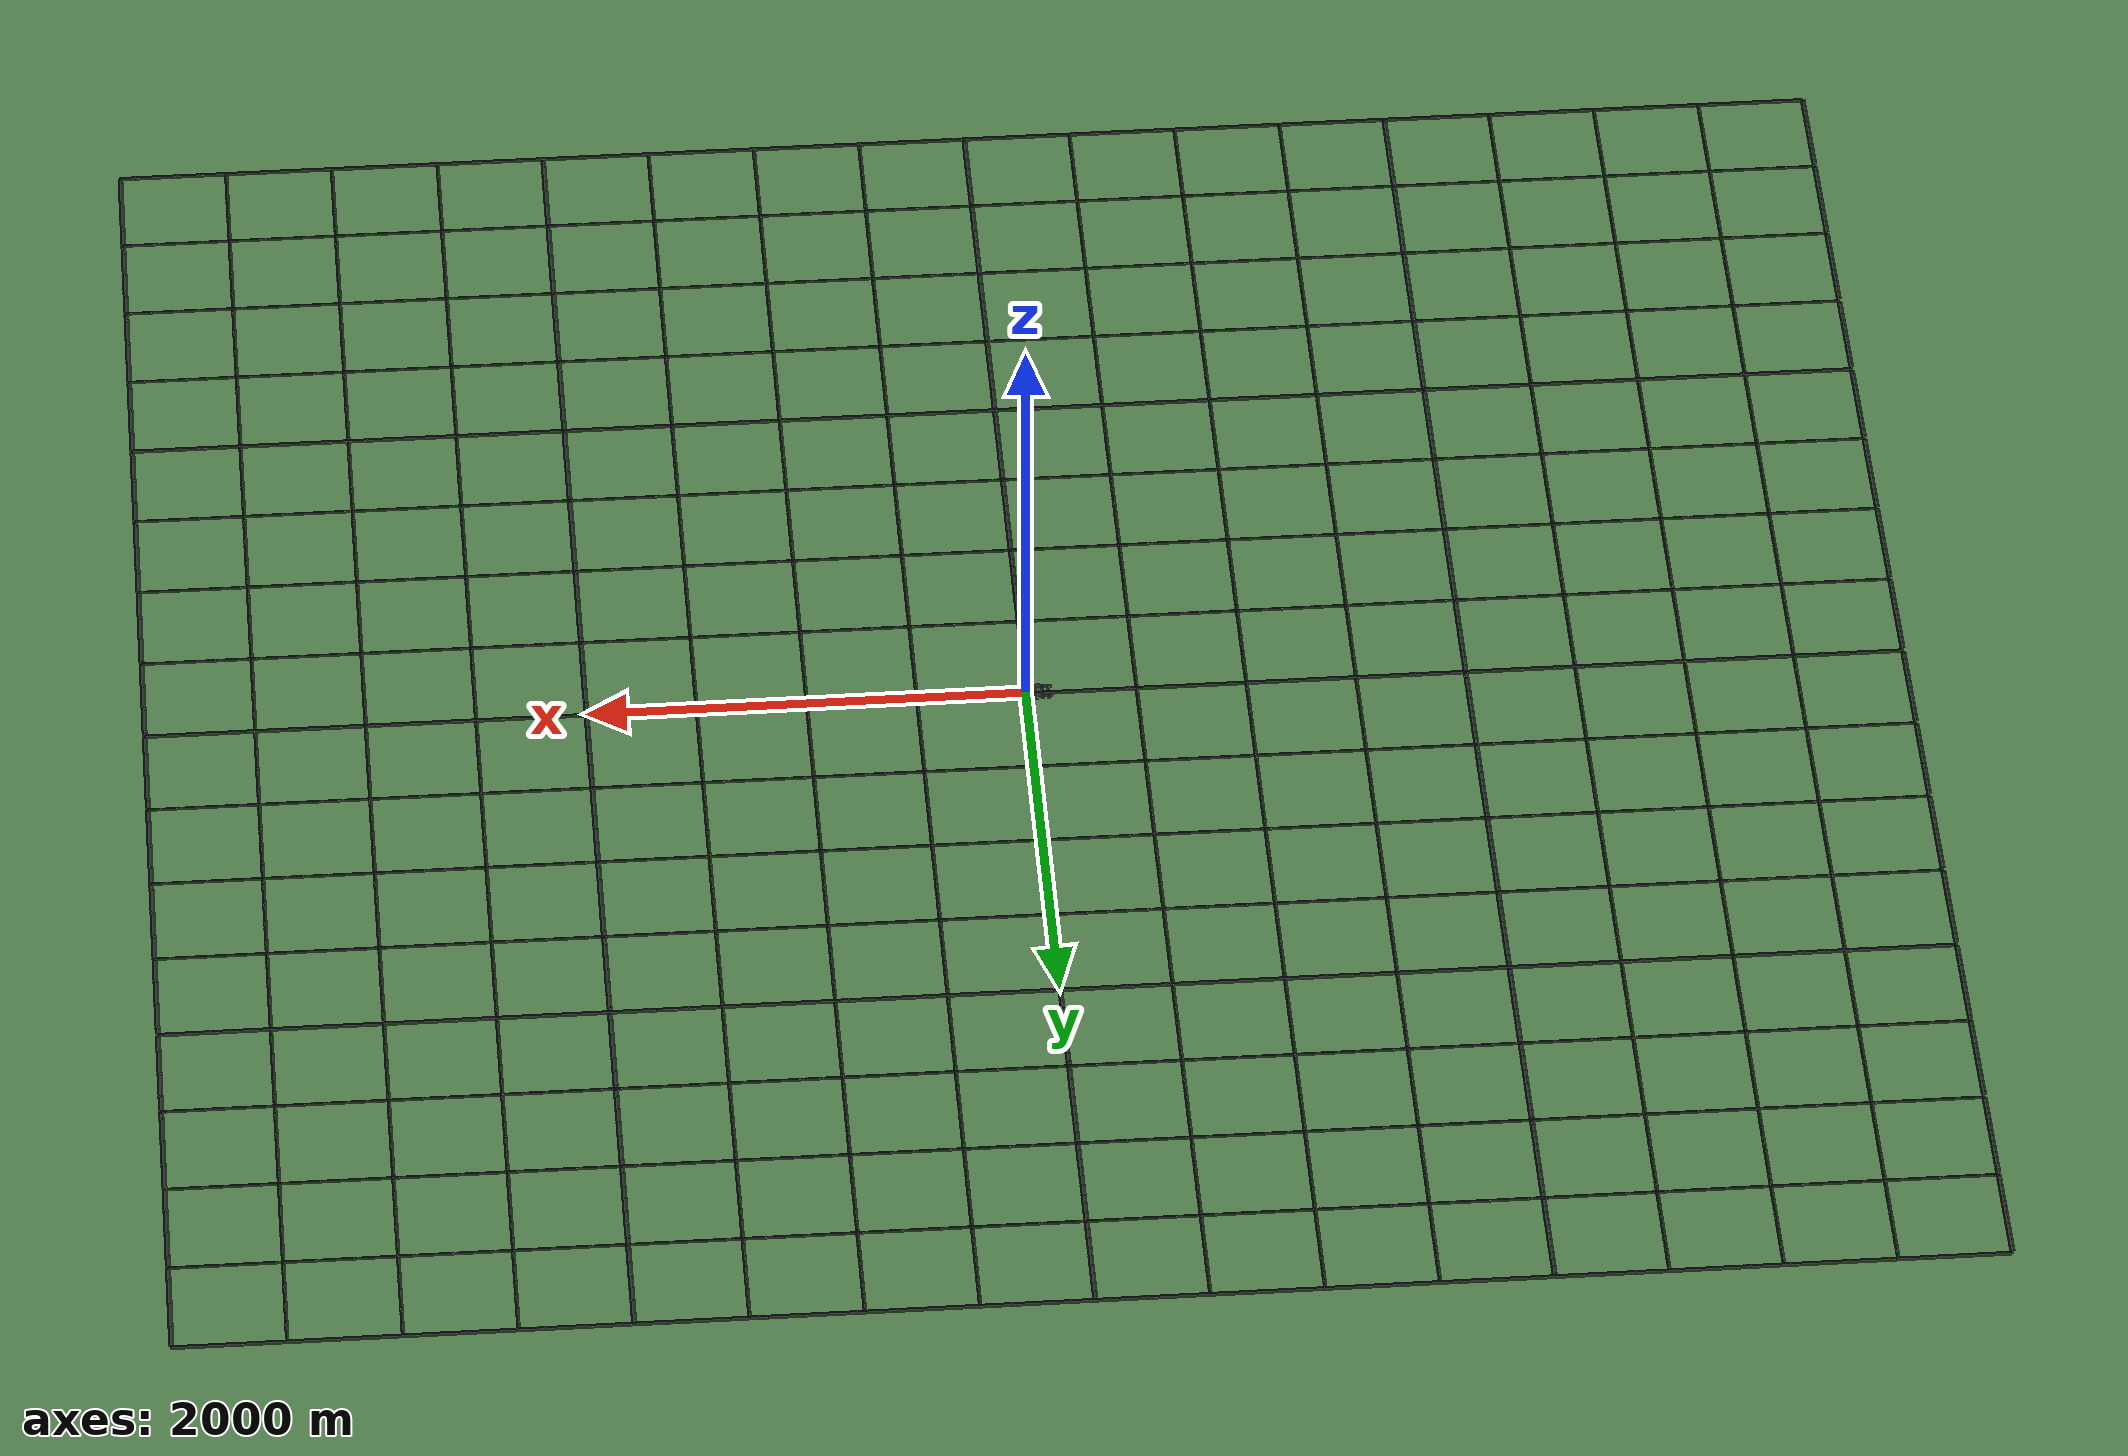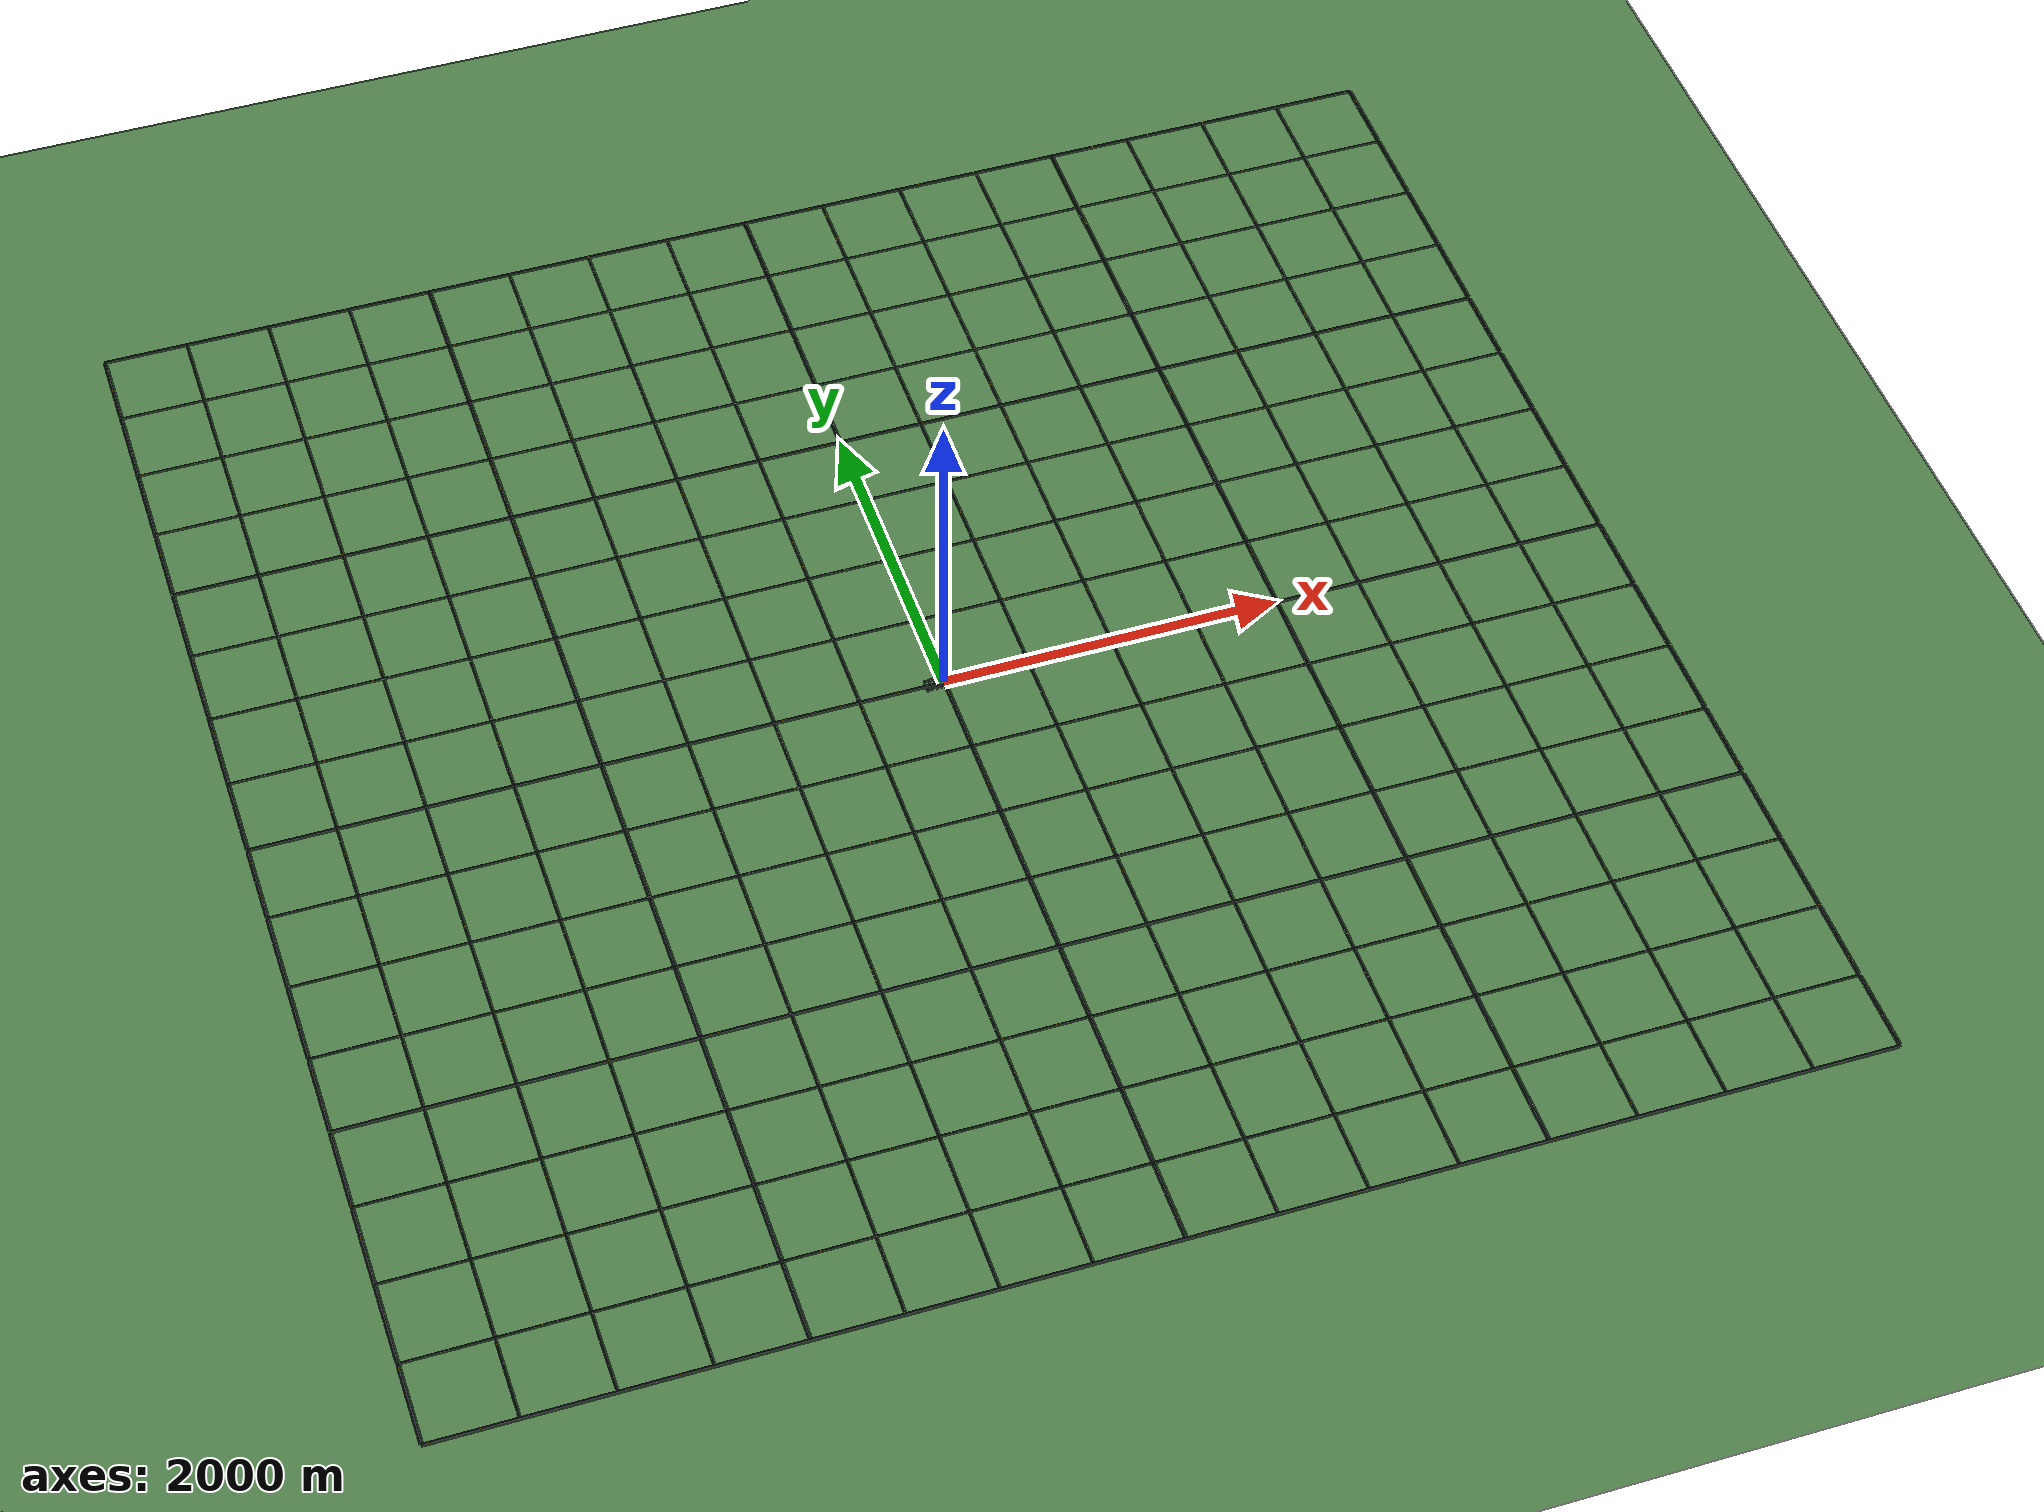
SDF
<?xml version="1.0"?>
<!-- 기존 주행 경로를 유지한 8 km 도심 도로 월드. 도로망은 SDF 기본 형상으로 구성됩니다. -->
<sdf version="1.8"><world name="vehicle_world">
<physics name="physics" type="ignored"><max_step_size>0.001</max_step_size><real_time_factor>1</real_time_factor></physics>
<plugin filename="ignition-gazebo-physics-system" name="ignition::gazebo::systems::Physics"/>
<plugin filename="ignition-gazebo-user-commands-system" name="ignition::gazebo::systems::UserCommands"/>
<plugin filename="ignition-gazebo-scene-broadcaster-system" name="ignition::gazebo::systems::SceneBroadcaster"/>
<light name="sun" type="directional"><pose>0 0 10 0 0 0</pose><diffuse>1 1 1 1</diffuse><specular>0.2 0.2 0.2 1</specular><direction>-0.5 0.1 -0.9</direction><cast_shadows>true</cast_shadows></light>
<scene><ambient>0.62 0.67 0.72 1</ambient><background>0.68 0.81 0.94 1</background><shadows>true</shadows></scene>
<model name="ground"><static>true</static><link name="ground"><collision name="ground"><geometry><plane><normal>0 0 1</normal><size>8200 8200</size></plane></geometry></collision><visual name="terrain"><pose>0 0 0.006 0 0 0</pose><geometry><plane><normal>0 0 1</normal><size>8200 8200</size></plane></geometry><material><ambient>0.25 0.42 0.24 1</ambient><diffuse>0.30 0.48 0.28 1</diffuse></material></visual></link></model>
<!-- GENERATED_CITY_ROADS_START -->
<model name="city_road_network"><static>true</static><link name="roads">
<visual name="east_west_-4000"><pose>0 -4000 0.015 0 0 0</pose><geometry><box><size>8000 18 0.03</size></box></geometry><material><ambient>0.15 0.16 0.17 1</ambient><diffuse>0.15 0.16 0.17 1</diffuse></material></visual>
<visual name="east_west_-3500"><pose>0 -3500 0.015 0 0 0</pose><geometry><box><size>8000 11 0.03</size></box></geometry><material><ambient>0.15 0.16 0.17 1</ambient><diffuse>0.15 0.16 0.17 1</diffuse></material></visual>
<visual name="east_west_-3000"><pose>0 -3000 0.015 0 0 0</pose><geometry><box><size>8000 11 0.03</size></box></geometry><material><ambient>0.15 0.16 0.17 1</ambient><diffuse>0.15 0.16 0.17 1</diffuse></material></visual>
<visual name="east_west_-2500"><pose>0 -2500 0.015 0 0 0</pose><geometry><box><size>8000 11 0.03</size></box></geometry><material><ambient>0.15 0.16 0.17 1</ambient><diffuse>0.15 0.16 0.17 1</diffuse></material></visual>
<visual name="east_west_-2000"><pose>0 -2000 0.015 0 0 0</pose><geometry><box><size>8000 18 0.03</size></box></geometry><material><ambient>0.15 0.16 0.17 1</ambient><diffuse>0.15 0.16 0.17 1</diffuse></material></visual>
<visual name="east_west_-1500"><pose>0 -1500 0.015 0 0 0</pose><geometry><box><size>8000 11 0.03</size></box></geometry><material><ambient>0.15 0.16 0.17 1</ambient><diffuse>0.15 0.16 0.17 1</diffuse></material></visual>
<visual name="east_west_-1000"><pose>0 -1000 0.015 0 0 0</pose><geometry><box><size>8000 11 0.03</size></box></geometry><material><ambient>0.15 0.16 0.17 1</ambient><diffuse>0.15 0.16 0.17 1</diffuse></material></visual>
<visual name="east_west_-500"><pose>0 -500 0.015 0 0 0</pose><geometry><box><size>8000 11 0.03</size></box></geometry><material><ambient>0.15 0.16 0.17 1</ambient><diffuse>0.15 0.16 0.17 1</diffuse></material></visual>
<visual name="east_west_0"><pose>0 0 0.015 0 0 0</pose><geometry><box><size>8000 18 0.03</size></box></geometry><material><ambient>0.15 0.16 0.17 1</ambient><diffuse>0.15 0.16 0.17 1</diffuse></material></visual>
<visual name="east_west_500"><pose>0 500 0.015 0 0 0</pose><geometry><box><size>8000 11 0.03</size></box></geometry><material><ambient>0.15 0.16 0.17 1</ambient><diffuse>0.15 0.16 0.17 1</diffuse></material></visual>
<visual name="east_west_1000"><pose>0 1000 0.015 0 0 0</pose><geometry><box><size>8000 11 0.03</size></box></geometry><material><ambient>0.15 0.16 0.17 1</ambient><diffuse>0.15 0.16 0.17 1</diffuse></material></visual>
<visual name="east_west_1500"><pose>0 1500 0.015 0 0 0</pose><geometry><box><size>8000 11 0.03</size></box></geometry><material><ambient>0.15 0.16 0.17 1</ambient><diffuse>0.15 0.16 0.17 1</diffuse></material></visual>
<visual name="east_west_2000"><pose>0 2000 0.015 0 0 0</pose><geometry><box><size>8000 18 0.03</size></box></geometry><material><ambient>0.15 0.16 0.17 1</ambient><diffuse>0.15 0.16 0.17 1</diffuse></material></visual>
<visual name="east_west_2500"><pose>0 2500 0.015 0 0 0</pose><geometry><box><size>8000 11 0.03</size></box></geometry><material><ambient>0.15 0.16 0.17 1</ambient><diffuse>0.15 0.16 0.17 1</diffuse></material></visual>
<visual name="east_west_3000"><pose>0 3000 0.015 0 0 0</pose><geometry><box><size>8000 11 0.03</size></box></geometry><material><ambient>0.15 0.16 0.17 1</ambient><diffuse>0.15 0.16 0.17 1</diffuse></material></visual>
<visual name="east_west_3500"><pose>0 3500 0.015 0 0 0</pose><geometry><box><size>8000 11 0.03</size></box></geometry><material><ambient>0.15 0.16 0.17 1</ambient><diffuse>0.15 0.16 0.17 1</diffuse></material></visual>
<visual name="east_west_4000"><pose>0 4000 0.015 0 0 0</pose><geometry><box><size>8000 18 0.03</size></box></geometry><material><ambient>0.15 0.16 0.17 1</ambient><diffuse>0.15 0.16 0.17 1</diffuse></material></visual>
<visual name="north_south_-4000_-4000"><pose>-4000 -3748.25 0.015 0 0 0</pose><geometry><box><size>18 485.5 0.03</size></box></geometry><material><ambient>0.15 0.16 0.17 1</ambient><diffuse>0.15 0.16 0.17 1</diffuse></material></visual>
<visual name="north_south_-4000_-3500"><pose>-4000 -3250 0.015 0 0 0</pose><geometry><box><size>18 489 0.03</size></box></geometry><material><ambient>0.15 0.16 0.17 1</ambient><diffuse>0.15 0.16 0.17 1</diffuse></material></visual>
<visual name="north_south_-4000_-3000"><pose>-4000 -2750 0.015 0 0 0</pose><geometry><box><size>18 489 0.03</size></box></geometry><material><ambient>0.15 0.16 0.17 1</ambient><diffuse>0.15 0.16 0.17 1</diffuse></material></visual>
<visual name="north_south_-4000_-2500"><pose>-4000 -2251.75 0.015 0 0 0</pose><geometry><box><size>18 485.5 0.03</size></box></geometry><material><ambient>0.15 0.16 0.17 1</ambient><diffuse>0.15 0.16 0.17 1</diffuse></material></visual>
<visual name="north_south_-4000_-2000"><pose>-4000 -1748.25 0.015 0 0 0</pose><geometry><box><size>18 485.5 0.03</size></box></geometry><material><ambient>0.15 0.16 0.17 1</ambient><diffuse>0.15 0.16 0.17 1</diffuse></material></visual>
<visual name="north_south_-4000_-1500"><pose>-4000 -1250 0.015 0 0 0</pose><geometry><box><size>18 489 0.03</size></box></geometry><material><ambient>0.15 0.16 0.17 1</ambient><diffuse>0.15 0.16 0.17 1</diffuse></material></visual>
<visual name="north_south_-4000_-1000"><pose>-4000 -750 0.015 0 0 0</pose><geometry><box><size>18 489 0.03</size></box></geometry><material><ambient>0.15 0.16 0.17 1</ambient><diffuse>0.15 0.16 0.17 1</diffuse></material></visual>
<visual name="north_south_-4000_-500"><pose>-4000 -251.75 0.015 0 0 0</pose><geometry><box><size>18 485.5 0.03</size></box></geometry><material><ambient>0.15 0.16 0.17 1</ambient><diffuse>0.15 0.16 0.17 1</diffuse></material></visual>
<visual name="north_south_-4000_0"><pose>-4000 251.75 0.015 0 0 0</pose><geometry><box><size>18 485.5 0.03</size></box></geometry><material><ambient>0.15 0.16 0.17 1</ambient><diffuse>0.15 0.16 0.17 1</diffuse></material></visual>
<visual name="north_south_-4000_500"><pose>-4000 750 0.015 0 0 0</pose><geometry><box><size>18 489 0.03</size></box></geometry><material><ambient>0.15 0.16 0.17 1</ambient><diffuse>0.15 0.16 0.17 1</diffuse></material></visual>
<visual name="north_south_-4000_1000"><pose>-4000 1250 0.015 0 0 0</pose><geometry><box><size>18 489 0.03</size></box></geometry><material><ambient>0.15 0.16 0.17 1</ambient><diffuse>0.15 0.16 0.17 1</diffuse></material></visual>
<visual name="north_south_-4000_1500"><pose>-4000 1748.25 0.015 0 0 0</pose><geometry><box><size>18 485.5 0.03</size></box></geometry><material><ambient>0.15 0.16 0.17 1</ambient><diffuse>0.15 0.16 0.17 1</diffuse></material></visual>
<visual name="north_south_-4000_2000"><pose>-4000 2251.75 0.015 0 0 0</pose><geometry><box><size>18 485.5 0.03</size></box></geometry><material><ambient>0.15 0.16 0.17 1</ambient><diffuse>0.15 0.16 0.17 1</diffuse></material></visual>
<visual name="north_south_-4000_2500"><pose>-4000 2750 0.015 0 0 0</pose><geometry><box><size>18 489 0.03</size></box></geometry><material><ambient>0.15 0.16 0.17 1</ambient><diffuse>0.15 0.16 0.17 1</diffuse></material></visual>
<visual name="north_south_-4000_3000"><pose>-4000 3250 0.015 0 0 0</pose><geometry><box><size>18 489 0.03</size></box></geometry><material><ambient>0.15 0.16 0.17 1</ambient><diffuse>0.15 0.16 0.17 1</diffuse></material></visual>
<visual name="north_south_-4000_3500"><pose>-4000 3748.25 0.015 0 0 0</pose><geometry><box><size>18 485.5 0.03</size></box></geometry><material><ambient>0.15 0.16 0.17 1</ambient><diffuse>0.15 0.16 0.17 1</diffuse></material></visual>
<visual name="north_south_-3500_-4000"><pose>-3500 -3748.25 0.015 0 0 0</pose><geometry><box><size>11 485.5 0.03</size></box></geometry><material><ambient>0.15 0.16 0.17 1</ambient><diffuse>0.15 0.16 0.17 1</diffuse></material></visual>
<visual name="north_south_-3500_-3500"><pose>-3500 -3250 0.015 0 0 0</pose><geometry><box><size>11 489 0.03</size></box></geometry><material><ambient>0.15 0.16 0.17 1</ambient><diffuse>0.15 0.16 0.17 1</diffuse></material></visual>
<visual name="north_south_-3500_-3000"><pose>-3500 -2750 0.015 0 0 0</pose><geometry><box><size>11 489 0.03</size></box></geometry><material><ambient>0.15 0.16 0.17 1</ambient><diffuse>0.15 0.16 0.17 1</diffuse></material></visual>
<visual name="north_south_-3500_-2500"><pose>-3500 -2251.75 0.015 0 0 0</pose><geometry><box><size>11 485.5 0.03</size></box></geometry><material><ambient>0.15 0.16 0.17 1</ambient><diffuse>0.15 0.16 0.17 1</diffuse></material></visual>
<visual name="north_south_-3500_-2000"><pose>-3500 -1748.25 0.015 0 0 0</pose><geometry><box><size>11 485.5 0.03</size></box></geometry><material><ambient>0.15 0.16 0.17 1</ambient><diffuse>0.15 0.16 0.17 1</diffuse></material></visual>
<visual name="north_south_-3500_-1500"><pose>-3500 -1250 0.015 0 0 0</pose><geometry><box><size>11 489 0.03</size></box></geometry><material><ambient>0.15 0.16 0.17 1</ambient><diffuse>0.15 0.16 0.17 1</diffuse></material></visual>
<visual name="north_south_-3500_-1000"><pose>-3500 -750 0.015 0 0 0</pose><geometry><box><size>11 489 0.03</size></box></geometry><material><ambient>0.15 0.16 0.17 1</ambient><diffuse>0.15 0.16 0.17 1</diffuse></material></visual>
<visual name="north_south_-3500_-500"><pose>-3500 -251.75 0.015 0 0 0</pose><geometry><box><size>11 485.5 0.03</size></box></geometry><material><ambient>0.15 0.16 0.17 1</ambient><diffuse>0.15 0.16 0.17 1</diffuse></material></visual>
<visual name="north_south_-3500_0"><pose>-3500 251.75 0.015 0 0 0</pose><geometry><box><size>11 485.5 0.03</size></box></geometry><material><ambient>0.15 0.16 0.17 1</ambient><diffuse>0.15 0.16 0.17 1</diffuse></material></visual>
<visual name="north_south_-3500_500"><pose>-3500 750 0.015 0 0 0</pose><geometry><box><size>11 489 0.03</size></box></geometry><material><ambient>0.15 0.16 0.17 1</ambient><diffuse>0.15 0.16 0.17 1</diffuse></material></visual>
<visual name="north_south_-3500_1000"><pose>-3500 1250 0.015 0 0 0</pose><geometry><box><size>11 489 0.03</size></box></geometry><material><ambient>0.15 0.16 0.17 1</ambient><diffuse>0.15 0.16 0.17 1</diffuse></material></visual>
<visual name="north_south_-3500_1500"><pose>-3500 1748.25 0.015 0 0 0</pose><geometry><box><size>11 485.5 0.03</size></box></geometry><material><ambient>0.15 0.16 0.17 1</ambient><diffuse>0.15 0.16 0.17 1</diffuse></material></visual>
<visual name="north_south_-3500_2000"><pose>-3500 2251.75 0.015 0 0 0</pose><geometry><box><size>11 485.5 0.03</size></box></geometry><material><ambient>0.15 0.16 0.17 1</ambient><diffuse>0.15 0.16 0.17 1</diffuse></material></visual>
<visual name="north_south_-3500_2500"><pose>-3500 2750 0.015 0 0 0</pose><geometry><box><size>11 489 0.03</size></box></geometry><material><ambient>0.15 0.16 0.17 1</ambient><diffuse>0.15 0.16 0.17 1</diffuse></material></visual>
<visual name="north_south_-3500_3000"><pose>-3500 3250 0.015 0 0 0</pose><geometry><box><size>11 489 0.03</size></box></geometry><material><ambient>0.15 0.16 0.17 1</ambient><diffuse>0.15 0.16 0.17 1</diffuse></material></visual>
<visual name="north_south_-3500_3500"><pose>-3500 3748.25 0.015 0 0 0</pose><geometry><box><size>11 485.5 0.03</size></box></geometry><material><ambient>0.15 0.16 0.17 1</ambient><diffuse>0.15 0.16 0.17 1</diffuse></material></visual>
<visual name="north_south_-3000_-4000"><pose>-3000 -3748.25 0.015 0 0 0</pose><geometry><box><size>11 485.5 0.03</size></box></geometry><material><ambient>0.15 0.16 0.17 1</ambient><diffuse>0.15 0.16 0.17 1</diffuse></material></visual>
<visual name="north_south_-3000_-3500"><pose>-3000 -3250 0.015 0 0 0</pose><geometry><box><size>11 489 0.03</size></box></geometry><material><ambient>0.15 0.16 0.17 1</ambient><diffuse>0.15 0.16 0.17 1</diffuse></material></visual>
<visual name="north_south_-3000_-3000"><pose>-3000 -2750 0.015 0 0 0</pose><geometry><box><size>11 489 0.03</size></box></geometry><material><ambient>0.15 0.16 0.17 1</ambient><diffuse>0.15 0.16 0.17 1</diffuse></material></visual>
<visual name="north_south_-3000_-2500"><pose>-3000 -2251.75 0.015 0 0 0</pose><geometry><box><size>11 485.5 0.03</size></box></geometry><material><ambient>0.15 0.16 0.17 1</ambient><diffuse>0.15 0.16 0.17 1</diffuse></material></visual>
<visual name="north_south_-3000_-2000"><pose>-3000 -1748.25 0.015 0 0 0</pose><geometry><box><size>11 485.5 0.03</size></box></geometry><material><ambient>0.15 0.16 0.17 1</ambient><diffuse>0.15 0.16 0.17 1</diffuse></material></visual>
<visual name="north_south_-3000_-1500"><pose>-3000 -1250 0.015 0 0 0</pose><geometry><box><size>11 489 0.03</size></box></geometry><material><ambient>0.15 0.16 0.17 1</ambient><diffuse>0.15 0.16 0.17 1</diffuse></material></visual>
<visual name="north_south_-3000_-1000"><pose>-3000 -750 0.015 0 0 0</pose><geometry><box><size>11 489 0.03</size></box></geometry><material><ambient>0.15 0.16 0.17 1</ambient><diffuse>0.15 0.16 0.17 1</diffuse></material></visual>
<visual name="north_south_-3000_-500"><pose>-3000 -251.75 0.015 0 0 0</pose><geometry><box><size>11 485.5 0.03</size></box></geometry><material><ambient>0.15 0.16 0.17 1</ambient><diffuse>0.15 0.16 0.17 1</diffuse></material></visual>
<visual name="north_south_-3000_0"><pose>-3000 251.75 0.015 0 0 0</pose><geometry><box><size>11 485.5 0.03</size></box></geometry><material><ambient>0.15 0.16 0.17 1</ambient><diffuse>0.15 0.16 0.17 1</diffuse></material></visual>
<visual name="north_south_-3000_500"><pose>-3000 750 0.015 0 0 0</pose><geometry><box><size>11 489 0.03</size></box></geometry><material><ambient>0.15 0.16 0.17 1</ambient><diffuse>0.15 0.16 0.17 1</diffuse></material></visual>
<visual name="north_south_-3000_1000"><pose>-3000 1250 0.015 0 0 0</pose><geometry><box><size>11 489 0.03</size></box></geometry><material><ambient>0.15 0.16 0.17 1</ambient><diffuse>0.15 0.16 0.17 1</diffuse></material></visual>
<visual name="north_south_-3000_1500"><pose>-3000 1748.25 0.015 0 0 0</pose><geometry><box><size>11 485.5 0.03</size></box></geometry><material><ambient>0.15 0.16 0.17 1</ambient><diffuse>0.15 0.16 0.17 1</diffuse></material></visual>
<visual name="north_south_-3000_2000"><pose>-3000 2251.75 0.015 0 0 0</pose><geometry><box><size>11 485.5 0.03</size></box></geometry><material><ambient>0.15 0.16 0.17 1</ambient><diffuse>0.15 0.16 0.17 1</diffuse></material></visual>
<visual name="north_south_-3000_2500"><pose>-3000 2750 0.015 0 0 0</pose><geometry><box><size>11 489 0.03</size></box></geometry><material><ambient>0.15 0.16 0.17 1</ambient><diffuse>0.15 0.16 0.17 1</diffuse></material></visual>
<visual name="north_south_-3000_3000"><pose>-3000 3250 0.015 0 0 0</pose><geometry><box><size>11 489 0.03</size></box></geometry><material><ambient>0.15 0.16 0.17 1</ambient><diffuse>0.15 0.16 0.17 1</diffuse></material></visual>
<visual name="north_south_-3000_3500"><pose>-3000 3748.25 0.015 0 0 0</pose><geometry><box><size>11 485.5 0.03</size></box></geometry><material><ambient>0.15 0.16 0.17 1</ambient><diffuse>0.15 0.16 0.17 1</diffuse></material></visual>
<visual name="north_south_-2500_-4000"><pose>-2500 -3748.25 0.015 0 0 0</pose><geometry><box><size>11 485.5 0.03</size></box></geometry><material><ambient>0.15 0.16 0.17 1</ambient><diffuse>0.15 0.16 0.17 1</diffuse></material></visual>
<visual name="north_south_-2500_-3500"><pose>-2500 -3250 0.015 0 0 0</pose><geometry><box><size>11 489 0.03</size></box></geometry><material><ambient>0.15 0.16 0.17 1</ambient><diffuse>0.15 0.16 0.17 1</diffuse></material></visual>
<visual name="north_south_-2500_-3000"><pose>-2500 -2750 0.015 0 0 0</pose><geometry><box><size>11 489 0.03</size></box></geometry><material><ambient>0.15 0.16 0.17 1</ambient><diffuse>0.15 0.16 0.17 1</diffuse></material></visual>
<visual name="north_south_-2500_-2500"><pose>-2500 -2251.75 0.015 0 0 0</pose><geometry><box><size>11 485.5 0.03</size></box></geometry><material><ambient>0.15 0.16 0.17 1</ambient><diffuse>0.15 0.16 0.17 1</diffuse></material></visual>
<visual name="north_south_-2500_-2000"><pose>-2500 -1748.25 0.015 0 0 0</pose><geometry><box><size>11 485.5 0.03</size></box></geometry><material><ambient>0.15 0.16 0.17 1</ambient><diffuse>0.15 0.16 0.17 1</diffuse></material></visual>
<visual name="north_south_-2500_-1500"><pose>-2500 -1250 0.015 0 0 0</pose><geometry><box><size>11 489 0.03</size></box></geometry><material><ambient>0.15 0.16 0.17 1</ambient><diffuse>0.15 0.16 0.17 1</diffuse></material></visual>
<visual name="north_south_-2500_-1000"><pose>-2500 -750 0.015 0 0 0</pose><geometry><box><size>11 489 0.03</size></box></geometry><material><ambient>0.15 0.16 0.17 1</ambient><diffuse>0.15 0.16 0.17 1</diffuse></material></visual>
<visual name="north_south_-2500_-500"><pose>-2500 -251.75 0.015 0 0 0</pose><geometry><box><size>11 485.5 0.03</size></box></geometry><material><ambient>0.15 0.16 0.17 1</ambient><diffuse>0.15 0.16 0.17 1</diffuse></material></visual>
<visual name="north_south_-2500_0"><pose>-2500 251.75 0.015 0 0 0</pose><geometry><box><size>11 485.5 0.03</size></box></geometry><material><ambient>0.15 0.16 0.17 1</ambient><diffuse>0.15 0.16 0.17 1</diffuse></material></visual>
<visual name="north_south_-2500_500"><pose>-2500 750 0.015 0 0 0</pose><geometry><box><size>11 489 0.03</size></box></geometry><material><ambient>0.15 0.16 0.17 1</ambient><diffuse>0.15 0.16 0.17 1</diffuse></material></visual>
<visual name="north_south_-2500_1000"><pose>-2500 1250 0.015 0 0 0</pose><geometry><box><size>11 489 0.03</size></box></geometry><material><ambient>0.15 0.16 0.17 1</ambient><diffuse>0.15 0.16 0.17 1</diffuse></material></visual>
<visual name="north_south_-2500_1500"><pose>-2500 1748.25 0.015 0 0 0</pose><geometry><box><size>11 485.5 0.03</size></box></geometry><material><ambient>0.15 0.16 0.17 1</ambient><diffuse>0.15 0.16 0.17 1</diffuse></material></visual>
<visual name="north_south_-2500_2000"><pose>-2500 2251.75 0.015 0 0 0</pose><geometry><box><size>11 485.5 0.03</size></box></geometry><material><ambient>0.15 0.16 0.17 1</ambient><diffuse>0.15 0.16 0.17 1</diffuse></material></visual>
<visual name="north_south_-2500_2500"><pose>-2500 2750 0.015 0 0 0</pose><geometry><box><size>11 489 0.03</size></box></geometry><material><ambient>0.15 0.16 0.17 1</ambient><diffuse>0.15 0.16 0.17 1</diffuse></material></visual>
<visual name="north_south_-2500_3000"><pose>-2500 3250 0.015 0 0 0</pose><geometry><box><size>11 489 0.03</size></box></geometry><material><ambient>0.15 0.16 0.17 1</ambient><diffuse>0.15 0.16 0.17 1</diffuse></material></visual>
<visual name="north_south_-2500_3500"><pose>-2500 3748.25 0.015 0 0 0</pose><geometry><box><size>11 485.5 0.03</size></box></geometry><material><ambient>0.15 0.16 0.17 1</ambient><diffuse>0.15 0.16 0.17 1</diffuse></material></visual>
<visual name="north_south_-2000_-4000"><pose>-2000 -3748.25 0.015 0 0 0</pose><geometry><box><size>18 485.5 0.03</size></box></geometry><material><ambient>0.15 0.16 0.17 1</ambient><diffuse>0.15 0.16 0.17 1</diffuse></material></visual>
<visual name="north_south_-2000_-3500"><pose>-2000 -3250 0.015 0 0 0</pose><geometry><box><size>18 489 0.03</size></box></geometry><material><ambient>0.15 0.16 0.17 1</ambient><diffuse>0.15 0.16 0.17 1</diffuse></material></visual>
<visual name="north_south_-2000_-3000"><pose>-2000 -2750 0.015 0 0 0</pose><geometry><box><size>18 489 0.03</size></box></geometry><material><ambient>0.15 0.16 0.17 1</ambient><diffuse>0.15 0.16 0.17 1</diffuse></material></visual>
<visual name="north_south_-2000_-2500"><pose>-2000 -2251.75 0.015 0 0 0</pose><geometry><box><size>18 485.5 0.03</size></box></geometry><material><ambient>0.15 0.16 0.17 1</ambient><diffuse>0.15 0.16 0.17 1</diffuse></material></visual>
<visual name="north_south_-2000_-2000"><pose>-2000 -1748.25 0.015 0 0 0</pose><geometry><box><size>18 485.5 0.03</size></box></geometry><material><ambient>0.15 0.16 0.17 1</ambient><diffuse>0.15 0.16 0.17 1</diffuse></material></visual>
<visual name="north_south_-2000_-1500"><pose>-2000 -1250 0.015 0 0 0</pose><geometry><box><size>18 489 0.03</size></box></geometry><material><ambient>0.15 0.16 0.17 1</ambient><diffuse>0.15 0.16 0.17 1</diffuse></material></visual>
<visual name="north_south_-2000_-1000"><pose>-2000 -750 0.015 0 0 0</pose><geometry><box><size>18 489 0.03</size></box></geometry><material><ambient>0.15 0.16 0.17 1</ambient><diffuse>0.15 0.16 0.17 1</diffuse></material></visual>
<visual name="north_south_-2000_-500"><pose>-2000 -251.75 0.015 0 0 0</pose><geometry><box><size>18 485.5 0.03</size></box></geometry><material><ambient>0.15 0.16 0.17 1</ambient><diffuse>0.15 0.16 0.17 1</diffuse></material></visual>
<visual name="north_south_-2000_0"><pose>-2000 251.75 0.015 0 0 0</pose><geometry><box><size>18 485.5 0.03</size></box></geometry><material><ambient>0.15 0.16 0.17 1</ambient><diffuse>0.15 0.16 0.17 1</diffuse></material></visual>
<visual name="north_south_-2000_500"><pose>-2000 750 0.015 0 0 0</pose><geometry><box><size>18 489 0.03</size></box></geometry><material><ambient>0.15 0.16 0.17 1</ambient><diffuse>0.15 0.16 0.17 1</diffuse></material></visual>
<visual name="north_south_-2000_1000"><pose>-2000 1250 0.015 0 0 0</pose><geometry><box><size>18 489 0.03</size></box></geometry><material><ambient>0.15 0.16 0.17 1</ambient><diffuse>0.15 0.16 0.17 1</diffuse></material></visual>
<visual name="north_south_-2000_1500"><pose>-2000 1748.25 0.015 0 0 0</pose><geometry><box><size>18 485.5 0.03</size></box></geometry><material><ambient>0.15 0.16 0.17 1</ambient><diffuse>0.15 0.16 0.17 1</diffuse></material></visual>
<visual name="north_south_-2000_2000"><pose>-2000 2251.75 0.015 0 0 0</pose><geometry><box><size>18 485.5 0.03</size></box></geometry><material><ambient>0.15 0.16 0.17 1</ambient><diffuse>0.15 0.16 0.17 1</diffuse></material></visual>
<visual name="north_south_-2000_2500"><pose>-2000 2750 0.015 0 0 0</pose><geometry><box><size>18 489 0.03</size></box></geometry><material><ambient>0.15 0.16 0.17 1</ambient><diffuse>0.15 0.16 0.17 1</diffuse></material></visual>
<visual name="north_south_-2000_3000"><pose>-2000 3250 0.015 0 0 0</pose><geometry><box><size>18 489 0.03</size></box></geometry><material><ambient>0.15 0.16 0.17 1</ambient><diffuse>0.15 0.16 0.17 1</diffuse></material></visual>
<visual name="north_south_-2000_3500"><pose>-2000 3748.25 0.015 0 0 0</pose><geometry><box><size>18 485.5 0.03</size></box></geometry><material><ambient>0.15 0.16 0.17 1</ambient><diffuse>0.15 0.16 0.17 1</diffuse></material></visual>
<visual name="north_south_-1500_-4000"><pose>-1500 -3748.25 0.015 0 0 0</pose><geometry><box><size>11 485.5 0.03</size></box></geometry><material><ambient>0.15 0.16 0.17 1</ambient><diffuse>0.15 0.16 0.17 1</diffuse></material></visual>
<visual name="north_south_-1500_-3500"><pose>-1500 -3250 0.015 0 0 0</pose><geometry><box><size>11 489 0.03</size></box></geometry><material><ambient>0.15 0.16 0.17 1</ambient><diffuse>0.15 0.16 0.17 1</diffuse></material></visual>
<visual name="north_south_-1500_-3000"><pose>-1500 -2750 0.015 0 0 0</pose><geometry><box><size>11 489 0.03</size></box></geometry><material><ambient>0.15 0.16 0.17 1</ambient><diffuse>0.15 0.16 0.17 1</diffuse></material></visual>
<visual name="north_south_-1500_-2500"><pose>-1500 -2251.75 0.015 0 0 0</pose><geometry><box><size>11 485.5 0.03</size></box></geometry><material><ambient>0.15 0.16 0.17 1</ambient><diffuse>0.15 0.16 0.17 1</diffuse></material></visual>
<visual name="north_south_-1500_-2000"><pose>-1500 -1748.25 0.015 0 0 0</pose><geometry><box><size>11 485.5 0.03</size></box></geometry><material><ambient>0.15 0.16 0.17 1</ambient><diffuse>0.15 0.16 0.17 1</diffuse></material></visual>
<visual name="north_south_-1500_-1500"><pose>-1500 -1250 0.015 0 0 0</pose><geometry><box><size>11 489 0.03</size></box></geometry><material><ambient>0.15 0.16 0.17 1</ambient><diffuse>0.15 0.16 0.17 1</diffuse></material></visual>
<visual name="north_south_-1500_-1000"><pose>-1500 -750 0.015 0 0 0</pose><geometry><box><size>11 489 0.03</size></box></geometry><material><ambient>0.15 0.16 0.17 1</ambient><diffuse>0.15 0.16 0.17 1</diffuse></material></visual>
<visual name="north_south_-1500_-500"><pose>-1500 -251.75 0.015 0 0 0</pose><geometry><box><size>11 485.5 0.03</size></box></geometry><material><ambient>0.15 0.16 0.17 1</ambient><diffuse>0.15 0.16 0.17 1</diffuse></material></visual>
<visual name="north_south_-1500_0"><pose>-1500 251.75 0.015 0 0 0</pose><geometry><box><size>11 485.5 0.03</size></box></geometry><material><ambient>0.15 0.16 0.17 1</ambient><diffuse>0.15 0.16 0.17 1</diffuse></material></visual>
<visual name="north_south_-1500_500"><pose>-1500 750 0.015 0 0 0</pose><geometry><box><size>11 489 0.03</size></box></geometry><material><ambient>0.15 0.16 0.17 1</ambient><diffuse>0.15 0.16 0.17 1</diffuse></material></visual>
<visual name="north_south_-1500_1000"><pose>-1500 1250 0.015 0 0 0</pose><geometry><box><size>11 489 0.03</size></box></geometry><material><ambient>0.15 0.16 0.17 1</ambient><diffuse>0.15 0.16 0.17 1</diffuse></material></visual>
<visual name="north_south_-1500_1500"><pose>-1500 1748.25 0.015 0 0 0</pose><geometry><box><size>11 485.5 0.03</size></box></geometry><material><ambient>0.15 0.16 0.17 1</ambient><diffuse>0.15 0.16 0.17 1</diffuse></material></visual>
<visual name="north_south_-1500_2000"><pose>-1500 2251.75 0.015 0 0 0</pose><geometry><box><size>11 485.5 0.03</size></box></geometry><material><ambient>0.15 0.16 0.17 1</ambient><diffuse>0.15 0.16 0.17 1</diffuse></material></visual>
<visual name="north_south_-1500_2500"><pose>-1500 2750 0.015 0 0 0</pose><geometry><box><size>11 489 0.03</size></box></geometry><material><ambient>0.15 0.16 0.17 1</ambient><diffuse>0.15 0.16 0.17 1</diffuse></material></visual>
<visual name="north_south_-1500_3000"><pose>-1500 3250 0.015 0 0 0</pose><geometry><box><size>11 489 0.03</size></box></geometry><material><ambient>0.15 0.16 0.17 1</ambient><diffuse>0.15 0.16 0.17 1</diffuse></material></visual>
<visual name="north_south_-1500_3500"><pose>-1500 3748.25 0.015 0 0 0</pose><geometry><box><size>11 485.5 0.03</size></box></geometry><material><ambient>0.15 0.16 0.17 1</ambient><diffuse>0.15 0.16 0.17 1</diffuse></material></visual>
<visual name="north_south_-1000_-4000"><pose>-1000 -3748.25 0.015 0 0 0</pose><geometry><box><size>11 485.5 0.03</size></box></geometry><material><ambient>0.15 0.16 0.17 1</ambient><diffuse>0.15 0.16 0.17 1</diffuse></material></visual>
<visual name="north_south_-1000_-3500"><pose>-1000 -3250 0.015 0 0 0</pose><geometry><box><size>11 489 0.03</size></box></geometry><material><ambient>0.15 0.16 0.17 1</ambient><diffuse>0.15 0.16 0.17 1</diffuse></material></visual>
<visual name="north_south_-1000_-3000"><pose>-1000 -2750 0.015 0 0 0</pose><geometry><box><size>11 489 0.03</size></box></geometry><material><ambient>0.15 0.16 0.17 1</ambient><diffuse>0.15 0.16 0.17 1</diffuse></material></visual>
<visual name="north_south_-1000_-2500"><pose>-1000 -2251.75 0.015 0 0 0</pose><geometry><box><size>11 485.5 0.03</size></box></geometry><material><ambient>0.15 0.16 0.17 1</ambient><diffuse>0.15 0.16 0.17 1</diffuse></material></visual>
<visual name="north_south_-1000_-2000"><pose>-1000 -1748.25 0.015 0 0 0</pose><geometry><box><size>11 485.5 0.03</size></box></geometry><material><ambient>0.15 0.16 0.17 1</ambient><diffuse>0.15 0.16 0.17 1</diffuse></material></visual>
<visual name="north_south_-1000_-1500"><pose>-1000 -1250 0.015 0 0 0</pose><geometry><box><size>11 489 0.03</size></box></geometry><material><ambient>0.15 0.16 0.17 1</ambient><diffuse>0.15 0.16 0.17 1</diffuse></material></visual>
<visual name="north_south_-1000_-1000"><pose>-1000 -750 0.015 0 0 0</pose><geometry><box><size>11 489 0.03</size></box></geometry><material><ambient>0.15 0.16 0.17 1</ambient><diffuse>0.15 0.16 0.17 1</diffuse></material></visual>
<visual name="north_south_-1000_-500"><pose>-1000 -251.75 0.015 0 0 0</pose><geometry><box><size>11 485.5 0.03</size></box></geometry><material><ambient>0.15 0.16 0.17 1</ambient><diffuse>0.15 0.16 0.17 1</diffuse></material></visual>
<visual name="north_south_-1000_0"><pose>-1000 251.75 0.015 0 0 0</pose><geometry><box><size>11 485.5 0.03</size></box></geometry><material><ambient>0.15 0.16 0.17 1</ambient><diffuse>0.15 0.16 0.17 1</diffuse></material></visual>
<visual name="north_south_-1000_500"><pose>-1000 750 0.015 0 0 0</pose><geometry><box><size>11 489 0.03</size></box></geometry><material><ambient>0.15 0.16 0.17 1</ambient><diffuse>0.15 0.16 0.17 1</diffuse></material></visual>
<visual name="north_south_-1000_1000"><pose>-1000 1250 0.015 0 0 0</pose><geometry><box><size>11 489 0.03</size></box></geometry><material><ambient>0.15 0.16 0.17 1</ambient><diffuse>0.15 0.16 0.17 1</diffuse></material></visual>
<visual name="north_south_-1000_1500"><pose>-1000 1748.25 0.015 0 0 0</pose><geometry><box><size>11 485.5 0.03</size></box></geometry><material><ambient>0.15 0.16 0.17 1</ambient><diffuse>0.15 0.16 0.17 1</diffuse></material></visual>
<visual name="north_south_-1000_2000"><pose>-1000 2251.75 0.015 0 0 0</pose><geometry><box><size>11 485.5 0.03</size></box></geometry><material><ambient>0.15 0.16 0.17 1</ambient><diffuse>0.15 0.16 0.17 1</diffuse></material></visual>
<visual name="north_south_-1000_2500"><pose>-1000 2750 0.015 0 0 0</pose><geometry><box><size>11 489 0.03</size></box></geometry><material><ambient>0.15 0.16 0.17 1</ambient><diffuse>0.15 0.16 0.17 1</diffuse></material></visual>
<visual name="north_south_-1000_3000"><pose>-1000 3250 0.015 0 0 0</pose><geometry><box><size>11 489 0.03</size></box></geometry><material><ambient>0.15 0.16 0.17 1</ambient><diffuse>0.15 0.16 0.17 1</diffuse></material></visual>
<visual name="north_south_-1000_3500"><pose>-1000 3748.25 0.015 0 0 0</pose><geometry><box><size>11 485.5 0.03</size></box></geometry><material><ambient>0.15 0.16 0.17 1</ambient><diffuse>0.15 0.16 0.17 1</diffuse></material></visual>
<visual name="north_south_-500_-4000"><pose>-500 -3748.25 0.015 0 0 0</pose><geometry><box><size>11 485.5 0.03</size></box></geometry><material><ambient>0.15 0.16 0.17 1</ambient><diffuse>0.15 0.16 0.17 1</diffuse></material></visual>
<visual name="north_south_-500_-3500"><pose>-500 -3250 0.015 0 0 0</pose><geometry><box><size>11 489 0.03</size></box></geometry><material><ambient>0.15 0.16 0.17 1</ambient><diffuse>0.15 0.16 0.17 1</diffuse></material></visual>
<visual name="north_south_-500_-3000"><pose>-500 -2750 0.015 0 0 0</pose><geometry><box><size>11 489 0.03</size></box></geometry><material><ambient>0.15 0.16 0.17 1</ambient><diffuse>0.15 0.16 0.17 1</diffuse></material></visual>
<visual name="north_south_-500_-2500"><pose>-500 -2251.75 0.015 0 0 0</pose><geometry><box><size>11 485.5 0.03</size></box></geometry><material><ambient>0.15 0.16 0.17 1</ambient><diffuse>0.15 0.16 0.17 1</diffuse></material></visual>
<visual name="north_south_-500_-2000"><pose>-500 -1748.25 0.015 0 0 0</pose><geometry><box><size>11 485.5 0.03</size></box></geometry><material><ambient>0.15 0.16 0.17 1</ambient><diffuse>0.15 0.16 0.17 1</diffuse></material></visual>
<visual name="north_south_-500_-1500"><pose>-500 -1250 0.015 0 0 0</pose><geometry><box><size>11 489 0.03</size></box></geometry><material><ambient>0.15 0.16 0.17 1</ambient><diffuse>0.15 0.16 0.17 1</diffuse></material></visual>
<visual name="north_south_-500_-1000"><pose>-500 -750 0.015 0 0 0</pose><geometry><box><size>11 489 0.03</size></box></geometry><material><ambient>0.15 0.16 0.17 1</ambient><diffuse>0.15 0.16 0.17 1</diffuse></material></visual>
<visual name="north_south_-500_-500"><pose>-500 -251.75 0.015 0 0 0</pose><geometry><box><size>11 485.5 0.03</size></box></geometry><material><ambient>0.15 0.16 0.17 1</ambient><diffuse>0.15 0.16 0.17 1</diffuse></material></visual>
<visual name="north_south_-500_0"><pose>-500 251.75 0.015 0 0 0</pose><geometry><box><size>11 485.5 0.03</size></box></geometry><material><ambient>0.15 0.16 0.17 1</ambient><diffuse>0.15 0.16 0.17 1</diffuse></material></visual>
<visual name="north_south_-500_500"><pose>-500 750 0.015 0 0 0</pose><geometry><box><size>11 489 0.03</size></box></geometry><material><ambient>0.15 0.16 0.17 1</ambient><diffuse>0.15 0.16 0.17 1</diffuse></material></visual>
<visual name="north_south_-500_1000"><pose>-500 1250 0.015 0 0 0</pose><geometry><box><size>11 489 0.03</size></box></geometry><material><ambient>0.15 0.16 0.17 1</ambient><diffuse>0.15 0.16 0.17 1</diffuse></material></visual>
<visual name="north_south_-500_1500"><pose>-500 1748.25 0.015 0 0 0</pose><geometry><box><size>11 485.5 0.03</size></box></geometry><material><ambient>0.15 0.16 0.17 1</ambient><diffuse>0.15 0.16 0.17 1</diffuse></material></visual>
<visual name="north_south_-500_2000"><pose>-500 2251.75 0.015 0 0 0</pose><geometry><box><size>11 485.5 0.03</size></box></geometry><material><ambient>0.15 0.16 0.17 1</ambient><diffuse>0.15 0.16 0.17 1</diffuse></material></visual>
<visual name="north_south_-500_2500"><pose>-500 2750 0.015 0 0 0</pose><geometry><box><size>11 489 0.03</size></box></geometry><material><ambient>0.15 0.16 0.17 1</ambient><diffuse>0.15 0.16 0.17 1</diffuse></material></visual>
<visual name="north_south_-500_3000"><pose>-500 3250 0.015 0 0 0</pose><geometry><box><size>11 489 0.03</size></box></geometry><material><ambient>0.15 0.16 0.17 1</ambient><diffuse>0.15 0.16 0.17 1</diffuse></material></visual>
<visual name="north_south_-500_3500"><pose>-500 3748.25 0.015 0 0 0</pose><geometry><box><size>11 485.5 0.03</size></box></geometry><material><ambient>0.15 0.16 0.17 1</ambient><diffuse>0.15 0.16 0.17 1</diffuse></material></visual>
<visual name="north_south_0_-4000"><pose>0 -3748.25 0.015 0 0 0</pose><geometry><box><size>18 485.5 0.03</size></box></geometry><material><ambient>0.15 0.16 0.17 1</ambient><diffuse>0.15 0.16 0.17 1</diffuse></material></visual>
<visual name="north_south_0_-3500"><pose>0 -3250 0.015 0 0 0</pose><geometry><box><size>18 489 0.03</size></box></geometry><material><ambient>0.15 0.16 0.17 1</ambient><diffuse>0.15 0.16 0.17 1</diffuse></material></visual>
<visual name="north_south_0_-3000"><pose>0 -2750 0.015 0 0 0</pose><geometry><box><size>18 489 0.03</size></box></geometry><material><ambient>0.15 0.16 0.17 1</ambient><diffuse>0.15 0.16 0.17 1</diffuse></material></visual>
<visual name="north_south_0_-2500"><pose>0 -2251.75 0.015 0 0 0</pose><geometry><box><size>18 485.5 0.03</size></box></geometry><material><ambient>0.15 0.16 0.17 1</ambient><diffuse>0.15 0.16 0.17 1</diffuse></material></visual>
<visual name="north_south_0_-2000"><pose>0 -1748.25 0.015 0 0 0</pose><geometry><box><size>18 485.5 0.03</size></box></geometry><material><ambient>0.15 0.16 0.17 1</ambient><diffuse>0.15 0.16 0.17 1</diffuse></material></visual>
<visual name="north_south_0_-1500"><pose>0 -1250 0.015 0 0 0</pose><geometry><box><size>18 489 0.03</size></box></geometry><material><ambient>0.15 0.16 0.17 1</ambient><diffuse>0.15 0.16 0.17 1</diffuse></material></visual>
<visual name="north_south_0_-1000"><pose>0 -750 0.015 0 0 0</pose><geometry><box><size>18 489 0.03</size></box></geometry><material><ambient>0.15 0.16 0.17 1</ambient><diffuse>0.15 0.16 0.17 1</diffuse></material></visual>
<visual name="north_south_0_-500"><pose>0 -251.75 0.015 0 0 0</pose><geometry><box><size>18 485.5 0.03</size></box></geometry><material><ambient>0.15 0.16 0.17 1</ambient><diffuse>0.15 0.16 0.17 1</diffuse></material></visual>
<visual name="north_south_0_0"><pose>0 251.75 0.015 0 0 0</pose><geometry><box><size>18 485.5 0.03</size></box></geometry><material><ambient>0.15 0.16 0.17 1</ambient><diffuse>0.15 0.16 0.17 1</diffuse></material></visual>
<visual name="north_south_0_500"><pose>0 750 0.015 0 0 0</pose><geometry><box><size>18 489 0.03</size></box></geometry><material><ambient>0.15 0.16 0.17 1</ambient><diffuse>0.15 0.16 0.17 1</diffuse></material></visual>
<visual name="north_south_0_1000"><pose>0 1250 0.015 0 0 0</pose><geometry><box><size>18 489 0.03</size></box></geometry><material><ambient>0.15 0.16 0.17 1</ambient><diffuse>0.15 0.16 0.17 1</diffuse></material></visual>
<visual name="north_south_0_1500"><pose>0 1748.25 0.015 0 0 0</pose><geometry><box><size>18 485.5 0.03</size></box></geometry><material><ambient>0.15 0.16 0.17 1</ambient><diffuse>0.15 0.16 0.17 1</diffuse></material></visual>
<visual name="north_south_0_2000"><pose>0 2251.75 0.015 0 0 0</pose><geometry><box><size>18 485.5 0.03</size></box></geometry><material><ambient>0.15 0.16 0.17 1</ambient><diffuse>0.15 0.16 0.17 1</diffuse></material></visual>
<visual name="north_south_0_2500"><pose>0 2750 0.015 0 0 0</pose><geometry><box><size>18 489 0.03</size></box></geometry><material><ambient>0.15 0.16 0.17 1</ambient><diffuse>0.15 0.16 0.17 1</diffuse></material></visual>
<visual name="north_south_0_3000"><pose>0 3250 0.015 0 0 0</pose><geometry><box><size>18 489 0.03</size></box></geometry><material><ambient>0.15 0.16 0.17 1</ambient><diffuse>0.15 0.16 0.17 1</diffuse></material></visual>
<visual name="north_south_0_3500"><pose>0 3748.25 0.015 0 0 0</pose><geometry><box><size>18 485.5 0.03</size></box></geometry><material><ambient>0.15 0.16 0.17 1</ambient><diffuse>0.15 0.16 0.17 1</diffuse></material></visual>
<visual name="north_south_500_-4000"><pose>500 -3748.25 0.015 0 0 0</pose><geometry><box><size>11 485.5 0.03</size></box></geometry><material><ambient>0.15 0.16 0.17 1</ambient><diffuse>0.15 0.16 0.17 1</diffuse></material></visual>
<visual name="north_south_500_-3500"><pose>500 -3250 0.015 0 0 0</pose><geometry><box><size>11 489 0.03</size></box></geometry><material><ambient>0.15 0.16 0.17 1</ambient><diffuse>0.15 0.16 0.17 1</diffuse></material></visual>
<visual name="north_south_500_-3000"><pose>500 -2750 0.015 0 0 0</pose><geometry><box><size>11 489 0.03</size></box></geometry><material><ambient>0.15 0.16 0.17 1</ambient><diffuse>0.15 0.16 0.17 1</diffuse></material></visual>
<visual name="north_south_500_-2500"><pose>500 -2251.75 0.015 0 0 0</pose><geometry><box><size>11 485.5 0.03</size></box></geometry><material><ambient>0.15 0.16 0.17 1</ambient><diffuse>0.15 0.16 0.17 1</diffuse></material></visual>
<visual name="north_south_500_-2000"><pose>500 -1748.25 0.015 0 0 0</pose><geometry><box><size>11 485.5 0.03</size></box></geometry><material><ambient>0.15 0.16 0.17 1</ambient><diffuse>0.15 0.16 0.17 1</diffuse></material></visual>
<visual name="north_south_500_-1500"><pose>500 -1250 0.015 0 0 0</pose><geometry><box><size>11 489 0.03</size></box></geometry><material><ambient>0.15 0.16 0.17 1</ambient><diffuse>0.15 0.16 0.17 1</diffuse></material></visual>
<visual name="north_south_500_-1000"><pose>500 -750 0.015 0 0 0</pose><geometry><box><size>11 489 0.03</size></box></geometry><material><ambient>0.15 0.16 0.17 1</ambient><diffuse>0.15 0.16 0.17 1</diffuse></material></visual>
<visual name="north_south_500_-500"><pose>500 -251.75 0.015 0 0 0</pose><geometry><box><size>11 485.5 0.03</size></box></geometry><material><ambient>0.15 0.16 0.17 1</ambient><diffuse>0.15 0.16 0.17 1</diffuse></material></visual>
<visual name="north_south_500_0"><pose>500 251.75 0.015 0 0 0</pose><geometry><box><size>11 485.5 0.03</size></box></geometry><material><ambient>0.15 0.16 0.17 1</ambient><diffuse>0.15 0.16 0.17 1</diffuse></material></visual>
<visual name="north_south_500_500"><pose>500 750 0.015 0 0 0</pose><geometry><box><size>11 489 0.03</size></box></geometry><material><ambient>0.15 0.16 0.17 1</ambient><diffuse>0.15 0.16 0.17 1</diffuse></material></visual>
<visual name="north_south_500_1000"><pose>500 1250 0.015 0 0 0</pose><geometry><box><size>11 489 0.03</size></box></geometry><material><ambient>0.15 0.16 0.17 1</ambient><diffuse>0.15 0.16 0.17 1</diffuse></material></visual>
<visual name="north_south_500_1500"><pose>500 1748.25 0.015 0 0 0</pose><geometry><box><size>11 485.5 0.03</size></box></geometry><material><ambient>0.15 0.16 0.17 1</ambient><diffuse>0.15 0.16 0.17 1</diffuse></material></visual>
<visual name="north_south_500_2000"><pose>500 2251.75 0.015 0 0 0</pose><geometry><box><size>11 485.5 0.03</size></box></geometry><material><ambient>0.15 0.16 0.17 1</ambient><diffuse>0.15 0.16 0.17 1</diffuse></material></visual>
<visual name="north_south_500_2500"><pose>500 2750 0.015 0 0 0</pose><geometry><box><size>11 489 0.03</size></box></geometry><material><ambient>0.15 0.16 0.17 1</ambient><diffuse>0.15 0.16 0.17 1</diffuse></material></visual>
<visual name="north_south_500_3000"><pose>500 3250 0.015 0 0 0</pose><geometry><box><size>11 489 0.03</size></box></geometry><material><ambient>0.15 0.16 0.17 1</ambient><diffuse>0.15 0.16 0.17 1</diffuse></material></visual>
<visual name="north_south_500_3500"><pose>500 3748.25 0.015 0 0 0</pose><geometry><box><size>11 485.5 0.03</size></box></geometry><material><ambient>0.15 0.16 0.17 1</ambient><diffuse>0.15 0.16 0.17 1</diffuse></material></visual>
<visual name="north_south_1000_-4000"><pose>1000 -3748.25 0.015 0 0 0</pose><geometry><box><size>11 485.5 0.03</size></box></geometry><material><ambient>0.15 0.16 0.17 1</ambient><diffuse>0.15 0.16 0.17 1</diffuse></material></visual>
<visual name="north_south_1000_-3500"><pose>1000 -3250 0.015 0 0 0</pose><geometry><box><size>11 489 0.03</size></box></geometry><material><ambient>0.15 0.16 0.17 1</ambient><diffuse>0.15 0.16 0.17 1</diffuse></material></visual>
<visual name="north_south_1000_-3000"><pose>1000 -2750 0.015 0 0 0</pose><geometry><box><size>11 489 0.03</size></box></geometry><material><ambient>0.15 0.16 0.17 1</ambient><diffuse>0.15 0.16 0.17 1</diffuse></material></visual>
<visual name="north_south_1000_-2500"><pose>1000 -2251.75 0.015 0 0 0</pose><geometry><box><size>11 485.5 0.03</size></box></geometry><material><ambient>0.15 0.16 0.17 1</ambient><diffuse>0.15 0.16 0.17 1</diffuse></material></visual>
<visual name="north_south_1000_-2000"><pose>1000 -1748.25 0.015 0 0 0</pose><geometry><box><size>11 485.5 0.03</size></box></geometry><material><ambient>0.15 0.16 0.17 1</ambient><diffuse>0.15 0.16 0.17 1</diffuse></material></visual>
<visual name="north_south_1000_-1500"><pose>1000 -1250 0.015 0 0 0</pose><geometry><box><size>11 489 0.03</size></box></geometry><material><ambient>0.15 0.16 0.17 1</ambient><diffuse>0.15 0.16 0.17 1</diffuse></material></visual>
<visual name="north_south_1000_-1000"><pose>1000 -750 0.015 0 0 0</pose><geometry><box><size>11 489 0.03</size></box></geometry><material><ambient>0.15 0.16 0.17 1</ambient><diffuse>0.15 0.16 0.17 1</diffuse></material></visual>
<visual name="north_south_1000_-500"><pose>1000 -251.75 0.015 0 0 0</pose><geometry><box><size>11 485.5 0.03</size></box></geometry><material><ambient>0.15 0.16 0.17 1</ambient><diffuse>0.15 0.16 0.17 1</diffuse></material></visual>
<visual name="north_south_1000_0"><pose>1000 251.75 0.015 0 0 0</pose><geometry><box><size>11 485.5 0.03</size></box></geometry><material><ambient>0.15 0.16 0.17 1</ambient><diffuse>0.15 0.16 0.17 1</diffuse></material></visual>
<visual name="north_south_1000_500"><pose>1000 750 0.015 0 0 0</pose><geometry><box><size>11 489 0.03</size></box></geometry><material><ambient>0.15 0.16 0.17 1</ambient><diffuse>0.15 0.16 0.17 1</diffuse></material></visual>
<visual name="north_south_1000_1000"><pose>1000 1250 0.015 0 0 0</pose><geometry><box><size>11 489 0.03</size></box></geometry><material><ambient>0.15 0.16 0.17 1</ambient><diffuse>0.15 0.16 0.17 1</diffuse></material></visual>
<visual name="north_south_1000_1500"><pose>1000 1748.25 0.015 0 0 0</pose><geometry><box><size>11 485.5 0.03</size></box></geometry><material><ambient>0.15 0.16 0.17 1</ambient><diffuse>0.15 0.16 0.17 1</diffuse></material></visual>
<visual name="north_south_1000_2000"><pose>1000 2251.75 0.015 0 0 0</pose><geometry><box><size>11 485.5 0.03</size></box></geometry><material><ambient>0.15 0.16 0.17 1</ambient><diffuse>0.15 0.16 0.17 1</diffuse></material></visual>
<visual name="north_south_1000_2500"><pose>1000 2750 0.015 0 0 0</pose><geometry><box><size>11 489 0.03</size></box></geometry><material><ambient>0.15 0.16 0.17 1</ambient><diffuse>0.15 0.16 0.17 1</diffuse></material></visual>
<visual name="north_south_1000_3000"><pose>1000 3250 0.015 0 0 0</pose><geometry><box><size>11 489 0.03</size></box></geometry><material><ambient>0.15 0.16 0.17 1</ambient><diffuse>0.15 0.16 0.17 1</diffuse></material></visual>
<visual name="north_south_1000_3500"><pose>1000 3748.25 0.015 0 0 0</pose><geometry><box><size>11 485.5 0.03</size></box></geometry><material><ambient>0.15 0.16 0.17 1</ambient><diffuse>0.15 0.16 0.17 1</diffuse></material></visual>
<visual name="north_south_1500_-4000"><pose>1500 -3748.25 0.015 0 0 0</pose><geometry><box><size>11 485.5 0.03</size></box></geometry><material><ambient>0.15 0.16 0.17 1</ambient><diffuse>0.15 0.16 0.17 1</diffuse></material></visual>
<visual name="north_south_1500_-3500"><pose>1500 -3250 0.015 0 0 0</pose><geometry><box><size>11 489 0.03</size></box></geometry><material><ambient>0.15 0.16 0.17 1</ambient><diffuse>0.15 0.16 0.17 1</diffuse></material></visual>
<visual name="north_south_1500_-3000"><pose>1500 -2750 0.015 0 0 0</pose><geometry><box><size>11 489 0.03</size></box></geometry><material><ambient>0.15 0.16 0.17 1</ambient><diffuse>0.15 0.16 0.17 1</diffuse></material></visual>
<visual name="north_south_1500_-2500"><pose>1500 -2251.75 0.015 0 0 0</pose><geometry><box><size>11 485.5 0.03</size></box></geometry><material><ambient>0.15 0.16 0.17 1</ambient><diffuse>0.15 0.16 0.17 1</diffuse></material></visual>
<visual name="north_south_1500_-2000"><pose>1500 -1748.25 0.015 0 0 0</pose><geometry><box><size>11 485.5 0.03</size></box></geometry><material><ambient>0.15 0.16 0.17 1</ambient><diffuse>0.15 0.16 0.17 1</diffuse></material></visual>
<visual name="north_south_1500_-1500"><pose>1500 -1250 0.015 0 0 0</pose><geometry><box><size>11 489 0.03</size></box></geometry><material><ambient>0.15 0.16 0.17 1</ambient><diffuse>0.15 0.16 0.17 1</diffuse></material></visual>
<visual name="north_south_1500_-1000"><pose>1500 -750 0.015 0 0 0</pose><geometry><box><size>11 489 0.03</size></box></geometry><material><ambient>0.15 0.16 0.17 1</ambient><diffuse>0.15 0.16 0.17 1</diffuse></material></visual>
<visual name="north_south_1500_-500"><pose>1500 -251.75 0.015 0 0 0</pose><geometry><box><size>11 485.5 0.03</size></box></geometry><material><ambient>0.15 0.16 0.17 1</ambient><diffuse>0.15 0.16 0.17 1</diffuse></material></visual>
<visual name="north_south_1500_0"><pose>1500 251.75 0.015 0 0 0</pose><geometry><box><size>11 485.5 0.03</size></box></geometry><material><ambient>0.15 0.16 0.17 1</ambient><diffuse>0.15 0.16 0.17 1</diffuse></material></visual>
<visual name="north_south_1500_500"><pose>1500 750 0.015 0 0 0</pose><geometry><box><size>11 489 0.03</size></box></geometry><material><ambient>0.15 0.16 0.17 1</ambient><diffuse>0.15 0.16 0.17 1</diffuse></material></visual>
<visual name="north_south_1500_1000"><pose>1500 1250 0.015 0 0 0</pose><geometry><box><size>11 489 0.03</size></box></geometry><material><ambient>0.15 0.16 0.17 1</ambient><diffuse>0.15 0.16 0.17 1</diffuse></material></visual>
<visual name="north_south_1500_1500"><pose>1500 1748.25 0.015 0 0 0</pose><geometry><box><size>11 485.5 0.03</size></box></geometry><material><ambient>0.15 0.16 0.17 1</ambient><diffuse>0.15 0.16 0.17 1</diffuse></material></visual>
<visual name="north_south_1500_2000"><pose>1500 2251.75 0.015 0 0 0</pose><geometry><box><size>11 485.5 0.03</size></box></geometry><material><ambient>0.15 0.16 0.17 1</ambient><diffuse>0.15 0.16 0.17 1</diffuse></material></visual>
<visual name="north_south_1500_2500"><pose>1500 2750 0.015 0 0 0</pose><geometry><box><size>11 489 0.03</size></box></geometry><material><ambient>0.15 0.16 0.17 1</ambient><diffuse>0.15 0.16 0.17 1</diffuse></material></visual>
<visual name="north_south_1500_3000"><pose>1500 3250 0.015 0 0 0</pose><geometry><box><size>11 489 0.03</size></box></geometry><material><ambient>0.15 0.16 0.17 1</ambient><diffuse>0.15 0.16 0.17 1</diffuse></material></visual>
<visual name="north_south_1500_3500"><pose>1500 3748.25 0.015 0 0 0</pose><geometry><box><size>11 485.5 0.03</size></box></geometry><material><ambient>0.15 0.16 0.17 1</ambient><diffuse>0.15 0.16 0.17 1</diffuse></material></visual>
<visual name="north_south_2000_-4000"><pose>2000 -3748.25 0.015 0 0 0</pose><geometry><box><size>18 485.5 0.03</size></box></geometry><material><ambient>0.15 0.16 0.17 1</ambient><diffuse>0.15 0.16 0.17 1</diffuse></material></visual>
<visual name="north_south_2000_-3500"><pose>2000 -3250 0.015 0 0 0</pose><geometry><box><size>18 489 0.03</size></box></geometry><material><ambient>0.15 0.16 0.17 1</ambient><diffuse>0.15 0.16 0.17 1</diffuse></material></visual>
<visual name="north_south_2000_-3000"><pose>2000 -2750 0.015 0 0 0</pose><geometry><box><size>18 489 0.03</size></box></geometry><material><ambient>0.15 0.16 0.17 1</ambient><diffuse>0.15 0.16 0.17 1</diffuse></material></visual>
<visual name="north_south_2000_-2500"><pose>2000 -2251.75 0.015 0 0 0</pose><geometry><box><size>18 485.5 0.03</size></box></geometry><material><ambient>0.15 0.16 0.17 1</ambient><diffuse>0.15 0.16 0.17 1</diffuse></material></visual>
<visual name="north_south_2000_-2000"><pose>2000 -1748.25 0.015 0 0 0</pose><geometry><box><size>18 485.5 0.03</size></box></geometry><material><ambient>0.15 0.16 0.17 1</ambient><diffuse>0.15 0.16 0.17 1</diffuse></material></visual>
<visual name="north_south_2000_-1500"><pose>2000 -1250 0.015 0 0 0</pose><geometry><box><size>18 489 0.03</size></box></geometry><material><ambient>0.15 0.16 0.17 1</ambient><diffuse>0.15 0.16 0.17 1</diffuse></material></visual>
<visual name="north_south_2000_-1000"><pose>2000 -750 0.015 0 0 0</pose><geometry><box><size>18 489 0.03</size></box></geometry><material><ambient>0.15 0.16 0.17 1</ambient><diffuse>0.15 0.16 0.17 1</diffuse></material></visual>
<visual name="north_south_2000_-500"><pose>2000 -251.75 0.015 0 0 0</pose><geometry><box><size>18 485.5 0.03</size></box></geometry><material><ambient>0.15 0.16 0.17 1</ambient><diffuse>0.15 0.16 0.17 1</diffuse></material></visual>
<visual name="north_south_2000_0"><pose>2000 251.75 0.015 0 0 0</pose><geometry><box><size>18 485.5 0.03</size></box></geometry><material><ambient>0.15 0.16 0.17 1</ambient><diffuse>0.15 0.16 0.17 1</diffuse></material></visual>
<visual name="north_south_2000_500"><pose>2000 750 0.015 0 0 0</pose><geometry><box><size>18 489 0.03</size></box></geometry><material><ambient>0.15 0.16 0.17 1</ambient><diffuse>0.15 0.16 0.17 1</diffuse></material></visual>
<visual name="north_south_2000_1000"><pose>2000 1250 0.015 0 0 0</pose><geometry><box><size>18 489 0.03</size></box></geometry><material><ambient>0.15 0.16 0.17 1</ambient><diffuse>0.15 0.16 0.17 1</diffuse></material></visual>
<visual name="north_south_2000_1500"><pose>2000 1748.25 0.015 0 0 0</pose><geometry><box><size>18 485.5 0.03</size></box></geometry><material><ambient>0.15 0.16 0.17 1</ambient><diffuse>0.15 0.16 0.17 1</diffuse></material></visual>
<visual name="north_south_2000_2000"><pose>2000 2251.75 0.015 0 0 0</pose><geometry><box><size>18 485.5 0.03</size></box></geometry><material><ambient>0.15 0.16 0.17 1</ambient><diffuse>0.15 0.16 0.17 1</diffuse></material></visual>
<visual name="north_south_2000_2500"><pose>2000 2750 0.015 0 0 0</pose><geometry><box><size>18 489 0.03</size></box></geometry><material><ambient>0.15 0.16 0.17 1</ambient><diffuse>0.15 0.16 0.17 1</diffuse></material></visual>
<visual name="north_south_2000_3000"><pose>2000 3250 0.015 0 0 0</pose><geometry><box><size>18 489 0.03</size></box></geometry><material><ambient>0.15 0.16 0.17 1</ambient><diffuse>0.15 0.16 0.17 1</diffuse></material></visual>
<visual name="north_south_2000_3500"><pose>2000 3748.25 0.015 0 0 0</pose><geometry><box><size>18 485.5 0.03</size></box></geometry><material><ambient>0.15 0.16 0.17 1</ambient><diffuse>0.15 0.16 0.17 1</diffuse></material></visual>
<visual name="north_south_2500_-4000"><pose>2500 -3748.25 0.015 0 0 0</pose><geometry><box><size>11 485.5 0.03</size></box></geometry><material><ambient>0.15 0.16 0.17 1</ambient><diffuse>0.15 0.16 0.17 1</diffuse></material></visual>
<visual name="north_south_2500_-3500"><pose>2500 -3250 0.015 0 0 0</pose><geometry><box><size>11 489 0.03</size></box></geometry><material><ambient>0.15 0.16 0.17 1</ambient><diffuse>0.15 0.16 0.17 1</diffuse></material></visual>
<visual name="north_south_2500_-3000"><pose>2500 -2750 0.015 0 0 0</pose><geometry><box><size>11 489 0.03</size></box></geometry><material><ambient>0.15 0.16 0.17 1</ambient><diffuse>0.15 0.16 0.17 1</diffuse></material></visual>
<visual name="north_south_2500_-2500"><pose>2500 -2251.75 0.015 0 0 0</pose><geometry><box><size>11 485.5 0.03</size></box></geometry><material><ambient>0.15 0.16 0.17 1</ambient><diffuse>0.15 0.16 0.17 1</diffuse></material></visual>
<visual name="north_south_2500_-2000"><pose>2500 -1748.25 0.015 0 0 0</pose><geometry><box><size>11 485.5 0.03</size></box></geometry><material><ambient>0.15 0.16 0.17 1</ambient><diffuse>0.15 0.16 0.17 1</diffuse></material></visual>
<visual name="north_south_2500_-1500"><pose>2500 -1250 0.015 0 0 0</pose><geometry><box><size>11 489 0.03</size></box></geometry><material><ambient>0.15 0.16 0.17 1</ambient><diffuse>0.15 0.16 0.17 1</diffuse></material></visual>
<visual name="north_south_2500_-1000"><pose>2500 -750 0.015 0 0 0</pose><geometry><box><size>11 489 0.03</size></box></geometry><material><ambient>0.15 0.16 0.17 1</ambient><diffuse>0.15 0.16 0.17 1</diffuse></material></visual>
<visual name="north_south_2500_-500"><pose>2500 -251.75 0.015 0 0 0</pose><geometry><box><size>11 485.5 0.03</size></box></geometry><material><ambient>0.15 0.16 0.17 1</ambient><diffuse>0.15 0.16 0.17 1</diffuse></material></visual>
<visual name="north_south_2500_0"><pose>2500 251.75 0.015 0 0 0</pose><geometry><box><size>11 485.5 0.03</size></box></geometry><material><ambient>0.15 0.16 0.17 1</ambient><diffuse>0.15 0.16 0.17 1</diffuse></material></visual>
<visual name="north_south_2500_500"><pose>2500 750 0.015 0 0 0</pose><geometry><box><size>11 489 0.03</size></box></geometry><material><ambient>0.15 0.16 0.17 1</ambient><diffuse>0.15 0.16 0.17 1</diffuse></material></visual>
<visual name="north_south_2500_1000"><pose>2500 1250 0.015 0 0 0</pose><geometry><box><size>11 489 0.03</size></box></geometry><material><ambient>0.15 0.16 0.17 1</ambient><diffuse>0.15 0.16 0.17 1</diffuse></material></visual>
<visual name="north_south_2500_1500"><pose>2500 1748.25 0.015 0 0 0</pose><geometry><box><size>11 485.5 0.03</size></box></geometry><material><ambient>0.15 0.16 0.17 1</ambient><diffuse>0.15 0.16 0.17 1</diffuse></material></visual>
<visual name="north_south_2500_2000"><pose>2500 2251.75 0.015 0 0 0</pose><geometry><box><size>11 485.5 0.03</size></box></geometry><material><ambient>0.15 0.16 0.17 1</ambient><diffuse>0.15 0.16 0.17 1</diffuse></material></visual>
<visual name="north_south_2500_2500"><pose>2500 2750 0.015 0 0 0</pose><geometry><box><size>11 489 0.03</size></box></geometry><material><ambient>0.15 0.16 0.17 1</ambient><diffuse>0.15 0.16 0.17 1</diffuse></material></visual>
<visual name="north_south_2500_3000"><pose>2500 3250 0.015 0 0 0</pose><geometry><box><size>11 489 0.03</size></box></geometry><material><ambient>0.15 0.16 0.17 1</ambient><diffuse>0.15 0.16 0.17 1</diffuse></material></visual>
<visual name="north_south_2500_3500"><pose>2500 3748.25 0.015 0 0 0</pose><geometry><box><size>11 485.5 0.03</size></box></geometry><material><ambient>0.15 0.16 0.17 1</ambient><diffuse>0.15 0.16 0.17 1</diffuse></material></visual>
<visual name="north_south_3000_-4000"><pose>3000 -3748.25 0.015 0 0 0</pose><geometry><box><size>11 485.5 0.03</size></box></geometry><material><ambient>0.15 0.16 0.17 1</ambient><diffuse>0.15 0.16 0.17 1</diffuse></material></visual>
<visual name="north_south_3000_-3500"><pose>3000 -3250 0.015 0 0 0</pose><geometry><box><size>11 489 0.03</size></box></geometry><material><ambient>0.15 0.16 0.17 1</ambient><diffuse>0.15 0.16 0.17 1</diffuse></material></visual>
<visual name="north_south_3000_-3000"><pose>3000 -2750 0.015 0 0 0</pose><geometry><box><size>11 489 0.03</size></box></geometry><material><ambient>0.15 0.16 0.17 1</ambient><diffuse>0.15 0.16 0.17 1</diffuse></material></visual>
<visual name="north_south_3000_-2500"><pose>3000 -2251.75 0.015 0 0 0</pose><geometry><box><size>11 485.5 0.03</size></box></geometry><material><ambient>0.15 0.16 0.17 1</ambient><diffuse>0.15 0.16 0.17 1</diffuse></material></visual>
<visual name="north_south_3000_-2000"><pose>3000 -1748.25 0.015 0 0 0</pose><geometry><box><size>11 485.5 0.03</size></box></geometry><material><ambient>0.15 0.16 0.17 1</ambient><diffuse>0.15 0.16 0.17 1</diffuse></material></visual>
<visual name="north_south_3000_-1500"><pose>3000 -1250 0.015 0 0 0</pose><geometry><box><size>11 489 0.03</size></box></geometry><material><ambient>0.15 0.16 0.17 1</ambient><diffuse>0.15 0.16 0.17 1</diffuse></material></visual>
<visual name="north_south_3000_-1000"><pose>3000 -750 0.015 0 0 0</pose><geometry><box><size>11 489 0.03</size></box></geometry><material><ambient>0.15 0.16 0.17 1</ambient><diffuse>0.15 0.16 0.17 1</diffuse></material></visual>
<visual name="north_south_3000_-500"><pose>3000 -251.75 0.015 0 0 0</pose><geometry><box><size>11 485.5 0.03</size></box></geometry><material><ambient>0.15 0.16 0.17 1</ambient><diffuse>0.15 0.16 0.17 1</diffuse></material></visual>
<visual name="north_south_3000_0"><pose>3000 251.75 0.015 0 0 0</pose><geometry><box><size>11 485.5 0.03</size></box></geometry><material><ambient>0.15 0.16 0.17 1</ambient><diffuse>0.15 0.16 0.17 1</diffuse></material></visual>
<visual name="north_south_3000_500"><pose>3000 750 0.015 0 0 0</pose><geometry><box><size>11 489 0.03</size></box></geometry><material><ambient>0.15 0.16 0.17 1</ambient><diffuse>0.15 0.16 0.17 1</diffuse></material></visual>
<visual name="north_south_3000_1000"><pose>3000 1250 0.015 0 0 0</pose><geometry><box><size>11 489 0.03</size></box></geometry><material><ambient>0.15 0.16 0.17 1</ambient><diffuse>0.15 0.16 0.17 1</diffuse></material></visual>
<visual name="north_south_3000_1500"><pose>3000 1748.25 0.015 0 0 0</pose><geometry><box><size>11 485.5 0.03</size></box></geometry><material><ambient>0.15 0.16 0.17 1</ambient><diffuse>0.15 0.16 0.17 1</diffuse></material></visual>
<visual name="north_south_3000_2000"><pose>3000 2251.75 0.015 0 0 0</pose><geometry><box><size>11 485.5 0.03</size></box></geometry><material><ambient>0.15 0.16 0.17 1</ambient><diffuse>0.15 0.16 0.17 1</diffuse></material></visual>
<visual name="north_south_3000_2500"><pose>3000 2750 0.015 0 0 0</pose><geometry><box><size>11 489 0.03</size></box></geometry><material><ambient>0.15 0.16 0.17 1</ambient><diffuse>0.15 0.16 0.17 1</diffuse></material></visual>
<visual name="north_south_3000_3000"><pose>3000 3250 0.015 0 0 0</pose><geometry><box><size>11 489 0.03</size></box></geometry><material><ambient>0.15 0.16 0.17 1</ambient><diffuse>0.15 0.16 0.17 1</diffuse></material></visual>
<visual name="north_south_3000_3500"><pose>3000 3748.25 0.015 0 0 0</pose><geometry><box><size>11 485.5 0.03</size></box></geometry><material><ambient>0.15 0.16 0.17 1</ambient><diffuse>0.15 0.16 0.17 1</diffuse></material></visual>
<visual name="north_south_3500_-4000"><pose>3500 -3748.25 0.015 0 0 0</pose><geometry><box><size>11 485.5 0.03</size></box></geometry><material><ambient>0.15 0.16 0.17 1</ambient><diffuse>0.15 0.16 0.17 1</diffuse></material></visual>
<visual name="north_south_3500_-3500"><pose>3500 -3250 0.015 0 0 0</pose><geometry><box><size>11 489 0.03</size></box></geometry><material><ambient>0.15 0.16 0.17 1</ambient><diffuse>0.15 0.16 0.17 1</diffuse></material></visual>
<visual name="north_south_3500_-3000"><pose>3500 -2750 0.015 0 0 0</pose><geometry><box><size>11 489 0.03</size></box></geometry><material><ambient>0.15 0.16 0.17 1</ambient><diffuse>0.15 0.16 0.17 1</diffuse></material></visual>
<visual name="north_south_3500_-2500"><pose>3500 -2251.75 0.015 0 0 0</pose><geometry><box><size>11 485.5 0.03</size></box></geometry><material><ambient>0.15 0.16 0.17 1</ambient><diffuse>0.15 0.16 0.17 1</diffuse></material></visual>
<visual name="north_south_3500_-2000"><pose>3500 -1748.25 0.015 0 0 0</pose><geometry><box><size>11 485.5 0.03</size></box></geometry><material><ambient>0.15 0.16 0.17 1</ambient><diffuse>0.15 0.16 0.17 1</diffuse></material></visual>
<visual name="north_south_3500_-1500"><pose>3500 -1250 0.015 0 0 0</pose><geometry><box><size>11 489 0.03</size></box></geometry><material><ambient>0.15 0.16 0.17 1</ambient><diffuse>0.15 0.16 0.17 1</diffuse></material></visual>
<visual name="north_south_3500_-1000"><pose>3500 -750 0.015 0 0 0</pose><geometry><box><size>11 489 0.03</size></box></geometry><material><ambient>0.15 0.16 0.17 1</ambient><diffuse>0.15 0.16 0.17 1</diffuse></material></visual>
<visual name="north_south_3500_-500"><pose>3500 -251.75 0.015 0 0 0</pose><geometry><box><size>11 485.5 0.03</size></box></geometry><material><ambient>0.15 0.16 0.17 1</ambient><diffuse>0.15 0.16 0.17 1</diffuse></material></visual>
<visual name="north_south_3500_0"><pose>3500 251.75 0.015 0 0 0</pose><geometry><box><size>11 485.5 0.03</size></box></geometry><material><ambient>0.15 0.16 0.17 1</ambient><diffuse>0.15 0.16 0.17 1</diffuse></material></visual>
<visual name="north_south_3500_500"><pose>3500 750 0.015 0 0 0</pose><geometry><box><size>11 489 0.03</size></box></geometry><material><ambient>0.15 0.16 0.17 1</ambient><diffuse>0.15 0.16 0.17 1</diffuse></material></visual>
<visual name="north_south_3500_1000"><pose>3500 1250 0.015 0 0 0</pose><geometry><box><size>11 489 0.03</size></box></geometry><material><ambient>0.15 0.16 0.17 1</ambient><diffuse>0.15 0.16 0.17 1</diffuse></material></visual>
<visual name="north_south_3500_1500"><pose>3500 1748.25 0.015 0 0 0</pose><geometry><box><size>11 485.5 0.03</size></box></geometry><material><ambient>0.15 0.16 0.17 1</ambient><diffuse>0.15 0.16 0.17 1</diffuse></material></visual>
<visual name="north_south_3500_2000"><pose>3500 2251.75 0.015 0 0 0</pose><geometry><box><size>11 485.5 0.03</size></box></geometry><material><ambient>0.15 0.16 0.17 1</ambient><diffuse>0.15 0.16 0.17 1</diffuse></material></visual>
<visual name="north_south_3500_2500"><pose>3500 2750 0.015 0 0 0</pose><geometry><box><size>11 489 0.03</size></box></geometry><material><ambient>0.15 0.16 0.17 1</ambient><diffuse>0.15 0.16 0.17 1</diffuse></material></visual>
<visual name="north_south_3500_3000"><pose>3500 3250 0.015 0 0 0</pose><geometry><box><size>11 489 0.03</size></box></geometry><material><ambient>0.15 0.16 0.17 1</ambient><diffuse>0.15 0.16 0.17 1</diffuse></material></visual>
<visual name="north_south_3500_3500"><pose>3500 3748.25 0.015 0 0 0</pose><geometry><box><size>11 485.5 0.03</size></box></geometry><material><ambient>0.15 0.16 0.17 1</ambient><diffuse>0.15 0.16 0.17 1</diffuse></material></visual>
<visual name="north_south_4000_-4000"><pose>4000 -3748.25 0.015 0 0 0</pose><geometry><box><size>18 485.5 0.03</size></box></geometry><material><ambient>0.15 0.16 0.17 1</ambient><diffuse>0.15 0.16 0.17 1</diffuse></material></visual>
<visual name="north_south_4000_-3500"><pose>4000 -3250 0.015 0 0 0</pose><geometry><box><size>18 489 0.03</size></box></geometry><material><ambient>0.15 0.16 0.17 1</ambient><diffuse>0.15 0.16 0.17 1</diffuse></material></visual>
<visual name="north_south_4000_-3000"><pose>4000 -2750 0.015 0 0 0</pose><geometry><box><size>18 489 0.03</size></box></geometry><material><ambient>0.15 0.16 0.17 1</ambient><diffuse>0.15 0.16 0.17 1</diffuse></material></visual>
<visual name="north_south_4000_-2500"><pose>4000 -2251.75 0.015 0 0 0</pose><geometry><box><size>18 485.5 0.03</size></box></geometry><material><ambient>0.15 0.16 0.17 1</ambient><diffuse>0.15 0.16 0.17 1</diffuse></material></visual>
<visual name="north_south_4000_-2000"><pose>4000 -1748.25 0.015 0 0 0</pose><geometry><box><size>18 485.5 0.03</size></box></geometry><material><ambient>0.15 0.16 0.17 1</ambient><diffuse>0.15 0.16 0.17 1</diffuse></material></visual>
<visual name="north_south_4000_-1500"><pose>4000 -1250 0.015 0 0 0</pose><geometry><box><size>18 489 0.03</size></box></geometry><material><ambient>0.15 0.16 0.17 1</ambient><diffuse>0.15 0.16 0.17 1</diffuse></material></visual>
<visual name="north_south_4000_-1000"><pose>4000 -750 0.015 0 0 0</pose><geometry><box><size>18 489 0.03</size></box></geometry><material><ambient>0.15 0.16 0.17 1</ambient><diffuse>0.15 0.16 0.17 1</diffuse></material></visual>
<visual name="north_south_4000_-500"><pose>4000 -251.75 0.015 0 0 0</pose><geometry><box><size>18 485.5 0.03</size></box></geometry><material><ambient>0.15 0.16 0.17 1</ambient><diffuse>0.15 0.16 0.17 1</diffuse></material></visual>
<visual name="north_south_4000_0"><pose>4000 251.75 0.015 0 0 0</pose><geometry><box><size>18 485.5 0.03</size></box></geometry><material><ambient>0.15 0.16 0.17 1</ambient><diffuse>0.15 0.16 0.17 1</diffuse></material></visual>
<visual name="north_south_4000_500"><pose>4000 750 0.015 0 0 0</pose><geometry><box><size>18 489 0.03</size></box></geometry><material><ambient>0.15 0.16 0.17 1</ambient><diffuse>0.15 0.16 0.17 1</diffuse></material></visual>
<visual name="north_south_4000_1000"><pose>4000 1250 0.015 0 0 0</pose><geometry><box><size>18 489 0.03</size></box></geometry><material><ambient>0.15 0.16 0.17 1</ambient><diffuse>0.15 0.16 0.17 1</diffuse></material></visual>
<visual name="north_south_4000_1500"><pose>4000 1748.25 0.015 0 0 0</pose><geometry><box><size>18 485.5 0.03</size></box></geometry><material><ambient>0.15 0.16 0.17 1</ambient><diffuse>0.15 0.16 0.17 1</diffuse></material></visual>
<visual name="north_south_4000_2000"><pose>4000 2251.75 0.015 0 0 0</pose><geometry><box><size>18 485.5 0.03</size></box></geometry><material><ambient>0.15 0.16 0.17 1</ambient><diffuse>0.15 0.16 0.17 1</diffuse></material></visual>
<visual name="north_south_4000_2500"><pose>4000 2750 0.015 0 0 0</pose><geometry><box><size>18 489 0.03</size></box></geometry><material><ambient>0.15 0.16 0.17 1</ambient><diffuse>0.15 0.16 0.17 1</diffuse></material></visual>
<visual name="north_south_4000_3000"><pose>4000 3250 0.015 0 0 0</pose><geometry><box><size>18 489 0.03</size></box></geometry><material><ambient>0.15 0.16 0.17 1</ambient><diffuse>0.15 0.16 0.17 1</diffuse></material></visual>
<visual name="north_south_4000_3500"><pose>4000 3748.25 0.015 0 0 0</pose><geometry><box><size>18 485.5 0.03</size></box></geometry><material><ambient>0.15 0.16 0.17 1</ambient><diffuse>0.15 0.16 0.17 1</diffuse></material></visual>
<visual name="ew_edge_-4000_-1"><pose>0 -4008.7 0.034 0 0 0</pose><geometry><box><size>8000 0.11 0.008</size></box></geometry><material><ambient>0.9 0.9 0.84 1</ambient><diffuse>0.9 0.9 0.84 1</diffuse></material></visual>
<visual name="ew_center_-4000_-1"><pose>0 -4000.12 0.034 0 0 0</pose><geometry><box><size>8000 0.07 0.008</size></box></geometry><material><ambient>0.94 0.74 0.22 1</ambient><diffuse>0.94 0.74 0.22 1</diffuse></material></visual>
<visual name="ew_edge_-4000_1"><pose>0 -3991.3 0.034 0 0 0</pose><geometry><box><size>8000 0.11 0.008</size></box></geometry><material><ambient>0.9 0.9 0.84 1</ambient><diffuse>0.9 0.9 0.84 1</diffuse></material></visual>
<visual name="ew_center_-4000_1"><pose>0 -3999.88 0.034 0 0 0</pose><geometry><box><size>8000 0.07 0.008</size></box></geometry><material><ambient>0.94 0.74 0.22 1</ambient><diffuse>0.94 0.74 0.22 1</diffuse></material></visual>
<visual name="ew_lane_-4000_-1_-240"><pose>-240 -4004.5 0.038 0 0 0</pose><geometry><box><size>4 0.12 0.006</size></box></geometry><material><ambient>0.9 0.9 0.84 1</ambient><diffuse>0.9 0.9 0.84 1</diffuse></material></visual>
<visual name="ew_lane_-4000_-1_-228"><pose>-228 -4004.5 0.038 0 0 0</pose><geometry><box><size>4 0.12 0.006</size></box></geometry><material><ambient>0.9 0.9 0.84 1</ambient><diffuse>0.9 0.9 0.84 1</diffuse></material></visual>
<visual name="ew_lane_-4000_-1_-216"><pose>-216 -4004.5 0.038 0 0 0</pose><geometry><box><size>4 0.12 0.006</size></box></geometry><material><ambient>0.9 0.9 0.84 1</ambient><diffuse>0.9 0.9 0.84 1</diffuse></material></visual>
<visual name="ew_lane_-4000_-1_-204"><pose>-204 -4004.5 0.038 0 0 0</pose><geometry><box><size>4 0.12 0.006</size></box></geometry><material><ambient>0.9 0.9 0.84 1</ambient><diffuse>0.9 0.9 0.84 1</diffuse></material></visual>
<visual name="ew_lane_-4000_-1_-192"><pose>-192 -4004.5 0.038 0 0 0</pose><geometry><box><size>4 0.12 0.006</size></box></geometry><material><ambient>0.9 0.9 0.84 1</ambient><diffuse>0.9 0.9 0.84 1</diffuse></material></visual>
<visual name="ew_lane_-4000_-1_-180"><pose>-180 -4004.5 0.038 0 0 0</pose><geometry><box><size>4 0.12 0.006</size></box></geometry><material><ambient>0.9 0.9 0.84 1</ambient><diffuse>0.9 0.9 0.84 1</diffuse></material></visual>
<visual name="ew_lane_-4000_-1_-168"><pose>-168 -4004.5 0.038 0 0 0</pose><geometry><box><size>4 0.12 0.006</size></box></geometry><material><ambient>0.9 0.9 0.84 1</ambient><diffuse>0.9 0.9 0.84 1</diffuse></material></visual>
<visual name="ew_lane_-4000_-1_-156"><pose>-156 -4004.5 0.038 0 0 0</pose><geometry><box><size>4 0.12 0.006</size></box></geometry><material><ambient>0.9 0.9 0.84 1</ambient><diffuse>0.9 0.9 0.84 1</diffuse></material></visual>
<visual name="ew_lane_-4000_-1_-144"><pose>-144 -4004.5 0.038 0 0 0</pose><geometry><box><size>4 0.12 0.006</size></box></geometry><material><ambient>0.9 0.9 0.84 1</ambient><diffuse>0.9 0.9 0.84 1</diffuse></material></visual>
<visual name="ew_lane_-4000_-1_-132"><pose>-132 -4004.5 0.038 0 0 0</pose><geometry><box><size>4 0.12 0.006</size></box></geometry><material><ambient>0.9 0.9 0.84 1</ambient><diffuse>0.9 0.9 0.84 1</diffuse></material></visual>
<visual name="ew_lane_-4000_-1_-120"><pose>-120 -4004.5 0.038 0 0 0</pose><geometry><box><size>4 0.12 0.006</size></box></geometry><material><ambient>0.9 0.9 0.84 1</ambient><diffuse>0.9 0.9 0.84 1</diffuse></material></visual>
<visual name="ew_lane_-4000_-1_-108"><pose>-108 -4004.5 0.038 0 0 0</pose><geometry><box><size>4 0.12 0.006</size></box></geometry><material><ambient>0.9 0.9 0.84 1</ambient><diffuse>0.9 0.9 0.84 1</diffuse></material></visual>
<visual name="ew_lane_-4000_-1_-96"><pose>-96 -4004.5 0.038 0 0 0</pose><geometry><box><size>4 0.12 0.006</size></box></geometry><material><ambient>0.9 0.9 0.84 1</ambient><diffuse>0.9 0.9 0.84 1</diffuse></material></visual>
<visual name="ew_lane_-4000_-1_-84"><pose>-84 -4004.5 0.038 0 0 0</pose><geometry><box><size>4 0.12 0.006</size></box></geometry><material><ambient>0.9 0.9 0.84 1</ambient><diffuse>0.9 0.9 0.84 1</diffuse></material></visual>
<visual name="ew_lane_-4000_-1_-72"><pose>-72 -4004.5 0.038 0 0 0</pose><geometry><box><size>4 0.12 0.006</size></box></geometry><material><ambient>0.9 0.9 0.84 1</ambient><diffuse>0.9 0.9 0.84 1</diffuse></material></visual>
<visual name="ew_lane_-4000_-1_-60"><pose>-60 -4004.5 0.038 0 0 0</pose><geometry><box><size>4 0.12 0.006</size></box></geometry><material><ambient>0.9 0.9 0.84 1</ambient><diffuse>0.9 0.9 0.84 1</diffuse></material></visual>
<visual name="ew_lane_-4000_-1_-48"><pose>-48 -4004.5 0.038 0 0 0</pose><geometry><box><size>4 0.12 0.006</size></box></geometry><material><ambient>0.9 0.9 0.84 1</ambient><diffuse>0.9 0.9 0.84 1</diffuse></material></visual>
<visual name="ew_lane_-4000_-1_-36"><pose>-36 -4004.5 0.038 0 0 0</pose><geometry><box><size>4 0.12 0.006</size></box></geometry><material><ambient>0.9 0.9 0.84 1</ambient><diffuse>0.9 0.9 0.84 1</diffuse></material></visual>
<visual name="ew_lane_-4000_-1_-24"><pose>-24 -4004.5 0.038 0 0 0</pose><geometry><box><size>4 0.12 0.006</size></box></geometry><material><ambient>0.9 0.9 0.84 1</ambient><diffuse>0.9 0.9 0.84 1</diffuse></material></visual>
<visual name="ew_lane_-4000_-1_-12"><pose>-12 -4004.5 0.038 0 0 0</pose><geometry><box><size>4 0.12 0.006</size></box></geometry><material><ambient>0.9 0.9 0.84 1</ambient><diffuse>0.9 0.9 0.84 1</diffuse></material></visual>
<visual name="ew_lane_-4000_-1_12"><pose>12 -4004.5 0.038 0 0 0</pose><geometry><box><size>4 0.12 0.006</size></box></geometry><material><ambient>0.9 0.9 0.84 1</ambient><diffuse>0.9 0.9 0.84 1</diffuse></material></visual>
<visual name="ew_lane_-4000_-1_24"><pose>24 -4004.5 0.038 0 0 0</pose><geometry><box><size>4 0.12 0.006</size></box></geometry><material><ambient>0.9 0.9 0.84 1</ambient><diffuse>0.9 0.9 0.84 1</diffuse></material></visual>
<visual name="ew_lane_-4000_-1_36"><pose>36 -4004.5 0.038 0 0 0</pose><geometry><box><size>4 0.12 0.006</size></box></geometry><material><ambient>0.9 0.9 0.84 1</ambient><diffuse>0.9 0.9 0.84 1</diffuse></material></visual>
<visual name="ew_lane_-4000_-1_48"><pose>48 -4004.5 0.038 0 0 0</pose><geometry><box><size>4 0.12 0.006</size></box></geometry><material><ambient>0.9 0.9 0.84 1</ambient><diffuse>0.9 0.9 0.84 1</diffuse></material></visual>
<visual name="ew_lane_-4000_-1_60"><pose>60 -4004.5 0.038 0 0 0</pose><geometry><box><size>4 0.12 0.006</size></box></geometry><material><ambient>0.9 0.9 0.84 1</ambient><diffuse>0.9 0.9 0.84 1</diffuse></material></visual>
<visual name="ew_lane_-4000_-1_72"><pose>72 -4004.5 0.038 0 0 0</pose><geometry><box><size>4 0.12 0.006</size></box></geometry><material><ambient>0.9 0.9 0.84 1</ambient><diffuse>0.9 0.9 0.84 1</diffuse></material></visual>
<visual name="ew_lane_-4000_-1_84"><pose>84 -4004.5 0.038 0 0 0</pose><geometry><box><size>4 0.12 0.006</size></box></geometry><material><ambient>0.9 0.9 0.84 1</ambient><diffuse>0.9 0.9 0.84 1</diffuse></material></visual>
<visual name="ew_lane_-4000_-1_96"><pose>96 -4004.5 0.038 0 0 0</pose><geometry><box><size>4 0.12 0.006</size></box></geometry><material><ambient>0.9 0.9 0.84 1</ambient><diffuse>0.9 0.9 0.84 1</diffuse></material></visual>
<visual name="ew_lane_-4000_-1_108"><pose>108 -4004.5 0.038 0 0 0</pose><geometry><box><size>4 0.12 0.006</size></box></geometry><material><ambient>0.9 0.9 0.84 1</ambient><diffuse>0.9 0.9 0.84 1</diffuse></material></visual>
<visual name="ew_lane_-4000_-1_120"><pose>120 -4004.5 0.038 0 0 0</pose><geometry><box><size>4 0.12 0.006</size></box></geometry><material><ambient>0.9 0.9 0.84 1</ambient><diffuse>0.9 0.9 0.84 1</diffuse></material></visual>
<visual name="ew_lane_-4000_-1_132"><pose>132 -4004.5 0.038 0 0 0</pose><geometry><box><size>4 0.12 0.006</size></box></geometry><material><ambient>0.9 0.9 0.84 1</ambient><diffuse>0.9 0.9 0.84 1</diffuse></material></visual>
<visual name="ew_lane_-4000_-1_144"><pose>144 -4004.5 0.038 0 0 0</pose><geometry><box><size>4 0.12 0.006</size></box></geometry><material><ambient>0.9 0.9 0.84 1</ambient><diffuse>0.9 0.9 0.84 1</diffuse></material></visual>
<visual name="ew_lane_-4000_-1_156"><pose>156 -4004.5 0.038 0 0 0</pose><geometry><box><size>4 0.12 0.006</size></box></geometry><material><ambient>0.9 0.9 0.84 1</ambient><diffuse>0.9 0.9 0.84 1</diffuse></material></visual>
<visual name="ew_lane_-4000_-1_168"><pose>168 -4004.5 0.038 0 0 0</pose><geometry><box><size>4 0.12 0.006</size></box></geometry><material><ambient>0.9 0.9 0.84 1</ambient><diffuse>0.9 0.9 0.84 1</diffuse></material></visual>
<visual name="ew_lane_-4000_-1_180"><pose>180 -4004.5 0.038 0 0 0</pose><geometry><box><size>4 0.12 0.006</size></box></geometry><material><ambient>0.9 0.9 0.84 1</ambient><diffuse>0.9 0.9 0.84 1</diffuse></material></visual>
<visual name="ew_lane_-4000_-1_192"><pose>192 -4004.5 0.038 0 0 0</pose><geometry><box><size>4 0.12 0.006</size></box></geometry><material><ambient>0.9 0.9 0.84 1</ambient><diffuse>0.9 0.9 0.84 1</diffuse></material></visual>
<visual name="ew_lane_-4000_-1_204"><pose>204 -4004.5 0.038 0 0 0</pose><geometry><box><size>4 0.12 0.006</size></box></geometry><material><ambient>0.9 0.9 0.84 1</ambient><diffuse>0.9 0.9 0.84 1</diffuse></material></visual>
<visual name="ew_lane_-4000_-1_216"><pose>216 -4004.5 0.038 0 0 0</pose><geometry><box><size>4 0.12 0.006</size></box></geometry><material><ambient>0.9 0.9 0.84 1</ambient><diffuse>0.9 0.9 0.84 1</diffuse></material></visual>
<visual name="ew_lane_-4000_-1_228"><pose>228 -4004.5 0.038 0 0 0</pose><geometry><box><size>4 0.12 0.006</size></box></geometry><material><ambient>0.9 0.9 0.84 1</ambient><diffuse>0.9 0.9 0.84 1</diffuse></material></visual>
<visual name="ew_lane_-4000_-1_240"><pose>240 -4004.5 0.038 0 0 0</pose><geometry><box><size>4 0.12 0.006</size></box></geometry><material><ambient>0.9 0.9 0.84 1</ambient><diffuse>0.9 0.9 0.84 1</diffuse></material></visual>
<visual name="ew_lane_-4000_1_-240"><pose>-240 -3995.5 0.038 0 0 0</pose><geometry><box><size>4 0.12 0.006</size></box></geometry><material><ambient>0.9 0.9 0.84 1</ambient><diffuse>0.9 0.9 0.84 1</diffuse></material></visual>
<visual name="ew_lane_-4000_1_-228"><pose>-228 -3995.5 0.038 0 0 0</pose><geometry><box><size>4 0.12 0.006</size></box></geometry><material><ambient>0.9 0.9 0.84 1</ambient><diffuse>0.9 0.9 0.84 1</diffuse></material></visual>
<visual name="ew_lane_-4000_1_-216"><pose>-216 -3995.5 0.038 0 0 0</pose><geometry><box><size>4 0.12 0.006</size></box></geometry><material><ambient>0.9 0.9 0.84 1</ambient><diffuse>0.9 0.9 0.84 1</diffuse></material></visual>
<visual name="ew_lane_-4000_1_-204"><pose>-204 -3995.5 0.038 0 0 0</pose><geometry><box><size>4 0.12 0.006</size></box></geometry><material><ambient>0.9 0.9 0.84 1</ambient><diffuse>0.9 0.9 0.84 1</diffuse></material></visual>
<visual name="ew_lane_-4000_1_-192"><pose>-192 -3995.5 0.038 0 0 0</pose><geometry><box><size>4 0.12 0.006</size></box></geometry><material><ambient>0.9 0.9 0.84 1</ambient><diffuse>0.9 0.9 0.84 1</diffuse></material></visual>
<visual name="ew_lane_-4000_1_-180"><pose>-180 -3995.5 0.038 0 0 0</pose><geometry><box><size>4 0.12 0.006</size></box></geometry><material><ambient>0.9 0.9 0.84 1</ambient><diffuse>0.9 0.9 0.84 1</diffuse></material></visual>
<visual name="ew_lane_-4000_1_-168"><pose>-168 -3995.5 0.038 0 0 0</pose><geometry><box><size>4 0.12 0.006</size></box></geometry><material><ambient>0.9 0.9 0.84 1</ambient><diffuse>0.9 0.9 0.84 1</diffuse></material></visual>
<visual name="ew_lane_-4000_1_-156"><pose>-156 -3995.5 0.038 0 0 0</pose><geometry><box><size>4 0.12 0.006</size></box></geometry><material><ambient>0.9 0.9 0.84 1</ambient><diffuse>0.9 0.9 0.84 1</diffuse></material></visual>
<visual name="ew_lane_-4000_1_-144"><pose>-144 -3995.5 0.038 0 0 0</pose><geometry><box><size>4 0.12 0.006</size></box></geometry><material><ambient>0.9 0.9 0.84 1</ambient><diffuse>0.9 0.9 0.84 1</diffuse></material></visual>
<visual name="ew_lane_-4000_1_-132"><pose>-132 -3995.5 0.038 0 0 0</pose><geometry><box><size>4 0.12 0.006</size></box></geometry><material><ambient>0.9 0.9 0.84 1</ambient><diffuse>0.9 0.9 0.84 1</diffuse></material></visual>
<visual name="ew_lane_-4000_1_-120"><pose>-120 -3995.5 0.038 0 0 0</pose><geometry><box><size>4 0.12 0.006</size></box></geometry><material><ambient>0.9 0.9 0.84 1</ambient><diffuse>0.9 0.9 0.84 1</diffuse></material></visual>
<visual name="ew_lane_-4000_1_-108"><pose>-108 -3995.5 0.038 0 0 0</pose><geometry><box><size>4 0.12 0.006</size></box></geometry><material><ambient>0.9 0.9 0.84 1</ambient><diffuse>0.9 0.9 0.84 1</diffuse></material></visual>
<visual name="ew_lane_-4000_1_-96"><pose>-96 -3995.5 0.038 0 0 0</pose><geometry><box><size>4 0.12 0.006</size></box></geometry><material><ambient>0.9 0.9 0.84 1</ambient><diffuse>0.9 0.9 0.84 1</diffuse></material></visual>
<visual name="ew_lane_-4000_1_-84"><pose>-84 -3995.5 0.038 0 0 0</pose><geometry><box><size>4 0.12 0.006</size></box></geometry><material><ambient>0.9 0.9 0.84 1</ambient><diffuse>0.9 0.9 0.84 1</diffuse></material></visual>
<visual name="ew_lane_-4000_1_-72"><pose>-72 -3995.5 0.038 0 0 0</pose><geometry><box><size>4 0.12 0.006</size></box></geometry><material><ambient>0.9 0.9 0.84 1</ambient><diffuse>0.9 0.9 0.84 1</diffuse></material></visual>
<visual name="ew_lane_-4000_1_-60"><pose>-60 -3995.5 0.038 0 0 0</pose><geometry><box><size>4 0.12 0.006</size></box></geometry><material><ambient>0.9 0.9 0.84 1</ambient><diffuse>0.9 0.9 0.84 1</diffuse></material></visual>
<visual name="ew_lane_-4000_1_-48"><pose>-48 -3995.5 0.038 0 0 0</pose><geometry><box><size>4 0.12 0.006</size></box></geometry><material><ambient>0.9 0.9 0.84 1</ambient><diffuse>0.9 0.9 0.84 1</diffuse></material></visual>
<visual name="ew_lane_-4000_1_-36"><pose>-36 -3995.5 0.038 0 0 0</pose><geometry><box><size>4 0.12 0.006</size></box></geometry><material><ambient>0.9 0.9 0.84 1</ambient><diffuse>0.9 0.9 0.84 1</diffuse></material></visual>
<visual name="ew_lane_-4000_1_-24"><pose>-24 -3995.5 0.038 0 0 0</pose><geometry><box><size>4 0.12 0.006</size></box></geometry><material><ambient>0.9 0.9 0.84 1</ambient><diffuse>0.9 0.9 0.84 1</diffuse></material></visual>
<visual name="ew_lane_-4000_1_-12"><pose>-12 -3995.5 0.038 0 0 0</pose><geometry><box><size>4 0.12 0.006</size></box></geometry><material><ambient>0.9 0.9 0.84 1</ambient><diffuse>0.9 0.9 0.84 1</diffuse></material></visual>
<visual name="ew_lane_-4000_1_12"><pose>12 -3995.5 0.038 0 0 0</pose><geometry><box><size>4 0.12 0.006</size></box></geometry><material><ambient>0.9 0.9 0.84 1</ambient><diffuse>0.9 0.9 0.84 1</diffuse></material></visual>
<visual name="ew_lane_-4000_1_24"><pose>24 -3995.5 0.038 0 0 0</pose><geometry><box><size>4 0.12 0.006</size></box></geometry><material><ambient>0.9 0.9 0.84 1</ambient><diffuse>0.9 0.9 0.84 1</diffuse></material></visual>
<visual name="ew_lane_-4000_1_36"><pose>36 -3995.5 0.038 0 0 0</pose><geometry><box><size>4 0.12 0.006</size></box></geometry><material><ambient>0.9 0.9 0.84 1</ambient><diffuse>0.9 0.9 0.84 1</diffuse></material></visual>
<visual name="ew_lane_-4000_1_48"><pose>48 -3995.5 0.038 0 0 0</pose><geometry><box><size>4 0.12 0.006</size></box></geometry><material><ambient>0.9 0.9 0.84 1</ambient><diffuse>0.9 0.9 0.84 1</diffuse></material></visual>
<visual name="ew_lane_-4000_1_60"><pose>60 -3995.5 0.038 0 0 0</pose><geometry><box><size>4 0.12 0.006</size></box></geometry><material><ambient>0.9 0.9 0.84 1</ambient><diffuse>0.9 0.9 0.84 1</diffuse></material></visual>
<visual name="ew_lane_-4000_1_72"><pose>72 -3995.5 0.038 0 0 0</pose><geometry><box><size>4 0.12 0.006</size></box></geometry><material><ambient>0.9 0.9 0.84 1</ambient><diffuse>0.9 0.9 0.84 1</diffuse></material></visual>
<visual name="ew_lane_-4000_1_84"><pose>84 -3995.5 0.038 0 0 0</pose><geometry><box><size>4 0.12 0.006</size></box></geometry><material><ambient>0.9 0.9 0.84 1</ambient><diffuse>0.9 0.9 0.84 1</diffuse></material></visual>
<visual name="ew_lane_-4000_1_96"><pose>96 -3995.5 0.038 0 0 0</pose><geometry><box><size>4 0.12 0.006</size></box></geometry><material><ambient>0.9 0.9 0.84 1</ambient><diffuse>0.9 0.9 0.84 1</diffuse></material></visual>
<visual name="ew_lane_-4000_1_108"><pose>108 -3995.5 0.038 0 0 0</pose><geometry><box><size>4 0.12 0.006</size></box></geometry><material><ambient>0.9 0.9 0.84 1</ambient><diffuse>0.9 0.9 0.84 1</diffuse></material></visual>
<visual name="ew_lane_-4000_1_120"><pose>120 -3995.5 0.038 0 0 0</pose><geometry><box><size>4 0.12 0.006</size></box></geometry><material><ambient>0.9 0.9 0.84 1</ambient><diffuse>0.9 0.9 0.84 1</diffuse></material></visual>
<visual name="ew_lane_-4000_1_132"><pose>132 -3995.5 0.038 0 0 0</pose><geometry><box><size>4 0.12 0.006</size></box></geometry><material><ambient>0.9 0.9 0.84 1</ambient><diffuse>0.9 0.9 0.84 1</diffuse></material></visual>
<visual name="ew_lane_-4000_1_144"><pose>144 -3995.5 0.038 0 0 0</pose><geometry><box><size>4 0.12 0.006</size></box></geometry><material><ambient>0.9 0.9 0.84 1</ambient><diffuse>0.9 0.9 0.84 1</diffuse></material></visual>
<visual name="ew_lane_-4000_1_156"><pose>156 -3995.5 0.038 0 0 0</pose><geometry><box><size>4 0.12 0.006</size></box></geometry><material><ambient>0.9 0.9 0.84 1</ambient><diffuse>0.9 0.9 0.84 1</diffuse></material></visual>
<visual name="ew_lane_-4000_1_168"><pose>168 -3995.5 0.038 0 0 0</pose><geometry><box><size>4 0.12 0.006</size></box></geometry><material><ambient>0.9 0.9 0.84 1</ambient><diffuse>0.9 0.9 0.84 1</diffuse></material></visual>
<visual name="ew_lane_-4000_1_180"><pose>180 -3995.5 0.038 0 0 0</pose><geometry><box><size>4 0.12 0.006</size></box></geometry><material><ambient>0.9 0.9 0.84 1</ambient><diffuse>0.9 0.9 0.84 1</diffuse></material></visual>
<visual name="ew_lane_-4000_1_192"><pose>192 -3995.5 0.038 0 0 0</pose><geometry><box><size>4 0.12 0.006</size></box></geometry><material><ambient>0.9 0.9 0.84 1</ambient><diffuse>0.9 0.9 0.84 1</diffuse></material></visual>
<visual name="ew_lane_-4000_1_204"><pose>204 -3995.5 0.038 0 0 0</pose><geometry><box><size>4 0.12 0.006</size></box></geometry><material><ambient>0.9 0.9 0.84 1</ambient><diffuse>0.9 0.9 0.84 1</diffuse></material></visual>
<visual name="ew_lane_-4000_1_216"><pose>216 -3995.5 0.038 0 0 0</pose><geometry><box><size>4 0.12 0.006</size></box></geometry><material><ambient>0.9 0.9 0.84 1</ambient><diffuse>0.9 0.9 0.84 1</diffuse></material></visual>
<visual name="ew_lane_-4000_1_228"><pose>228 -3995.5 0.038 0 0 0</pose><geometry><box><size>4 0.12 0.006</size></box></geometry><material><ambient>0.9 0.9 0.84 1</ambient><diffuse>0.9 0.9 0.84 1</diffuse></material></visual>
<visual name="ew_lane_-4000_1_240"><pose>240 -3995.5 0.038 0 0 0</pose><geometry><box><size>4 0.12 0.006</size></box></geometry><material><ambient>0.9 0.9 0.84 1</ambient><diffuse>0.9 0.9 0.84 1</diffuse></material></visual>
<visual name="ew_edge_-3500_-1"><pose>0 -3505.2 0.034 0 0 0</pose><geometry><box><size>8000 0.11 0.008</size></box></geometry><material><ambient>0.9 0.9 0.84 1</ambient><diffuse>0.9 0.9 0.84 1</diffuse></material></visual>
<visual name="ew_center_-3500_-1"><pose>0 -3500.12 0.034 0 0 0</pose><geometry><box><size>8000 0.07 0.008</size></box></geometry><material><ambient>0.94 0.74 0.22 1</ambient><diffuse>0.94 0.74 0.22 1</diffuse></material></visual>
<visual name="ew_edge_-3500_1"><pose>0 -3494.8 0.034 0 0 0</pose><geometry><box><size>8000 0.11 0.008</size></box></geometry><material><ambient>0.9 0.9 0.84 1</ambient><diffuse>0.9 0.9 0.84 1</diffuse></material></visual>
<visual name="ew_center_-3500_1"><pose>0 -3499.88 0.034 0 0 0</pose><geometry><box><size>8000 0.07 0.008</size></box></geometry><material><ambient>0.94 0.74 0.22 1</ambient><diffuse>0.94 0.74 0.22 1</diffuse></material></visual>
<visual name="ew_edge_-3000_-1"><pose>0 -3005.2 0.034 0 0 0</pose><geometry><box><size>8000 0.11 0.008</size></box></geometry><material><ambient>0.9 0.9 0.84 1</ambient><diffuse>0.9 0.9 0.84 1</diffuse></material></visual>
<visual name="ew_center_-3000_-1"><pose>0 -3000.12 0.034 0 0 0</pose><geometry><box><size>8000 0.07 0.008</size></box></geometry><material><ambient>0.94 0.74 0.22 1</ambient><diffuse>0.94 0.74 0.22 1</diffuse></material></visual>
<visual name="ew_edge_-3000_1"><pose>0 -2994.8 0.034 0 0 0</pose><geometry><box><size>8000 0.11 0.008</size></box></geometry><material><ambient>0.9 0.9 0.84 1</ambient><diffuse>0.9 0.9 0.84 1</diffuse></material></visual>
<visual name="ew_center_-3000_1"><pose>0 -2999.88 0.034 0 0 0</pose><geometry><box><size>8000 0.07 0.008</size></box></geometry><material><ambient>0.94 0.74 0.22 1</ambient><diffuse>0.94 0.74 0.22 1</diffuse></material></visual>
<visual name="ew_edge_-2500_-1"><pose>0 -2505.2 0.034 0 0 0</pose><geometry><box><size>8000 0.11 0.008</size></box></geometry><material><ambient>0.9 0.9 0.84 1</ambient><diffuse>0.9 0.9 0.84 1</diffuse></material></visual>
<visual name="ew_center_-2500_-1"><pose>0 -2500.12 0.034 0 0 0</pose><geometry><box><size>8000 0.07 0.008</size></box></geometry><material><ambient>0.94 0.74 0.22 1</ambient><diffuse>0.94 0.74 0.22 1</diffuse></material></visual>
<visual name="ew_edge_-2500_1"><pose>0 -2494.8 0.034 0 0 0</pose><geometry><box><size>8000 0.11 0.008</size></box></geometry><material><ambient>0.9 0.9 0.84 1</ambient><diffuse>0.9 0.9 0.84 1</diffuse></material></visual>
<visual name="ew_center_-2500_1"><pose>0 -2499.88 0.034 0 0 0</pose><geometry><box><size>8000 0.07 0.008</size></box></geometry><material><ambient>0.94 0.74 0.22 1</ambient><diffuse>0.94 0.74 0.22 1</diffuse></material></visual>
<visual name="ew_edge_-2000_-1"><pose>0 -2008.7 0.034 0 0 0</pose><geometry><box><size>8000 0.11 0.008</size></box></geometry><material><ambient>0.9 0.9 0.84 1</ambient><diffuse>0.9 0.9 0.84 1</diffuse></material></visual>
<visual name="ew_center_-2000_-1"><pose>0 -2000.12 0.034 0 0 0</pose><geometry><box><size>8000 0.07 0.008</size></box></geometry><material><ambient>0.94 0.74 0.22 1</ambient><diffuse>0.94 0.74 0.22 1</diffuse></material></visual>
<visual name="ew_edge_-2000_1"><pose>0 -1991.3 0.034 0 0 0</pose><geometry><box><size>8000 0.11 0.008</size></box></geometry><material><ambient>0.9 0.9 0.84 1</ambient><diffuse>0.9 0.9 0.84 1</diffuse></material></visual>
<visual name="ew_center_-2000_1"><pose>0 -1999.88 0.034 0 0 0</pose><geometry><box><size>8000 0.07 0.008</size></box></geometry><material><ambient>0.94 0.74 0.22 1</ambient><diffuse>0.94 0.74 0.22 1</diffuse></material></visual>
<visual name="ew_lane_-2000_-1_-240"><pose>-240 -2004.5 0.038 0 0 0</pose><geometry><box><size>4 0.12 0.006</size></box></geometry><material><ambient>0.9 0.9 0.84 1</ambient><diffuse>0.9 0.9 0.84 1</diffuse></material></visual>
<visual name="ew_lane_-2000_-1_-228"><pose>-228 -2004.5 0.038 0 0 0</pose><geometry><box><size>4 0.12 0.006</size></box></geometry><material><ambient>0.9 0.9 0.84 1</ambient><diffuse>0.9 0.9 0.84 1</diffuse></material></visual>
<visual name="ew_lane_-2000_-1_-216"><pose>-216 -2004.5 0.038 0 0 0</pose><geometry><box><size>4 0.12 0.006</size></box></geometry><material><ambient>0.9 0.9 0.84 1</ambient><diffuse>0.9 0.9 0.84 1</diffuse></material></visual>
<visual name="ew_lane_-2000_-1_-204"><pose>-204 -2004.5 0.038 0 0 0</pose><geometry><box><size>4 0.12 0.006</size></box></geometry><material><ambient>0.9 0.9 0.84 1</ambient><diffuse>0.9 0.9 0.84 1</diffuse></material></visual>
<visual name="ew_lane_-2000_-1_-192"><pose>-192 -2004.5 0.038 0 0 0</pose><geometry><box><size>4 0.12 0.006</size></box></geometry><material><ambient>0.9 0.9 0.84 1</ambient><diffuse>0.9 0.9 0.84 1</diffuse></material></visual>
<visual name="ew_lane_-2000_-1_-180"><pose>-180 -2004.5 0.038 0 0 0</pose><geometry><box><size>4 0.12 0.006</size></box></geometry><material><ambient>0.9 0.9 0.84 1</ambient><diffuse>0.9 0.9 0.84 1</diffuse></material></visual>
<visual name="ew_lane_-2000_-1_-168"><pose>-168 -2004.5 0.038 0 0 0</pose><geometry><box><size>4 0.12 0.006</size></box></geometry><material><ambient>0.9 0.9 0.84 1</ambient><diffuse>0.9 0.9 0.84 1</diffuse></material></visual>
<visual name="ew_lane_-2000_-1_-156"><pose>-156 -2004.5 0.038 0 0 0</pose><geometry><box><size>4 0.12 0.006</size></box></geometry><material><ambient>0.9 0.9 0.84 1</ambient><diffuse>0.9 0.9 0.84 1</diffuse></material></visual>
<visual name="ew_lane_-2000_-1_-144"><pose>-144 -2004.5 0.038 0 0 0</pose><geometry><box><size>4 0.12 0.006</size></box></geometry><material><ambient>0.9 0.9 0.84 1</ambient><diffuse>0.9 0.9 0.84 1</diffuse></material></visual>
<visual name="ew_lane_-2000_-1_-132"><pose>-132 -2004.5 0.038 0 0 0</pose><geometry><box><size>4 0.12 0.006</size></box></geometry><material><ambient>0.9 0.9 0.84 1</ambient><diffuse>0.9 0.9 0.84 1</diffuse></material></visual>
<visual name="ew_lane_-2000_-1_-120"><pose>-120 -2004.5 0.038 0 0 0</pose><geometry><box><size>4 0.12 0.006</size></box></geometry><material><ambient>0.9 0.9 0.84 1</ambient><diffuse>0.9 0.9 0.84 1</diffuse></material></visual>
<visual name="ew_lane_-2000_-1_-108"><pose>-108 -2004.5 0.038 0 0 0</pose><geometry><box><size>4 0.12 0.006</size></box></geometry><material><ambient>0.9 0.9 0.84 1</ambient><diffuse>0.9 0.9 0.84 1</diffuse></material></visual>
<visual name="ew_lane_-2000_-1_-96"><pose>-96 -2004.5 0.038 0 0 0</pose><geometry><box><size>4 0.12 0.006</size></box></geometry><material><ambient>0.9 0.9 0.84 1</ambient><diffuse>0.9 0.9 0.84 1</diffuse></material></visual>
<visual name="ew_lane_-2000_-1_-84"><pose>-84 -2004.5 0.038 0 0 0</pose><geometry><box><size>4 0.12 0.006</size></box></geometry><material><ambient>0.9 0.9 0.84 1</ambient><diffuse>0.9 0.9 0.84 1</diffuse></material></visual>
<visual name="ew_lane_-2000_-1_-72"><pose>-72 -2004.5 0.038 0 0 0</pose><geometry><box><size>4 0.12 0.006</size></box></geometry><material><ambient>0.9 0.9 0.84 1</ambient><diffuse>0.9 0.9 0.84 1</diffuse></material></visual>
<visual name="ew_lane_-2000_-1_-60"><pose>-60 -2004.5 0.038 0 0 0</pose><geometry><box><size>4 0.12 0.006</size></box></geometry><material><ambient>0.9 0.9 0.84 1</ambient><diffuse>0.9 0.9 0.84 1</diffuse></material></visual>
<visual name="ew_lane_-2000_-1_-48"><pose>-48 -2004.5 0.038 0 0 0</pose><geometry><box><size>4 0.12 0.006</size></box></geometry><material><ambient>0.9 0.9 0.84 1</ambient><diffuse>0.9 0.9 0.84 1</diffuse></material></visual>
<visual name="ew_lane_-2000_-1_-36"><pose>-36 -2004.5 0.038 0 0 0</pose><geometry><box><size>4 0.12 0.006</size></box></geometry><material><ambient>0.9 0.9 0.84 1</ambient><diffuse>0.9 0.9 0.84 1</diffuse></material></visual>
<visual name="ew_lane_-2000_-1_-24"><pose>-24 -2004.5 0.038 0 0 0</pose><geometry><box><size>4 0.12 0.006</size></box></geometry><material><ambient>0.9 0.9 0.84 1</ambient><diffuse>0.9 0.9 0.84 1</diffuse></material></visual>
<visual name="ew_lane_-2000_-1_-12"><pose>-12 -2004.5 0.038 0 0 0</pose><geometry><box><size>4 0.12 0.006</size></box></geometry><material><ambient>0.9 0.9 0.84 1</ambient><diffuse>0.9 0.9 0.84 1</diffuse></material></visual>
<visual name="ew_lane_-2000_-1_12"><pose>12 -2004.5 0.038 0 0 0</pose><geometry><box><size>4 0.12 0.006</size></box></geometry><material><ambient>0.9 0.9 0.84 1</ambient><diffuse>0.9 0.9 0.84 1</diffuse></material></visual>
<visual name="ew_lane_-2000_-1_24"><pose>24 -2004.5 0.038 0 0 0</pose><geometry><box><size>4 0.12 0.006</size></box></geometry><material><ambient>0.9 0.9 0.84 1</ambient><diffuse>0.9 0.9 0.84 1</diffuse></material></visual>
<visual name="ew_lane_-2000_-1_36"><pose>36 -2004.5 0.038 0 0 0</pose><geometry><box><size>4 0.12 0.006</size></box></geometry><material><ambient>0.9 0.9 0.84 1</ambient><diffuse>0.9 0.9 0.84 1</diffuse></material></visual>
<visual name="ew_lane_-2000_-1_48"><pose>48 -2004.5 0.038 0 0 0</pose><geometry><box><size>4 0.12 0.006</size></box></geometry><material><ambient>0.9 0.9 0.84 1</ambient><diffuse>0.9 0.9 0.84 1</diffuse></material></visual>
<visual name="ew_lane_-2000_-1_60"><pose>60 -2004.5 0.038 0 0 0</pose><geometry><box><size>4 0.12 0.006</size></box></geometry><material><ambient>0.9 0.9 0.84 1</ambient><diffuse>0.9 0.9 0.84 1</diffuse></material></visual>
<visual name="ew_lane_-2000_-1_72"><pose>72 -2004.5 0.038 0 0 0</pose><geometry><box><size>4 0.12 0.006</size></box></geometry><material><ambient>0.9 0.9 0.84 1</ambient><diffuse>0.9 0.9 0.84 1</diffuse></material></visual>
<visual name="ew_lane_-2000_-1_84"><pose>84 -2004.5 0.038 0 0 0</pose><geometry><box><size>4 0.12 0.006</size></box></geometry><material><ambient>0.9 0.9 0.84 1</ambient><diffuse>0.9 0.9 0.84 1</diffuse></material></visual>
<visual name="ew_lane_-2000_-1_96"><pose>96 -2004.5 0.038 0 0 0</pose><geometry><box><size>4 0.12 0.006</size></box></geometry><material><ambient>0.9 0.9 0.84 1</ambient><diffuse>0.9 0.9 0.84 1</diffuse></material></visual>
<visual name="ew_lane_-2000_-1_108"><pose>108 -2004.5 0.038 0 0 0</pose><geometry><box><size>4 0.12 0.006</size></box></geometry><material><ambient>0.9 0.9 0.84 1</ambient><diffuse>0.9 0.9 0.84 1</diffuse></material></visual>
<visual name="ew_lane_-2000_-1_120"><pose>120 -2004.5 0.038 0 0 0</pose><geometry><box><size>4 0.12 0.006</size></box></geometry><material><ambient>0.9 0.9 0.84 1</ambient><diffuse>0.9 0.9 0.84 1</diffuse></material></visual>
<visual name="ew_lane_-2000_-1_132"><pose>132 -2004.5 0.038 0 0 0</pose><geometry><box><size>4 0.12 0.006</size></box></geometry><material><ambient>0.9 0.9 0.84 1</ambient><diffuse>0.9 0.9 0.84 1</diffuse></material></visual>
<visual name="ew_lane_-2000_-1_144"><pose>144 -2004.5 0.038 0 0 0</pose><geometry><box><size>4 0.12 0.006</size></box></geometry><material><ambient>0.9 0.9 0.84 1</ambient><diffuse>0.9 0.9 0.84 1</diffuse></material></visual>
<visual name="ew_lane_-2000_-1_156"><pose>156 -2004.5 0.038 0 0 0</pose><geometry><box><size>4 0.12 0.006</size></box></geometry><material><ambient>0.9 0.9 0.84 1</ambient><diffuse>0.9 0.9 0.84 1</diffuse></material></visual>
<visual name="ew_lane_-2000_-1_168"><pose>168 -2004.5 0.038 0 0 0</pose><geometry><box><size>4 0.12 0.006</size></box></geometry><material><ambient>0.9 0.9 0.84 1</ambient><diffuse>0.9 0.9 0.84 1</diffuse></material></visual>
<visual name="ew_lane_-2000_-1_180"><pose>180 -2004.5 0.038 0 0 0</pose><geometry><box><size>4 0.12 0.006</size></box></geometry><material><ambient>0.9 0.9 0.84 1</ambient><diffuse>0.9 0.9 0.84 1</diffuse></material></visual>
<visual name="ew_lane_-2000_-1_192"><pose>192 -2004.5 0.038 0 0 0</pose><geometry><box><size>4 0.12 0.006</size></box></geometry><material><ambient>0.9 0.9 0.84 1</ambient><diffuse>0.9 0.9 0.84 1</diffuse></material></visual>
<visual name="ew_lane_-2000_-1_204"><pose>204 -2004.5 0.038 0 0 0</pose><geometry><box><size>4 0.12 0.006</size></box></geometry><material><ambient>0.9 0.9 0.84 1</ambient><diffuse>0.9 0.9 0.84 1</diffuse></material></visual>
<visual name="ew_lane_-2000_-1_216"><pose>216 -2004.5 0.038 0 0 0</pose><geometry><box><size>4 0.12 0.006</size></box></geometry><material><ambient>0.9 0.9 0.84 1</ambient><diffuse>0.9 0.9 0.84 1</diffuse></material></visual>
<visual name="ew_lane_-2000_-1_228"><pose>228 -2004.5 0.038 0 0 0</pose><geometry><box><size>4 0.12 0.006</size></box></geometry><material><ambient>0.9 0.9 0.84 1</ambient><diffuse>0.9 0.9 0.84 1</diffuse></material></visual>
<visual name="ew_lane_-2000_-1_240"><pose>240 -2004.5 0.038 0 0 0</pose><geometry><box><size>4 0.12 0.006</size></box></geometry><material><ambient>0.9 0.9 0.84 1</ambient><diffuse>0.9 0.9 0.84 1</diffuse></material></visual>
<visual name="ew_lane_-2000_1_-240"><pose>-240 -1995.5 0.038 0 0 0</pose><geometry><box><size>4 0.12 0.006</size></box></geometry><material><ambient>0.9 0.9 0.84 1</ambient><diffuse>0.9 0.9 0.84 1</diffuse></material></visual>
<visual name="ew_lane_-2000_1_-228"><pose>-228 -1995.5 0.038 0 0 0</pose><geometry><box><size>4 0.12 0.006</size></box></geometry><material><ambient>0.9 0.9 0.84 1</ambient><diffuse>0.9 0.9 0.84 1</diffuse></material></visual>
<visual name="ew_lane_-2000_1_-216"><pose>-216 -1995.5 0.038 0 0 0</pose><geometry><box><size>4 0.12 0.006</size></box></geometry><material><ambient>0.9 0.9 0.84 1</ambient><diffuse>0.9 0.9 0.84 1</diffuse></material></visual>
<visual name="ew_lane_-2000_1_-204"><pose>-204 -1995.5 0.038 0 0 0</pose><geometry><box><size>4 0.12 0.006</size></box></geometry><material><ambient>0.9 0.9 0.84 1</ambient><diffuse>0.9 0.9 0.84 1</diffuse></material></visual>
<visual name="ew_lane_-2000_1_-192"><pose>-192 -1995.5 0.038 0 0 0</pose><geometry><box><size>4 0.12 0.006</size></box></geometry><material><ambient>0.9 0.9 0.84 1</ambient><diffuse>0.9 0.9 0.84 1</diffuse></material></visual>
<visual name="ew_lane_-2000_1_-180"><pose>-180 -1995.5 0.038 0 0 0</pose><geometry><box><size>4 0.12 0.006</size></box></geometry><material><ambient>0.9 0.9 0.84 1</ambient><diffuse>0.9 0.9 0.84 1</diffuse></material></visual>
<visual name="ew_lane_-2000_1_-168"><pose>-168 -1995.5 0.038 0 0 0</pose><geometry><box><size>4 0.12 0.006</size></box></geometry><material><ambient>0.9 0.9 0.84 1</ambient><diffuse>0.9 0.9 0.84 1</diffuse></material></visual>
<visual name="ew_lane_-2000_1_-156"><pose>-156 -1995.5 0.038 0 0 0</pose><geometry><box><size>4 0.12 0.006</size></box></geometry><material><ambient>0.9 0.9 0.84 1</ambient><diffuse>0.9 0.9 0.84 1</diffuse></material></visual>
<visual name="ew_lane_-2000_1_-144"><pose>-144 -1995.5 0.038 0 0 0</pose><geometry><box><size>4 0.12 0.006</size></box></geometry><material><ambient>0.9 0.9 0.84 1</ambient><diffuse>0.9 0.9 0.84 1</diffuse></material></visual>
<visual name="ew_lane_-2000_1_-132"><pose>-132 -1995.5 0.038 0 0 0</pose><geometry><box><size>4 0.12 0.006</size></box></geometry><material><ambient>0.9 0.9 0.84 1</ambient><diffuse>0.9 0.9 0.84 1</diffuse></material></visual>
<visual name="ew_lane_-2000_1_-120"><pose>-120 -1995.5 0.038 0 0 0</pose><geometry><box><size>4 0.12 0.006</size></box></geometry><material><ambient>0.9 0.9 0.84 1</ambient><diffuse>0.9 0.9 0.84 1</diffuse></material></visual>
<visual name="ew_lane_-2000_1_-108"><pose>-108 -1995.5 0.038 0 0 0</pose><geometry><box><size>4 0.12 0.006</size></box></geometry><material><ambient>0.9 0.9 0.84 1</ambient><diffuse>0.9 0.9 0.84 1</diffuse></material></visual>
<visual name="ew_lane_-2000_1_-96"><pose>-96 -1995.5 0.038 0 0 0</pose><geometry><box><size>4 0.12 0.006</size></box></geometry><material><ambient>0.9 0.9 0.84 1</ambient><diffuse>0.9 0.9 0.84 1</diffuse></material></visual>
<visual name="ew_lane_-2000_1_-84"><pose>-84 -1995.5 0.038 0 0 0</pose><geometry><box><size>4 0.12 0.006</size></box></geometry><material><ambient>0.9 0.9 0.84 1</ambient><diffuse>0.9 0.9 0.84 1</diffuse></material></visual>
<visual name="ew_lane_-2000_1_-72"><pose>-72 -1995.5 0.038 0 0 0</pose><geometry><box><size>4 0.12 0.006</size></box></geometry><material><ambient>0.9 0.9 0.84 1</ambient><diffuse>0.9 0.9 0.84 1</diffuse></material></visual>
<visual name="ew_lane_-2000_1_-60"><pose>-60 -1995.5 0.038 0 0 0</pose><geometry><box><size>4 0.12 0.006</size></box></geometry><material><ambient>0.9 0.9 0.84 1</ambient><diffuse>0.9 0.9 0.84 1</diffuse></material></visual>
<visual name="ew_lane_-2000_1_-48"><pose>-48 -1995.5 0.038 0 0 0</pose><geometry><box><size>4 0.12 0.006</size></box></geometry><material><ambient>0.9 0.9 0.84 1</ambient><diffuse>0.9 0.9 0.84 1</diffuse></material></visual>
<visual name="ew_lane_-2000_1_-36"><pose>-36 -1995.5 0.038 0 0 0</pose><geometry><box><size>4 0.12 0.006</size></box></geometry><material><ambient>0.9 0.9 0.84 1</ambient><diffuse>0.9 0.9 0.84 1</diffuse></material></visual>
<visual name="ew_lane_-2000_1_-24"><pose>-24 -1995.5 0.038 0 0 0</pose><geometry><box><size>4 0.12 0.006</size></box></geometry><material><ambient>0.9 0.9 0.84 1</ambient><diffuse>0.9 0.9 0.84 1</diffuse></material></visual>
<visual name="ew_lane_-2000_1_-12"><pose>-12 -1995.5 0.038 0 0 0</pose><geometry><box><size>4 0.12 0.006</size></box></geometry><material><ambient>0.9 0.9 0.84 1</ambient><diffuse>0.9 0.9 0.84 1</diffuse></material></visual>
<visual name="ew_lane_-2000_1_12"><pose>12 -1995.5 0.038 0 0 0</pose><geometry><box><size>4 0.12 0.006</size></box></geometry><material><ambient>0.9 0.9 0.84 1</ambient><diffuse>0.9 0.9 0.84 1</diffuse></material></visual>
<visual name="ew_lane_-2000_1_24"><pose>24 -1995.5 0.038 0 0 0</pose><geometry><box><size>4 0.12 0.006</size></box></geometry><material><ambient>0.9 0.9 0.84 1</ambient><diffuse>0.9 0.9 0.84 1</diffuse></material></visual>
<visual name="ew_lane_-2000_1_36"><pose>36 -1995.5 0.038 0 0 0</pose><geometry><box><size>4 0.12 0.006</size></box></geometry><material><ambient>0.9 0.9 0.84 1</ambient><diffuse>0.9 0.9 0.84 1</diffuse></material></visual>
<visual name="ew_lane_-2000_1_48"><pose>48 -1995.5 0.038 0 0 0</pose><geometry><box><size>4 0.12 0.006</size></box></geometry><material><ambient>0.9 0.9 0.84 1</ambient><diffuse>0.9 0.9 0.84 1</diffuse></material></visual>
<visual name="ew_lane_-2000_1_60"><pose>60 -1995.5 0.038 0 0 0</pose><geometry><box><size>4 0.12 0.006</size></box></geometry><material><ambient>0.9 0.9 0.84 1</ambient><diffuse>0.9 0.9 0.84 1</diffuse></material></visual>
<visual name="ew_lane_-2000_1_72"><pose>72 -1995.5 0.038 0 0 0</pose><geometry><box><size>4 0.12 0.006</size></box></geometry><material><ambient>0.9 0.9 0.84 1</ambient><diffuse>0.9 0.9 0.84 1</diffuse></material></visual>
<visual name="ew_lane_-2000_1_84"><pose>84 -1995.5 0.038 0 0 0</pose><geometry><box><size>4 0.12 0.006</size></box></geometry><material><ambient>0.9 0.9 0.84 1</ambient><diffuse>0.9 0.9 0.84 1</diffuse></material></visual>
<visual name="ew_lane_-2000_1_96"><pose>96 -1995.5 0.038 0 0 0</pose><geometry><box><size>4 0.12 0.006</size></box></geometry><material><ambient>0.9 0.9 0.84 1</ambient><diffuse>0.9 0.9 0.84 1</diffuse></material></visual>
<visual name="ew_lane_-2000_1_108"><pose>108 -1995.5 0.038 0 0 0</pose><geometry><box><size>4 0.12 0.006</size></box></geometry><material><ambient>0.9 0.9 0.84 1</ambient><diffuse>0.9 0.9 0.84 1</diffuse></material></visual>
<visual name="ew_lane_-2000_1_120"><pose>120 -1995.5 0.038 0 0 0</pose><geometry><box><size>4 0.12 0.006</size></box></geometry><material><ambient>0.9 0.9 0.84 1</ambient><diffuse>0.9 0.9 0.84 1</diffuse></material></visual>
<visual name="ew_lane_-2000_1_132"><pose>132 -1995.5 0.038 0 0 0</pose><geometry><box><size>4 0.12 0.006</size></box></geometry><material><ambient>0.9 0.9 0.84 1</ambient><diffuse>0.9 0.9 0.84 1</diffuse></material></visual>
<visual name="ew_lane_-2000_1_144"><pose>144 -1995.5 0.038 0 0 0</pose><geometry><box><size>4 0.12 0.006</size></box></geometry><material><ambient>0.9 0.9 0.84 1</ambient><diffuse>0.9 0.9 0.84 1</diffuse></material></visual>
<visual name="ew_lane_-2000_1_156"><pose>156 -1995.5 0.038 0 0 0</pose><geometry><box><size>4 0.12 0.006</size></box></geometry><material><ambient>0.9 0.9 0.84 1</ambient><diffuse>0.9 0.9 0.84 1</diffuse></material></visual>
<visual name="ew_lane_-2000_1_168"><pose>168 -1995.5 0.038 0 0 0</pose><geometry><box><size>4 0.12 0.006</size></box></geometry><material><ambient>0.9 0.9 0.84 1</ambient><diffuse>0.9 0.9 0.84 1</diffuse></material></visual>
<visual name="ew_lane_-2000_1_180"><pose>180 -1995.5 0.038 0 0 0</pose><geometry><box><size>4 0.12 0.006</size></box></geometry><material><ambient>0.9 0.9 0.84 1</ambient><diffuse>0.9 0.9 0.84 1</diffuse></material></visual>
<visual name="ew_lane_-2000_1_192"><pose>192 -1995.5 0.038 0 0 0</pose><geometry><box><size>4 0.12 0.006</size></box></geometry><material><ambient>0.9 0.9 0.84 1</ambient><diffuse>0.9 0.9 0.84 1</diffuse></material></visual>
<visual name="ew_lane_-2000_1_204"><pose>204 -1995.5 0.038 0 0 0</pose><geometry><box><size>4 0.12 0.006</size></box></geometry><material><ambient>0.9 0.9 0.84 1</ambient><diffuse>0.9 0.9 0.84 1</diffuse></material></visual>
<visual name="ew_lane_-2000_1_216"><pose>216 -1995.5 0.038 0 0 0</pose><geometry><box><size>4 0.12 0.006</size></box></geometry><material><ambient>0.9 0.9 0.84 1</ambient><diffuse>0.9 0.9 0.84 1</diffuse></material></visual>
<visual name="ew_lane_-2000_1_228"><pose>228 -1995.5 0.038 0 0 0</pose><geometry><box><size>4 0.12 0.006</size></box></geometry><material><ambient>0.9 0.9 0.84 1</ambient><diffuse>0.9 0.9 0.84 1</diffuse></material></visual>
<visual name="ew_lane_-2000_1_240"><pose>240 -1995.5 0.038 0 0 0</pose><geometry><box><size>4 0.12 0.006</size></box></geometry><material><ambient>0.9 0.9 0.84 1</ambient><diffuse>0.9 0.9 0.84 1</diffuse></material></visual>
<visual name="ew_edge_-1500_-1"><pose>0 -1505.2 0.034 0 0 0</pose><geometry><box><size>8000 0.11 0.008</size></box></geometry><material><ambient>0.9 0.9 0.84 1</ambient><diffuse>0.9 0.9 0.84 1</diffuse></material></visual>
<visual name="ew_center_-1500_-1"><pose>0 -1500.12 0.034 0 0 0</pose><geometry><box><size>8000 0.07 0.008</size></box></geometry><material><ambient>0.94 0.74 0.22 1</ambient><diffuse>0.94 0.74 0.22 1</diffuse></material></visual>
<visual name="ew_edge_-1500_1"><pose>0 -1494.8 0.034 0 0 0</pose><geometry><box><size>8000 0.11 0.008</size></box></geometry><material><ambient>0.9 0.9 0.84 1</ambient><diffuse>0.9 0.9 0.84 1</diffuse></material></visual>
<visual name="ew_center_-1500_1"><pose>0 -1499.88 0.034 0 0 0</pose><geometry><box><size>8000 0.07 0.008</size></box></geometry><material><ambient>0.94 0.74 0.22 1</ambient><diffuse>0.94 0.74 0.22 1</diffuse></material></visual>
<visual name="ew_edge_-1000_-1"><pose>0 -1005.2 0.034 0 0 0</pose><geometry><box><size>8000 0.11 0.008</size></box></geometry><material><ambient>0.9 0.9 0.84 1</ambient><diffuse>0.9 0.9 0.84 1</diffuse></material></visual>
<visual name="ew_center_-1000_-1"><pose>0 -1000.12 0.034 0 0 0</pose><geometry><box><size>8000 0.07 0.008</size></box></geometry><material><ambient>0.94 0.74 0.22 1</ambient><diffuse>0.94 0.74 0.22 1</diffuse></material></visual>
<visual name="ew_edge_-1000_1"><pose>0 -994.8 0.034 0 0 0</pose><geometry><box><size>8000 0.11 0.008</size></box></geometry><material><ambient>0.9 0.9 0.84 1</ambient><diffuse>0.9 0.9 0.84 1</diffuse></material></visual>
<visual name="ew_center_-1000_1"><pose>0 -999.88 0.034 0 0 0</pose><geometry><box><size>8000 0.07 0.008</size></box></geometry><material><ambient>0.94 0.74 0.22 1</ambient><diffuse>0.94 0.74 0.22 1</diffuse></material></visual>
<visual name="ew_edge_-500_-1"><pose>0 -505.2 0.034 0 0 0</pose><geometry><box><size>8000 0.11 0.008</size></box></geometry><material><ambient>0.9 0.9 0.84 1</ambient><diffuse>0.9 0.9 0.84 1</diffuse></material></visual>
<visual name="ew_center_-500_-1"><pose>0 -500.12 0.034 0 0 0</pose><geometry><box><size>8000 0.07 0.008</size></box></geometry><material><ambient>0.94 0.74 0.22 1</ambient><diffuse>0.94 0.74 0.22 1</diffuse></material></visual>
<visual name="ew_edge_-500_1"><pose>0 -494.8 0.034 0 0 0</pose><geometry><box><size>8000 0.11 0.008</size></box></geometry><material><ambient>0.9 0.9 0.84 1</ambient><diffuse>0.9 0.9 0.84 1</diffuse></material></visual>
<visual name="ew_center_-500_1"><pose>0 -499.88 0.034 0 0 0</pose><geometry><box><size>8000 0.07 0.008</size></box></geometry><material><ambient>0.94 0.74 0.22 1</ambient><diffuse>0.94 0.74 0.22 1</diffuse></material></visual>
<visual name="ew_edge_0_-1"><pose>0 -8.7 0.034 0 0 0</pose><geometry><box><size>8000 0.11 0.008</size></box></geometry><material><ambient>0.9 0.9 0.84 1</ambient><diffuse>0.9 0.9 0.84 1</diffuse></material></visual>
<visual name="ew_center_0_-1"><pose>0 -0.12 0.034 0 0 0</pose><geometry><box><size>8000 0.07 0.008</size></box></geometry><material><ambient>0.94 0.74 0.22 1</ambient><diffuse>0.94 0.74 0.22 1</diffuse></material></visual>
<visual name="ew_edge_0_1"><pose>0 8.7 0.034 0 0 0</pose><geometry><box><size>8000 0.11 0.008</size></box></geometry><material><ambient>0.9 0.9 0.84 1</ambient><diffuse>0.9 0.9 0.84 1</diffuse></material></visual>
<visual name="ew_center_0_1"><pose>0 0.12 0.034 0 0 0</pose><geometry><box><size>8000 0.07 0.008</size></box></geometry><material><ambient>0.94 0.74 0.22 1</ambient><diffuse>0.94 0.74 0.22 1</diffuse></material></visual>
<visual name="ew_lane_0_-1_-240"><pose>-240 -4.5 0.038 0 0 0</pose><geometry><box><size>4 0.12 0.006</size></box></geometry><material><ambient>0.9 0.9 0.84 1</ambient><diffuse>0.9 0.9 0.84 1</diffuse></material></visual>
<visual name="ew_lane_0_-1_-228"><pose>-228 -4.5 0.038 0 0 0</pose><geometry><box><size>4 0.12 0.006</size></box></geometry><material><ambient>0.9 0.9 0.84 1</ambient><diffuse>0.9 0.9 0.84 1</diffuse></material></visual>
<visual name="ew_lane_0_-1_-216"><pose>-216 -4.5 0.038 0 0 0</pose><geometry><box><size>4 0.12 0.006</size></box></geometry><material><ambient>0.9 0.9 0.84 1</ambient><diffuse>0.9 0.9 0.84 1</diffuse></material></visual>
<visual name="ew_lane_0_-1_-204"><pose>-204 -4.5 0.038 0 0 0</pose><geometry><box><size>4 0.12 0.006</size></box></geometry><material><ambient>0.9 0.9 0.84 1</ambient><diffuse>0.9 0.9 0.84 1</diffuse></material></visual>
<visual name="ew_lane_0_-1_-192"><pose>-192 -4.5 0.038 0 0 0</pose><geometry><box><size>4 0.12 0.006</size></box></geometry><material><ambient>0.9 0.9 0.84 1</ambient><diffuse>0.9 0.9 0.84 1</diffuse></material></visual>
<visual name="ew_lane_0_-1_-180"><pose>-180 -4.5 0.038 0 0 0</pose><geometry><box><size>4 0.12 0.006</size></box></geometry><material><ambient>0.9 0.9 0.84 1</ambient><diffuse>0.9 0.9 0.84 1</diffuse></material></visual>
<visual name="ew_lane_0_-1_-168"><pose>-168 -4.5 0.038 0 0 0</pose><geometry><box><size>4 0.12 0.006</size></box></geometry><material><ambient>0.9 0.9 0.84 1</ambient><diffuse>0.9 0.9 0.84 1</diffuse></material></visual>
<visual name="ew_lane_0_-1_-156"><pose>-156 -4.5 0.038 0 0 0</pose><geometry><box><size>4 0.12 0.006</size></box></geometry><material><ambient>0.9 0.9 0.84 1</ambient><diffuse>0.9 0.9 0.84 1</diffuse></material></visual>
<visual name="ew_lane_0_-1_-144"><pose>-144 -4.5 0.038 0 0 0</pose><geometry><box><size>4 0.12 0.006</size></box></geometry><material><ambient>0.9 0.9 0.84 1</ambient><diffuse>0.9 0.9 0.84 1</diffuse></material></visual>
<visual name="ew_lane_0_-1_-132"><pose>-132 -4.5 0.038 0 0 0</pose><geometry><box><size>4 0.12 0.006</size></box></geometry><material><ambient>0.9 0.9 0.84 1</ambient><diffuse>0.9 0.9 0.84 1</diffuse></material></visual>
<visual name="ew_lane_0_-1_-120"><pose>-120 -4.5 0.038 0 0 0</pose><geometry><box><size>4 0.12 0.006</size></box></geometry><material><ambient>0.9 0.9 0.84 1</ambient><diffuse>0.9 0.9 0.84 1</diffuse></material></visual>
<visual name="ew_lane_0_-1_-108"><pose>-108 -4.5 0.038 0 0 0</pose><geometry><box><size>4 0.12 0.006</size></box></geometry><material><ambient>0.9 0.9 0.84 1</ambient><diffuse>0.9 0.9 0.84 1</diffuse></material></visual>
<visual name="ew_lane_0_-1_-96"><pose>-96 -4.5 0.038 0 0 0</pose><geometry><box><size>4 0.12 0.006</size></box></geometry><material><ambient>0.9 0.9 0.84 1</ambient><diffuse>0.9 0.9 0.84 1</diffuse></material></visual>
<visual name="ew_lane_0_-1_-84"><pose>-84 -4.5 0.038 0 0 0</pose><geometry><box><size>4 0.12 0.006</size></box></geometry><material><ambient>0.9 0.9 0.84 1</ambient><diffuse>0.9 0.9 0.84 1</diffuse></material></visual>
<visual name="ew_lane_0_-1_-72"><pose>-72 -4.5 0.038 0 0 0</pose><geometry><box><size>4 0.12 0.006</size></box></geometry><material><ambient>0.9 0.9 0.84 1</ambient><diffuse>0.9 0.9 0.84 1</diffuse></material></visual>
<visual name="ew_lane_0_-1_-60"><pose>-60 -4.5 0.038 0 0 0</pose><geometry><box><size>4 0.12 0.006</size></box></geometry><material><ambient>0.9 0.9 0.84 1</ambient><diffuse>0.9 0.9 0.84 1</diffuse></material></visual>
<visual name="ew_lane_0_-1_-48"><pose>-48 -4.5 0.038 0 0 0</pose><geometry><box><size>4 0.12 0.006</size></box></geometry><material><ambient>0.9 0.9 0.84 1</ambient><diffuse>0.9 0.9 0.84 1</diffuse></material></visual>
<visual name="ew_lane_0_-1_-36"><pose>-36 -4.5 0.038 0 0 0</pose><geometry><box><size>4 0.12 0.006</size></box></geometry><material><ambient>0.9 0.9 0.84 1</ambient><diffuse>0.9 0.9 0.84 1</diffuse></material></visual>
<visual name="ew_lane_0_-1_-24"><pose>-24 -4.5 0.038 0 0 0</pose><geometry><box><size>4 0.12 0.006</size></box></geometry><material><ambient>0.9 0.9 0.84 1</ambient><diffuse>0.9 0.9 0.84 1</diffuse></material></visual>
<visual name="ew_lane_0_-1_-12"><pose>-12 -4.5 0.038 0 0 0</pose><geometry><box><size>4 0.12 0.006</size></box></geometry><material><ambient>0.9 0.9 0.84 1</ambient><diffuse>0.9 0.9 0.84 1</diffuse></material></visual>
<visual name="ew_lane_0_-1_12"><pose>12 -4.5 0.038 0 0 0</pose><geometry><box><size>4 0.12 0.006</size></box></geometry><material><ambient>0.9 0.9 0.84 1</ambient><diffuse>0.9 0.9 0.84 1</diffuse></material></visual>
<visual name="ew_lane_0_-1_24"><pose>24 -4.5 0.038 0 0 0</pose><geometry><box><size>4 0.12 0.006</size></box></geometry><material><ambient>0.9 0.9 0.84 1</ambient><diffuse>0.9 0.9 0.84 1</diffuse></material></visual>
<visual name="ew_lane_0_-1_36"><pose>36 -4.5 0.038 0 0 0</pose><geometry><box><size>4 0.12 0.006</size></box></geometry><material><ambient>0.9 0.9 0.84 1</ambient><diffuse>0.9 0.9 0.84 1</diffuse></material></visual>
<visual name="ew_lane_0_-1_48"><pose>48 -4.5 0.038 0 0 0</pose><geometry><box><size>4 0.12 0.006</size></box></geometry><material><ambient>0.9 0.9 0.84 1</ambient><diffuse>0.9 0.9 0.84 1</diffuse></material></visual>
<visual name="ew_lane_0_-1_60"><pose>60 -4.5 0.038 0 0 0</pose><geometry><box><size>4 0.12 0.006</size></box></geometry><material><ambient>0.9 0.9 0.84 1</ambient><diffuse>0.9 0.9 0.84 1</diffuse></material></visual>
<visual name="ew_lane_0_-1_72"><pose>72 -4.5 0.038 0 0 0</pose><geometry><box><size>4 0.12 0.006</size></box></geometry><material><ambient>0.9 0.9 0.84 1</ambient><diffuse>0.9 0.9 0.84 1</diffuse></material></visual>
<visual name="ew_lane_0_-1_84"><pose>84 -4.5 0.038 0 0 0</pose><geometry><box><size>4 0.12 0.006</size></box></geometry><material><ambient>0.9 0.9 0.84 1</ambient><diffuse>0.9 0.9 0.84 1</diffuse></material></visual>
<visual name="ew_lane_0_-1_96"><pose>96 -4.5 0.038 0 0 0</pose><geometry><box><size>4 0.12 0.006</size></box></geometry><material><ambient>0.9 0.9 0.84 1</ambient><diffuse>0.9 0.9 0.84 1</diffuse></material></visual>
<visual name="ew_lane_0_-1_108"><pose>108 -4.5 0.038 0 0 0</pose><geometry><box><size>4 0.12 0.006</size></box></geometry><material><ambient>0.9 0.9 0.84 1</ambient><diffuse>0.9 0.9 0.84 1</diffuse></material></visual>
<visual name="ew_lane_0_-1_120"><pose>120 -4.5 0.038 0 0 0</pose><geometry><box><size>4 0.12 0.006</size></box></geometry><material><ambient>0.9 0.9 0.84 1</ambient><diffuse>0.9 0.9 0.84 1</diffuse></material></visual>
<visual name="ew_lane_0_-1_132"><pose>132 -4.5 0.038 0 0 0</pose><geometry><box><size>4 0.12 0.006</size></box></geometry><material><ambient>0.9 0.9 0.84 1</ambient><diffuse>0.9 0.9 0.84 1</diffuse></material></visual>
<visual name="ew_lane_0_-1_144"><pose>144 -4.5 0.038 0 0 0</pose><geometry><box><size>4 0.12 0.006</size></box></geometry><material><ambient>0.9 0.9 0.84 1</ambient><diffuse>0.9 0.9 0.84 1</diffuse></material></visual>
<visual name="ew_lane_0_-1_156"><pose>156 -4.5 0.038 0 0 0</pose><geometry><box><size>4 0.12 0.006</size></box></geometry><material><ambient>0.9 0.9 0.84 1</ambient><diffuse>0.9 0.9 0.84 1</diffuse></material></visual>
<visual name="ew_lane_0_-1_168"><pose>168 -4.5 0.038 0 0 0</pose><geometry><box><size>4 0.12 0.006</size></box></geometry><material><ambient>0.9 0.9 0.84 1</ambient><diffuse>0.9 0.9 0.84 1</diffuse></material></visual>
<visual name="ew_lane_0_-1_180"><pose>180 -4.5 0.038 0 0 0</pose><geometry><box><size>4 0.12 0.006</size></box></geometry><material><ambient>0.9 0.9 0.84 1</ambient><diffuse>0.9 0.9 0.84 1</diffuse></material></visual>
<visual name="ew_lane_0_-1_192"><pose>192 -4.5 0.038 0 0 0</pose><geometry><box><size>4 0.12 0.006</size></box></geometry><material><ambient>0.9 0.9 0.84 1</ambient><diffuse>0.9 0.9 0.84 1</diffuse></material></visual>
<visual name="ew_lane_0_-1_204"><pose>204 -4.5 0.038 0 0 0</pose><geometry><box><size>4 0.12 0.006</size></box></geometry><material><ambient>0.9 0.9 0.84 1</ambient><diffuse>0.9 0.9 0.84 1</diffuse></material></visual>
<visual name="ew_lane_0_-1_216"><pose>216 -4.5 0.038 0 0 0</pose><geometry><box><size>4 0.12 0.006</size></box></geometry><material><ambient>0.9 0.9 0.84 1</ambient><diffuse>0.9 0.9 0.84 1</diffuse></material></visual>
<visual name="ew_lane_0_-1_228"><pose>228 -4.5 0.038 0 0 0</pose><geometry><box><size>4 0.12 0.006</size></box></geometry><material><ambient>0.9 0.9 0.84 1</ambient><diffuse>0.9 0.9 0.84 1</diffuse></material></visual>
<visual name="ew_lane_0_-1_240"><pose>240 -4.5 0.038 0 0 0</pose><geometry><box><size>4 0.12 0.006</size></box></geometry><material><ambient>0.9 0.9 0.84 1</ambient><diffuse>0.9 0.9 0.84 1</diffuse></material></visual>
<visual name="ew_lane_0_1_-240"><pose>-240 4.5 0.038 0 0 0</pose><geometry><box><size>4 0.12 0.006</size></box></geometry><material><ambient>0.9 0.9 0.84 1</ambient><diffuse>0.9 0.9 0.84 1</diffuse></material></visual>
<visual name="ew_lane_0_1_-228"><pose>-228 4.5 0.038 0 0 0</pose><geometry><box><size>4 0.12 0.006</size></box></geometry><material><ambient>0.9 0.9 0.84 1</ambient><diffuse>0.9 0.9 0.84 1</diffuse></material></visual>
<visual name="ew_lane_0_1_-216"><pose>-216 4.5 0.038 0 0 0</pose><geometry><box><size>4 0.12 0.006</size></box></geometry><material><ambient>0.9 0.9 0.84 1</ambient><diffuse>0.9 0.9 0.84 1</diffuse></material></visual>
<visual name="ew_lane_0_1_-204"><pose>-204 4.5 0.038 0 0 0</pose><geometry><box><size>4 0.12 0.006</size></box></geometry><material><ambient>0.9 0.9 0.84 1</ambient><diffuse>0.9 0.9 0.84 1</diffuse></material></visual>
<visual name="ew_lane_0_1_-192"><pose>-192 4.5 0.038 0 0 0</pose><geometry><box><size>4 0.12 0.006</size></box></geometry><material><ambient>0.9 0.9 0.84 1</ambient><diffuse>0.9 0.9 0.84 1</diffuse></material></visual>
<visual name="ew_lane_0_1_-180"><pose>-180 4.5 0.038 0 0 0</pose><geometry><box><size>4 0.12 0.006</size></box></geometry><material><ambient>0.9 0.9 0.84 1</ambient><diffuse>0.9 0.9 0.84 1</diffuse></material></visual>
<visual name="ew_lane_0_1_-168"><pose>-168 4.5 0.038 0 0 0</pose><geometry><box><size>4 0.12 0.006</size></box></geometry><material><ambient>0.9 0.9 0.84 1</ambient><diffuse>0.9 0.9 0.84 1</diffuse></material></visual>
<visual name="ew_lane_0_1_-156"><pose>-156 4.5 0.038 0 0 0</pose><geometry><box><size>4 0.12 0.006</size></box></geometry><material><ambient>0.9 0.9 0.84 1</ambient><diffuse>0.9 0.9 0.84 1</diffuse></material></visual>
<visual name="ew_lane_0_1_-144"><pose>-144 4.5 0.038 0 0 0</pose><geometry><box><size>4 0.12 0.006</size></box></geometry><material><ambient>0.9 0.9 0.84 1</ambient><diffuse>0.9 0.9 0.84 1</diffuse></material></visual>
<visual name="ew_lane_0_1_-132"><pose>-132 4.5 0.038 0 0 0</pose><geometry><box><size>4 0.12 0.006</size></box></geometry><material><ambient>0.9 0.9 0.84 1</ambient><diffuse>0.9 0.9 0.84 1</diffuse></material></visual>
<visual name="ew_lane_0_1_-120"><pose>-120 4.5 0.038 0 0 0</pose><geometry><box><size>4 0.12 0.006</size></box></geometry><material><ambient>0.9 0.9 0.84 1</ambient><diffuse>0.9 0.9 0.84 1</diffuse></material></visual>
<visual name="ew_lane_0_1_-108"><pose>-108 4.5 0.038 0 0 0</pose><geometry><box><size>4 0.12 0.006</size></box></geometry><material><ambient>0.9 0.9 0.84 1</ambient><diffuse>0.9 0.9 0.84 1</diffuse></material></visual>
<visual name="ew_lane_0_1_-96"><pose>-96 4.5 0.038 0 0 0</pose><geometry><box><size>4 0.12 0.006</size></box></geometry><material><ambient>0.9 0.9 0.84 1</ambient><diffuse>0.9 0.9 0.84 1</diffuse></material></visual>
<visual name="ew_lane_0_1_-84"><pose>-84 4.5 0.038 0 0 0</pose><geometry><box><size>4 0.12 0.006</size></box></geometry><material><ambient>0.9 0.9 0.84 1</ambient><diffuse>0.9 0.9 0.84 1</diffuse></material></visual>
<visual name="ew_lane_0_1_-72"><pose>-72 4.5 0.038 0 0 0</pose><geometry><box><size>4 0.12 0.006</size></box></geometry><material><ambient>0.9 0.9 0.84 1</ambient><diffuse>0.9 0.9 0.84 1</diffuse></material></visual>
<visual name="ew_lane_0_1_-60"><pose>-60 4.5 0.038 0 0 0</pose><geometry><box><size>4 0.12 0.006</size></box></geometry><material><ambient>0.9 0.9 0.84 1</ambient><diffuse>0.9 0.9 0.84 1</diffuse></material></visual>
<visual name="ew_lane_0_1_-48"><pose>-48 4.5 0.038 0 0 0</pose><geometry><box><size>4 0.12 0.006</size></box></geometry><material><ambient>0.9 0.9 0.84 1</ambient><diffuse>0.9 0.9 0.84 1</diffuse></material></visual>
<visual name="ew_lane_0_1_-36"><pose>-36 4.5 0.038 0 0 0</pose><geometry><box><size>4 0.12 0.006</size></box></geometry><material><ambient>0.9 0.9 0.84 1</ambient><diffuse>0.9 0.9 0.84 1</diffuse></material></visual>
<visual name="ew_lane_0_1_-24"><pose>-24 4.5 0.038 0 0 0</pose><geometry><box><size>4 0.12 0.006</size></box></geometry><material><ambient>0.9 0.9 0.84 1</ambient><diffuse>0.9 0.9 0.84 1</diffuse></material></visual>
<visual name="ew_lane_0_1_-12"><pose>-12 4.5 0.038 0 0 0</pose><geometry><box><size>4 0.12 0.006</size></box></geometry><material><ambient>0.9 0.9 0.84 1</ambient><diffuse>0.9 0.9 0.84 1</diffuse></material></visual>
<visual name="ew_lane_0_1_12"><pose>12 4.5 0.038 0 0 0</pose><geometry><box><size>4 0.12 0.006</size></box></geometry><material><ambient>0.9 0.9 0.84 1</ambient><diffuse>0.9 0.9 0.84 1</diffuse></material></visual>
<visual name="ew_lane_0_1_24"><pose>24 4.5 0.038 0 0 0</pose><geometry><box><size>4 0.12 0.006</size></box></geometry><material><ambient>0.9 0.9 0.84 1</ambient><diffuse>0.9 0.9 0.84 1</diffuse></material></visual>
<visual name="ew_lane_0_1_36"><pose>36 4.5 0.038 0 0 0</pose><geometry><box><size>4 0.12 0.006</size></box></geometry><material><ambient>0.9 0.9 0.84 1</ambient><diffuse>0.9 0.9 0.84 1</diffuse></material></visual>
<visual name="ew_lane_0_1_48"><pose>48 4.5 0.038 0 0 0</pose><geometry><box><size>4 0.12 0.006</size></box></geometry><material><ambient>0.9 0.9 0.84 1</ambient><diffuse>0.9 0.9 0.84 1</diffuse></material></visual>
<visual name="ew_lane_0_1_60"><pose>60 4.5 0.038 0 0 0</pose><geometry><box><size>4 0.12 0.006</size></box></geometry><material><ambient>0.9 0.9 0.84 1</ambient><diffuse>0.9 0.9 0.84 1</diffuse></material></visual>
<visual name="ew_lane_0_1_72"><pose>72 4.5 0.038 0 0 0</pose><geometry><box><size>4 0.12 0.006</size></box></geometry><material><ambient>0.9 0.9 0.84 1</ambient><diffuse>0.9 0.9 0.84 1</diffuse></material></visual>
<visual name="ew_lane_0_1_84"><pose>84 4.5 0.038 0 0 0</pose><geometry><box><size>4 0.12 0.006</size></box></geometry><material><ambient>0.9 0.9 0.84 1</ambient><diffuse>0.9 0.9 0.84 1</diffuse></material></visual>
<visual name="ew_lane_0_1_96"><pose>96 4.5 0.038 0 0 0</pose><geometry><box><size>4 0.12 0.006</size></box></geometry><material><ambient>0.9 0.9 0.84 1</ambient><diffuse>0.9 0.9 0.84 1</diffuse></material></visual>
<visual name="ew_lane_0_1_108"><pose>108 4.5 0.038 0 0 0</pose><geometry><box><size>4 0.12 0.006</size></box></geometry><material><ambient>0.9 0.9 0.84 1</ambient><diffuse>0.9 0.9 0.84 1</diffuse></material></visual>
<visual name="ew_lane_0_1_120"><pose>120 4.5 0.038 0 0 0</pose><geometry><box><size>4 0.12 0.006</size></box></geometry><material><ambient>0.9 0.9 0.84 1</ambient><diffuse>0.9 0.9 0.84 1</diffuse></material></visual>
<visual name="ew_lane_0_1_132"><pose>132 4.5 0.038 0 0 0</pose><geometry><box><size>4 0.12 0.006</size></box></geometry><material><ambient>0.9 0.9 0.84 1</ambient><diffuse>0.9 0.9 0.84 1</diffuse></material></visual>
<visual name="ew_lane_0_1_144"><pose>144 4.5 0.038 0 0 0</pose><geometry><box><size>4 0.12 0.006</size></box></geometry><material><ambient>0.9 0.9 0.84 1</ambient><diffuse>0.9 0.9 0.84 1</diffuse></material></visual>
<visual name="ew_lane_0_1_156"><pose>156 4.5 0.038 0 0 0</pose><geometry><box><size>4 0.12 0.006</size></box></geometry><material><ambient>0.9 0.9 0.84 1</ambient><diffuse>0.9 0.9 0.84 1</diffuse></material></visual>
<visual name="ew_lane_0_1_168"><pose>168 4.5 0.038 0 0 0</pose><geometry><box><size>4 0.12 0.006</size></box></geometry><material><ambient>0.9 0.9 0.84 1</ambient><diffuse>0.9 0.9 0.84 1</diffuse></material></visual>
<visual name="ew_lane_0_1_180"><pose>180 4.5 0.038 0 0 0</pose><geometry><box><size>4 0.12 0.006</size></box></geometry><material><ambient>0.9 0.9 0.84 1</ambient><diffuse>0.9 0.9 0.84 1</diffuse></material></visual>
<visual name="ew_lane_0_1_192"><pose>192 4.5 0.038 0 0 0</pose><geometry><box><size>4 0.12 0.006</size></box></geometry><material><ambient>0.9 0.9 0.84 1</ambient><diffuse>0.9 0.9 0.84 1</diffuse></material></visual>
<visual name="ew_lane_0_1_204"><pose>204 4.5 0.038 0 0 0</pose><geometry><box><size>4 0.12 0.006</size></box></geometry><material><ambient>0.9 0.9 0.84 1</ambient><diffuse>0.9 0.9 0.84 1</diffuse></material></visual>
<visual name="ew_lane_0_1_216"><pose>216 4.5 0.038 0 0 0</pose><geometry><box><size>4 0.12 0.006</size></box></geometry><material><ambient>0.9 0.9 0.84 1</ambient><diffuse>0.9 0.9 0.84 1</diffuse></material></visual>
<visual name="ew_lane_0_1_228"><pose>228 4.5 0.038 0 0 0</pose><geometry><box><size>4 0.12 0.006</size></box></geometry><material><ambient>0.9 0.9 0.84 1</ambient><diffuse>0.9 0.9 0.84 1</diffuse></material></visual>
<visual name="ew_lane_0_1_240"><pose>240 4.5 0.038 0 0 0</pose><geometry><box><size>4 0.12 0.006</size></box></geometry><material><ambient>0.9 0.9 0.84 1</ambient><diffuse>0.9 0.9 0.84 1</diffuse></material></visual>
<visual name="ew_edge_500_-1"><pose>0 494.8 0.034 0 0 0</pose><geometry><box><size>8000 0.11 0.008</size></box></geometry><material><ambient>0.9 0.9 0.84 1</ambient><diffuse>0.9 0.9 0.84 1</diffuse></material></visual>
<visual name="ew_center_500_-1"><pose>0 499.88 0.034 0 0 0</pose><geometry><box><size>8000 0.07 0.008</size></box></geometry><material><ambient>0.94 0.74 0.22 1</ambient><diffuse>0.94 0.74 0.22 1</diffuse></material></visual>
<visual name="ew_edge_500_1"><pose>0 505.2 0.034 0 0 0</pose><geometry><box><size>8000 0.11 0.008</size></box></geometry><material><ambient>0.9 0.9 0.84 1</ambient><diffuse>0.9 0.9 0.84 1</diffuse></material></visual>
<visual name="ew_center_500_1"><pose>0 500.12 0.034 0 0 0</pose><geometry><box><size>8000 0.07 0.008</size></box></geometry><material><ambient>0.94 0.74 0.22 1</ambient><diffuse>0.94 0.74 0.22 1</diffuse></material></visual>
<visual name="ew_edge_1000_-1"><pose>0 994.8 0.034 0 0 0</pose><geometry><box><size>8000 0.11 0.008</size></box></geometry><material><ambient>0.9 0.9 0.84 1</ambient><diffuse>0.9 0.9 0.84 1</diffuse></material></visual>
<visual name="ew_center_1000_-1"><pose>0 999.88 0.034 0 0 0</pose><geometry><box><size>8000 0.07 0.008</size></box></geometry><material><ambient>0.94 0.74 0.22 1</ambient><diffuse>0.94 0.74 0.22 1</diffuse></material></visual>
<visual name="ew_edge_1000_1"><pose>0 1005.2 0.034 0 0 0</pose><geometry><box><size>8000 0.11 0.008</size></box></geometry><material><ambient>0.9 0.9 0.84 1</ambient><diffuse>0.9 0.9 0.84 1</diffuse></material></visual>
<visual name="ew_center_1000_1"><pose>0 1000.12 0.034 0 0 0</pose><geometry><box><size>8000 0.07 0.008</size></box></geometry><material><ambient>0.94 0.74 0.22 1</ambient><diffuse>0.94 0.74 0.22 1</diffuse></material></visual>
<visual name="ew_edge_1500_-1"><pose>0 1494.8 0.034 0 0 0</pose><geometry><box><size>8000 0.11 0.008</size></box></geometry><material><ambient>0.9 0.9 0.84 1</ambient><diffuse>0.9 0.9 0.84 1</diffuse></material></visual>
<visual name="ew_center_1500_-1"><pose>0 1499.88 0.034 0 0 0</pose><geometry><box><size>8000 0.07 0.008</size></box></geometry><material><ambient>0.94 0.74 0.22 1</ambient><diffuse>0.94 0.74 0.22 1</diffuse></material></visual>
<visual name="ew_edge_1500_1"><pose>0 1505.2 0.034 0 0 0</pose><geometry><box><size>8000 0.11 0.008</size></box></geometry><material><ambient>0.9 0.9 0.84 1</ambient><diffuse>0.9 0.9 0.84 1</diffuse></material></visual>
<visual name="ew_center_1500_1"><pose>0 1500.12 0.034 0 0 0</pose><geometry><box><size>8000 0.07 0.008</size></box></geometry><material><ambient>0.94 0.74 0.22 1</ambient><diffuse>0.94 0.74 0.22 1</diffuse></material></visual>
<visual name="ew_edge_2000_-1"><pose>0 1991.3 0.034 0 0 0</pose><geometry><box><size>8000 0.11 0.008</size></box></geometry><material><ambient>0.9 0.9 0.84 1</ambient><diffuse>0.9 0.9 0.84 1</diffuse></material></visual>
<visual name="ew_center_2000_-1"><pose>0 1999.88 0.034 0 0 0</pose><geometry><box><size>8000 0.07 0.008</size></box></geometry><material><ambient>0.94 0.74 0.22 1</ambient><diffuse>0.94 0.74 0.22 1</diffuse></material></visual>
<visual name="ew_edge_2000_1"><pose>0 2008.7 0.034 0 0 0</pose><geometry><box><size>8000 0.11 0.008</size></box></geometry><material><ambient>0.9 0.9 0.84 1</ambient><diffuse>0.9 0.9 0.84 1</diffuse></material></visual>
<visual name="ew_center_2000_1"><pose>0 2000.12 0.034 0 0 0</pose><geometry><box><size>8000 0.07 0.008</size></box></geometry><material><ambient>0.94 0.74 0.22 1</ambient><diffuse>0.94 0.74 0.22 1</diffuse></material></visual>
<visual name="ew_lane_2000_-1_-240"><pose>-240 1995.5 0.038 0 0 0</pose><geometry><box><size>4 0.12 0.006</size></box></geometry><material><ambient>0.9 0.9 0.84 1</ambient><diffuse>0.9 0.9 0.84 1</diffuse></material></visual>
<visual name="ew_lane_2000_-1_-228"><pose>-228 1995.5 0.038 0 0 0</pose><geometry><box><size>4 0.12 0.006</size></box></geometry><material><ambient>0.9 0.9 0.84 1</ambient><diffuse>0.9 0.9 0.84 1</diffuse></material></visual>
<visual name="ew_lane_2000_-1_-216"><pose>-216 1995.5 0.038 0 0 0</pose><geometry><box><size>4 0.12 0.006</size></box></geometry><material><ambient>0.9 0.9 0.84 1</ambient><diffuse>0.9 0.9 0.84 1</diffuse></material></visual>
<visual name="ew_lane_2000_-1_-204"><pose>-204 1995.5 0.038 0 0 0</pose><geometry><box><size>4 0.12 0.006</size></box></geometry><material><ambient>0.9 0.9 0.84 1</ambient><diffuse>0.9 0.9 0.84 1</diffuse></material></visual>
<visual name="ew_lane_2000_-1_-192"><pose>-192 1995.5 0.038 0 0 0</pose><geometry><box><size>4 0.12 0.006</size></box></geometry><material><ambient>0.9 0.9 0.84 1</ambient><diffuse>0.9 0.9 0.84 1</diffuse></material></visual>
<visual name="ew_lane_2000_-1_-180"><pose>-180 1995.5 0.038 0 0 0</pose><geometry><box><size>4 0.12 0.006</size></box></geometry><material><ambient>0.9 0.9 0.84 1</ambient><diffuse>0.9 0.9 0.84 1</diffuse></material></visual>
<visual name="ew_lane_2000_-1_-168"><pose>-168 1995.5 0.038 0 0 0</pose><geometry><box><size>4 0.12 0.006</size></box></geometry><material><ambient>0.9 0.9 0.84 1</ambient><diffuse>0.9 0.9 0.84 1</diffuse></material></visual>
<visual name="ew_lane_2000_-1_-156"><pose>-156 1995.5 0.038 0 0 0</pose><geometry><box><size>4 0.12 0.006</size></box></geometry><material><ambient>0.9 0.9 0.84 1</ambient><diffuse>0.9 0.9 0.84 1</diffuse></material></visual>
<visual name="ew_lane_2000_-1_-144"><pose>-144 1995.5 0.038 0 0 0</pose><geometry><box><size>4 0.12 0.006</size></box></geometry><material><ambient>0.9 0.9 0.84 1</ambient><diffuse>0.9 0.9 0.84 1</diffuse></material></visual>
<visual name="ew_lane_2000_-1_-132"><pose>-132 1995.5 0.038 0 0 0</pose><geometry><box><size>4 0.12 0.006</size></box></geometry><material><ambient>0.9 0.9 0.84 1</ambient><diffuse>0.9 0.9 0.84 1</diffuse></material></visual>
<visual name="ew_lane_2000_-1_-120"><pose>-120 1995.5 0.038 0 0 0</pose><geometry><box><size>4 0.12 0.006</size></box></geometry><material><ambient>0.9 0.9 0.84 1</ambient><diffuse>0.9 0.9 0.84 1</diffuse></material></visual>
<visual name="ew_lane_2000_-1_-108"><pose>-108 1995.5 0.038 0 0 0</pose><geometry><box><size>4 0.12 0.006</size></box></geometry><material><ambient>0.9 0.9 0.84 1</ambient><diffuse>0.9 0.9 0.84 1</diffuse></material></visual>
<visual name="ew_lane_2000_-1_-96"><pose>-96 1995.5 0.038 0 0 0</pose><geometry><box><size>4 0.12 0.006</size></box></geometry><material><ambient>0.9 0.9 0.84 1</ambient><diffuse>0.9 0.9 0.84 1</diffuse></material></visual>
<visual name="ew_lane_2000_-1_-84"><pose>-84 1995.5 0.038 0 0 0</pose><geometry><box><size>4 0.12 0.006</size></box></geometry><material><ambient>0.9 0.9 0.84 1</ambient><diffuse>0.9 0.9 0.84 1</diffuse></material></visual>
<visual name="ew_lane_2000_-1_-72"><pose>-72 1995.5 0.038 0 0 0</pose><geometry><box><size>4 0.12 0.006</size></box></geometry><material><ambient>0.9 0.9 0.84 1</ambient><diffuse>0.9 0.9 0.84 1</diffuse></material></visual>
<visual name="ew_lane_2000_-1_-60"><pose>-60 1995.5 0.038 0 0 0</pose><geometry><box><size>4 0.12 0.006</size></box></geometry><material><ambient>0.9 0.9 0.84 1</ambient><diffuse>0.9 0.9 0.84 1</diffuse></material></visual>
<visual name="ew_lane_2000_-1_-48"><pose>-48 1995.5 0.038 0 0 0</pose><geometry><box><size>4 0.12 0.006</size></box></geometry><material><ambient>0.9 0.9 0.84 1</ambient><diffuse>0.9 0.9 0.84 1</diffuse></material></visual>
<visual name="ew_lane_2000_-1_-36"><pose>-36 1995.5 0.038 0 0 0</pose><geometry><box><size>4 0.12 0.006</size></box></geometry><material><ambient>0.9 0.9 0.84 1</ambient><diffuse>0.9 0.9 0.84 1</diffuse></material></visual>
<visual name="ew_lane_2000_-1_-24"><pose>-24 1995.5 0.038 0 0 0</pose><geometry><box><size>4 0.12 0.006</size></box></geometry><material><ambient>0.9 0.9 0.84 1</ambient><diffuse>0.9 0.9 0.84 1</diffuse></material></visual>
<visual name="ew_lane_2000_-1_-12"><pose>-12 1995.5 0.038 0 0 0</pose><geometry><box><size>4 0.12 0.006</size></box></geometry><material><ambient>0.9 0.9 0.84 1</ambient><diffuse>0.9 0.9 0.84 1</diffuse></material></visual>
<visual name="ew_lane_2000_-1_12"><pose>12 1995.5 0.038 0 0 0</pose><geometry><box><size>4 0.12 0.006</size></box></geometry><material><ambient>0.9 0.9 0.84 1</ambient><diffuse>0.9 0.9 0.84 1</diffuse></material></visual>
<visual name="ew_lane_2000_-1_24"><pose>24 1995.5 0.038 0 0 0</pose><geometry><box><size>4 0.12 0.006</size></box></geometry><material><ambient>0.9 0.9 0.84 1</ambient><diffuse>0.9 0.9 0.84 1</diffuse></material></visual>
<visual name="ew_lane_2000_-1_36"><pose>36 1995.5 0.038 0 0 0</pose><geometry><box><size>4 0.12 0.006</size></box></geometry><material><ambient>0.9 0.9 0.84 1</ambient><diffuse>0.9 0.9 0.84 1</diffuse></material></visual>
<visual name="ew_lane_2000_-1_48"><pose>48 1995.5 0.038 0 0 0</pose><geometry><box><size>4 0.12 0.006</size></box></geometry><material><ambient>0.9 0.9 0.84 1</ambient><diffuse>0.9 0.9 0.84 1</diffuse></material></visual>
<visual name="ew_lane_2000_-1_60"><pose>60 1995.5 0.038 0 0 0</pose><geometry><box><size>4 0.12 0.006</size></box></geometry><material><ambient>0.9 0.9 0.84 1</ambient><diffuse>0.9 0.9 0.84 1</diffuse></material></visual>
<visual name="ew_lane_2000_-1_72"><pose>72 1995.5 0.038 0 0 0</pose><geometry><box><size>4 0.12 0.006</size></box></geometry><material><ambient>0.9 0.9 0.84 1</ambient><diffuse>0.9 0.9 0.84 1</diffuse></material></visual>
<visual name="ew_lane_2000_-1_84"><pose>84 1995.5 0.038 0 0 0</pose><geometry><box><size>4 0.12 0.006</size></box></geometry><material><ambient>0.9 0.9 0.84 1</ambient><diffuse>0.9 0.9 0.84 1</diffuse></material></visual>
<visual name="ew_lane_2000_-1_96"><pose>96 1995.5 0.038 0 0 0</pose><geometry><box><size>4 0.12 0.006</size></box></geometry><material><ambient>0.9 0.9 0.84 1</ambient><diffuse>0.9 0.9 0.84 1</diffuse></material></visual>
<visual name="ew_lane_2000_-1_108"><pose>108 1995.5 0.038 0 0 0</pose><geometry><box><size>4 0.12 0.006</size></box></geometry><material><ambient>0.9 0.9 0.84 1</ambient><diffuse>0.9 0.9 0.84 1</diffuse></material></visual>
<visual name="ew_lane_2000_-1_120"><pose>120 1995.5 0.038 0 0 0</pose><geometry><box><size>4 0.12 0.006</size></box></geometry><material><ambient>0.9 0.9 0.84 1</ambient><diffuse>0.9 0.9 0.84 1</diffuse></material></visual>
<visual name="ew_lane_2000_-1_132"><pose>132 1995.5 0.038 0 0 0</pose><geometry><box><size>4 0.12 0.006</size></box></geometry><material><ambient>0.9 0.9 0.84 1</ambient><diffuse>0.9 0.9 0.84 1</diffuse></material></visual>
<visual name="ew_lane_2000_-1_144"><pose>144 1995.5 0.038 0 0 0</pose><geometry><box><size>4 0.12 0.006</size></box></geometry><material><ambient>0.9 0.9 0.84 1</ambient><diffuse>0.9 0.9 0.84 1</diffuse></material></visual>
<visual name="ew_lane_2000_-1_156"><pose>156 1995.5 0.038 0 0 0</pose><geometry><box><size>4 0.12 0.006</size></box></geometry><material><ambient>0.9 0.9 0.84 1</ambient><diffuse>0.9 0.9 0.84 1</diffuse></material></visual>
<visual name="ew_lane_2000_-1_168"><pose>168 1995.5 0.038 0 0 0</pose><geometry><box><size>4 0.12 0.006</size></box></geometry><material><ambient>0.9 0.9 0.84 1</ambient><diffuse>0.9 0.9 0.84 1</diffuse></material></visual>
<visual name="ew_lane_2000_-1_180"><pose>180 1995.5 0.038 0 0 0</pose><geometry><box><size>4 0.12 0.006</size></box></geometry><material><ambient>0.9 0.9 0.84 1</ambient><diffuse>0.9 0.9 0.84 1</diffuse></material></visual>
<visual name="ew_lane_2000_-1_192"><pose>192 1995.5 0.038 0 0 0</pose><geometry><box><size>4 0.12 0.006</size></box></geometry><material><ambient>0.9 0.9 0.84 1</ambient><diffuse>0.9 0.9 0.84 1</diffuse></material></visual>
<visual name="ew_lane_2000_-1_204"><pose>204 1995.5 0.038 0 0 0</pose><geometry><box><size>4 0.12 0.006</size></box></geometry><material><ambient>0.9 0.9 0.84 1</ambient><diffuse>0.9 0.9 0.84 1</diffuse></material></visual>
<visual name="ew_lane_2000_-1_216"><pose>216 1995.5 0.038 0 0 0</pose><geometry><box><size>4 0.12 0.006</size></box></geometry><material><ambient>0.9 0.9 0.84 1</ambient><diffuse>0.9 0.9 0.84 1</diffuse></material></visual>
<visual name="ew_lane_2000_-1_228"><pose>228 1995.5 0.038 0 0 0</pose><geometry><box><size>4 0.12 0.006</size></box></geometry><material><ambient>0.9 0.9 0.84 1</ambient><diffuse>0.9 0.9 0.84 1</diffuse></material></visual>
<visual name="ew_lane_2000_-1_240"><pose>240 1995.5 0.038 0 0 0</pose><geometry><box><size>4 0.12 0.006</size></box></geometry><material><ambient>0.9 0.9 0.84 1</ambient><diffuse>0.9 0.9 0.84 1</diffuse></material></visual>
<visual name="ew_lane_2000_1_-240"><pose>-240 2004.5 0.038 0 0 0</pose><geometry><box><size>4 0.12 0.006</size></box></geometry><material><ambient>0.9 0.9 0.84 1</ambient><diffuse>0.9 0.9 0.84 1</diffuse></material></visual>
<visual name="ew_lane_2000_1_-228"><pose>-228 2004.5 0.038 0 0 0</pose><geometry><box><size>4 0.12 0.006</size></box></geometry><material><ambient>0.9 0.9 0.84 1</ambient><diffuse>0.9 0.9 0.84 1</diffuse></material></visual>
<visual name="ew_lane_2000_1_-216"><pose>-216 2004.5 0.038 0 0 0</pose><geometry><box><size>4 0.12 0.006</size></box></geometry><material><ambient>0.9 0.9 0.84 1</ambient><diffuse>0.9 0.9 0.84 1</diffuse></material></visual>
<visual name="ew_lane_2000_1_-204"><pose>-204 2004.5 0.038 0 0 0</pose><geometry><box><size>4 0.12 0.006</size></box></geometry><material><ambient>0.9 0.9 0.84 1</ambient><diffuse>0.9 0.9 0.84 1</diffuse></material></visual>
<visual name="ew_lane_2000_1_-192"><pose>-192 2004.5 0.038 0 0 0</pose><geometry><box><size>4 0.12 0.006</size></box></geometry><material><ambient>0.9 0.9 0.84 1</ambient><diffuse>0.9 0.9 0.84 1</diffuse></material></visual>
<visual name="ew_lane_2000_1_-180"><pose>-180 2004.5 0.038 0 0 0</pose><geometry><box><size>4 0.12 0.006</size></box></geometry><material><ambient>0.9 0.9 0.84 1</ambient><diffuse>0.9 0.9 0.84 1</diffuse></material></visual>
<visual name="ew_lane_2000_1_-168"><pose>-168 2004.5 0.038 0 0 0</pose><geometry><box><size>4 0.12 0.006</size></box></geometry><material><ambient>0.9 0.9 0.84 1</ambient><diffuse>0.9 0.9 0.84 1</diffuse></material></visual>
<visual name="ew_lane_2000_1_-156"><pose>-156 2004.5 0.038 0 0 0</pose><geometry><box><size>4 0.12 0.006</size></box></geometry><material><ambient>0.9 0.9 0.84 1</ambient><diffuse>0.9 0.9 0.84 1</diffuse></material></visual>
<visual name="ew_lane_2000_1_-144"><pose>-144 2004.5 0.038 0 0 0</pose><geometry><box><size>4 0.12 0.006</size></box></geometry><material><ambient>0.9 0.9 0.84 1</ambient><diffuse>0.9 0.9 0.84 1</diffuse></material></visual>
<visual name="ew_lane_2000_1_-132"><pose>-132 2004.5 0.038 0 0 0</pose><geometry><box><size>4 0.12 0.006</size></box></geometry><material><ambient>0.9 0.9 0.84 1</ambient><diffuse>0.9 0.9 0.84 1</diffuse></material></visual>
<visual name="ew_lane_2000_1_-120"><pose>-120 2004.5 0.038 0 0 0</pose><geometry><box><size>4 0.12 0.006</size></box></geometry><material><ambient>0.9 0.9 0.84 1</ambient><diffuse>0.9 0.9 0.84 1</diffuse></material></visual>
<visual name="ew_lane_2000_1_-108"><pose>-108 2004.5 0.038 0 0 0</pose><geometry><box><size>4 0.12 0.006</size></box></geometry><material><ambient>0.9 0.9 0.84 1</ambient><diffuse>0.9 0.9 0.84 1</diffuse></material></visual>
<visual name="ew_lane_2000_1_-96"><pose>-96 2004.5 0.038 0 0 0</pose><geometry><box><size>4 0.12 0.006</size></box></geometry><material><ambient>0.9 0.9 0.84 1</ambient><diffuse>0.9 0.9 0.84 1</diffuse></material></visual>
<visual name="ew_lane_2000_1_-84"><pose>-84 2004.5 0.038 0 0 0</pose><geometry><box><size>4 0.12 0.006</size></box></geometry><material><ambient>0.9 0.9 0.84 1</ambient><diffuse>0.9 0.9 0.84 1</diffuse></material></visual>
<visual name="ew_lane_2000_1_-72"><pose>-72 2004.5 0.038 0 0 0</pose><geometry><box><size>4 0.12 0.006</size></box></geometry><material><ambient>0.9 0.9 0.84 1</ambient><diffuse>0.9 0.9 0.84 1</diffuse></material></visual>
<visual name="ew_lane_2000_1_-60"><pose>-60 2004.5 0.038 0 0 0</pose><geometry><box><size>4 0.12 0.006</size></box></geometry><material><ambient>0.9 0.9 0.84 1</ambient><diffuse>0.9 0.9 0.84 1</diffuse></material></visual>
<visual name="ew_lane_2000_1_-48"><pose>-48 2004.5 0.038 0 0 0</pose><geometry><box><size>4 0.12 0.006</size></box></geometry><material><ambient>0.9 0.9 0.84 1</ambient><diffuse>0.9 0.9 0.84 1</diffuse></material></visual>
<visual name="ew_lane_2000_1_-36"><pose>-36 2004.5 0.038 0 0 0</pose><geometry><box><size>4 0.12 0.006</size></box></geometry><material><ambient>0.9 0.9 0.84 1</ambient><diffuse>0.9 0.9 0.84 1</diffuse></material></visual>
<visual name="ew_lane_2000_1_-24"><pose>-24 2004.5 0.038 0 0 0</pose><geometry><box><size>4 0.12 0.006</size></box></geometry><material><ambient>0.9 0.9 0.84 1</ambient><diffuse>0.9 0.9 0.84 1</diffuse></material></visual>
<visual name="ew_lane_2000_1_-12"><pose>-12 2004.5 0.038 0 0 0</pose><geometry><box><size>4 0.12 0.006</size></box></geometry><material><ambient>0.9 0.9 0.84 1</ambient><diffuse>0.9 0.9 0.84 1</diffuse></material></visual>
<visual name="ew_lane_2000_1_12"><pose>12 2004.5 0.038 0 0 0</pose><geometry><box><size>4 0.12 0.006</size></box></geometry><material><ambient>0.9 0.9 0.84 1</ambient><diffuse>0.9 0.9 0.84 1</diffuse></material></visual>
<visual name="ew_lane_2000_1_24"><pose>24 2004.5 0.038 0 0 0</pose><geometry><box><size>4 0.12 0.006</size></box></geometry><material><ambient>0.9 0.9 0.84 1</ambient><diffuse>0.9 0.9 0.84 1</diffuse></material></visual>
<visual name="ew_lane_2000_1_36"><pose>36 2004.5 0.038 0 0 0</pose><geometry><box><size>4 0.12 0.006</size></box></geometry><material><ambient>0.9 0.9 0.84 1</ambient><diffuse>0.9 0.9 0.84 1</diffuse></material></visual>
<visual name="ew_lane_2000_1_48"><pose>48 2004.5 0.038 0 0 0</pose><geometry><box><size>4 0.12 0.006</size></box></geometry><material><ambient>0.9 0.9 0.84 1</ambient><diffuse>0.9 0.9 0.84 1</diffuse></material></visual>
<visual name="ew_lane_2000_1_60"><pose>60 2004.5 0.038 0 0 0</pose><geometry><box><size>4 0.12 0.006</size></box></geometry><material><ambient>0.9 0.9 0.84 1</ambient><diffuse>0.9 0.9 0.84 1</diffuse></material></visual>
<visual name="ew_lane_2000_1_72"><pose>72 2004.5 0.038 0 0 0</pose><geometry><box><size>4 0.12 0.006</size></box></geometry><material><ambient>0.9 0.9 0.84 1</ambient><diffuse>0.9 0.9 0.84 1</diffuse></material></visual>
<visual name="ew_lane_2000_1_84"><pose>84 2004.5 0.038 0 0 0</pose><geometry><box><size>4 0.12 0.006</size></box></geometry><material><ambient>0.9 0.9 0.84 1</ambient><diffuse>0.9 0.9 0.84 1</diffuse></material></visual>
<visual name="ew_lane_2000_1_96"><pose>96 2004.5 0.038 0 0 0</pose><geometry><box><size>4 0.12 0.006</size></box></geometry><material><ambient>0.9 0.9 0.84 1</ambient><diffuse>0.9 0.9 0.84 1</diffuse></material></visual>
<visual name="ew_lane_2000_1_108"><pose>108 2004.5 0.038 0 0 0</pose><geometry><box><size>4 0.12 0.006</size></box></geometry><material><ambient>0.9 0.9 0.84 1</ambient><diffuse>0.9 0.9 0.84 1</diffuse></material></visual>
<visual name="ew_lane_2000_1_120"><pose>120 2004.5 0.038 0 0 0</pose><geometry><box><size>4 0.12 0.006</size></box></geometry><material><ambient>0.9 0.9 0.84 1</ambient><diffuse>0.9 0.9 0.84 1</diffuse></material></visual>
<visual name="ew_lane_2000_1_132"><pose>132 2004.5 0.038 0 0 0</pose><geometry><box><size>4 0.12 0.006</size></box></geometry><material><ambient>0.9 0.9 0.84 1</ambient><diffuse>0.9 0.9 0.84 1</diffuse></material></visual>
<visual name="ew_lane_2000_1_144"><pose>144 2004.5 0.038 0 0 0</pose><geometry><box><size>4 0.12 0.006</size></box></geometry><material><ambient>0.9 0.9 0.84 1</ambient><diffuse>0.9 0.9 0.84 1</diffuse></material></visual>
<visual name="ew_lane_2000_1_156"><pose>156 2004.5 0.038 0 0 0</pose><geometry><box><size>4 0.12 0.006</size></box></geometry><material><ambient>0.9 0.9 0.84 1</ambient><diffuse>0.9 0.9 0.84 1</diffuse></material></visual>
<visual name="ew_lane_2000_1_168"><pose>168 2004.5 0.038 0 0 0</pose><geometry><box><size>4 0.12 0.006</size></box></geometry><material><ambient>0.9 0.9 0.84 1</ambient><diffuse>0.9 0.9 0.84 1</diffuse></material></visual>
<visual name="ew_lane_2000_1_180"><pose>180 2004.5 0.038 0 0 0</pose><geometry><box><size>4 0.12 0.006</size></box></geometry><material><ambient>0.9 0.9 0.84 1</ambient><diffuse>0.9 0.9 0.84 1</diffuse></material></visual>
<visual name="ew_lane_2000_1_192"><pose>192 2004.5 0.038 0 0 0</pose><geometry><box><size>4 0.12 0.006</size></box></geometry><material><ambient>0.9 0.9 0.84 1</ambient><diffuse>0.9 0.9 0.84 1</diffuse></material></visual>
<visual name="ew_lane_2000_1_204"><pose>204 2004.5 0.038 0 0 0</pose><geometry><box><size>4 0.12 0.006</size></box></geometry><material><ambient>0.9 0.9 0.84 1</ambient><diffuse>0.9 0.9 0.84 1</diffuse></material></visual>
<visual name="ew_lane_2000_1_216"><pose>216 2004.5 0.038 0 0 0</pose><geometry><box><size>4 0.12 0.006</size></box></geometry><material><ambient>0.9 0.9 0.84 1</ambient><diffuse>0.9 0.9 0.84 1</diffuse></material></visual>
<visual name="ew_lane_2000_1_228"><pose>228 2004.5 0.038 0 0 0</pose><geometry><box><size>4 0.12 0.006</size></box></geometry><material><ambient>0.9 0.9 0.84 1</ambient><diffuse>0.9 0.9 0.84 1</diffuse></material></visual>
<visual name="ew_lane_2000_1_240"><pose>240 2004.5 0.038 0 0 0</pose><geometry><box><size>4 0.12 0.006</size></box></geometry><material><ambient>0.9 0.9 0.84 1</ambient><diffuse>0.9 0.9 0.84 1</diffuse></material></visual>
<visual name="ew_edge_2500_-1"><pose>0 2494.8 0.034 0 0 0</pose><geometry><box><size>8000 0.11 0.008</size></box></geometry><material><ambient>0.9 0.9 0.84 1</ambient><diffuse>0.9 0.9 0.84 1</diffuse></material></visual>
<visual name="ew_center_2500_-1"><pose>0 2499.88 0.034 0 0 0</pose><geometry><box><size>8000 0.07 0.008</size></box></geometry><material><ambient>0.94 0.74 0.22 1</ambient><diffuse>0.94 0.74 0.22 1</diffuse></material></visual>
<visual name="ew_edge_2500_1"><pose>0 2505.2 0.034 0 0 0</pose><geometry><box><size>8000 0.11 0.008</size></box></geometry><material><ambient>0.9 0.9 0.84 1</ambient><diffuse>0.9 0.9 0.84 1</diffuse></material></visual>
<visual name="ew_center_2500_1"><pose>0 2500.12 0.034 0 0 0</pose><geometry><box><size>8000 0.07 0.008</size></box></geometry><material><ambient>0.94 0.74 0.22 1</ambient><diffuse>0.94 0.74 0.22 1</diffuse></material></visual>
<visual name="ew_edge_3000_-1"><pose>0 2994.8 0.034 0 0 0</pose><geometry><box><size>8000 0.11 0.008</size></box></geometry><material><ambient>0.9 0.9 0.84 1</ambient><diffuse>0.9 0.9 0.84 1</diffuse></material></visual>
<visual name="ew_center_3000_-1"><pose>0 2999.88 0.034 0 0 0</pose><geometry><box><size>8000 0.07 0.008</size></box></geometry><material><ambient>0.94 0.74 0.22 1</ambient><diffuse>0.94 0.74 0.22 1</diffuse></material></visual>
<visual name="ew_edge_3000_1"><pose>0 3005.2 0.034 0 0 0</pose><geometry><box><size>8000 0.11 0.008</size></box></geometry><material><ambient>0.9 0.9 0.84 1</ambient><diffuse>0.9 0.9 0.84 1</diffuse></material></visual>
<visual name="ew_center_3000_1"><pose>0 3000.12 0.034 0 0 0</pose><geometry><box><size>8000 0.07 0.008</size></box></geometry><material><ambient>0.94 0.74 0.22 1</ambient><diffuse>0.94 0.74 0.22 1</diffuse></material></visual>
<visual name="ew_edge_3500_-1"><pose>0 3494.8 0.034 0 0 0</pose><geometry><box><size>8000 0.11 0.008</size></box></geometry><material><ambient>0.9 0.9 0.84 1</ambient><diffuse>0.9 0.9 0.84 1</diffuse></material></visual>
<visual name="ew_center_3500_-1"><pose>0 3499.88 0.034 0 0 0</pose><geometry><box><size>8000 0.07 0.008</size></box></geometry><material><ambient>0.94 0.74 0.22 1</ambient><diffuse>0.94 0.74 0.22 1</diffuse></material></visual>
<visual name="ew_edge_3500_1"><pose>0 3505.2 0.034 0 0 0</pose><geometry><box><size>8000 0.11 0.008</size></box></geometry><material><ambient>0.9 0.9 0.84 1</ambient><diffuse>0.9 0.9 0.84 1</diffuse></material></visual>
<visual name="ew_center_3500_1"><pose>0 3500.12 0.034 0 0 0</pose><geometry><box><size>8000 0.07 0.008</size></box></geometry><material><ambient>0.94 0.74 0.22 1</ambient><diffuse>0.94 0.74 0.22 1</diffuse></material></visual>
<visual name="ew_edge_4000_-1"><pose>0 3991.3 0.034 0 0 0</pose><geometry><box><size>8000 0.11 0.008</size></box></geometry><material><ambient>0.9 0.9 0.84 1</ambient><diffuse>0.9 0.9 0.84 1</diffuse></material></visual>
<visual name="ew_center_4000_-1"><pose>0 3999.88 0.034 0 0 0</pose><geometry><box><size>8000 0.07 0.008</size></box></geometry><material><ambient>0.94 0.74 0.22 1</ambient><diffuse>0.94 0.74 0.22 1</diffuse></material></visual>
<visual name="ew_edge_4000_1"><pose>0 4008.7 0.034 0 0 0</pose><geometry><box><size>8000 0.11 0.008</size></box></geometry><material><ambient>0.9 0.9 0.84 1</ambient><diffuse>0.9 0.9 0.84 1</diffuse></material></visual>
<visual name="ew_center_4000_1"><pose>0 4000.12 0.034 0 0 0</pose><geometry><box><size>8000 0.07 0.008</size></box></geometry><material><ambient>0.94 0.74 0.22 1</ambient><diffuse>0.94 0.74 0.22 1</diffuse></material></visual>
<visual name="ew_lane_4000_-1_-240"><pose>-240 3995.5 0.038 0 0 0</pose><geometry><box><size>4 0.12 0.006</size></box></geometry><material><ambient>0.9 0.9 0.84 1</ambient><diffuse>0.9 0.9 0.84 1</diffuse></material></visual>
<visual name="ew_lane_4000_-1_-228"><pose>-228 3995.5 0.038 0 0 0</pose><geometry><box><size>4 0.12 0.006</size></box></geometry><material><ambient>0.9 0.9 0.84 1</ambient><diffuse>0.9 0.9 0.84 1</diffuse></material></visual>
<visual name="ew_lane_4000_-1_-216"><pose>-216 3995.5 0.038 0 0 0</pose><geometry><box><size>4 0.12 0.006</size></box></geometry><material><ambient>0.9 0.9 0.84 1</ambient><diffuse>0.9 0.9 0.84 1</diffuse></material></visual>
<visual name="ew_lane_4000_-1_-204"><pose>-204 3995.5 0.038 0 0 0</pose><geometry><box><size>4 0.12 0.006</size></box></geometry><material><ambient>0.9 0.9 0.84 1</ambient><diffuse>0.9 0.9 0.84 1</diffuse></material></visual>
<visual name="ew_lane_4000_-1_-192"><pose>-192 3995.5 0.038 0 0 0</pose><geometry><box><size>4 0.12 0.006</size></box></geometry><material><ambient>0.9 0.9 0.84 1</ambient><diffuse>0.9 0.9 0.84 1</diffuse></material></visual>
<visual name="ew_lane_4000_-1_-180"><pose>-180 3995.5 0.038 0 0 0</pose><geometry><box><size>4 0.12 0.006</size></box></geometry><material><ambient>0.9 0.9 0.84 1</ambient><diffuse>0.9 0.9 0.84 1</diffuse></material></visual>
<visual name="ew_lane_4000_-1_-168"><pose>-168 3995.5 0.038 0 0 0</pose><geometry><box><size>4 0.12 0.006</size></box></geometry><material><ambient>0.9 0.9 0.84 1</ambient><diffuse>0.9 0.9 0.84 1</diffuse></material></visual>
<visual name="ew_lane_4000_-1_-156"><pose>-156 3995.5 0.038 0 0 0</pose><geometry><box><size>4 0.12 0.006</size></box></geometry><material><ambient>0.9 0.9 0.84 1</ambient><diffuse>0.9 0.9 0.84 1</diffuse></material></visual>
<visual name="ew_lane_4000_-1_-144"><pose>-144 3995.5 0.038 0 0 0</pose><geometry><box><size>4 0.12 0.006</size></box></geometry><material><ambient>0.9 0.9 0.84 1</ambient><diffuse>0.9 0.9 0.84 1</diffuse></material></visual>
<visual name="ew_lane_4000_-1_-132"><pose>-132 3995.5 0.038 0 0 0</pose><geometry><box><size>4 0.12 0.006</size></box></geometry><material><ambient>0.9 0.9 0.84 1</ambient><diffuse>0.9 0.9 0.84 1</diffuse></material></visual>
<visual name="ew_lane_4000_-1_-120"><pose>-120 3995.5 0.038 0 0 0</pose><geometry><box><size>4 0.12 0.006</size></box></geometry><material><ambient>0.9 0.9 0.84 1</ambient><diffuse>0.9 0.9 0.84 1</diffuse></material></visual>
<visual name="ew_lane_4000_-1_-108"><pose>-108 3995.5 0.038 0 0 0</pose><geometry><box><size>4 0.12 0.006</size></box></geometry><material><ambient>0.9 0.9 0.84 1</ambient><diffuse>0.9 0.9 0.84 1</diffuse></material></visual>
<visual name="ew_lane_4000_-1_-96"><pose>-96 3995.5 0.038 0 0 0</pose><geometry><box><size>4 0.12 0.006</size></box></geometry><material><ambient>0.9 0.9 0.84 1</ambient><diffuse>0.9 0.9 0.84 1</diffuse></material></visual>
<visual name="ew_lane_4000_-1_-84"><pose>-84 3995.5 0.038 0 0 0</pose><geometry><box><size>4 0.12 0.006</size></box></geometry><material><ambient>0.9 0.9 0.84 1</ambient><diffuse>0.9 0.9 0.84 1</diffuse></material></visual>
<visual name="ew_lane_4000_-1_-72"><pose>-72 3995.5 0.038 0 0 0</pose><geometry><box><size>4 0.12 0.006</size></box></geometry><material><ambient>0.9 0.9 0.84 1</ambient><diffuse>0.9 0.9 0.84 1</diffuse></material></visual>
<visual name="ew_lane_4000_-1_-60"><pose>-60 3995.5 0.038 0 0 0</pose><geometry><box><size>4 0.12 0.006</size></box></geometry><material><ambient>0.9 0.9 0.84 1</ambient><diffuse>0.9 0.9 0.84 1</diffuse></material></visual>
<visual name="ew_lane_4000_-1_-48"><pose>-48 3995.5 0.038 0 0 0</pose><geometry><box><size>4 0.12 0.006</size></box></geometry><material><ambient>0.9 0.9 0.84 1</ambient><diffuse>0.9 0.9 0.84 1</diffuse></material></visual>
<visual name="ew_lane_4000_-1_-36"><pose>-36 3995.5 0.038 0 0 0</pose><geometry><box><size>4 0.12 0.006</size></box></geometry><material><ambient>0.9 0.9 0.84 1</ambient><diffuse>0.9 0.9 0.84 1</diffuse></material></visual>
<visual name="ew_lane_4000_-1_-24"><pose>-24 3995.5 0.038 0 0 0</pose><geometry><box><size>4 0.12 0.006</size></box></geometry><material><ambient>0.9 0.9 0.84 1</ambient><diffuse>0.9 0.9 0.84 1</diffuse></material></visual>
<visual name="ew_lane_4000_-1_-12"><pose>-12 3995.5 0.038 0 0 0</pose><geometry><box><size>4 0.12 0.006</size></box></geometry><material><ambient>0.9 0.9 0.84 1</ambient><diffuse>0.9 0.9 0.84 1</diffuse></material></visual>
<visual name="ew_lane_4000_-1_12"><pose>12 3995.5 0.038 0 0 0</pose><geometry><box><size>4 0.12 0.006</size></box></geometry><material><ambient>0.9 0.9 0.84 1</ambient><diffuse>0.9 0.9 0.84 1</diffuse></material></visual>
<visual name="ew_lane_4000_-1_24"><pose>24 3995.5 0.038 0 0 0</pose><geometry><box><size>4 0.12 0.006</size></box></geometry><material><ambient>0.9 0.9 0.84 1</ambient><diffuse>0.9 0.9 0.84 1</diffuse></material></visual>
<visual name="ew_lane_4000_-1_36"><pose>36 3995.5 0.038 0 0 0</pose><geometry><box><size>4 0.12 0.006</size></box></geometry><material><ambient>0.9 0.9 0.84 1</ambient><diffuse>0.9 0.9 0.84 1</diffuse></material></visual>
<visual name="ew_lane_4000_-1_48"><pose>48 3995.5 0.038 0 0 0</pose><geometry><box><size>4 0.12 0.006</size></box></geometry><material><ambient>0.9 0.9 0.84 1</ambient><diffuse>0.9 0.9 0.84 1</diffuse></material></visual>
<visual name="ew_lane_4000_-1_60"><pose>60 3995.5 0.038 0 0 0</pose><geometry><box><size>4 0.12 0.006</size></box></geometry><material><ambient>0.9 0.9 0.84 1</ambient><diffuse>0.9 0.9 0.84 1</diffuse></material></visual>
<visual name="ew_lane_4000_-1_72"><pose>72 3995.5 0.038 0 0 0</pose><geometry><box><size>4 0.12 0.006</size></box></geometry><material><ambient>0.9 0.9 0.84 1</ambient><diffuse>0.9 0.9 0.84 1</diffuse></material></visual>
<visual name="ew_lane_4000_-1_84"><pose>84 3995.5 0.038 0 0 0</pose><geometry><box><size>4 0.12 0.006</size></box></geometry><material><ambient>0.9 0.9 0.84 1</ambient><diffuse>0.9 0.9 0.84 1</diffuse></material></visual>
<visual name="ew_lane_4000_-1_96"><pose>96 3995.5 0.038 0 0 0</pose><geometry><box><size>4 0.12 0.006</size></box></geometry><material><ambient>0.9 0.9 0.84 1</ambient><diffuse>0.9 0.9 0.84 1</diffuse></material></visual>
<visual name="ew_lane_4000_-1_108"><pose>108 3995.5 0.038 0 0 0</pose><geometry><box><size>4 0.12 0.006</size></box></geometry><material><ambient>0.9 0.9 0.84 1</ambient><diffuse>0.9 0.9 0.84 1</diffuse></material></visual>
<visual name="ew_lane_4000_-1_120"><pose>120 3995.5 0.038 0 0 0</pose><geometry><box><size>4 0.12 0.006</size></box></geometry><material><ambient>0.9 0.9 0.84 1</ambient><diffuse>0.9 0.9 0.84 1</diffuse></material></visual>
<visual name="ew_lane_4000_-1_132"><pose>132 3995.5 0.038 0 0 0</pose><geometry><box><size>4 0.12 0.006</size></box></geometry><material><ambient>0.9 0.9 0.84 1</ambient><diffuse>0.9 0.9 0.84 1</diffuse></material></visual>
<visual name="ew_lane_4000_-1_144"><pose>144 3995.5 0.038 0 0 0</pose><geometry><box><size>4 0.12 0.006</size></box></geometry><material><ambient>0.9 0.9 0.84 1</ambient><diffuse>0.9 0.9 0.84 1</diffuse></material></visual>
<visual name="ew_lane_4000_-1_156"><pose>156 3995.5 0.038 0 0 0</pose><geometry><box><size>4 0.12 0.006</size></box></geometry><material><ambient>0.9 0.9 0.84 1</ambient><diffuse>0.9 0.9 0.84 1</diffuse></material></visual>
<visual name="ew_lane_4000_-1_168"><pose>168 3995.5 0.038 0 0 0</pose><geometry><box><size>4 0.12 0.006</size></box></geometry><material><ambient>0.9 0.9 0.84 1</ambient><diffuse>0.9 0.9 0.84 1</diffuse></material></visual>
<visual name="ew_lane_4000_-1_180"><pose>180 3995.5 0.038 0 0 0</pose><geometry><box><size>4 0.12 0.006</size></box></geometry><material><ambient>0.9 0.9 0.84 1</ambient><diffuse>0.9 0.9 0.84 1</diffuse></material></visual>
<visual name="ew_lane_4000_-1_192"><pose>192 3995.5 0.038 0 0 0</pose><geometry><box><size>4 0.12 0.006</size></box></geometry><material><ambient>0.9 0.9 0.84 1</ambient><diffuse>0.9 0.9 0.84 1</diffuse></material></visual>
<visual name="ew_lane_4000_-1_204"><pose>204 3995.5 0.038 0 0 0</pose><geometry><box><size>4 0.12 0.006</size></box></geometry><material><ambient>0.9 0.9 0.84 1</ambient><diffuse>0.9 0.9 0.84 1</diffuse></material></visual>
<visual name="ew_lane_4000_-1_216"><pose>216 3995.5 0.038 0 0 0</pose><geometry><box><size>4 0.12 0.006</size></box></geometry><material><ambient>0.9 0.9 0.84 1</ambient><diffuse>0.9 0.9 0.84 1</diffuse></material></visual>
<visual name="ew_lane_4000_-1_228"><pose>228 3995.5 0.038 0 0 0</pose><geometry><box><size>4 0.12 0.006</size></box></geometry><material><ambient>0.9 0.9 0.84 1</ambient><diffuse>0.9 0.9 0.84 1</diffuse></material></visual>
<visual name="ew_lane_4000_-1_240"><pose>240 3995.5 0.038 0 0 0</pose><geometry><box><size>4 0.12 0.006</size></box></geometry><material><ambient>0.9 0.9 0.84 1</ambient><diffuse>0.9 0.9 0.84 1</diffuse></material></visual>
<visual name="ew_lane_4000_1_-240"><pose>-240 4004.5 0.038 0 0 0</pose><geometry><box><size>4 0.12 0.006</size></box></geometry><material><ambient>0.9 0.9 0.84 1</ambient><diffuse>0.9 0.9 0.84 1</diffuse></material></visual>
<visual name="ew_lane_4000_1_-228"><pose>-228 4004.5 0.038 0 0 0</pose><geometry><box><size>4 0.12 0.006</size></box></geometry><material><ambient>0.9 0.9 0.84 1</ambient><diffuse>0.9 0.9 0.84 1</diffuse></material></visual>
<visual name="ew_lane_4000_1_-216"><pose>-216 4004.5 0.038 0 0 0</pose><geometry><box><size>4 0.12 0.006</size></box></geometry><material><ambient>0.9 0.9 0.84 1</ambient><diffuse>0.9 0.9 0.84 1</diffuse></material></visual>
<visual name="ew_lane_4000_1_-204"><pose>-204 4004.5 0.038 0 0 0</pose><geometry><box><size>4 0.12 0.006</size></box></geometry><material><ambient>0.9 0.9 0.84 1</ambient><diffuse>0.9 0.9 0.84 1</diffuse></material></visual>
<visual name="ew_lane_4000_1_-192"><pose>-192 4004.5 0.038 0 0 0</pose><geometry><box><size>4 0.12 0.006</size></box></geometry><material><ambient>0.9 0.9 0.84 1</ambient><diffuse>0.9 0.9 0.84 1</diffuse></material></visual>
<visual name="ew_lane_4000_1_-180"><pose>-180 4004.5 0.038 0 0 0</pose><geometry><box><size>4 0.12 0.006</size></box></geometry><material><ambient>0.9 0.9 0.84 1</ambient><diffuse>0.9 0.9 0.84 1</diffuse></material></visual>
<visual name="ew_lane_4000_1_-168"><pose>-168 4004.5 0.038 0 0 0</pose><geometry><box><size>4 0.12 0.006</size></box></geometry><material><ambient>0.9 0.9 0.84 1</ambient><diffuse>0.9 0.9 0.84 1</diffuse></material></visual>
<visual name="ew_lane_4000_1_-156"><pose>-156 4004.5 0.038 0 0 0</pose><geometry><box><size>4 0.12 0.006</size></box></geometry><material><ambient>0.9 0.9 0.84 1</ambient><diffuse>0.9 0.9 0.84 1</diffuse></material></visual>
<visual name="ew_lane_4000_1_-144"><pose>-144 4004.5 0.038 0 0 0</pose><geometry><box><size>4 0.12 0.006</size></box></geometry><material><ambient>0.9 0.9 0.84 1</ambient><diffuse>0.9 0.9 0.84 1</diffuse></material></visual>
<visual name="ew_lane_4000_1_-132"><pose>-132 4004.5 0.038 0 0 0</pose><geometry><box><size>4 0.12 0.006</size></box></geometry><material><ambient>0.9 0.9 0.84 1</ambient><diffuse>0.9 0.9 0.84 1</diffuse></material></visual>
<visual name="ew_lane_4000_1_-120"><pose>-120 4004.5 0.038 0 0 0</pose><geometry><box><size>4 0.12 0.006</size></box></geometry><material><ambient>0.9 0.9 0.84 1</ambient><diffuse>0.9 0.9 0.84 1</diffuse></material></visual>
<visual name="ew_lane_4000_1_-108"><pose>-108 4004.5 0.038 0 0 0</pose><geometry><box><size>4 0.12 0.006</size></box></geometry><material><ambient>0.9 0.9 0.84 1</ambient><diffuse>0.9 0.9 0.84 1</diffuse></material></visual>
<visual name="ew_lane_4000_1_-96"><pose>-96 4004.5 0.038 0 0 0</pose><geometry><box><size>4 0.12 0.006</size></box></geometry><material><ambient>0.9 0.9 0.84 1</ambient><diffuse>0.9 0.9 0.84 1</diffuse></material></visual>
<visual name="ew_lane_4000_1_-84"><pose>-84 4004.5 0.038 0 0 0</pose><geometry><box><size>4 0.12 0.006</size></box></geometry><material><ambient>0.9 0.9 0.84 1</ambient><diffuse>0.9 0.9 0.84 1</diffuse></material></visual>
<visual name="ew_lane_4000_1_-72"><pose>-72 4004.5 0.038 0 0 0</pose><geometry><box><size>4 0.12 0.006</size></box></geometry><material><ambient>0.9 0.9 0.84 1</ambient><diffuse>0.9 0.9 0.84 1</diffuse></material></visual>
<visual name="ew_lane_4000_1_-60"><pose>-60 4004.5 0.038 0 0 0</pose><geometry><box><size>4 0.12 0.006</size></box></geometry><material><ambient>0.9 0.9 0.84 1</ambient><diffuse>0.9 0.9 0.84 1</diffuse></material></visual>
<visual name="ew_lane_4000_1_-48"><pose>-48 4004.5 0.038 0 0 0</pose><geometry><box><size>4 0.12 0.006</size></box></geometry><material><ambient>0.9 0.9 0.84 1</ambient><diffuse>0.9 0.9 0.84 1</diffuse></material></visual>
<visual name="ew_lane_4000_1_-36"><pose>-36 4004.5 0.038 0 0 0</pose><geometry><box><size>4 0.12 0.006</size></box></geometry><material><ambient>0.9 0.9 0.84 1</ambient><diffuse>0.9 0.9 0.84 1</diffuse></material></visual>
<visual name="ew_lane_4000_1_-24"><pose>-24 4004.5 0.038 0 0 0</pose><geometry><box><size>4 0.12 0.006</size></box></geometry><material><ambient>0.9 0.9 0.84 1</ambient><diffuse>0.9 0.9 0.84 1</diffuse></material></visual>
<visual name="ew_lane_4000_1_-12"><pose>-12 4004.5 0.038 0 0 0</pose><geometry><box><size>4 0.12 0.006</size></box></geometry><material><ambient>0.9 0.9 0.84 1</ambient><diffuse>0.9 0.9 0.84 1</diffuse></material></visual>
<visual name="ew_lane_4000_1_12"><pose>12 4004.5 0.038 0 0 0</pose><geometry><box><size>4 0.12 0.006</size></box></geometry><material><ambient>0.9 0.9 0.84 1</ambient><diffuse>0.9 0.9 0.84 1</diffuse></material></visual>
<visual name="ew_lane_4000_1_24"><pose>24 4004.5 0.038 0 0 0</pose><geometry><box><size>4 0.12 0.006</size></box></geometry><material><ambient>0.9 0.9 0.84 1</ambient><diffuse>0.9 0.9 0.84 1</diffuse></material></visual>
<visual name="ew_lane_4000_1_36"><pose>36 4004.5 0.038 0 0 0</pose><geometry><box><size>4 0.12 0.006</size></box></geometry><material><ambient>0.9 0.9 0.84 1</ambient><diffuse>0.9 0.9 0.84 1</diffuse></material></visual>
<visual name="ew_lane_4000_1_48"><pose>48 4004.5 0.038 0 0 0</pose><geometry><box><size>4 0.12 0.006</size></box></geometry><material><ambient>0.9 0.9 0.84 1</ambient><diffuse>0.9 0.9 0.84 1</diffuse></material></visual>
<visual name="ew_lane_4000_1_60"><pose>60 4004.5 0.038 0 0 0</pose><geometry><box><size>4 0.12 0.006</size></box></geometry><material><ambient>0.9 0.9 0.84 1</ambient><diffuse>0.9 0.9 0.84 1</diffuse></material></visual>
<visual name="ew_lane_4000_1_72"><pose>72 4004.5 0.038 0 0 0</pose><geometry><box><size>4 0.12 0.006</size></box></geometry><material><ambient>0.9 0.9 0.84 1</ambient><diffuse>0.9 0.9 0.84 1</diffuse></material></visual>
<visual name="ew_lane_4000_1_84"><pose>84 4004.5 0.038 0 0 0</pose><geometry><box><size>4 0.12 0.006</size></box></geometry><material><ambient>0.9 0.9 0.84 1</ambient><diffuse>0.9 0.9 0.84 1</diffuse></material></visual>
<visual name="ew_lane_4000_1_96"><pose>96 4004.5 0.038 0 0 0</pose><geometry><box><size>4 0.12 0.006</size></box></geometry><material><ambient>0.9 0.9 0.84 1</ambient><diffuse>0.9 0.9 0.84 1</diffuse></material></visual>
<visual name="ew_lane_4000_1_108"><pose>108 4004.5 0.038 0 0 0</pose><geometry><box><size>4 0.12 0.006</size></box></geometry><material><ambient>0.9 0.9 0.84 1</ambient><diffuse>0.9 0.9 0.84 1</diffuse></material></visual>
<visual name="ew_lane_4000_1_120"><pose>120 4004.5 0.038 0 0 0</pose><geometry><box><size>4 0.12 0.006</size></box></geometry><material><ambient>0.9 0.9 0.84 1</ambient><diffuse>0.9 0.9 0.84 1</diffuse></material></visual>
<visual name="ew_lane_4000_1_132"><pose>132 4004.5 0.038 0 0 0</pose><geometry><box><size>4 0.12 0.006</size></box></geometry><material><ambient>0.9 0.9 0.84 1</ambient><diffuse>0.9 0.9 0.84 1</diffuse></material></visual>
<visual name="ew_lane_4000_1_144"><pose>144 4004.5 0.038 0 0 0</pose><geometry><box><size>4 0.12 0.006</size></box></geometry><material><ambient>0.9 0.9 0.84 1</ambient><diffuse>0.9 0.9 0.84 1</diffuse></material></visual>
<visual name="ew_lane_4000_1_156"><pose>156 4004.5 0.038 0 0 0</pose><geometry><box><size>4 0.12 0.006</size></box></geometry><material><ambient>0.9 0.9 0.84 1</ambient><diffuse>0.9 0.9 0.84 1</diffuse></material></visual>
<visual name="ew_lane_4000_1_168"><pose>168 4004.5 0.038 0 0 0</pose><geometry><box><size>4 0.12 0.006</size></box></geometry><material><ambient>0.9 0.9 0.84 1</ambient><diffuse>0.9 0.9 0.84 1</diffuse></material></visual>
<visual name="ew_lane_4000_1_180"><pose>180 4004.5 0.038 0 0 0</pose><geometry><box><size>4 0.12 0.006</size></box></geometry><material><ambient>0.9 0.9 0.84 1</ambient><diffuse>0.9 0.9 0.84 1</diffuse></material></visual>
<visual name="ew_lane_4000_1_192"><pose>192 4004.5 0.038 0 0 0</pose><geometry><box><size>4 0.12 0.006</size></box></geometry><material><ambient>0.9 0.9 0.84 1</ambient><diffuse>0.9 0.9 0.84 1</diffuse></material></visual>
<visual name="ew_lane_4000_1_204"><pose>204 4004.5 0.038 0 0 0</pose><geometry><box><size>4 0.12 0.006</size></box></geometry><material><ambient>0.9 0.9 0.84 1</ambient><diffuse>0.9 0.9 0.84 1</diffuse></material></visual>
<visual name="ew_lane_4000_1_216"><pose>216 4004.5 0.038 0 0 0</pose><geometry><box><size>4 0.12 0.006</size></box></geometry><material><ambient>0.9 0.9 0.84 1</ambient><diffuse>0.9 0.9 0.84 1</diffuse></material></visual>
<visual name="ew_lane_4000_1_228"><pose>228 4004.5 0.038 0 0 0</pose><geometry><box><size>4 0.12 0.006</size></box></geometry><material><ambient>0.9 0.9 0.84 1</ambient><diffuse>0.9 0.9 0.84 1</diffuse></material></visual>
<visual name="ew_lane_4000_1_240"><pose>240 4004.5 0.038 0 0 0</pose><geometry><box><size>4 0.12 0.006</size></box></geometry><material><ambient>0.9 0.9 0.84 1</ambient><diffuse>0.9 0.9 0.84 1</diffuse></material></visual>
<visual name="ns_edge_-4000_-1"><pose>-4008.7 0 0.034 0 0 0</pose><geometry><box><size>0.11 8000 0.008</size></box></geometry><material><ambient>0.9 0.9 0.84 1</ambient><diffuse>0.9 0.9 0.84 1</diffuse></material></visual>
<visual name="ns_center_-4000_-1"><pose>-4000.12 0 0.034 0 0 0</pose><geometry><box><size>0.07 8000 0.008</size></box></geometry><material><ambient>0.94 0.74 0.22 1</ambient><diffuse>0.94 0.74 0.22 1</diffuse></material></visual>
<visual name="ns_edge_-4000_1"><pose>-3991.3 0 0.034 0 0 0</pose><geometry><box><size>0.11 8000 0.008</size></box></geometry><material><ambient>0.9 0.9 0.84 1</ambient><diffuse>0.9 0.9 0.84 1</diffuse></material></visual>
<visual name="ns_center_-4000_1"><pose>-3999.88 0 0.034 0 0 0</pose><geometry><box><size>0.07 8000 0.008</size></box></geometry><material><ambient>0.94 0.74 0.22 1</ambient><diffuse>0.94 0.74 0.22 1</diffuse></material></visual>
<visual name="ns_lane_-4000_-1_-240"><pose>-4004.5 -240 0.038 0 0 0</pose><geometry><box><size>0.12 4 0.006</size></box></geometry><material><ambient>0.9 0.9 0.84 1</ambient><diffuse>0.9 0.9 0.84 1</diffuse></material></visual>
<visual name="ns_lane_-4000_-1_-228"><pose>-4004.5 -228 0.038 0 0 0</pose><geometry><box><size>0.12 4 0.006</size></box></geometry><material><ambient>0.9 0.9 0.84 1</ambient><diffuse>0.9 0.9 0.84 1</diffuse></material></visual>
<visual name="ns_lane_-4000_-1_-216"><pose>-4004.5 -216 0.038 0 0 0</pose><geometry><box><size>0.12 4 0.006</size></box></geometry><material><ambient>0.9 0.9 0.84 1</ambient><diffuse>0.9 0.9 0.84 1</diffuse></material></visual>
<visual name="ns_lane_-4000_-1_-204"><pose>-4004.5 -204 0.038 0 0 0</pose><geometry><box><size>0.12 4 0.006</size></box></geometry><material><ambient>0.9 0.9 0.84 1</ambient><diffuse>0.9 0.9 0.84 1</diffuse></material></visual>
<visual name="ns_lane_-4000_-1_-192"><pose>-4004.5 -192 0.038 0 0 0</pose><geometry><box><size>0.12 4 0.006</size></box></geometry><material><ambient>0.9 0.9 0.84 1</ambient><diffuse>0.9 0.9 0.84 1</diffuse></material></visual>
<visual name="ns_lane_-4000_-1_-180"><pose>-4004.5 -180 0.038 0 0 0</pose><geometry><box><size>0.12 4 0.006</size></box></geometry><material><ambient>0.9 0.9 0.84 1</ambient><diffuse>0.9 0.9 0.84 1</diffuse></material></visual>
<visual name="ns_lane_-4000_-1_-168"><pose>-4004.5 -168 0.038 0 0 0</pose><geometry><box><size>0.12 4 0.006</size></box></geometry><material><ambient>0.9 0.9 0.84 1</ambient><diffuse>0.9 0.9 0.84 1</diffuse></material></visual>
<visual name="ns_lane_-4000_-1_-156"><pose>-4004.5 -156 0.038 0 0 0</pose><geometry><box><size>0.12 4 0.006</size></box></geometry><material><ambient>0.9 0.9 0.84 1</ambient><diffuse>0.9 0.9 0.84 1</diffuse></material></visual>
<visual name="ns_lane_-4000_-1_-144"><pose>-4004.5 -144 0.038 0 0 0</pose><geometry><box><size>0.12 4 0.006</size></box></geometry><material><ambient>0.9 0.9 0.84 1</ambient><diffuse>0.9 0.9 0.84 1</diffuse></material></visual>
<visual name="ns_lane_-4000_-1_-132"><pose>-4004.5 -132 0.038 0 0 0</pose><geometry><box><size>0.12 4 0.006</size></box></geometry><material><ambient>0.9 0.9 0.84 1</ambient><diffuse>0.9 0.9 0.84 1</diffuse></material></visual>
<visual name="ns_lane_-4000_-1_-120"><pose>-4004.5 -120 0.038 0 0 0</pose><geometry><box><size>0.12 4 0.006</size></box></geometry><material><ambient>0.9 0.9 0.84 1</ambient><diffuse>0.9 0.9 0.84 1</diffuse></material></visual>
<visual name="ns_lane_-4000_-1_-108"><pose>-4004.5 -108 0.038 0 0 0</pose><geometry><box><size>0.12 4 0.006</size></box></geometry><material><ambient>0.9 0.9 0.84 1</ambient><diffuse>0.9 0.9 0.84 1</diffuse></material></visual>
<visual name="ns_lane_-4000_-1_-96"><pose>-4004.5 -96 0.038 0 0 0</pose><geometry><box><size>0.12 4 0.006</size></box></geometry><material><ambient>0.9 0.9 0.84 1</ambient><diffuse>0.9 0.9 0.84 1</diffuse></material></visual>
<visual name="ns_lane_-4000_-1_-84"><pose>-4004.5 -84 0.038 0 0 0</pose><geometry><box><size>0.12 4 0.006</size></box></geometry><material><ambient>0.9 0.9 0.84 1</ambient><diffuse>0.9 0.9 0.84 1</diffuse></material></visual>
<visual name="ns_lane_-4000_-1_-72"><pose>-4004.5 -72 0.038 0 0 0</pose><geometry><box><size>0.12 4 0.006</size></box></geometry><material><ambient>0.9 0.9 0.84 1</ambient><diffuse>0.9 0.9 0.84 1</diffuse></material></visual>
<visual name="ns_lane_-4000_-1_-60"><pose>-4004.5 -60 0.038 0 0 0</pose><geometry><box><size>0.12 4 0.006</size></box></geometry><material><ambient>0.9 0.9 0.84 1</ambient><diffuse>0.9 0.9 0.84 1</diffuse></material></visual>
<visual name="ns_lane_-4000_-1_-48"><pose>-4004.5 -48 0.038 0 0 0</pose><geometry><box><size>0.12 4 0.006</size></box></geometry><material><ambient>0.9 0.9 0.84 1</ambient><diffuse>0.9 0.9 0.84 1</diffuse></material></visual>
<visual name="ns_lane_-4000_-1_-36"><pose>-4004.5 -36 0.038 0 0 0</pose><geometry><box><size>0.12 4 0.006</size></box></geometry><material><ambient>0.9 0.9 0.84 1</ambient><diffuse>0.9 0.9 0.84 1</diffuse></material></visual>
<visual name="ns_lane_-4000_-1_-24"><pose>-4004.5 -24 0.038 0 0 0</pose><geometry><box><size>0.12 4 0.006</size></box></geometry><material><ambient>0.9 0.9 0.84 1</ambient><diffuse>0.9 0.9 0.84 1</diffuse></material></visual>
<visual name="ns_lane_-4000_-1_-12"><pose>-4004.5 -12 0.038 0 0 0</pose><geometry><box><size>0.12 4 0.006</size></box></geometry><material><ambient>0.9 0.9 0.84 1</ambient><diffuse>0.9 0.9 0.84 1</diffuse></material></visual>
<visual name="ns_lane_-4000_-1_12"><pose>-4004.5 12 0.038 0 0 0</pose><geometry><box><size>0.12 4 0.006</size></box></geometry><material><ambient>0.9 0.9 0.84 1</ambient><diffuse>0.9 0.9 0.84 1</diffuse></material></visual>
<visual name="ns_lane_-4000_-1_24"><pose>-4004.5 24 0.038 0 0 0</pose><geometry><box><size>0.12 4 0.006</size></box></geometry><material><ambient>0.9 0.9 0.84 1</ambient><diffuse>0.9 0.9 0.84 1</diffuse></material></visual>
<visual name="ns_lane_-4000_-1_36"><pose>-4004.5 36 0.038 0 0 0</pose><geometry><box><size>0.12 4 0.006</size></box></geometry><material><ambient>0.9 0.9 0.84 1</ambient><diffuse>0.9 0.9 0.84 1</diffuse></material></visual>
<visual name="ns_lane_-4000_-1_48"><pose>-4004.5 48 0.038 0 0 0</pose><geometry><box><size>0.12 4 0.006</size></box></geometry><material><ambient>0.9 0.9 0.84 1</ambient><diffuse>0.9 0.9 0.84 1</diffuse></material></visual>
<visual name="ns_lane_-4000_-1_60"><pose>-4004.5 60 0.038 0 0 0</pose><geometry><box><size>0.12 4 0.006</size></box></geometry><material><ambient>0.9 0.9 0.84 1</ambient><diffuse>0.9 0.9 0.84 1</diffuse></material></visual>
<visual name="ns_lane_-4000_-1_72"><pose>-4004.5 72 0.038 0 0 0</pose><geometry><box><size>0.12 4 0.006</size></box></geometry><material><ambient>0.9 0.9 0.84 1</ambient><diffuse>0.9 0.9 0.84 1</diffuse></material></visual>
<visual name="ns_lane_-4000_-1_84"><pose>-4004.5 84 0.038 0 0 0</pose><geometry><box><size>0.12 4 0.006</size></box></geometry><material><ambient>0.9 0.9 0.84 1</ambient><diffuse>0.9 0.9 0.84 1</diffuse></material></visual>
<visual name="ns_lane_-4000_-1_96"><pose>-4004.5 96 0.038 0 0 0</pose><geometry><box><size>0.12 4 0.006</size></box></geometry><material><ambient>0.9 0.9 0.84 1</ambient><diffuse>0.9 0.9 0.84 1</diffuse></material></visual>
<visual name="ns_lane_-4000_-1_108"><pose>-4004.5 108 0.038 0 0 0</pose><geometry><box><size>0.12 4 0.006</size></box></geometry><material><ambient>0.9 0.9 0.84 1</ambient><diffuse>0.9 0.9 0.84 1</diffuse></material></visual>
<visual name="ns_lane_-4000_-1_120"><pose>-4004.5 120 0.038 0 0 0</pose><geometry><box><size>0.12 4 0.006</size></box></geometry><material><ambient>0.9 0.9 0.84 1</ambient><diffuse>0.9 0.9 0.84 1</diffuse></material></visual>
<visual name="ns_lane_-4000_-1_132"><pose>-4004.5 132 0.038 0 0 0</pose><geometry><box><size>0.12 4 0.006</size></box></geometry><material><ambient>0.9 0.9 0.84 1</ambient><diffuse>0.9 0.9 0.84 1</diffuse></material></visual>
<visual name="ns_lane_-4000_-1_144"><pose>-4004.5 144 0.038 0 0 0</pose><geometry><box><size>0.12 4 0.006</size></box></geometry><material><ambient>0.9 0.9 0.84 1</ambient><diffuse>0.9 0.9 0.84 1</diffuse></material></visual>
<visual name="ns_lane_-4000_-1_156"><pose>-4004.5 156 0.038 0 0 0</pose><geometry><box><size>0.12 4 0.006</size></box></geometry><material><ambient>0.9 0.9 0.84 1</ambient><diffuse>0.9 0.9 0.84 1</diffuse></material></visual>
<visual name="ns_lane_-4000_-1_168"><pose>-4004.5 168 0.038 0 0 0</pose><geometry><box><size>0.12 4 0.006</size></box></geometry><material><ambient>0.9 0.9 0.84 1</ambient><diffuse>0.9 0.9 0.84 1</diffuse></material></visual>
<visual name="ns_lane_-4000_-1_180"><pose>-4004.5 180 0.038 0 0 0</pose><geometry><box><size>0.12 4 0.006</size></box></geometry><material><ambient>0.9 0.9 0.84 1</ambient><diffuse>0.9 0.9 0.84 1</diffuse></material></visual>
<visual name="ns_lane_-4000_-1_192"><pose>-4004.5 192 0.038 0 0 0</pose><geometry><box><size>0.12 4 0.006</size></box></geometry><material><ambient>0.9 0.9 0.84 1</ambient><diffuse>0.9 0.9 0.84 1</diffuse></material></visual>
<visual name="ns_lane_-4000_-1_204"><pose>-4004.5 204 0.038 0 0 0</pose><geometry><box><size>0.12 4 0.006</size></box></geometry><material><ambient>0.9 0.9 0.84 1</ambient><diffuse>0.9 0.9 0.84 1</diffuse></material></visual>
<visual name="ns_lane_-4000_-1_216"><pose>-4004.5 216 0.038 0 0 0</pose><geometry><box><size>0.12 4 0.006</size></box></geometry><material><ambient>0.9 0.9 0.84 1</ambient><diffuse>0.9 0.9 0.84 1</diffuse></material></visual>
<visual name="ns_lane_-4000_-1_228"><pose>-4004.5 228 0.038 0 0 0</pose><geometry><box><size>0.12 4 0.006</size></box></geometry><material><ambient>0.9 0.9 0.84 1</ambient><diffuse>0.9 0.9 0.84 1</diffuse></material></visual>
<visual name="ns_lane_-4000_-1_240"><pose>-4004.5 240 0.038 0 0 0</pose><geometry><box><size>0.12 4 0.006</size></box></geometry><material><ambient>0.9 0.9 0.84 1</ambient><diffuse>0.9 0.9 0.84 1</diffuse></material></visual>
<visual name="ns_lane_-4000_1_-240"><pose>-3995.5 -240 0.038 0 0 0</pose><geometry><box><size>0.12 4 0.006</size></box></geometry><material><ambient>0.9 0.9 0.84 1</ambient><diffuse>0.9 0.9 0.84 1</diffuse></material></visual>
<visual name="ns_lane_-4000_1_-228"><pose>-3995.5 -228 0.038 0 0 0</pose><geometry><box><size>0.12 4 0.006</size></box></geometry><material><ambient>0.9 0.9 0.84 1</ambient><diffuse>0.9 0.9 0.84 1</diffuse></material></visual>
<visual name="ns_lane_-4000_1_-216"><pose>-3995.5 -216 0.038 0 0 0</pose><geometry><box><size>0.12 4 0.006</size></box></geometry><material><ambient>0.9 0.9 0.84 1</ambient><diffuse>0.9 0.9 0.84 1</diffuse></material></visual>
<visual name="ns_lane_-4000_1_-204"><pose>-3995.5 -204 0.038 0 0 0</pose><geometry><box><size>0.12 4 0.006</size></box></geometry><material><ambient>0.9 0.9 0.84 1</ambient><diffuse>0.9 0.9 0.84 1</diffuse></material></visual>
<visual name="ns_lane_-4000_1_-192"><pose>-3995.5 -192 0.038 0 0 0</pose><geometry><box><size>0.12 4 0.006</size></box></geometry><material><ambient>0.9 0.9 0.84 1</ambient><diffuse>0.9 0.9 0.84 1</diffuse></material></visual>
<visual name="ns_lane_-4000_1_-180"><pose>-3995.5 -180 0.038 0 0 0</pose><geometry><box><size>0.12 4 0.006</size></box></geometry><material><ambient>0.9 0.9 0.84 1</ambient><diffuse>0.9 0.9 0.84 1</diffuse></material></visual>
<visual name="ns_lane_-4000_1_-168"><pose>-3995.5 -168 0.038 0 0 0</pose><geometry><box><size>0.12 4 0.006</size></box></geometry><material><ambient>0.9 0.9 0.84 1</ambient><diffuse>0.9 0.9 0.84 1</diffuse></material></visual>
<visual name="ns_lane_-4000_1_-156"><pose>-3995.5 -156 0.038 0 0 0</pose><geometry><box><size>0.12 4 0.006</size></box></geometry><material><ambient>0.9 0.9 0.84 1</ambient><diffuse>0.9 0.9 0.84 1</diffuse></material></visual>
<visual name="ns_lane_-4000_1_-144"><pose>-3995.5 -144 0.038 0 0 0</pose><geometry><box><size>0.12 4 0.006</size></box></geometry><material><ambient>0.9 0.9 0.84 1</ambient><diffuse>0.9 0.9 0.84 1</diffuse></material></visual>
<visual name="ns_lane_-4000_1_-132"><pose>-3995.5 -132 0.038 0 0 0</pose><geometry><box><size>0.12 4 0.006</size></box></geometry><material><ambient>0.9 0.9 0.84 1</ambient><diffuse>0.9 0.9 0.84 1</diffuse></material></visual>
<visual name="ns_lane_-4000_1_-120"><pose>-3995.5 -120 0.038 0 0 0</pose><geometry><box><size>0.12 4 0.006</size></box></geometry><material><ambient>0.9 0.9 0.84 1</ambient><diffuse>0.9 0.9 0.84 1</diffuse></material></visual>
<visual name="ns_lane_-4000_1_-108"><pose>-3995.5 -108 0.038 0 0 0</pose><geometry><box><size>0.12 4 0.006</size></box></geometry><material><ambient>0.9 0.9 0.84 1</ambient><diffuse>0.9 0.9 0.84 1</diffuse></material></visual>
<visual name="ns_lane_-4000_1_-96"><pose>-3995.5 -96 0.038 0 0 0</pose><geometry><box><size>0.12 4 0.006</size></box></geometry><material><ambient>0.9 0.9 0.84 1</ambient><diffuse>0.9 0.9 0.84 1</diffuse></material></visual>
<visual name="ns_lane_-4000_1_-84"><pose>-3995.5 -84 0.038 0 0 0</pose><geometry><box><size>0.12 4 0.006</size></box></geometry><material><ambient>0.9 0.9 0.84 1</ambient><diffuse>0.9 0.9 0.84 1</diffuse></material></visual>
<visual name="ns_lane_-4000_1_-72"><pose>-3995.5 -72 0.038 0 0 0</pose><geometry><box><size>0.12 4 0.006</size></box></geometry><material><ambient>0.9 0.9 0.84 1</ambient><diffuse>0.9 0.9 0.84 1</diffuse></material></visual>
<visual name="ns_lane_-4000_1_-60"><pose>-3995.5 -60 0.038 0 0 0</pose><geometry><box><size>0.12 4 0.006</size></box></geometry><material><ambient>0.9 0.9 0.84 1</ambient><diffuse>0.9 0.9 0.84 1</diffuse></material></visual>
<visual name="ns_lane_-4000_1_-48"><pose>-3995.5 -48 0.038 0 0 0</pose><geometry><box><size>0.12 4 0.006</size></box></geometry><material><ambient>0.9 0.9 0.84 1</ambient><diffuse>0.9 0.9 0.84 1</diffuse></material></visual>
<visual name="ns_lane_-4000_1_-36"><pose>-3995.5 -36 0.038 0 0 0</pose><geometry><box><size>0.12 4 0.006</size></box></geometry><material><ambient>0.9 0.9 0.84 1</ambient><diffuse>0.9 0.9 0.84 1</diffuse></material></visual>
<visual name="ns_lane_-4000_1_-24"><pose>-3995.5 -24 0.038 0 0 0</pose><geometry><box><size>0.12 4 0.006</size></box></geometry><material><ambient>0.9 0.9 0.84 1</ambient><diffuse>0.9 0.9 0.84 1</diffuse></material></visual>
<visual name="ns_lane_-4000_1_-12"><pose>-3995.5 -12 0.038 0 0 0</pose><geometry><box><size>0.12 4 0.006</size></box></geometry><material><ambient>0.9 0.9 0.84 1</ambient><diffuse>0.9 0.9 0.84 1</diffuse></material></visual>
<visual name="ns_lane_-4000_1_12"><pose>-3995.5 12 0.038 0 0 0</pose><geometry><box><size>0.12 4 0.006</size></box></geometry><material><ambient>0.9 0.9 0.84 1</ambient><diffuse>0.9 0.9 0.84 1</diffuse></material></visual>
<visual name="ns_lane_-4000_1_24"><pose>-3995.5 24 0.038 0 0 0</pose><geometry><box><size>0.12 4 0.006</size></box></geometry><material><ambient>0.9 0.9 0.84 1</ambient><diffuse>0.9 0.9 0.84 1</diffuse></material></visual>
<visual name="ns_lane_-4000_1_36"><pose>-3995.5 36 0.038 0 0 0</pose><geometry><box><size>0.12 4 0.006</size></box></geometry><material><ambient>0.9 0.9 0.84 1</ambient><diffuse>0.9 0.9 0.84 1</diffuse></material></visual>
<visual name="ns_lane_-4000_1_48"><pose>-3995.5 48 0.038 0 0 0</pose><geometry><box><size>0.12 4 0.006</size></box></geometry><material><ambient>0.9 0.9 0.84 1</ambient><diffuse>0.9 0.9 0.84 1</diffuse></material></visual>
<visual name="ns_lane_-4000_1_60"><pose>-3995.5 60 0.038 0 0 0</pose><geometry><box><size>0.12 4 0.006</size></box></geometry><material><ambient>0.9 0.9 0.84 1</ambient><diffuse>0.9 0.9 0.84 1</diffuse></material></visual>
<visual name="ns_lane_-4000_1_72"><pose>-3995.5 72 0.038 0 0 0</pose><geometry><box><size>0.12 4 0.006</size></box></geometry><material><ambient>0.9 0.9 0.84 1</ambient><diffuse>0.9 0.9 0.84 1</diffuse></material></visual>
<visual name="ns_lane_-4000_1_84"><pose>-3995.5 84 0.038 0 0 0</pose><geometry><box><size>0.12 4 0.006</size></box></geometry><material><ambient>0.9 0.9 0.84 1</ambient><diffuse>0.9 0.9 0.84 1</diffuse></material></visual>
<visual name="ns_lane_-4000_1_96"><pose>-3995.5 96 0.038 0 0 0</pose><geometry><box><size>0.12 4 0.006</size></box></geometry><material><ambient>0.9 0.9 0.84 1</ambient><diffuse>0.9 0.9 0.84 1</diffuse></material></visual>
<visual name="ns_lane_-4000_1_108"><pose>-3995.5 108 0.038 0 0 0</pose><geometry><box><size>0.12 4 0.006</size></box></geometry><material><ambient>0.9 0.9 0.84 1</ambient><diffuse>0.9 0.9 0.84 1</diffuse></material></visual>
<visual name="ns_lane_-4000_1_120"><pose>-3995.5 120 0.038 0 0 0</pose><geometry><box><size>0.12 4 0.006</size></box></geometry><material><ambient>0.9 0.9 0.84 1</ambient><diffuse>0.9 0.9 0.84 1</diffuse></material></visual>
<visual name="ns_lane_-4000_1_132"><pose>-3995.5 132 0.038 0 0 0</pose><geometry><box><size>0.12 4 0.006</size></box></geometry><material><ambient>0.9 0.9 0.84 1</ambient><diffuse>0.9 0.9 0.84 1</diffuse></material></visual>
<visual name="ns_lane_-4000_1_144"><pose>-3995.5 144 0.038 0 0 0</pose><geometry><box><size>0.12 4 0.006</size></box></geometry><material><ambient>0.9 0.9 0.84 1</ambient><diffuse>0.9 0.9 0.84 1</diffuse></material></visual>
<visual name="ns_lane_-4000_1_156"><pose>-3995.5 156 0.038 0 0 0</pose><geometry><box><size>0.12 4 0.006</size></box></geometry><material><ambient>0.9 0.9 0.84 1</ambient><diffuse>0.9 0.9 0.84 1</diffuse></material></visual>
<visual name="ns_lane_-4000_1_168"><pose>-3995.5 168 0.038 0 0 0</pose><geometry><box><size>0.12 4 0.006</size></box></geometry><material><ambient>0.9 0.9 0.84 1</ambient><diffuse>0.9 0.9 0.84 1</diffuse></material></visual>
<visual name="ns_lane_-4000_1_180"><pose>-3995.5 180 0.038 0 0 0</pose><geometry><box><size>0.12 4 0.006</size></box></geometry><material><ambient>0.9 0.9 0.84 1</ambient><diffuse>0.9 0.9 0.84 1</diffuse></material></visual>
<visual name="ns_lane_-4000_1_192"><pose>-3995.5 192 0.038 0 0 0</pose><geometry><box><size>0.12 4 0.006</size></box></geometry><material><ambient>0.9 0.9 0.84 1</ambient><diffuse>0.9 0.9 0.84 1</diffuse></material></visual>
<visual name="ns_lane_-4000_1_204"><pose>-3995.5 204 0.038 0 0 0</pose><geometry><box><size>0.12 4 0.006</size></box></geometry><material><ambient>0.9 0.9 0.84 1</ambient><diffuse>0.9 0.9 0.84 1</diffuse></material></visual>
<visual name="ns_lane_-4000_1_216"><pose>-3995.5 216 0.038 0 0 0</pose><geometry><box><size>0.12 4 0.006</size></box></geometry><material><ambient>0.9 0.9 0.84 1</ambient><diffuse>0.9 0.9 0.84 1</diffuse></material></visual>
<visual name="ns_lane_-4000_1_228"><pose>-3995.5 228 0.038 0 0 0</pose><geometry><box><size>0.12 4 0.006</size></box></geometry><material><ambient>0.9 0.9 0.84 1</ambient><diffuse>0.9 0.9 0.84 1</diffuse></material></visual>
<visual name="ns_lane_-4000_1_240"><pose>-3995.5 240 0.038 0 0 0</pose><geometry><box><size>0.12 4 0.006</size></box></geometry><material><ambient>0.9 0.9 0.84 1</ambient><diffuse>0.9 0.9 0.84 1</diffuse></material></visual>
<visual name="ns_edge_-3500_-1"><pose>-3505.2 0 0.034 0 0 0</pose><geometry><box><size>0.11 8000 0.008</size></box></geometry><material><ambient>0.9 0.9 0.84 1</ambient><diffuse>0.9 0.9 0.84 1</diffuse></material></visual>
<visual name="ns_center_-3500_-1"><pose>-3500.12 0 0.034 0 0 0</pose><geometry><box><size>0.07 8000 0.008</size></box></geometry><material><ambient>0.94 0.74 0.22 1</ambient><diffuse>0.94 0.74 0.22 1</diffuse></material></visual>
<visual name="ns_edge_-3500_1"><pose>-3494.8 0 0.034 0 0 0</pose><geometry><box><size>0.11 8000 0.008</size></box></geometry><material><ambient>0.9 0.9 0.84 1</ambient><diffuse>0.9 0.9 0.84 1</diffuse></material></visual>
<visual name="ns_center_-3500_1"><pose>-3499.88 0 0.034 0 0 0</pose><geometry><box><size>0.07 8000 0.008</size></box></geometry><material><ambient>0.94 0.74 0.22 1</ambient><diffuse>0.94 0.74 0.22 1</diffuse></material></visual>
<visual name="ns_edge_-3000_-1"><pose>-3005.2 0 0.034 0 0 0</pose><geometry><box><size>0.11 8000 0.008</size></box></geometry><material><ambient>0.9 0.9 0.84 1</ambient><diffuse>0.9 0.9 0.84 1</diffuse></material></visual>
<visual name="ns_center_-3000_-1"><pose>-3000.12 0 0.034 0 0 0</pose><geometry><box><size>0.07 8000 0.008</size></box></geometry><material><ambient>0.94 0.74 0.22 1</ambient><diffuse>0.94 0.74 0.22 1</diffuse></material></visual>
<visual name="ns_edge_-3000_1"><pose>-2994.8 0 0.034 0 0 0</pose><geometry><box><size>0.11 8000 0.008</size></box></geometry><material><ambient>0.9 0.9 0.84 1</ambient><diffuse>0.9 0.9 0.84 1</diffuse></material></visual>
<visual name="ns_center_-3000_1"><pose>-2999.88 0 0.034 0 0 0</pose><geometry><box><size>0.07 8000 0.008</size></box></geometry><material><ambient>0.94 0.74 0.22 1</ambient><diffuse>0.94 0.74 0.22 1</diffuse></material></visual>
<visual name="ns_edge_-2500_-1"><pose>-2505.2 0 0.034 0 0 0</pose><geometry><box><size>0.11 8000 0.008</size></box></geometry><material><ambient>0.9 0.9 0.84 1</ambient><diffuse>0.9 0.9 0.84 1</diffuse></material></visual>
<visual name="ns_center_-2500_-1"><pose>-2500.12 0 0.034 0 0 0</pose><geometry><box><size>0.07 8000 0.008</size></box></geometry><material><ambient>0.94 0.74 0.22 1</ambient><diffuse>0.94 0.74 0.22 1</diffuse></material></visual>
<visual name="ns_edge_-2500_1"><pose>-2494.8 0 0.034 0 0 0</pose><geometry><box><size>0.11 8000 0.008</size></box></geometry><material><ambient>0.9 0.9 0.84 1</ambient><diffuse>0.9 0.9 0.84 1</diffuse></material></visual>
<visual name="ns_center_-2500_1"><pose>-2499.88 0 0.034 0 0 0</pose><geometry><box><size>0.07 8000 0.008</size></box></geometry><material><ambient>0.94 0.74 0.22 1</ambient><diffuse>0.94 0.74 0.22 1</diffuse></material></visual>
<visual name="ns_edge_-2000_-1"><pose>-2008.7 0 0.034 0 0 0</pose><geometry><box><size>0.11 8000 0.008</size></box></geometry><material><ambient>0.9 0.9 0.84 1</ambient><diffuse>0.9 0.9 0.84 1</diffuse></material></visual>
<visual name="ns_center_-2000_-1"><pose>-2000.12 0 0.034 0 0 0</pose><geometry><box><size>0.07 8000 0.008</size></box></geometry><material><ambient>0.94 0.74 0.22 1</ambient><diffuse>0.94 0.74 0.22 1</diffuse></material></visual>
<visual name="ns_edge_-2000_1"><pose>-1991.3 0 0.034 0 0 0</pose><geometry><box><size>0.11 8000 0.008</size></box></geometry><material><ambient>0.9 0.9 0.84 1</ambient><diffuse>0.9 0.9 0.84 1</diffuse></material></visual>
<visual name="ns_center_-2000_1"><pose>-1999.88 0 0.034 0 0 0</pose><geometry><box><size>0.07 8000 0.008</size></box></geometry><material><ambient>0.94 0.74 0.22 1</ambient><diffuse>0.94 0.74 0.22 1</diffuse></material></visual>
<visual name="ns_lane_-2000_-1_-240"><pose>-2004.5 -240 0.038 0 0 0</pose><geometry><box><size>0.12 4 0.006</size></box></geometry><material><ambient>0.9 0.9 0.84 1</ambient><diffuse>0.9 0.9 0.84 1</diffuse></material></visual>
<visual name="ns_lane_-2000_-1_-228"><pose>-2004.5 -228 0.038 0 0 0</pose><geometry><box><size>0.12 4 0.006</size></box></geometry><material><ambient>0.9 0.9 0.84 1</ambient><diffuse>0.9 0.9 0.84 1</diffuse></material></visual>
<visual name="ns_lane_-2000_-1_-216"><pose>-2004.5 -216 0.038 0 0 0</pose><geometry><box><size>0.12 4 0.006</size></box></geometry><material><ambient>0.9 0.9 0.84 1</ambient><diffuse>0.9 0.9 0.84 1</diffuse></material></visual>
<visual name="ns_lane_-2000_-1_-204"><pose>-2004.5 -204 0.038 0 0 0</pose><geometry><box><size>0.12 4 0.006</size></box></geometry><material><ambient>0.9 0.9 0.84 1</ambient><diffuse>0.9 0.9 0.84 1</diffuse></material></visual>
<visual name="ns_lane_-2000_-1_-192"><pose>-2004.5 -192 0.038 0 0 0</pose><geometry><box><size>0.12 4 0.006</size></box></geometry><material><ambient>0.9 0.9 0.84 1</ambient><diffuse>0.9 0.9 0.84 1</diffuse></material></visual>
<visual name="ns_lane_-2000_-1_-180"><pose>-2004.5 -180 0.038 0 0 0</pose><geometry><box><size>0.12 4 0.006</size></box></geometry><material><ambient>0.9 0.9 0.84 1</ambient><diffuse>0.9 0.9 0.84 1</diffuse></material></visual>
<visual name="ns_lane_-2000_-1_-168"><pose>-2004.5 -168 0.038 0 0 0</pose><geometry><box><size>0.12 4 0.006</size></box></geometry><material><ambient>0.9 0.9 0.84 1</ambient><diffuse>0.9 0.9 0.84 1</diffuse></material></visual>
<visual name="ns_lane_-2000_-1_-156"><pose>-2004.5 -156 0.038 0 0 0</pose><geometry><box><size>0.12 4 0.006</size></box></geometry><material><ambient>0.9 0.9 0.84 1</ambient><diffuse>0.9 0.9 0.84 1</diffuse></material></visual>
<visual name="ns_lane_-2000_-1_-144"><pose>-2004.5 -144 0.038 0 0 0</pose><geometry><box><size>0.12 4 0.006</size></box></geometry><material><ambient>0.9 0.9 0.84 1</ambient><diffuse>0.9 0.9 0.84 1</diffuse></material></visual>
<visual name="ns_lane_-2000_-1_-132"><pose>-2004.5 -132 0.038 0 0 0</pose><geometry><box><size>0.12 4 0.006</size></box></geometry><material><ambient>0.9 0.9 0.84 1</ambient><diffuse>0.9 0.9 0.84 1</diffuse></material></visual>
<visual name="ns_lane_-2000_-1_-120"><pose>-2004.5 -120 0.038 0 0 0</pose><geometry><box><size>0.12 4 0.006</size></box></geometry><material><ambient>0.9 0.9 0.84 1</ambient><diffuse>0.9 0.9 0.84 1</diffuse></material></visual>
<visual name="ns_lane_-2000_-1_-108"><pose>-2004.5 -108 0.038 0 0 0</pose><geometry><box><size>0.12 4 0.006</size></box></geometry><material><ambient>0.9 0.9 0.84 1</ambient><diffuse>0.9 0.9 0.84 1</diffuse></material></visual>
<visual name="ns_lane_-2000_-1_-96"><pose>-2004.5 -96 0.038 0 0 0</pose><geometry><box><size>0.12 4 0.006</size></box></geometry><material><ambient>0.9 0.9 0.84 1</ambient><diffuse>0.9 0.9 0.84 1</diffuse></material></visual>
<visual name="ns_lane_-2000_-1_-84"><pose>-2004.5 -84 0.038 0 0 0</pose><geometry><box><size>0.12 4 0.006</size></box></geometry><material><ambient>0.9 0.9 0.84 1</ambient><diffuse>0.9 0.9 0.84 1</diffuse></material></visual>
<visual name="ns_lane_-2000_-1_-72"><pose>-2004.5 -72 0.038 0 0 0</pose><geometry><box><size>0.12 4 0.006</size></box></geometry><material><ambient>0.9 0.9 0.84 1</ambient><diffuse>0.9 0.9 0.84 1</diffuse></material></visual>
<visual name="ns_lane_-2000_-1_-60"><pose>-2004.5 -60 0.038 0 0 0</pose><geometry><box><size>0.12 4 0.006</size></box></geometry><material><ambient>0.9 0.9 0.84 1</ambient><diffuse>0.9 0.9 0.84 1</diffuse></material></visual>
<visual name="ns_lane_-2000_-1_-48"><pose>-2004.5 -48 0.038 0 0 0</pose><geometry><box><size>0.12 4 0.006</size></box></geometry><material><ambient>0.9 0.9 0.84 1</ambient><diffuse>0.9 0.9 0.84 1</diffuse></material></visual>
<visual name="ns_lane_-2000_-1_-36"><pose>-2004.5 -36 0.038 0 0 0</pose><geometry><box><size>0.12 4 0.006</size></box></geometry><material><ambient>0.9 0.9 0.84 1</ambient><diffuse>0.9 0.9 0.84 1</diffuse></material></visual>
<visual name="ns_lane_-2000_-1_-24"><pose>-2004.5 -24 0.038 0 0 0</pose><geometry><box><size>0.12 4 0.006</size></box></geometry><material><ambient>0.9 0.9 0.84 1</ambient><diffuse>0.9 0.9 0.84 1</diffuse></material></visual>
<visual name="ns_lane_-2000_-1_-12"><pose>-2004.5 -12 0.038 0 0 0</pose><geometry><box><size>0.12 4 0.006</size></box></geometry><material><ambient>0.9 0.9 0.84 1</ambient><diffuse>0.9 0.9 0.84 1</diffuse></material></visual>
<visual name="ns_lane_-2000_-1_12"><pose>-2004.5 12 0.038 0 0 0</pose><geometry><box><size>0.12 4 0.006</size></box></geometry><material><ambient>0.9 0.9 0.84 1</ambient><diffuse>0.9 0.9 0.84 1</diffuse></material></visual>
<visual name="ns_lane_-2000_-1_24"><pose>-2004.5 24 0.038 0 0 0</pose><geometry><box><size>0.12 4 0.006</size></box></geometry><material><ambient>0.9 0.9 0.84 1</ambient><diffuse>0.9 0.9 0.84 1</diffuse></material></visual>
<visual name="ns_lane_-2000_-1_36"><pose>-2004.5 36 0.038 0 0 0</pose><geometry><box><size>0.12 4 0.006</size></box></geometry><material><ambient>0.9 0.9 0.84 1</ambient><diffuse>0.9 0.9 0.84 1</diffuse></material></visual>
<visual name="ns_lane_-2000_-1_48"><pose>-2004.5 48 0.038 0 0 0</pose><geometry><box><size>0.12 4 0.006</size></box></geometry><material><ambient>0.9 0.9 0.84 1</ambient><diffuse>0.9 0.9 0.84 1</diffuse></material></visual>
<visual name="ns_lane_-2000_-1_60"><pose>-2004.5 60 0.038 0 0 0</pose><geometry><box><size>0.12 4 0.006</size></box></geometry><material><ambient>0.9 0.9 0.84 1</ambient><diffuse>0.9 0.9 0.84 1</diffuse></material></visual>
<visual name="ns_lane_-2000_-1_72"><pose>-2004.5 72 0.038 0 0 0</pose><geometry><box><size>0.12 4 0.006</size></box></geometry><material><ambient>0.9 0.9 0.84 1</ambient><diffuse>0.9 0.9 0.84 1</diffuse></material></visual>
<visual name="ns_lane_-2000_-1_84"><pose>-2004.5 84 0.038 0 0 0</pose><geometry><box><size>0.12 4 0.006</size></box></geometry><material><ambient>0.9 0.9 0.84 1</ambient><diffuse>0.9 0.9 0.84 1</diffuse></material></visual>
<visual name="ns_lane_-2000_-1_96"><pose>-2004.5 96 0.038 0 0 0</pose><geometry><box><size>0.12 4 0.006</size></box></geometry><material><ambient>0.9 0.9 0.84 1</ambient><diffuse>0.9 0.9 0.84 1</diffuse></material></visual>
<visual name="ns_lane_-2000_-1_108"><pose>-2004.5 108 0.038 0 0 0</pose><geometry><box><size>0.12 4 0.006</size></box></geometry><material><ambient>0.9 0.9 0.84 1</ambient><diffuse>0.9 0.9 0.84 1</diffuse></material></visual>
<visual name="ns_lane_-2000_-1_120"><pose>-2004.5 120 0.038 0 0 0</pose><geometry><box><size>0.12 4 0.006</size></box></geometry><material><ambient>0.9 0.9 0.84 1</ambient><diffuse>0.9 0.9 0.84 1</diffuse></material></visual>
<visual name="ns_lane_-2000_-1_132"><pose>-2004.5 132 0.038 0 0 0</pose><geometry><box><size>0.12 4 0.006</size></box></geometry><material><ambient>0.9 0.9 0.84 1</ambient><diffuse>0.9 0.9 0.84 1</diffuse></material></visual>
<visual name="ns_lane_-2000_-1_144"><pose>-2004.5 144 0.038 0 0 0</pose><geometry><box><size>0.12 4 0.006</size></box></geometry><material><ambient>0.9 0.9 0.84 1</ambient><diffuse>0.9 0.9 0.84 1</diffuse></material></visual>
<visual name="ns_lane_-2000_-1_156"><pose>-2004.5 156 0.038 0 0 0</pose><geometry><box><size>0.12 4 0.006</size></box></geometry><material><ambient>0.9 0.9 0.84 1</ambient><diffuse>0.9 0.9 0.84 1</diffuse></material></visual>
<visual name="ns_lane_-2000_-1_168"><pose>-2004.5 168 0.038 0 0 0</pose><geometry><box><size>0.12 4 0.006</size></box></geometry><material><ambient>0.9 0.9 0.84 1</ambient><diffuse>0.9 0.9 0.84 1</diffuse></material></visual>
<visual name="ns_lane_-2000_-1_180"><pose>-2004.5 180 0.038 0 0 0</pose><geometry><box><size>0.12 4 0.006</size></box></geometry><material><ambient>0.9 0.9 0.84 1</ambient><diffuse>0.9 0.9 0.84 1</diffuse></material></visual>
<visual name="ns_lane_-2000_-1_192"><pose>-2004.5 192 0.038 0 0 0</pose><geometry><box><size>0.12 4 0.006</size></box></geometry><material><ambient>0.9 0.9 0.84 1</ambient><diffuse>0.9 0.9 0.84 1</diffuse></material></visual>
<visual name="ns_lane_-2000_-1_204"><pose>-2004.5 204 0.038 0 0 0</pose><geometry><box><size>0.12 4 0.006</size></box></geometry><material><ambient>0.9 0.9 0.84 1</ambient><diffuse>0.9 0.9 0.84 1</diffuse></material></visual>
<visual name="ns_lane_-2000_-1_216"><pose>-2004.5 216 0.038 0 0 0</pose><geometry><box><size>0.12 4 0.006</size></box></geometry><material><ambient>0.9 0.9 0.84 1</ambient><diffuse>0.9 0.9 0.84 1</diffuse></material></visual>
<visual name="ns_lane_-2000_-1_228"><pose>-2004.5 228 0.038 0 0 0</pose><geometry><box><size>0.12 4 0.006</size></box></geometry><material><ambient>0.9 0.9 0.84 1</ambient><diffuse>0.9 0.9 0.84 1</diffuse></material></visual>
<visual name="ns_lane_-2000_-1_240"><pose>-2004.5 240 0.038 0 0 0</pose><geometry><box><size>0.12 4 0.006</size></box></geometry><material><ambient>0.9 0.9 0.84 1</ambient><diffuse>0.9 0.9 0.84 1</diffuse></material></visual>
<visual name="ns_lane_-2000_1_-240"><pose>-1995.5 -240 0.038 0 0 0</pose><geometry><box><size>0.12 4 0.006</size></box></geometry><material><ambient>0.9 0.9 0.84 1</ambient><diffuse>0.9 0.9 0.84 1</diffuse></material></visual>
<visual name="ns_lane_-2000_1_-228"><pose>-1995.5 -228 0.038 0 0 0</pose><geometry><box><size>0.12 4 0.006</size></box></geometry><material><ambient>0.9 0.9 0.84 1</ambient><diffuse>0.9 0.9 0.84 1</diffuse></material></visual>
<visual name="ns_lane_-2000_1_-216"><pose>-1995.5 -216 0.038 0 0 0</pose><geometry><box><size>0.12 4 0.006</size></box></geometry><material><ambient>0.9 0.9 0.84 1</ambient><diffuse>0.9 0.9 0.84 1</diffuse></material></visual>
<visual name="ns_lane_-2000_1_-204"><pose>-1995.5 -204 0.038 0 0 0</pose><geometry><box><size>0.12 4 0.006</size></box></geometry><material><ambient>0.9 0.9 0.84 1</ambient><diffuse>0.9 0.9 0.84 1</diffuse></material></visual>
<visual name="ns_lane_-2000_1_-192"><pose>-1995.5 -192 0.038 0 0 0</pose><geometry><box><size>0.12 4 0.006</size></box></geometry><material><ambient>0.9 0.9 0.84 1</ambient><diffuse>0.9 0.9 0.84 1</diffuse></material></visual>
<visual name="ns_lane_-2000_1_-180"><pose>-1995.5 -180 0.038 0 0 0</pose><geometry><box><size>0.12 4 0.006</size></box></geometry><material><ambient>0.9 0.9 0.84 1</ambient><diffuse>0.9 0.9 0.84 1</diffuse></material></visual>
<visual name="ns_lane_-2000_1_-168"><pose>-1995.5 -168 0.038 0 0 0</pose><geometry><box><size>0.12 4 0.006</size></box></geometry><material><ambient>0.9 0.9 0.84 1</ambient><diffuse>0.9 0.9 0.84 1</diffuse></material></visual>
<visual name="ns_lane_-2000_1_-156"><pose>-1995.5 -156 0.038 0 0 0</pose><geometry><box><size>0.12 4 0.006</size></box></geometry><material><ambient>0.9 0.9 0.84 1</ambient><diffuse>0.9 0.9 0.84 1</diffuse></material></visual>
<visual name="ns_lane_-2000_1_-144"><pose>-1995.5 -144 0.038 0 0 0</pose><geometry><box><size>0.12 4 0.006</size></box></geometry><material><ambient>0.9 0.9 0.84 1</ambient><diffuse>0.9 0.9 0.84 1</diffuse></material></visual>
<visual name="ns_lane_-2000_1_-132"><pose>-1995.5 -132 0.038 0 0 0</pose><geometry><box><size>0.12 4 0.006</size></box></geometry><material><ambient>0.9 0.9 0.84 1</ambient><diffuse>0.9 0.9 0.84 1</diffuse></material></visual>
<visual name="ns_lane_-2000_1_-120"><pose>-1995.5 -120 0.038 0 0 0</pose><geometry><box><size>0.12 4 0.006</size></box></geometry><material><ambient>0.9 0.9 0.84 1</ambient><diffuse>0.9 0.9 0.84 1</diffuse></material></visual>
<visual name="ns_lane_-2000_1_-108"><pose>-1995.5 -108 0.038 0 0 0</pose><geometry><box><size>0.12 4 0.006</size></box></geometry><material><ambient>0.9 0.9 0.84 1</ambient><diffuse>0.9 0.9 0.84 1</diffuse></material></visual>
<visual name="ns_lane_-2000_1_-96"><pose>-1995.5 -96 0.038 0 0 0</pose><geometry><box><size>0.12 4 0.006</size></box></geometry><material><ambient>0.9 0.9 0.84 1</ambient><diffuse>0.9 0.9 0.84 1</diffuse></material></visual>
<visual name="ns_lane_-2000_1_-84"><pose>-1995.5 -84 0.038 0 0 0</pose><geometry><box><size>0.12 4 0.006</size></box></geometry><material><ambient>0.9 0.9 0.84 1</ambient><diffuse>0.9 0.9 0.84 1</diffuse></material></visual>
<visual name="ns_lane_-2000_1_-72"><pose>-1995.5 -72 0.038 0 0 0</pose><geometry><box><size>0.12 4 0.006</size></box></geometry><material><ambient>0.9 0.9 0.84 1</ambient><diffuse>0.9 0.9 0.84 1</diffuse></material></visual>
<visual name="ns_lane_-2000_1_-60"><pose>-1995.5 -60 0.038 0 0 0</pose><geometry><box><size>0.12 4 0.006</size></box></geometry><material><ambient>0.9 0.9 0.84 1</ambient><diffuse>0.9 0.9 0.84 1</diffuse></material></visual>
<visual name="ns_lane_-2000_1_-48"><pose>-1995.5 -48 0.038 0 0 0</pose><geometry><box><size>0.12 4 0.006</size></box></geometry><material><ambient>0.9 0.9 0.84 1</ambient><diffuse>0.9 0.9 0.84 1</diffuse></material></visual>
<visual name="ns_lane_-2000_1_-36"><pose>-1995.5 -36 0.038 0 0 0</pose><geometry><box><size>0.12 4 0.006</size></box></geometry><material><ambient>0.9 0.9 0.84 1</ambient><diffuse>0.9 0.9 0.84 1</diffuse></material></visual>
<visual name="ns_lane_-2000_1_-24"><pose>-1995.5 -24 0.038 0 0 0</pose><geometry><box><size>0.12 4 0.006</size></box></geometry><material><ambient>0.9 0.9 0.84 1</ambient><diffuse>0.9 0.9 0.84 1</diffuse></material></visual>
<visual name="ns_lane_-2000_1_-12"><pose>-1995.5 -12 0.038 0 0 0</pose><geometry><box><size>0.12 4 0.006</size></box></geometry><material><ambient>0.9 0.9 0.84 1</ambient><diffuse>0.9 0.9 0.84 1</diffuse></material></visual>
<visual name="ns_lane_-2000_1_12"><pose>-1995.5 12 0.038 0 0 0</pose><geometry><box><size>0.12 4 0.006</size></box></geometry><material><ambient>0.9 0.9 0.84 1</ambient><diffuse>0.9 0.9 0.84 1</diffuse></material></visual>
<visual name="ns_lane_-2000_1_24"><pose>-1995.5 24 0.038 0 0 0</pose><geometry><box><size>0.12 4 0.006</size></box></geometry><material><ambient>0.9 0.9 0.84 1</ambient><diffuse>0.9 0.9 0.84 1</diffuse></material></visual>
<visual name="ns_lane_-2000_1_36"><pose>-1995.5 36 0.038 0 0 0</pose><geometry><box><size>0.12 4 0.006</size></box></geometry><material><ambient>0.9 0.9 0.84 1</ambient><diffuse>0.9 0.9 0.84 1</diffuse></material></visual>
<visual name="ns_lane_-2000_1_48"><pose>-1995.5 48 0.038 0 0 0</pose><geometry><box><size>0.12 4 0.006</size></box></geometry><material><ambient>0.9 0.9 0.84 1</ambient><diffuse>0.9 0.9 0.84 1</diffuse></material></visual>
<visual name="ns_lane_-2000_1_60"><pose>-1995.5 60 0.038 0 0 0</pose><geometry><box><size>0.12 4 0.006</size></box></geometry><material><ambient>0.9 0.9 0.84 1</ambient><diffuse>0.9 0.9 0.84 1</diffuse></material></visual>
<visual name="ns_lane_-2000_1_72"><pose>-1995.5 72 0.038 0 0 0</pose><geometry><box><size>0.12 4 0.006</size></box></geometry><material><ambient>0.9 0.9 0.84 1</ambient><diffuse>0.9 0.9 0.84 1</diffuse></material></visual>
<visual name="ns_lane_-2000_1_84"><pose>-1995.5 84 0.038 0 0 0</pose><geometry><box><size>0.12 4 0.006</size></box></geometry><material><ambient>0.9 0.9 0.84 1</ambient><diffuse>0.9 0.9 0.84 1</diffuse></material></visual>
<visual name="ns_lane_-2000_1_96"><pose>-1995.5 96 0.038 0 0 0</pose><geometry><box><size>0.12 4 0.006</size></box></geometry><material><ambient>0.9 0.9 0.84 1</ambient><diffuse>0.9 0.9 0.84 1</diffuse></material></visual>
<visual name="ns_lane_-2000_1_108"><pose>-1995.5 108 0.038 0 0 0</pose><geometry><box><size>0.12 4 0.006</size></box></geometry><material><ambient>0.9 0.9 0.84 1</ambient><diffuse>0.9 0.9 0.84 1</diffuse></material></visual>
<visual name="ns_lane_-2000_1_120"><pose>-1995.5 120 0.038 0 0 0</pose><geometry><box><size>0.12 4 0.006</size></box></geometry><material><ambient>0.9 0.9 0.84 1</ambient><diffuse>0.9 0.9 0.84 1</diffuse></material></visual>
<visual name="ns_lane_-2000_1_132"><pose>-1995.5 132 0.038 0 0 0</pose><geometry><box><size>0.12 4 0.006</size></box></geometry><material><ambient>0.9 0.9 0.84 1</ambient><diffuse>0.9 0.9 0.84 1</diffuse></material></visual>
<visual name="ns_lane_-2000_1_144"><pose>-1995.5 144 0.038 0 0 0</pose><geometry><box><size>0.12 4 0.006</size></box></geometry><material><ambient>0.9 0.9 0.84 1</ambient><diffuse>0.9 0.9 0.84 1</diffuse></material></visual>
<visual name="ns_lane_-2000_1_156"><pose>-1995.5 156 0.038 0 0 0</pose><geometry><box><size>0.12 4 0.006</size></box></geometry><material><ambient>0.9 0.9 0.84 1</ambient><diffuse>0.9 0.9 0.84 1</diffuse></material></visual>
<visual name="ns_lane_-2000_1_168"><pose>-1995.5 168 0.038 0 0 0</pose><geometry><box><size>0.12 4 0.006</size></box></geometry><material><ambient>0.9 0.9 0.84 1</ambient><diffuse>0.9 0.9 0.84 1</diffuse></material></visual>
<visual name="ns_lane_-2000_1_180"><pose>-1995.5 180 0.038 0 0 0</pose><geometry><box><size>0.12 4 0.006</size></box></geometry><material><ambient>0.9 0.9 0.84 1</ambient><diffuse>0.9 0.9 0.84 1</diffuse></material></visual>
<visual name="ns_lane_-2000_1_192"><pose>-1995.5 192 0.038 0 0 0</pose><geometry><box><size>0.12 4 0.006</size></box></geometry><material><ambient>0.9 0.9 0.84 1</ambient><diffuse>0.9 0.9 0.84 1</diffuse></material></visual>
<visual name="ns_lane_-2000_1_204"><pose>-1995.5 204 0.038 0 0 0</pose><geometry><box><size>0.12 4 0.006</size></box></geometry><material><ambient>0.9 0.9 0.84 1</ambient><diffuse>0.9 0.9 0.84 1</diffuse></material></visual>
<visual name="ns_lane_-2000_1_216"><pose>-1995.5 216 0.038 0 0 0</pose><geometry><box><size>0.12 4 0.006</size></box></geometry><material><ambient>0.9 0.9 0.84 1</ambient><diffuse>0.9 0.9 0.84 1</diffuse></material></visual>
<visual name="ns_lane_-2000_1_228"><pose>-1995.5 228 0.038 0 0 0</pose><geometry><box><size>0.12 4 0.006</size></box></geometry><material><ambient>0.9 0.9 0.84 1</ambient><diffuse>0.9 0.9 0.84 1</diffuse></material></visual>
<visual name="ns_lane_-2000_1_240"><pose>-1995.5 240 0.038 0 0 0</pose><geometry><box><size>0.12 4 0.006</size></box></geometry><material><ambient>0.9 0.9 0.84 1</ambient><diffuse>0.9 0.9 0.84 1</diffuse></material></visual>
<visual name="ns_edge_-1500_-1"><pose>-1505.2 0 0.034 0 0 0</pose><geometry><box><size>0.11 8000 0.008</size></box></geometry><material><ambient>0.9 0.9 0.84 1</ambient><diffuse>0.9 0.9 0.84 1</diffuse></material></visual>
<visual name="ns_center_-1500_-1"><pose>-1500.12 0 0.034 0 0 0</pose><geometry><box><size>0.07 8000 0.008</size></box></geometry><material><ambient>0.94 0.74 0.22 1</ambient><diffuse>0.94 0.74 0.22 1</diffuse></material></visual>
<visual name="ns_edge_-1500_1"><pose>-1494.8 0 0.034 0 0 0</pose><geometry><box><size>0.11 8000 0.008</size></box></geometry><material><ambient>0.9 0.9 0.84 1</ambient><diffuse>0.9 0.9 0.84 1</diffuse></material></visual>
<visual name="ns_center_-1500_1"><pose>-1499.88 0 0.034 0 0 0</pose><geometry><box><size>0.07 8000 0.008</size></box></geometry><material><ambient>0.94 0.74 0.22 1</ambient><diffuse>0.94 0.74 0.22 1</diffuse></material></visual>
<visual name="ns_edge_-1000_-1"><pose>-1005.2 0 0.034 0 0 0</pose><geometry><box><size>0.11 8000 0.008</size></box></geometry><material><ambient>0.9 0.9 0.84 1</ambient><diffuse>0.9 0.9 0.84 1</diffuse></material></visual>
<visual name="ns_center_-1000_-1"><pose>-1000.12 0 0.034 0 0 0</pose><geometry><box><size>0.07 8000 0.008</size></box></geometry><material><ambient>0.94 0.74 0.22 1</ambient><diffuse>0.94 0.74 0.22 1</diffuse></material></visual>
<visual name="ns_edge_-1000_1"><pose>-994.8 0 0.034 0 0 0</pose><geometry><box><size>0.11 8000 0.008</size></box></geometry><material><ambient>0.9 0.9 0.84 1</ambient><diffuse>0.9 0.9 0.84 1</diffuse></material></visual>
<visual name="ns_center_-1000_1"><pose>-999.88 0 0.034 0 0 0</pose><geometry><box><size>0.07 8000 0.008</size></box></geometry><material><ambient>0.94 0.74 0.22 1</ambient><diffuse>0.94 0.74 0.22 1</diffuse></material></visual>
<visual name="ns_edge_-500_-1"><pose>-505.2 0 0.034 0 0 0</pose><geometry><box><size>0.11 8000 0.008</size></box></geometry><material><ambient>0.9 0.9 0.84 1</ambient><diffuse>0.9 0.9 0.84 1</diffuse></material></visual>
<visual name="ns_center_-500_-1"><pose>-500.12 0 0.034 0 0 0</pose><geometry><box><size>0.07 8000 0.008</size></box></geometry><material><ambient>0.94 0.74 0.22 1</ambient><diffuse>0.94 0.74 0.22 1</diffuse></material></visual>
<visual name="ns_edge_-500_1"><pose>-494.8 0 0.034 0 0 0</pose><geometry><box><size>0.11 8000 0.008</size></box></geometry><material><ambient>0.9 0.9 0.84 1</ambient><diffuse>0.9 0.9 0.84 1</diffuse></material></visual>
<visual name="ns_center_-500_1"><pose>-499.88 0 0.034 0 0 0</pose><geometry><box><size>0.07 8000 0.008</size></box></geometry><material><ambient>0.94 0.74 0.22 1</ambient><diffuse>0.94 0.74 0.22 1</diffuse></material></visual>
<visual name="ns_edge_0_-1"><pose>-8.7 0 0.034 0 0 0</pose><geometry><box><size>0.11 8000 0.008</size></box></geometry><material><ambient>0.9 0.9 0.84 1</ambient><diffuse>0.9 0.9 0.84 1</diffuse></material></visual>
<visual name="ns_center_0_-1"><pose>-0.12 0 0.034 0 0 0</pose><geometry><box><size>0.07 8000 0.008</size></box></geometry><material><ambient>0.94 0.74 0.22 1</ambient><diffuse>0.94 0.74 0.22 1</diffuse></material></visual>
<visual name="ns_edge_0_1"><pose>8.7 0 0.034 0 0 0</pose><geometry><box><size>0.11 8000 0.008</size></box></geometry><material><ambient>0.9 0.9 0.84 1</ambient><diffuse>0.9 0.9 0.84 1</diffuse></material></visual>
<visual name="ns_center_0_1"><pose>0.12 0 0.034 0 0 0</pose><geometry><box><size>0.07 8000 0.008</size></box></geometry><material><ambient>0.94 0.74 0.22 1</ambient><diffuse>0.94 0.74 0.22 1</diffuse></material></visual>
<visual name="ns_lane_0_-1_-240"><pose>-4.5 -240 0.038 0 0 0</pose><geometry><box><size>0.12 4 0.006</size></box></geometry><material><ambient>0.9 0.9 0.84 1</ambient><diffuse>0.9 0.9 0.84 1</diffuse></material></visual>
<visual name="ns_lane_0_-1_-228"><pose>-4.5 -228 0.038 0 0 0</pose><geometry><box><size>0.12 4 0.006</size></box></geometry><material><ambient>0.9 0.9 0.84 1</ambient><diffuse>0.9 0.9 0.84 1</diffuse></material></visual>
<visual name="ns_lane_0_-1_-216"><pose>-4.5 -216 0.038 0 0 0</pose><geometry><box><size>0.12 4 0.006</size></box></geometry><material><ambient>0.9 0.9 0.84 1</ambient><diffuse>0.9 0.9 0.84 1</diffuse></material></visual>
<visual name="ns_lane_0_-1_-204"><pose>-4.5 -204 0.038 0 0 0</pose><geometry><box><size>0.12 4 0.006</size></box></geometry><material><ambient>0.9 0.9 0.84 1</ambient><diffuse>0.9 0.9 0.84 1</diffuse></material></visual>
<visual name="ns_lane_0_-1_-192"><pose>-4.5 -192 0.038 0 0 0</pose><geometry><box><size>0.12 4 0.006</size></box></geometry><material><ambient>0.9 0.9 0.84 1</ambient><diffuse>0.9 0.9 0.84 1</diffuse></material></visual>
<visual name="ns_lane_0_-1_-180"><pose>-4.5 -180 0.038 0 0 0</pose><geometry><box><size>0.12 4 0.006</size></box></geometry><material><ambient>0.9 0.9 0.84 1</ambient><diffuse>0.9 0.9 0.84 1</diffuse></material></visual>
<visual name="ns_lane_0_-1_-168"><pose>-4.5 -168 0.038 0 0 0</pose><geometry><box><size>0.12 4 0.006</size></box></geometry><material><ambient>0.9 0.9 0.84 1</ambient><diffuse>0.9 0.9 0.84 1</diffuse></material></visual>
<visual name="ns_lane_0_-1_-156"><pose>-4.5 -156 0.038 0 0 0</pose><geometry><box><size>0.12 4 0.006</size></box></geometry><material><ambient>0.9 0.9 0.84 1</ambient><diffuse>0.9 0.9 0.84 1</diffuse></material></visual>
<visual name="ns_lane_0_-1_-144"><pose>-4.5 -144 0.038 0 0 0</pose><geometry><box><size>0.12 4 0.006</size></box></geometry><material><ambient>0.9 0.9 0.84 1</ambient><diffuse>0.9 0.9 0.84 1</diffuse></material></visual>
<visual name="ns_lane_0_-1_-132"><pose>-4.5 -132 0.038 0 0 0</pose><geometry><box><size>0.12 4 0.006</size></box></geometry><material><ambient>0.9 0.9 0.84 1</ambient><diffuse>0.9 0.9 0.84 1</diffuse></material></visual>
<visual name="ns_lane_0_-1_-120"><pose>-4.5 -120 0.038 0 0 0</pose><geometry><box><size>0.12 4 0.006</size></box></geometry><material><ambient>0.9 0.9 0.84 1</ambient><diffuse>0.9 0.9 0.84 1</diffuse></material></visual>
<visual name="ns_lane_0_-1_-108"><pose>-4.5 -108 0.038 0 0 0</pose><geometry><box><size>0.12 4 0.006</size></box></geometry><material><ambient>0.9 0.9 0.84 1</ambient><diffuse>0.9 0.9 0.84 1</diffuse></material></visual>
<visual name="ns_lane_0_-1_-96"><pose>-4.5 -96 0.038 0 0 0</pose><geometry><box><size>0.12 4 0.006</size></box></geometry><material><ambient>0.9 0.9 0.84 1</ambient><diffuse>0.9 0.9 0.84 1</diffuse></material></visual>
<visual name="ns_lane_0_-1_-84"><pose>-4.5 -84 0.038 0 0 0</pose><geometry><box><size>0.12 4 0.006</size></box></geometry><material><ambient>0.9 0.9 0.84 1</ambient><diffuse>0.9 0.9 0.84 1</diffuse></material></visual>
<visual name="ns_lane_0_-1_-72"><pose>-4.5 -72 0.038 0 0 0</pose><geometry><box><size>0.12 4 0.006</size></box></geometry><material><ambient>0.9 0.9 0.84 1</ambient><diffuse>0.9 0.9 0.84 1</diffuse></material></visual>
<visual name="ns_lane_0_-1_-60"><pose>-4.5 -60 0.038 0 0 0</pose><geometry><box><size>0.12 4 0.006</size></box></geometry><material><ambient>0.9 0.9 0.84 1</ambient><diffuse>0.9 0.9 0.84 1</diffuse></material></visual>
<visual name="ns_lane_0_-1_-48"><pose>-4.5 -48 0.038 0 0 0</pose><geometry><box><size>0.12 4 0.006</size></box></geometry><material><ambient>0.9 0.9 0.84 1</ambient><diffuse>0.9 0.9 0.84 1</diffuse></material></visual>
<visual name="ns_lane_0_-1_-36"><pose>-4.5 -36 0.038 0 0 0</pose><geometry><box><size>0.12 4 0.006</size></box></geometry><material><ambient>0.9 0.9 0.84 1</ambient><diffuse>0.9 0.9 0.84 1</diffuse></material></visual>
<visual name="ns_lane_0_-1_-24"><pose>-4.5 -24 0.038 0 0 0</pose><geometry><box><size>0.12 4 0.006</size></box></geometry><material><ambient>0.9 0.9 0.84 1</ambient><diffuse>0.9 0.9 0.84 1</diffuse></material></visual>
<visual name="ns_lane_0_-1_-12"><pose>-4.5 -12 0.038 0 0 0</pose><geometry><box><size>0.12 4 0.006</size></box></geometry><material><ambient>0.9 0.9 0.84 1</ambient><diffuse>0.9 0.9 0.84 1</diffuse></material></visual>
<visual name="ns_lane_0_-1_12"><pose>-4.5 12 0.038 0 0 0</pose><geometry><box><size>0.12 4 0.006</size></box></geometry><material><ambient>0.9 0.9 0.84 1</ambient><diffuse>0.9 0.9 0.84 1</diffuse></material></visual>
<visual name="ns_lane_0_-1_24"><pose>-4.5 24 0.038 0 0 0</pose><geometry><box><size>0.12 4 0.006</size></box></geometry><material><ambient>0.9 0.9 0.84 1</ambient><diffuse>0.9 0.9 0.84 1</diffuse></material></visual>
<visual name="ns_lane_0_-1_36"><pose>-4.5 36 0.038 0 0 0</pose><geometry><box><size>0.12 4 0.006</size></box></geometry><material><ambient>0.9 0.9 0.84 1</ambient><diffuse>0.9 0.9 0.84 1</diffuse></material></visual>
<visual name="ns_lane_0_-1_48"><pose>-4.5 48 0.038 0 0 0</pose><geometry><box><size>0.12 4 0.006</size></box></geometry><material><ambient>0.9 0.9 0.84 1</ambient><diffuse>0.9 0.9 0.84 1</diffuse></material></visual>
<visual name="ns_lane_0_-1_60"><pose>-4.5 60 0.038 0 0 0</pose><geometry><box><size>0.12 4 0.006</size></box></geometry><material><ambient>0.9 0.9 0.84 1</ambient><diffuse>0.9 0.9 0.84 1</diffuse></material></visual>
<visual name="ns_lane_0_-1_72"><pose>-4.5 72 0.038 0 0 0</pose><geometry><box><size>0.12 4 0.006</size></box></geometry><material><ambient>0.9 0.9 0.84 1</ambient><diffuse>0.9 0.9 0.84 1</diffuse></material></visual>
<visual name="ns_lane_0_-1_84"><pose>-4.5 84 0.038 0 0 0</pose><geometry><box><size>0.12 4 0.006</size></box></geometry><material><ambient>0.9 0.9 0.84 1</ambient><diffuse>0.9 0.9 0.84 1</diffuse></material></visual>
<visual name="ns_lane_0_-1_96"><pose>-4.5 96 0.038 0 0 0</pose><geometry><box><size>0.12 4 0.006</size></box></geometry><material><ambient>0.9 0.9 0.84 1</ambient><diffuse>0.9 0.9 0.84 1</diffuse></material></visual>
<visual name="ns_lane_0_-1_108"><pose>-4.5 108 0.038 0 0 0</pose><geometry><box><size>0.12 4 0.006</size></box></geometry><material><ambient>0.9 0.9 0.84 1</ambient><diffuse>0.9 0.9 0.84 1</diffuse></material></visual>
<visual name="ns_lane_0_-1_120"><pose>-4.5 120 0.038 0 0 0</pose><geometry><box><size>0.12 4 0.006</size></box></geometry><material><ambient>0.9 0.9 0.84 1</ambient><diffuse>0.9 0.9 0.84 1</diffuse></material></visual>
<visual name="ns_lane_0_-1_132"><pose>-4.5 132 0.038 0 0 0</pose><geometry><box><size>0.12 4 0.006</size></box></geometry><material><ambient>0.9 0.9 0.84 1</ambient><diffuse>0.9 0.9 0.84 1</diffuse></material></visual>
<visual name="ns_lane_0_-1_144"><pose>-4.5 144 0.038 0 0 0</pose><geometry><box><size>0.12 4 0.006</size></box></geometry><material><ambient>0.9 0.9 0.84 1</ambient><diffuse>0.9 0.9 0.84 1</diffuse></material></visual>
<visual name="ns_lane_0_-1_156"><pose>-4.5 156 0.038 0 0 0</pose><geometry><box><size>0.12 4 0.006</size></box></geometry><material><ambient>0.9 0.9 0.84 1</ambient><diffuse>0.9 0.9 0.84 1</diffuse></material></visual>
<visual name="ns_lane_0_-1_168"><pose>-4.5 168 0.038 0 0 0</pose><geometry><box><size>0.12 4 0.006</size></box></geometry><material><ambient>0.9 0.9 0.84 1</ambient><diffuse>0.9 0.9 0.84 1</diffuse></material></visual>
<visual name="ns_lane_0_-1_180"><pose>-4.5 180 0.038 0 0 0</pose><geometry><box><size>0.12 4 0.006</size></box></geometry><material><ambient>0.9 0.9 0.84 1</ambient><diffuse>0.9 0.9 0.84 1</diffuse></material></visual>
<visual name="ns_lane_0_-1_192"><pose>-4.5 192 0.038 0 0 0</pose><geometry><box><size>0.12 4 0.006</size></box></geometry><material><ambient>0.9 0.9 0.84 1</ambient><diffuse>0.9 0.9 0.84 1</diffuse></material></visual>
<visual name="ns_lane_0_-1_204"><pose>-4.5 204 0.038 0 0 0</pose><geometry><box><size>0.12 4 0.006</size></box></geometry><material><ambient>0.9 0.9 0.84 1</ambient><diffuse>0.9 0.9 0.84 1</diffuse></material></visual>
<visual name="ns_lane_0_-1_216"><pose>-4.5 216 0.038 0 0 0</pose><geometry><box><size>0.12 4 0.006</size></box></geometry><material><ambient>0.9 0.9 0.84 1</ambient><diffuse>0.9 0.9 0.84 1</diffuse></material></visual>
<visual name="ns_lane_0_-1_228"><pose>-4.5 228 0.038 0 0 0</pose><geometry><box><size>0.12 4 0.006</size></box></geometry><material><ambient>0.9 0.9 0.84 1</ambient><diffuse>0.9 0.9 0.84 1</diffuse></material></visual>
<visual name="ns_lane_0_-1_240"><pose>-4.5 240 0.038 0 0 0</pose><geometry><box><size>0.12 4 0.006</size></box></geometry><material><ambient>0.9 0.9 0.84 1</ambient><diffuse>0.9 0.9 0.84 1</diffuse></material></visual>
<visual name="ns_lane_0_1_-240"><pose>4.5 -240 0.038 0 0 0</pose><geometry><box><size>0.12 4 0.006</size></box></geometry><material><ambient>0.9 0.9 0.84 1</ambient><diffuse>0.9 0.9 0.84 1</diffuse></material></visual>
<visual name="ns_lane_0_1_-228"><pose>4.5 -228 0.038 0 0 0</pose><geometry><box><size>0.12 4 0.006</size></box></geometry><material><ambient>0.9 0.9 0.84 1</ambient><diffuse>0.9 0.9 0.84 1</diffuse></material></visual>
<visual name="ns_lane_0_1_-216"><pose>4.5 -216 0.038 0 0 0</pose><geometry><box><size>0.12 4 0.006</size></box></geometry><material><ambient>0.9 0.9 0.84 1</ambient><diffuse>0.9 0.9 0.84 1</diffuse></material></visual>
<visual name="ns_lane_0_1_-204"><pose>4.5 -204 0.038 0 0 0</pose><geometry><box><size>0.12 4 0.006</size></box></geometry><material><ambient>0.9 0.9 0.84 1</ambient><diffuse>0.9 0.9 0.84 1</diffuse></material></visual>
<visual name="ns_lane_0_1_-192"><pose>4.5 -192 0.038 0 0 0</pose><geometry><box><size>0.12 4 0.006</size></box></geometry><material><ambient>0.9 0.9 0.84 1</ambient><diffuse>0.9 0.9 0.84 1</diffuse></material></visual>
<visual name="ns_lane_0_1_-180"><pose>4.5 -180 0.038 0 0 0</pose><geometry><box><size>0.12 4 0.006</size></box></geometry><material><ambient>0.9 0.9 0.84 1</ambient><diffuse>0.9 0.9 0.84 1</diffuse></material></visual>
<visual name="ns_lane_0_1_-168"><pose>4.5 -168 0.038 0 0 0</pose><geometry><box><size>0.12 4 0.006</size></box></geometry><material><ambient>0.9 0.9 0.84 1</ambient><diffuse>0.9 0.9 0.84 1</diffuse></material></visual>
<visual name="ns_lane_0_1_-156"><pose>4.5 -156 0.038 0 0 0</pose><geometry><box><size>0.12 4 0.006</size></box></geometry><material><ambient>0.9 0.9 0.84 1</ambient><diffuse>0.9 0.9 0.84 1</diffuse></material></visual>
<visual name="ns_lane_0_1_-144"><pose>4.5 -144 0.038 0 0 0</pose><geometry><box><size>0.12 4 0.006</size></box></geometry><material><ambient>0.9 0.9 0.84 1</ambient><diffuse>0.9 0.9 0.84 1</diffuse></material></visual>
<visual name="ns_lane_0_1_-132"><pose>4.5 -132 0.038 0 0 0</pose><geometry><box><size>0.12 4 0.006</size></box></geometry><material><ambient>0.9 0.9 0.84 1</ambient><diffuse>0.9 0.9 0.84 1</diffuse></material></visual>
<visual name="ns_lane_0_1_-120"><pose>4.5 -120 0.038 0 0 0</pose><geometry><box><size>0.12 4 0.006</size></box></geometry><material><ambient>0.9 0.9 0.84 1</ambient><diffuse>0.9 0.9 0.84 1</diffuse></material></visual>
<visual name="ns_lane_0_1_-108"><pose>4.5 -108 0.038 0 0 0</pose><geometry><box><size>0.12 4 0.006</size></box></geometry><material><ambient>0.9 0.9 0.84 1</ambient><diffuse>0.9 0.9 0.84 1</diffuse></material></visual>
<visual name="ns_lane_0_1_-96"><pose>4.5 -96 0.038 0 0 0</pose><geometry><box><size>0.12 4 0.006</size></box></geometry><material><ambient>0.9 0.9 0.84 1</ambient><diffuse>0.9 0.9 0.84 1</diffuse></material></visual>
<visual name="ns_lane_0_1_-84"><pose>4.5 -84 0.038 0 0 0</pose><geometry><box><size>0.12 4 0.006</size></box></geometry><material><ambient>0.9 0.9 0.84 1</ambient><diffuse>0.9 0.9 0.84 1</diffuse></material></visual>
<visual name="ns_lane_0_1_-72"><pose>4.5 -72 0.038 0 0 0</pose><geometry><box><size>0.12 4 0.006</size></box></geometry><material><ambient>0.9 0.9 0.84 1</ambient><diffuse>0.9 0.9 0.84 1</diffuse></material></visual>
<visual name="ns_lane_0_1_-60"><pose>4.5 -60 0.038 0 0 0</pose><geometry><box><size>0.12 4 0.006</size></box></geometry><material><ambient>0.9 0.9 0.84 1</ambient><diffuse>0.9 0.9 0.84 1</diffuse></material></visual>
<visual name="ns_lane_0_1_-48"><pose>4.5 -48 0.038 0 0 0</pose><geometry><box><size>0.12 4 0.006</size></box></geometry><material><ambient>0.9 0.9 0.84 1</ambient><diffuse>0.9 0.9 0.84 1</diffuse></material></visual>
<visual name="ns_lane_0_1_-36"><pose>4.5 -36 0.038 0 0 0</pose><geometry><box><size>0.12 4 0.006</size></box></geometry><material><ambient>0.9 0.9 0.84 1</ambient><diffuse>0.9 0.9 0.84 1</diffuse></material></visual>
<visual name="ns_lane_0_1_-24"><pose>4.5 -24 0.038 0 0 0</pose><geometry><box><size>0.12 4 0.006</size></box></geometry><material><ambient>0.9 0.9 0.84 1</ambient><diffuse>0.9 0.9 0.84 1</diffuse></material></visual>
<visual name="ns_lane_0_1_-12"><pose>4.5 -12 0.038 0 0 0</pose><geometry><box><size>0.12 4 0.006</size></box></geometry><material><ambient>0.9 0.9 0.84 1</ambient><diffuse>0.9 0.9 0.84 1</diffuse></material></visual>
<visual name="ns_lane_0_1_12"><pose>4.5 12 0.038 0 0 0</pose><geometry><box><size>0.12 4 0.006</size></box></geometry><material><ambient>0.9 0.9 0.84 1</ambient><diffuse>0.9 0.9 0.84 1</diffuse></material></visual>
<visual name="ns_lane_0_1_24"><pose>4.5 24 0.038 0 0 0</pose><geometry><box><size>0.12 4 0.006</size></box></geometry><material><ambient>0.9 0.9 0.84 1</ambient><diffuse>0.9 0.9 0.84 1</diffuse></material></visual>
<visual name="ns_lane_0_1_36"><pose>4.5 36 0.038 0 0 0</pose><geometry><box><size>0.12 4 0.006</size></box></geometry><material><ambient>0.9 0.9 0.84 1</ambient><diffuse>0.9 0.9 0.84 1</diffuse></material></visual>
<visual name="ns_lane_0_1_48"><pose>4.5 48 0.038 0 0 0</pose><geometry><box><size>0.12 4 0.006</size></box></geometry><material><ambient>0.9 0.9 0.84 1</ambient><diffuse>0.9 0.9 0.84 1</diffuse></material></visual>
<visual name="ns_lane_0_1_60"><pose>4.5 60 0.038 0 0 0</pose><geometry><box><size>0.12 4 0.006</size></box></geometry><material><ambient>0.9 0.9 0.84 1</ambient><diffuse>0.9 0.9 0.84 1</diffuse></material></visual>
<visual name="ns_lane_0_1_72"><pose>4.5 72 0.038 0 0 0</pose><geometry><box><size>0.12 4 0.006</size></box></geometry><material><ambient>0.9 0.9 0.84 1</ambient><diffuse>0.9 0.9 0.84 1</diffuse></material></visual>
<visual name="ns_lane_0_1_84"><pose>4.5 84 0.038 0 0 0</pose><geometry><box><size>0.12 4 0.006</size></box></geometry><material><ambient>0.9 0.9 0.84 1</ambient><diffuse>0.9 0.9 0.84 1</diffuse></material></visual>
<visual name="ns_lane_0_1_96"><pose>4.5 96 0.038 0 0 0</pose><geometry><box><size>0.12 4 0.006</size></box></geometry><material><ambient>0.9 0.9 0.84 1</ambient><diffuse>0.9 0.9 0.84 1</diffuse></material></visual>
<visual name="ns_lane_0_1_108"><pose>4.5 108 0.038 0 0 0</pose><geometry><box><size>0.12 4 0.006</size></box></geometry><material><ambient>0.9 0.9 0.84 1</ambient><diffuse>0.9 0.9 0.84 1</diffuse></material></visual>
<visual name="ns_lane_0_1_120"><pose>4.5 120 0.038 0 0 0</pose><geometry><box><size>0.12 4 0.006</size></box></geometry><material><ambient>0.9 0.9 0.84 1</ambient><diffuse>0.9 0.9 0.84 1</diffuse></material></visual>
<visual name="ns_lane_0_1_132"><pose>4.5 132 0.038 0 0 0</pose><geometry><box><size>0.12 4 0.006</size></box></geometry><material><ambient>0.9 0.9 0.84 1</ambient><diffuse>0.9 0.9 0.84 1</diffuse></material></visual>
<visual name="ns_lane_0_1_144"><pose>4.5 144 0.038 0 0 0</pose><geometry><box><size>0.12 4 0.006</size></box></geometry><material><ambient>0.9 0.9 0.84 1</ambient><diffuse>0.9 0.9 0.84 1</diffuse></material></visual>
<visual name="ns_lane_0_1_156"><pose>4.5 156 0.038 0 0 0</pose><geometry><box><size>0.12 4 0.006</size></box></geometry><material><ambient>0.9 0.9 0.84 1</ambient><diffuse>0.9 0.9 0.84 1</diffuse></material></visual>
<visual name="ns_lane_0_1_168"><pose>4.5 168 0.038 0 0 0</pose><geometry><box><size>0.12 4 0.006</size></box></geometry><material><ambient>0.9 0.9 0.84 1</ambient><diffuse>0.9 0.9 0.84 1</diffuse></material></visual>
<visual name="ns_lane_0_1_180"><pose>4.5 180 0.038 0 0 0</pose><geometry><box><size>0.12 4 0.006</size></box></geometry><material><ambient>0.9 0.9 0.84 1</ambient><diffuse>0.9 0.9 0.84 1</diffuse></material></visual>
<visual name="ns_lane_0_1_192"><pose>4.5 192 0.038 0 0 0</pose><geometry><box><size>0.12 4 0.006</size></box></geometry><material><ambient>0.9 0.9 0.84 1</ambient><diffuse>0.9 0.9 0.84 1</diffuse></material></visual>
<visual name="ns_lane_0_1_204"><pose>4.5 204 0.038 0 0 0</pose><geometry><box><size>0.12 4 0.006</size></box></geometry><material><ambient>0.9 0.9 0.84 1</ambient><diffuse>0.9 0.9 0.84 1</diffuse></material></visual>
<visual name="ns_lane_0_1_216"><pose>4.5 216 0.038 0 0 0</pose><geometry><box><size>0.12 4 0.006</size></box></geometry><material><ambient>0.9 0.9 0.84 1</ambient><diffuse>0.9 0.9 0.84 1</diffuse></material></visual>
<visual name="ns_lane_0_1_228"><pose>4.5 228 0.038 0 0 0</pose><geometry><box><size>0.12 4 0.006</size></box></geometry><material><ambient>0.9 0.9 0.84 1</ambient><diffuse>0.9 0.9 0.84 1</diffuse></material></visual>
<visual name="ns_lane_0_1_240"><pose>4.5 240 0.038 0 0 0</pose><geometry><box><size>0.12 4 0.006</size></box></geometry><material><ambient>0.9 0.9 0.84 1</ambient><diffuse>0.9 0.9 0.84 1</diffuse></material></visual>
<visual name="ns_edge_500_-1"><pose>494.8 0 0.034 0 0 0</pose><geometry><box><size>0.11 8000 0.008</size></box></geometry><material><ambient>0.9 0.9 0.84 1</ambient><diffuse>0.9 0.9 0.84 1</diffuse></material></visual>
<visual name="ns_center_500_-1"><pose>499.88 0 0.034 0 0 0</pose><geometry><box><size>0.07 8000 0.008</size></box></geometry><material><ambient>0.94 0.74 0.22 1</ambient><diffuse>0.94 0.74 0.22 1</diffuse></material></visual>
<visual name="ns_edge_500_1"><pose>505.2 0 0.034 0 0 0</pose><geometry><box><size>0.11 8000 0.008</size></box></geometry><material><ambient>0.9 0.9 0.84 1</ambient><diffuse>0.9 0.9 0.84 1</diffuse></material></visual>
<visual name="ns_center_500_1"><pose>500.12 0 0.034 0 0 0</pose><geometry><box><size>0.07 8000 0.008</size></box></geometry><material><ambient>0.94 0.74 0.22 1</ambient><diffuse>0.94 0.74 0.22 1</diffuse></material></visual>
<visual name="ns_edge_1000_-1"><pose>994.8 0 0.034 0 0 0</pose><geometry><box><size>0.11 8000 0.008</size></box></geometry><material><ambient>0.9 0.9 0.84 1</ambient><diffuse>0.9 0.9 0.84 1</diffuse></material></visual>
<visual name="ns_center_1000_-1"><pose>999.88 0 0.034 0 0 0</pose><geometry><box><size>0.07 8000 0.008</size></box></geometry><material><ambient>0.94 0.74 0.22 1</ambient><diffuse>0.94 0.74 0.22 1</diffuse></material></visual>
<visual name="ns_edge_1000_1"><pose>1005.2 0 0.034 0 0 0</pose><geometry><box><size>0.11 8000 0.008</size></box></geometry><material><ambient>0.9 0.9 0.84 1</ambient><diffuse>0.9 0.9 0.84 1</diffuse></material></visual>
<visual name="ns_center_1000_1"><pose>1000.12 0 0.034 0 0 0</pose><geometry><box><size>0.07 8000 0.008</size></box></geometry><material><ambient>0.94 0.74 0.22 1</ambient><diffuse>0.94 0.74 0.22 1</diffuse></material></visual>
<visual name="ns_edge_1500_-1"><pose>1494.8 0 0.034 0 0 0</pose><geometry><box><size>0.11 8000 0.008</size></box></geometry><material><ambient>0.9 0.9 0.84 1</ambient><diffuse>0.9 0.9 0.84 1</diffuse></material></visual>
<visual name="ns_center_1500_-1"><pose>1499.88 0 0.034 0 0 0</pose><geometry><box><size>0.07 8000 0.008</size></box></geometry><material><ambient>0.94 0.74 0.22 1</ambient><diffuse>0.94 0.74 0.22 1</diffuse></material></visual>
<visual name="ns_edge_1500_1"><pose>1505.2 0 0.034 0 0 0</pose><geometry><box><size>0.11 8000 0.008</size></box></geometry><material><ambient>0.9 0.9 0.84 1</ambient><diffuse>0.9 0.9 0.84 1</diffuse></material></visual>
<visual name="ns_center_1500_1"><pose>1500.12 0 0.034 0 0 0</pose><geometry><box><size>0.07 8000 0.008</size></box></geometry><material><ambient>0.94 0.74 0.22 1</ambient><diffuse>0.94 0.74 0.22 1</diffuse></material></visual>
<visual name="ns_edge_2000_-1"><pose>1991.3 0 0.034 0 0 0</pose><geometry><box><size>0.11 8000 0.008</size></box></geometry><material><ambient>0.9 0.9 0.84 1</ambient><diffuse>0.9 0.9 0.84 1</diffuse></material></visual>
<visual name="ns_center_2000_-1"><pose>1999.88 0 0.034 0 0 0</pose><geometry><box><size>0.07 8000 0.008</size></box></geometry><material><ambient>0.94 0.74 0.22 1</ambient><diffuse>0.94 0.74 0.22 1</diffuse></material></visual>
<visual name="ns_edge_2000_1"><pose>2008.7 0 0.034 0 0 0</pose><geometry><box><size>0.11 8000 0.008</size></box></geometry><material><ambient>0.9 0.9 0.84 1</ambient><diffuse>0.9 0.9 0.84 1</diffuse></material></visual>
<visual name="ns_center_2000_1"><pose>2000.12 0 0.034 0 0 0</pose><geometry><box><size>0.07 8000 0.008</size></box></geometry><material><ambient>0.94 0.74 0.22 1</ambient><diffuse>0.94 0.74 0.22 1</diffuse></material></visual>
<visual name="ns_lane_2000_-1_-240"><pose>1995.5 -240 0.038 0 0 0</pose><geometry><box><size>0.12 4 0.006</size></box></geometry><material><ambient>0.9 0.9 0.84 1</ambient><diffuse>0.9 0.9 0.84 1</diffuse></material></visual>
<visual name="ns_lane_2000_-1_-228"><pose>1995.5 -228 0.038 0 0 0</pose><geometry><box><size>0.12 4 0.006</size></box></geometry><material><ambient>0.9 0.9 0.84 1</ambient><diffuse>0.9 0.9 0.84 1</diffuse></material></visual>
<visual name="ns_lane_2000_-1_-216"><pose>1995.5 -216 0.038 0 0 0</pose><geometry><box><size>0.12 4 0.006</size></box></geometry><material><ambient>0.9 0.9 0.84 1</ambient><diffuse>0.9 0.9 0.84 1</diffuse></material></visual>
<visual name="ns_lane_2000_-1_-204"><pose>1995.5 -204 0.038 0 0 0</pose><geometry><box><size>0.12 4 0.006</size></box></geometry><material><ambient>0.9 0.9 0.84 1</ambient><diffuse>0.9 0.9 0.84 1</diffuse></material></visual>
<visual name="ns_lane_2000_-1_-192"><pose>1995.5 -192 0.038 0 0 0</pose><geometry><box><size>0.12 4 0.006</size></box></geometry><material><ambient>0.9 0.9 0.84 1</ambient><diffuse>0.9 0.9 0.84 1</diffuse></material></visual>
<visual name="ns_lane_2000_-1_-180"><pose>1995.5 -180 0.038 0 0 0</pose><geometry><box><size>0.12 4 0.006</size></box></geometry><material><ambient>0.9 0.9 0.84 1</ambient><diffuse>0.9 0.9 0.84 1</diffuse></material></visual>
<visual name="ns_lane_2000_-1_-168"><pose>1995.5 -168 0.038 0 0 0</pose><geometry><box><size>0.12 4 0.006</size></box></geometry><material><ambient>0.9 0.9 0.84 1</ambient><diffuse>0.9 0.9 0.84 1</diffuse></material></visual>
<visual name="ns_lane_2000_-1_-156"><pose>1995.5 -156 0.038 0 0 0</pose><geometry><box><size>0.12 4 0.006</size></box></geometry><material><ambient>0.9 0.9 0.84 1</ambient><diffuse>0.9 0.9 0.84 1</diffuse></material></visual>
<visual name="ns_lane_2000_-1_-144"><pose>1995.5 -144 0.038 0 0 0</pose><geometry><box><size>0.12 4 0.006</size></box></geometry><material><ambient>0.9 0.9 0.84 1</ambient><diffuse>0.9 0.9 0.84 1</diffuse></material></visual>
<visual name="ns_lane_2000_-1_-132"><pose>1995.5 -132 0.038 0 0 0</pose><geometry><box><size>0.12 4 0.006</size></box></geometry><material><ambient>0.9 0.9 0.84 1</ambient><diffuse>0.9 0.9 0.84 1</diffuse></material></visual>
<visual name="ns_lane_2000_-1_-120"><pose>1995.5 -120 0.038 0 0 0</pose><geometry><box><size>0.12 4 0.006</size></box></geometry><material><ambient>0.9 0.9 0.84 1</ambient><diffuse>0.9 0.9 0.84 1</diffuse></material></visual>
<visual name="ns_lane_2000_-1_-108"><pose>1995.5 -108 0.038 0 0 0</pose><geometry><box><size>0.12 4 0.006</size></box></geometry><material><ambient>0.9 0.9 0.84 1</ambient><diffuse>0.9 0.9 0.84 1</diffuse></material></visual>
<visual name="ns_lane_2000_-1_-96"><pose>1995.5 -96 0.038 0 0 0</pose><geometry><box><size>0.12 4 0.006</size></box></geometry><material><ambient>0.9 0.9 0.84 1</ambient><diffuse>0.9 0.9 0.84 1</diffuse></material></visual>
<visual name="ns_lane_2000_-1_-84"><pose>1995.5 -84 0.038 0 0 0</pose><geometry><box><size>0.12 4 0.006</size></box></geometry><material><ambient>0.9 0.9 0.84 1</ambient><diffuse>0.9 0.9 0.84 1</diffuse></material></visual>
<visual name="ns_lane_2000_-1_-72"><pose>1995.5 -72 0.038 0 0 0</pose><geometry><box><size>0.12 4 0.006</size></box></geometry><material><ambient>0.9 0.9 0.84 1</ambient><diffuse>0.9 0.9 0.84 1</diffuse></material></visual>
<visual name="ns_lane_2000_-1_-60"><pose>1995.5 -60 0.038 0 0 0</pose><geometry><box><size>0.12 4 0.006</size></box></geometry><material><ambient>0.9 0.9 0.84 1</ambient><diffuse>0.9 0.9 0.84 1</diffuse></material></visual>
<visual name="ns_lane_2000_-1_-48"><pose>1995.5 -48 0.038 0 0 0</pose><geometry><box><size>0.12 4 0.006</size></box></geometry><material><ambient>0.9 0.9 0.84 1</ambient><diffuse>0.9 0.9 0.84 1</diffuse></material></visual>
<visual name="ns_lane_2000_-1_-36"><pose>1995.5 -36 0.038 0 0 0</pose><geometry><box><size>0.12 4 0.006</size></box></geometry><material><ambient>0.9 0.9 0.84 1</ambient><diffuse>0.9 0.9 0.84 1</diffuse></material></visual>
<visual name="ns_lane_2000_-1_-24"><pose>1995.5 -24 0.038 0 0 0</pose><geometry><box><size>0.12 4 0.006</size></box></geometry><material><ambient>0.9 0.9 0.84 1</ambient><diffuse>0.9 0.9 0.84 1</diffuse></material></visual>
<visual name="ns_lane_2000_-1_-12"><pose>1995.5 -12 0.038 0 0 0</pose><geometry><box><size>0.12 4 0.006</size></box></geometry><material><ambient>0.9 0.9 0.84 1</ambient><diffuse>0.9 0.9 0.84 1</diffuse></material></visual>
<visual name="ns_lane_2000_-1_12"><pose>1995.5 12 0.038 0 0 0</pose><geometry><box><size>0.12 4 0.006</size></box></geometry><material><ambient>0.9 0.9 0.84 1</ambient><diffuse>0.9 0.9 0.84 1</diffuse></material></visual>
<visual name="ns_lane_2000_-1_24"><pose>1995.5 24 0.038 0 0 0</pose><geometry><box><size>0.12 4 0.006</size></box></geometry><material><ambient>0.9 0.9 0.84 1</ambient><diffuse>0.9 0.9 0.84 1</diffuse></material></visual>
<visual name="ns_lane_2000_-1_36"><pose>1995.5 36 0.038 0 0 0</pose><geometry><box><size>0.12 4 0.006</size></box></geometry><material><ambient>0.9 0.9 0.84 1</ambient><diffuse>0.9 0.9 0.84 1</diffuse></material></visual>
<visual name="ns_lane_2000_-1_48"><pose>1995.5 48 0.038 0 0 0</pose><geometry><box><size>0.12 4 0.006</size></box></geometry><material><ambient>0.9 0.9 0.84 1</ambient><diffuse>0.9 0.9 0.84 1</diffuse></material></visual>
<visual name="ns_lane_2000_-1_60"><pose>1995.5 60 0.038 0 0 0</pose><geometry><box><size>0.12 4 0.006</size></box></geometry><material><ambient>0.9 0.9 0.84 1</ambient><diffuse>0.9 0.9 0.84 1</diffuse></material></visual>
<visual name="ns_lane_2000_-1_72"><pose>1995.5 72 0.038 0 0 0</pose><geometry><box><size>0.12 4 0.006</size></box></geometry><material><ambient>0.9 0.9 0.84 1</ambient><diffuse>0.9 0.9 0.84 1</diffuse></material></visual>
<visual name="ns_lane_2000_-1_84"><pose>1995.5 84 0.038 0 0 0</pose><geometry><box><size>0.12 4 0.006</size></box></geometry><material><ambient>0.9 0.9 0.84 1</ambient><diffuse>0.9 0.9 0.84 1</diffuse></material></visual>
<visual name="ns_lane_2000_-1_96"><pose>1995.5 96 0.038 0 0 0</pose><geometry><box><size>0.12 4 0.006</size></box></geometry><material><ambient>0.9 0.9 0.84 1</ambient><diffuse>0.9 0.9 0.84 1</diffuse></material></visual>
<visual name="ns_lane_2000_-1_108"><pose>1995.5 108 0.038 0 0 0</pose><geometry><box><size>0.12 4 0.006</size></box></geometry><material><ambient>0.9 0.9 0.84 1</ambient><diffuse>0.9 0.9 0.84 1</diffuse></material></visual>
<visual name="ns_lane_2000_-1_120"><pose>1995.5 120 0.038 0 0 0</pose><geometry><box><size>0.12 4 0.006</size></box></geometry><material><ambient>0.9 0.9 0.84 1</ambient><diffuse>0.9 0.9 0.84 1</diffuse></material></visual>
<visual name="ns_lane_2000_-1_132"><pose>1995.5 132 0.038 0 0 0</pose><geometry><box><size>0.12 4 0.006</size></box></geometry><material><ambient>0.9 0.9 0.84 1</ambient><diffuse>0.9 0.9 0.84 1</diffuse></material></visual>
<visual name="ns_lane_2000_-1_144"><pose>1995.5 144 0.038 0 0 0</pose><geometry><box><size>0.12 4 0.006</size></box></geometry><material><ambient>0.9 0.9 0.84 1</ambient><diffuse>0.9 0.9 0.84 1</diffuse></material></visual>
<visual name="ns_lane_2000_-1_156"><pose>1995.5 156 0.038 0 0 0</pose><geometry><box><size>0.12 4 0.006</size></box></geometry><material><ambient>0.9 0.9 0.84 1</ambient><diffuse>0.9 0.9 0.84 1</diffuse></material></visual>
<visual name="ns_lane_2000_-1_168"><pose>1995.5 168 0.038 0 0 0</pose><geometry><box><size>0.12 4 0.006</size></box></geometry><material><ambient>0.9 0.9 0.84 1</ambient><diffuse>0.9 0.9 0.84 1</diffuse></material></visual>
<visual name="ns_lane_2000_-1_180"><pose>1995.5 180 0.038 0 0 0</pose><geometry><box><size>0.12 4 0.006</size></box></geometry><material><ambient>0.9 0.9 0.84 1</ambient><diffuse>0.9 0.9 0.84 1</diffuse></material></visual>
<visual name="ns_lane_2000_-1_192"><pose>1995.5 192 0.038 0 0 0</pose><geometry><box><size>0.12 4 0.006</size></box></geometry><material><ambient>0.9 0.9 0.84 1</ambient><diffuse>0.9 0.9 0.84 1</diffuse></material></visual>
<visual name="ns_lane_2000_-1_204"><pose>1995.5 204 0.038 0 0 0</pose><geometry><box><size>0.12 4 0.006</size></box></geometry><material><ambient>0.9 0.9 0.84 1</ambient><diffuse>0.9 0.9 0.84 1</diffuse></material></visual>
<visual name="ns_lane_2000_-1_216"><pose>1995.5 216 0.038 0 0 0</pose><geometry><box><size>0.12 4 0.006</size></box></geometry><material><ambient>0.9 0.9 0.84 1</ambient><diffuse>0.9 0.9 0.84 1</diffuse></material></visual>
<visual name="ns_lane_2000_-1_228"><pose>1995.5 228 0.038 0 0 0</pose><geometry><box><size>0.12 4 0.006</size></box></geometry><material><ambient>0.9 0.9 0.84 1</ambient><diffuse>0.9 0.9 0.84 1</diffuse></material></visual>
<visual name="ns_lane_2000_-1_240"><pose>1995.5 240 0.038 0 0 0</pose><geometry><box><size>0.12 4 0.006</size></box></geometry><material><ambient>0.9 0.9 0.84 1</ambient><diffuse>0.9 0.9 0.84 1</diffuse></material></visual>
<visual name="ns_lane_2000_1_-240"><pose>2004.5 -240 0.038 0 0 0</pose><geometry><box><size>0.12 4 0.006</size></box></geometry><material><ambient>0.9 0.9 0.84 1</ambient><diffuse>0.9 0.9 0.84 1</diffuse></material></visual>
<visual name="ns_lane_2000_1_-228"><pose>2004.5 -228 0.038 0 0 0</pose><geometry><box><size>0.12 4 0.006</size></box></geometry><material><ambient>0.9 0.9 0.84 1</ambient><diffuse>0.9 0.9 0.84 1</diffuse></material></visual>
<visual name="ns_lane_2000_1_-216"><pose>2004.5 -216 0.038 0 0 0</pose><geometry><box><size>0.12 4 0.006</size></box></geometry><material><ambient>0.9 0.9 0.84 1</ambient><diffuse>0.9 0.9 0.84 1</diffuse></material></visual>
<visual name="ns_lane_2000_1_-204"><pose>2004.5 -204 0.038 0 0 0</pose><geometry><box><size>0.12 4 0.006</size></box></geometry><material><ambient>0.9 0.9 0.84 1</ambient><diffuse>0.9 0.9 0.84 1</diffuse></material></visual>
<visual name="ns_lane_2000_1_-192"><pose>2004.5 -192 0.038 0 0 0</pose><geometry><box><size>0.12 4 0.006</size></box></geometry><material><ambient>0.9 0.9 0.84 1</ambient><diffuse>0.9 0.9 0.84 1</diffuse></material></visual>
<visual name="ns_lane_2000_1_-180"><pose>2004.5 -180 0.038 0 0 0</pose><geometry><box><size>0.12 4 0.006</size></box></geometry><material><ambient>0.9 0.9 0.84 1</ambient><diffuse>0.9 0.9 0.84 1</diffuse></material></visual>
<visual name="ns_lane_2000_1_-168"><pose>2004.5 -168 0.038 0 0 0</pose><geometry><box><size>0.12 4 0.006</size></box></geometry><material><ambient>0.9 0.9 0.84 1</ambient><diffuse>0.9 0.9 0.84 1</diffuse></material></visual>
<visual name="ns_lane_2000_1_-156"><pose>2004.5 -156 0.038 0 0 0</pose><geometry><box><size>0.12 4 0.006</size></box></geometry><material><ambient>0.9 0.9 0.84 1</ambient><diffuse>0.9 0.9 0.84 1</diffuse></material></visual>
<visual name="ns_lane_2000_1_-144"><pose>2004.5 -144 0.038 0 0 0</pose><geometry><box><size>0.12 4 0.006</size></box></geometry><material><ambient>0.9 0.9 0.84 1</ambient><diffuse>0.9 0.9 0.84 1</diffuse></material></visual>
<visual name="ns_lane_2000_1_-132"><pose>2004.5 -132 0.038 0 0 0</pose><geometry><box><size>0.12 4 0.006</size></box></geometry><material><ambient>0.9 0.9 0.84 1</ambient><diffuse>0.9 0.9 0.84 1</diffuse></material></visual>
<visual name="ns_lane_2000_1_-120"><pose>2004.5 -120 0.038 0 0 0</pose><geometry><box><size>0.12 4 0.006</size></box></geometry><material><ambient>0.9 0.9 0.84 1</ambient><diffuse>0.9 0.9 0.84 1</diffuse></material></visual>
<visual name="ns_lane_2000_1_-108"><pose>2004.5 -108 0.038 0 0 0</pose><geometry><box><size>0.12 4 0.006</size></box></geometry><material><ambient>0.9 0.9 0.84 1</ambient><diffuse>0.9 0.9 0.84 1</diffuse></material></visual>
<visual name="ns_lane_2000_1_-96"><pose>2004.5 -96 0.038 0 0 0</pose><geometry><box><size>0.12 4 0.006</size></box></geometry><material><ambient>0.9 0.9 0.84 1</ambient><diffuse>0.9 0.9 0.84 1</diffuse></material></visual>
<visual name="ns_lane_2000_1_-84"><pose>2004.5 -84 0.038 0 0 0</pose><geometry><box><size>0.12 4 0.006</size></box></geometry><material><ambient>0.9 0.9 0.84 1</ambient><diffuse>0.9 0.9 0.84 1</diffuse></material></visual>
<visual name="ns_lane_2000_1_-72"><pose>2004.5 -72 0.038 0 0 0</pose><geometry><box><size>0.12 4 0.006</size></box></geometry><material><ambient>0.9 0.9 0.84 1</ambient><diffuse>0.9 0.9 0.84 1</diffuse></material></visual>
<visual name="ns_lane_2000_1_-60"><pose>2004.5 -60 0.038 0 0 0</pose><geometry><box><size>0.12 4 0.006</size></box></geometry><material><ambient>0.9 0.9 0.84 1</ambient><diffuse>0.9 0.9 0.84 1</diffuse></material></visual>
<visual name="ns_lane_2000_1_-48"><pose>2004.5 -48 0.038 0 0 0</pose><geometry><box><size>0.12 4 0.006</size></box></geometry><material><ambient>0.9 0.9 0.84 1</ambient><diffuse>0.9 0.9 0.84 1</diffuse></material></visual>
<visual name="ns_lane_2000_1_-36"><pose>2004.5 -36 0.038 0 0 0</pose><geometry><box><size>0.12 4 0.006</size></box></geometry><material><ambient>0.9 0.9 0.84 1</ambient><diffuse>0.9 0.9 0.84 1</diffuse></material></visual>
<visual name="ns_lane_2000_1_-24"><pose>2004.5 -24 0.038 0 0 0</pose><geometry><box><size>0.12 4 0.006</size></box></geometry><material><ambient>0.9 0.9 0.84 1</ambient><diffuse>0.9 0.9 0.84 1</diffuse></material></visual>
<visual name="ns_lane_2000_1_-12"><pose>2004.5 -12 0.038 0 0 0</pose><geometry><box><size>0.12 4 0.006</size></box></geometry><material><ambient>0.9 0.9 0.84 1</ambient><diffuse>0.9 0.9 0.84 1</diffuse></material></visual>
<visual name="ns_lane_2000_1_12"><pose>2004.5 12 0.038 0 0 0</pose><geometry><box><size>0.12 4 0.006</size></box></geometry><material><ambient>0.9 0.9 0.84 1</ambient><diffuse>0.9 0.9 0.84 1</diffuse></material></visual>
<visual name="ns_lane_2000_1_24"><pose>2004.5 24 0.038 0 0 0</pose><geometry><box><size>0.12 4 0.006</size></box></geometry><material><ambient>0.9 0.9 0.84 1</ambient><diffuse>0.9 0.9 0.84 1</diffuse></material></visual>
<visual name="ns_lane_2000_1_36"><pose>2004.5 36 0.038 0 0 0</pose><geometry><box><size>0.12 4 0.006</size></box></geometry><material><ambient>0.9 0.9 0.84 1</ambient><diffuse>0.9 0.9 0.84 1</diffuse></material></visual>
<visual name="ns_lane_2000_1_48"><pose>2004.5 48 0.038 0 0 0</pose><geometry><box><size>0.12 4 0.006</size></box></geometry><material><ambient>0.9 0.9 0.84 1</ambient><diffuse>0.9 0.9 0.84 1</diffuse></material></visual>
<visual name="ns_lane_2000_1_60"><pose>2004.5 60 0.038 0 0 0</pose><geometry><box><size>0.12 4 0.006</size></box></geometry><material><ambient>0.9 0.9 0.84 1</ambient><diffuse>0.9 0.9 0.84 1</diffuse></material></visual>
<visual name="ns_lane_2000_1_72"><pose>2004.5 72 0.038 0 0 0</pose><geometry><box><size>0.12 4 0.006</size></box></geometry><material><ambient>0.9 0.9 0.84 1</ambient><diffuse>0.9 0.9 0.84 1</diffuse></material></visual>
<visual name="ns_lane_2000_1_84"><pose>2004.5 84 0.038 0 0 0</pose><geometry><box><size>0.12 4 0.006</size></box></geometry><material><ambient>0.9 0.9 0.84 1</ambient><diffuse>0.9 0.9 0.84 1</diffuse></material></visual>
<visual name="ns_lane_2000_1_96"><pose>2004.5 96 0.038 0 0 0</pose><geometry><box><size>0.12 4 0.006</size></box></geometry><material><ambient>0.9 0.9 0.84 1</ambient><diffuse>0.9 0.9 0.84 1</diffuse></material></visual>
<visual name="ns_lane_2000_1_108"><pose>2004.5 108 0.038 0 0 0</pose><geometry><box><size>0.12 4 0.006</size></box></geometry><material><ambient>0.9 0.9 0.84 1</ambient><diffuse>0.9 0.9 0.84 1</diffuse></material></visual>
<visual name="ns_lane_2000_1_120"><pose>2004.5 120 0.038 0 0 0</pose><geometry><box><size>0.12 4 0.006</size></box></geometry><material><ambient>0.9 0.9 0.84 1</ambient><diffuse>0.9 0.9 0.84 1</diffuse></material></visual>
<visual name="ns_lane_2000_1_132"><pose>2004.5 132 0.038 0 0 0</pose><geometry><box><size>0.12 4 0.006</size></box></geometry><material><ambient>0.9 0.9 0.84 1</ambient><diffuse>0.9 0.9 0.84 1</diffuse></material></visual>
<visual name="ns_lane_2000_1_144"><pose>2004.5 144 0.038 0 0 0</pose><geometry><box><size>0.12 4 0.006</size></box></geometry><material><ambient>0.9 0.9 0.84 1</ambient><diffuse>0.9 0.9 0.84 1</diffuse></material></visual>
<visual name="ns_lane_2000_1_156"><pose>2004.5 156 0.038 0 0 0</pose><geometry><box><size>0.12 4 0.006</size></box></geometry><material><ambient>0.9 0.9 0.84 1</ambient><diffuse>0.9 0.9 0.84 1</diffuse></material></visual>
<visual name="ns_lane_2000_1_168"><pose>2004.5 168 0.038 0 0 0</pose><geometry><box><size>0.12 4 0.006</size></box></geometry><material><ambient>0.9 0.9 0.84 1</ambient><diffuse>0.9 0.9 0.84 1</diffuse></material></visual>
<visual name="ns_lane_2000_1_180"><pose>2004.5 180 0.038 0 0 0</pose><geometry><box><size>0.12 4 0.006</size></box></geometry><material><ambient>0.9 0.9 0.84 1</ambient><diffuse>0.9 0.9 0.84 1</diffuse></material></visual>
<visual name="ns_lane_2000_1_192"><pose>2004.5 192 0.038 0 0 0</pose><geometry><box><size>0.12 4 0.006</size></box></geometry><material><ambient>0.9 0.9 0.84 1</ambient><diffuse>0.9 0.9 0.84 1</diffuse></material></visual>
<visual name="ns_lane_2000_1_204"><pose>2004.5 204 0.038 0 0 0</pose><geometry><box><size>0.12 4 0.006</size></box></geometry><material><ambient>0.9 0.9 0.84 1</ambient><diffuse>0.9 0.9 0.84 1</diffuse></material></visual>
<visual name="ns_lane_2000_1_216"><pose>2004.5 216 0.038 0 0 0</pose><geometry><box><size>0.12 4 0.006</size></box></geometry><material><ambient>0.9 0.9 0.84 1</ambient><diffuse>0.9 0.9 0.84 1</diffuse></material></visual>
<visual name="ns_lane_2000_1_228"><pose>2004.5 228 0.038 0 0 0</pose><geometry><box><size>0.12 4 0.006</size></box></geometry><material><ambient>0.9 0.9 0.84 1</ambient><diffuse>0.9 0.9 0.84 1</diffuse></material></visual>
<visual name="ns_lane_2000_1_240"><pose>2004.5 240 0.038 0 0 0</pose><geometry><box><size>0.12 4 0.006</size></box></geometry><material><ambient>0.9 0.9 0.84 1</ambient><diffuse>0.9 0.9 0.84 1</diffuse></material></visual>
<visual name="ns_edge_2500_-1"><pose>2494.8 0 0.034 0 0 0</pose><geometry><box><size>0.11 8000 0.008</size></box></geometry><material><ambient>0.9 0.9 0.84 1</ambient><diffuse>0.9 0.9 0.84 1</diffuse></material></visual>
<visual name="ns_center_2500_-1"><pose>2499.88 0 0.034 0 0 0</pose><geometry><box><size>0.07 8000 0.008</size></box></geometry><material><ambient>0.94 0.74 0.22 1</ambient><diffuse>0.94 0.74 0.22 1</diffuse></material></visual>
<visual name="ns_edge_2500_1"><pose>2505.2 0 0.034 0 0 0</pose><geometry><box><size>0.11 8000 0.008</size></box></geometry><material><ambient>0.9 0.9 0.84 1</ambient><diffuse>0.9 0.9 0.84 1</diffuse></material></visual>
<visual name="ns_center_2500_1"><pose>2500.12 0 0.034 0 0 0</pose><geometry><box><size>0.07 8000 0.008</size></box></geometry><material><ambient>0.94 0.74 0.22 1</ambient><diffuse>0.94 0.74 0.22 1</diffuse></material></visual>
<visual name="ns_edge_3000_-1"><pose>2994.8 0 0.034 0 0 0</pose><geometry><box><size>0.11 8000 0.008</size></box></geometry><material><ambient>0.9 0.9 0.84 1</ambient><diffuse>0.9 0.9 0.84 1</diffuse></material></visual>
<visual name="ns_center_3000_-1"><pose>2999.88 0 0.034 0 0 0</pose><geometry><box><size>0.07 8000 0.008</size></box></geometry><material><ambient>0.94 0.74 0.22 1</ambient><diffuse>0.94 0.74 0.22 1</diffuse></material></visual>
<visual name="ns_edge_3000_1"><pose>3005.2 0 0.034 0 0 0</pose><geometry><box><size>0.11 8000 0.008</size></box></geometry><material><ambient>0.9 0.9 0.84 1</ambient><diffuse>0.9 0.9 0.84 1</diffuse></material></visual>
<visual name="ns_center_3000_1"><pose>3000.12 0 0.034 0 0 0</pose><geometry><box><size>0.07 8000 0.008</size></box></geometry><material><ambient>0.94 0.74 0.22 1</ambient><diffuse>0.94 0.74 0.22 1</diffuse></material></visual>
<visual name="ns_edge_3500_-1"><pose>3494.8 0 0.034 0 0 0</pose><geometry><box><size>0.11 8000 0.008</size></box></geometry><material><ambient>0.9 0.9 0.84 1</ambient><diffuse>0.9 0.9 0.84 1</diffuse></material></visual>
<visual name="ns_center_3500_-1"><pose>3499.88 0 0.034 0 0 0</pose><geometry><box><size>0.07 8000 0.008</size></box></geometry><material><ambient>0.94 0.74 0.22 1</ambient><diffuse>0.94 0.74 0.22 1</diffuse></material></visual>
<visual name="ns_edge_3500_1"><pose>3505.2 0 0.034 0 0 0</pose><geometry><box><size>0.11 8000 0.008</size></box></geometry><material><ambient>0.9 0.9 0.84 1</ambient><diffuse>0.9 0.9 0.84 1</diffuse></material></visual>
<visual name="ns_center_3500_1"><pose>3500.12 0 0.034 0 0 0</pose><geometry><box><size>0.07 8000 0.008</size></box></geometry><material><ambient>0.94 0.74 0.22 1</ambient><diffuse>0.94 0.74 0.22 1</diffuse></material></visual>
<visual name="ns_edge_4000_-1"><pose>3991.3 0 0.034 0 0 0</pose><geometry><box><size>0.11 8000 0.008</size></box></geometry><material><ambient>0.9 0.9 0.84 1</ambient><diffuse>0.9 0.9 0.84 1</diffuse></material></visual>
<visual name="ns_center_4000_-1"><pose>3999.88 0 0.034 0 0 0</pose><geometry><box><size>0.07 8000 0.008</size></box></geometry><material><ambient>0.94 0.74 0.22 1</ambient><diffuse>0.94 0.74 0.22 1</diffuse></material></visual>
<visual name="ns_edge_4000_1"><pose>4008.7 0 0.034 0 0 0</pose><geometry><box><size>0.11 8000 0.008</size></box></geometry><material><ambient>0.9 0.9 0.84 1</ambient><diffuse>0.9 0.9 0.84 1</diffuse></material></visual>
<visual name="ns_center_4000_1"><pose>4000.12 0 0.034 0 0 0</pose><geometry><box><size>0.07 8000 0.008</size></box></geometry><material><ambient>0.94 0.74 0.22 1</ambient><diffuse>0.94 0.74 0.22 1</diffuse></material></visual>
<visual name="ns_lane_4000_-1_-240"><pose>3995.5 -240 0.038 0 0 0</pose><geometry><box><size>0.12 4 0.006</size></box></geometry><material><ambient>0.9 0.9 0.84 1</ambient><diffuse>0.9 0.9 0.84 1</diffuse></material></visual>
<visual name="ns_lane_4000_-1_-228"><pose>3995.5 -228 0.038 0 0 0</pose><geometry><box><size>0.12 4 0.006</size></box></geometry><material><ambient>0.9 0.9 0.84 1</ambient><diffuse>0.9 0.9 0.84 1</diffuse></material></visual>
<visual name="ns_lane_4000_-1_-216"><pose>3995.5 -216 0.038 0 0 0</pose><geometry><box><size>0.12 4 0.006</size></box></geometry><material><ambient>0.9 0.9 0.84 1</ambient><diffuse>0.9 0.9 0.84 1</diffuse></material></visual>
<visual name="ns_lane_4000_-1_-204"><pose>3995.5 -204 0.038 0 0 0</pose><geometry><box><size>0.12 4 0.006</size></box></geometry><material><ambient>0.9 0.9 0.84 1</ambient><diffuse>0.9 0.9 0.84 1</diffuse></material></visual>
<visual name="ns_lane_4000_-1_-192"><pose>3995.5 -192 0.038 0 0 0</pose><geometry><box><size>0.12 4 0.006</size></box></geometry><material><ambient>0.9 0.9 0.84 1</ambient><diffuse>0.9 0.9 0.84 1</diffuse></material></visual>
<visual name="ns_lane_4000_-1_-180"><pose>3995.5 -180 0.038 0 0 0</pose><geometry><box><size>0.12 4 0.006</size></box></geometry><material><ambient>0.9 0.9 0.84 1</ambient><diffuse>0.9 0.9 0.84 1</diffuse></material></visual>
<visual name="ns_lane_4000_-1_-168"><pose>3995.5 -168 0.038 0 0 0</pose><geometry><box><size>0.12 4 0.006</size></box></geometry><material><ambient>0.9 0.9 0.84 1</ambient><diffuse>0.9 0.9 0.84 1</diffuse></material></visual>
<visual name="ns_lane_4000_-1_-156"><pose>3995.5 -156 0.038 0 0 0</pose><geometry><box><size>0.12 4 0.006</size></box></geometry><material><ambient>0.9 0.9 0.84 1</ambient><diffuse>0.9 0.9 0.84 1</diffuse></material></visual>
<visual name="ns_lane_4000_-1_-144"><pose>3995.5 -144 0.038 0 0 0</pose><geometry><box><size>0.12 4 0.006</size></box></geometry><material><ambient>0.9 0.9 0.84 1</ambient><diffuse>0.9 0.9 0.84 1</diffuse></material></visual>
<visual name="ns_lane_4000_-1_-132"><pose>3995.5 -132 0.038 0 0 0</pose><geometry><box><size>0.12 4 0.006</size></box></geometry><material><ambient>0.9 0.9 0.84 1</ambient><diffuse>0.9 0.9 0.84 1</diffuse></material></visual>
<visual name="ns_lane_4000_-1_-120"><pose>3995.5 -120 0.038 0 0 0</pose><geometry><box><size>0.12 4 0.006</size></box></geometry><material><ambient>0.9 0.9 0.84 1</ambient><diffuse>0.9 0.9 0.84 1</diffuse></material></visual>
<visual name="ns_lane_4000_-1_-108"><pose>3995.5 -108 0.038 0 0 0</pose><geometry><box><size>0.12 4 0.006</size></box></geometry><material><ambient>0.9 0.9 0.84 1</ambient><diffuse>0.9 0.9 0.84 1</diffuse></material></visual>
<visual name="ns_lane_4000_-1_-96"><pose>3995.5 -96 0.038 0 0 0</pose><geometry><box><size>0.12 4 0.006</size></box></geometry><material><ambient>0.9 0.9 0.84 1</ambient><diffuse>0.9 0.9 0.84 1</diffuse></material></visual>
<visual name="ns_lane_4000_-1_-84"><pose>3995.5 -84 0.038 0 0 0</pose><geometry><box><size>0.12 4 0.006</size></box></geometry><material><ambient>0.9 0.9 0.84 1</ambient><diffuse>0.9 0.9 0.84 1</diffuse></material></visual>
<visual name="ns_lane_4000_-1_-72"><pose>3995.5 -72 0.038 0 0 0</pose><geometry><box><size>0.12 4 0.006</size></box></geometry><material><ambient>0.9 0.9 0.84 1</ambient><diffuse>0.9 0.9 0.84 1</diffuse></material></visual>
<visual name="ns_lane_4000_-1_-60"><pose>3995.5 -60 0.038 0 0 0</pose><geometry><box><size>0.12 4 0.006</size></box></geometry><material><ambient>0.9 0.9 0.84 1</ambient><diffuse>0.9 0.9 0.84 1</diffuse></material></visual>
<visual name="ns_lane_4000_-1_-48"><pose>3995.5 -48 0.038 0 0 0</pose><geometry><box><size>0.12 4 0.006</size></box></geometry><material><ambient>0.9 0.9 0.84 1</ambient><diffuse>0.9 0.9 0.84 1</diffuse></material></visual>
<visual name="ns_lane_4000_-1_-36"><pose>3995.5 -36 0.038 0 0 0</pose><geometry><box><size>0.12 4 0.006</size></box></geometry><material><ambient>0.9 0.9 0.84 1</ambient><diffuse>0.9 0.9 0.84 1</diffuse></material></visual>
<visual name="ns_lane_4000_-1_-24"><pose>3995.5 -24 0.038 0 0 0</pose><geometry><box><size>0.12 4 0.006</size></box></geometry><material><ambient>0.9 0.9 0.84 1</ambient><diffuse>0.9 0.9 0.84 1</diffuse></material></visual>
<visual name="ns_lane_4000_-1_-12"><pose>3995.5 -12 0.038 0 0 0</pose><geometry><box><size>0.12 4 0.006</size></box></geometry><material><ambient>0.9 0.9 0.84 1</ambient><diffuse>0.9 0.9 0.84 1</diffuse></material></visual>
<visual name="ns_lane_4000_-1_12"><pose>3995.5 12 0.038 0 0 0</pose><geometry><box><size>0.12 4 0.006</size></box></geometry><material><ambient>0.9 0.9 0.84 1</ambient><diffuse>0.9 0.9 0.84 1</diffuse></material></visual>
<visual name="ns_lane_4000_-1_24"><pose>3995.5 24 0.038 0 0 0</pose><geometry><box><size>0.12 4 0.006</size></box></geometry><material><ambient>0.9 0.9 0.84 1</ambient><diffuse>0.9 0.9 0.84 1</diffuse></material></visual>
<visual name="ns_lane_4000_-1_36"><pose>3995.5 36 0.038 0 0 0</pose><geometry><box><size>0.12 4 0.006</size></box></geometry><material><ambient>0.9 0.9 0.84 1</ambient><diffuse>0.9 0.9 0.84 1</diffuse></material></visual>
<visual name="ns_lane_4000_-1_48"><pose>3995.5 48 0.038 0 0 0</pose><geometry><box><size>0.12 4 0.006</size></box></geometry><material><ambient>0.9 0.9 0.84 1</ambient><diffuse>0.9 0.9 0.84 1</diffuse></material></visual>
<visual name="ns_lane_4000_-1_60"><pose>3995.5 60 0.038 0 0 0</pose><geometry><box><size>0.12 4 0.006</size></box></geometry><material><ambient>0.9 0.9 0.84 1</ambient><diffuse>0.9 0.9 0.84 1</diffuse></material></visual>
<visual name="ns_lane_4000_-1_72"><pose>3995.5 72 0.038 0 0 0</pose><geometry><box><size>0.12 4 0.006</size></box></geometry><material><ambient>0.9 0.9 0.84 1</ambient><diffuse>0.9 0.9 0.84 1</diffuse></material></visual>
<visual name="ns_lane_4000_-1_84"><pose>3995.5 84 0.038 0 0 0</pose><geometry><box><size>0.12 4 0.006</size></box></geometry><material><ambient>0.9 0.9 0.84 1</ambient><diffuse>0.9 0.9 0.84 1</diffuse></material></visual>
<visual name="ns_lane_4000_-1_96"><pose>3995.5 96 0.038 0 0 0</pose><geometry><box><size>0.12 4 0.006</size></box></geometry><material><ambient>0.9 0.9 0.84 1</ambient><diffuse>0.9 0.9 0.84 1</diffuse></material></visual>
<visual name="ns_lane_4000_-1_108"><pose>3995.5 108 0.038 0 0 0</pose><geometry><box><size>0.12 4 0.006</size></box></geometry><material><ambient>0.9 0.9 0.84 1</ambient><diffuse>0.9 0.9 0.84 1</diffuse></material></visual>
<visual name="ns_lane_4000_-1_120"><pose>3995.5 120 0.038 0 0 0</pose><geometry><box><size>0.12 4 0.006</size></box></geometry><material><ambient>0.9 0.9 0.84 1</ambient><diffuse>0.9 0.9 0.84 1</diffuse></material></visual>
<visual name="ns_lane_4000_-1_132"><pose>3995.5 132 0.038 0 0 0</pose><geometry><box><size>0.12 4 0.006</size></box></geometry><material><ambient>0.9 0.9 0.84 1</ambient><diffuse>0.9 0.9 0.84 1</diffuse></material></visual>
<visual name="ns_lane_4000_-1_144"><pose>3995.5 144 0.038 0 0 0</pose><geometry><box><size>0.12 4 0.006</size></box></geometry><material><ambient>0.9 0.9 0.84 1</ambient><diffuse>0.9 0.9 0.84 1</diffuse></material></visual>
<visual name="ns_lane_4000_-1_156"><pose>3995.5 156 0.038 0 0 0</pose><geometry><box><size>0.12 4 0.006</size></box></geometry><material><ambient>0.9 0.9 0.84 1</ambient><diffuse>0.9 0.9 0.84 1</diffuse></material></visual>
<visual name="ns_lane_4000_-1_168"><pose>3995.5 168 0.038 0 0 0</pose><geometry><box><size>0.12 4 0.006</size></box></geometry><material><ambient>0.9 0.9 0.84 1</ambient><diffuse>0.9 0.9 0.84 1</diffuse></material></visual>
<visual name="ns_lane_4000_-1_180"><pose>3995.5 180 0.038 0 0 0</pose><geometry><box><size>0.12 4 0.006</size></box></geometry><material><ambient>0.9 0.9 0.84 1</ambient><diffuse>0.9 0.9 0.84 1</diffuse></material></visual>
<visual name="ns_lane_4000_-1_192"><pose>3995.5 192 0.038 0 0 0</pose><geometry><box><size>0.12 4 0.006</size></box></geometry><material><ambient>0.9 0.9 0.84 1</ambient><diffuse>0.9 0.9 0.84 1</diffuse></material></visual>
<visual name="ns_lane_4000_-1_204"><pose>3995.5 204 0.038 0 0 0</pose><geometry><box><size>0.12 4 0.006</size></box></geometry><material><ambient>0.9 0.9 0.84 1</ambient><diffuse>0.9 0.9 0.84 1</diffuse></material></visual>
<visual name="ns_lane_4000_-1_216"><pose>3995.5 216 0.038 0 0 0</pose><geometry><box><size>0.12 4 0.006</size></box></geometry><material><ambient>0.9 0.9 0.84 1</ambient><diffuse>0.9 0.9 0.84 1</diffuse></material></visual>
<visual name="ns_lane_4000_-1_228"><pose>3995.5 228 0.038 0 0 0</pose><geometry><box><size>0.12 4 0.006</size></box></geometry><material><ambient>0.9 0.9 0.84 1</ambient><diffuse>0.9 0.9 0.84 1</diffuse></material></visual>
<visual name="ns_lane_4000_-1_240"><pose>3995.5 240 0.038 0 0 0</pose><geometry><box><size>0.12 4 0.006</size></box></geometry><material><ambient>0.9 0.9 0.84 1</ambient><diffuse>0.9 0.9 0.84 1</diffuse></material></visual>
<visual name="ns_lane_4000_1_-240"><pose>4004.5 -240 0.038 0 0 0</pose><geometry><box><size>0.12 4 0.006</size></box></geometry><material><ambient>0.9 0.9 0.84 1</ambient><diffuse>0.9 0.9 0.84 1</diffuse></material></visual>
<visual name="ns_lane_4000_1_-228"><pose>4004.5 -228 0.038 0 0 0</pose><geometry><box><size>0.12 4 0.006</size></box></geometry><material><ambient>0.9 0.9 0.84 1</ambient><diffuse>0.9 0.9 0.84 1</diffuse></material></visual>
<visual name="ns_lane_4000_1_-216"><pose>4004.5 -216 0.038 0 0 0</pose><geometry><box><size>0.12 4 0.006</size></box></geometry><material><ambient>0.9 0.9 0.84 1</ambient><diffuse>0.9 0.9 0.84 1</diffuse></material></visual>
<visual name="ns_lane_4000_1_-204"><pose>4004.5 -204 0.038 0 0 0</pose><geometry><box><size>0.12 4 0.006</size></box></geometry><material><ambient>0.9 0.9 0.84 1</ambient><diffuse>0.9 0.9 0.84 1</diffuse></material></visual>
<visual name="ns_lane_4000_1_-192"><pose>4004.5 -192 0.038 0 0 0</pose><geometry><box><size>0.12 4 0.006</size></box></geometry><material><ambient>0.9 0.9 0.84 1</ambient><diffuse>0.9 0.9 0.84 1</diffuse></material></visual>
<visual name="ns_lane_4000_1_-180"><pose>4004.5 -180 0.038 0 0 0</pose><geometry><box><size>0.12 4 0.006</size></box></geometry><material><ambient>0.9 0.9 0.84 1</ambient><diffuse>0.9 0.9 0.84 1</diffuse></material></visual>
<visual name="ns_lane_4000_1_-168"><pose>4004.5 -168 0.038 0 0 0</pose><geometry><box><size>0.12 4 0.006</size></box></geometry><material><ambient>0.9 0.9 0.84 1</ambient><diffuse>0.9 0.9 0.84 1</diffuse></material></visual>
<visual name="ns_lane_4000_1_-156"><pose>4004.5 -156 0.038 0 0 0</pose><geometry><box><size>0.12 4 0.006</size></box></geometry><material><ambient>0.9 0.9 0.84 1</ambient><diffuse>0.9 0.9 0.84 1</diffuse></material></visual>
<visual name="ns_lane_4000_1_-144"><pose>4004.5 -144 0.038 0 0 0</pose><geometry><box><size>0.12 4 0.006</size></box></geometry><material><ambient>0.9 0.9 0.84 1</ambient><diffuse>0.9 0.9 0.84 1</diffuse></material></visual>
<visual name="ns_lane_4000_1_-132"><pose>4004.5 -132 0.038 0 0 0</pose><geometry><box><size>0.12 4 0.006</size></box></geometry><material><ambient>0.9 0.9 0.84 1</ambient><diffuse>0.9 0.9 0.84 1</diffuse></material></visual>
<visual name="ns_lane_4000_1_-120"><pose>4004.5 -120 0.038 0 0 0</pose><geometry><box><size>0.12 4 0.006</size></box></geometry><material><ambient>0.9 0.9 0.84 1</ambient><diffuse>0.9 0.9 0.84 1</diffuse></material></visual>
<visual name="ns_lane_4000_1_-108"><pose>4004.5 -108 0.038 0 0 0</pose><geometry><box><size>0.12 4 0.006</size></box></geometry><material><ambient>0.9 0.9 0.84 1</ambient><diffuse>0.9 0.9 0.84 1</diffuse></material></visual>
<visual name="ns_lane_4000_1_-96"><pose>4004.5 -96 0.038 0 0 0</pose><geometry><box><size>0.12 4 0.006</size></box></geometry><material><ambient>0.9 0.9 0.84 1</ambient><diffuse>0.9 0.9 0.84 1</diffuse></material></visual>
<visual name="ns_lane_4000_1_-84"><pose>4004.5 -84 0.038 0 0 0</pose><geometry><box><size>0.12 4 0.006</size></box></geometry><material><ambient>0.9 0.9 0.84 1</ambient><diffuse>0.9 0.9 0.84 1</diffuse></material></visual>
<visual name="ns_lane_4000_1_-72"><pose>4004.5 -72 0.038 0 0 0</pose><geometry><box><size>0.12 4 0.006</size></box></geometry><material><ambient>0.9 0.9 0.84 1</ambient><diffuse>0.9 0.9 0.84 1</diffuse></material></visual>
<visual name="ns_lane_4000_1_-60"><pose>4004.5 -60 0.038 0 0 0</pose><geometry><box><size>0.12 4 0.006</size></box></geometry><material><ambient>0.9 0.9 0.84 1</ambient><diffuse>0.9 0.9 0.84 1</diffuse></material></visual>
<visual name="ns_lane_4000_1_-48"><pose>4004.5 -48 0.038 0 0 0</pose><geometry><box><size>0.12 4 0.006</size></box></geometry><material><ambient>0.9 0.9 0.84 1</ambient><diffuse>0.9 0.9 0.84 1</diffuse></material></visual>
<visual name="ns_lane_4000_1_-36"><pose>4004.5 -36 0.038 0 0 0</pose><geometry><box><size>0.12 4 0.006</size></box></geometry><material><ambient>0.9 0.9 0.84 1</ambient><diffuse>0.9 0.9 0.84 1</diffuse></material></visual>
<visual name="ns_lane_4000_1_-24"><pose>4004.5 -24 0.038 0 0 0</pose><geometry><box><size>0.12 4 0.006</size></box></geometry><material><ambient>0.9 0.9 0.84 1</ambient><diffuse>0.9 0.9 0.84 1</diffuse></material></visual>
<visual name="ns_lane_4000_1_-12"><pose>4004.5 -12 0.038 0 0 0</pose><geometry><box><size>0.12 4 0.006</size></box></geometry><material><ambient>0.9 0.9 0.84 1</ambient><diffuse>0.9 0.9 0.84 1</diffuse></material></visual>
<visual name="ns_lane_4000_1_12"><pose>4004.5 12 0.038 0 0 0</pose><geometry><box><size>0.12 4 0.006</size></box></geometry><material><ambient>0.9 0.9 0.84 1</ambient><diffuse>0.9 0.9 0.84 1</diffuse></material></visual>
<visual name="ns_lane_4000_1_24"><pose>4004.5 24 0.038 0 0 0</pose><geometry><box><size>0.12 4 0.006</size></box></geometry><material><ambient>0.9 0.9 0.84 1</ambient><diffuse>0.9 0.9 0.84 1</diffuse></material></visual>
<visual name="ns_lane_4000_1_36"><pose>4004.5 36 0.038 0 0 0</pose><geometry><box><size>0.12 4 0.006</size></box></geometry><material><ambient>0.9 0.9 0.84 1</ambient><diffuse>0.9 0.9 0.84 1</diffuse></material></visual>
<visual name="ns_lane_4000_1_48"><pose>4004.5 48 0.038 0 0 0</pose><geometry><box><size>0.12 4 0.006</size></box></geometry><material><ambient>0.9 0.9 0.84 1</ambient><diffuse>0.9 0.9 0.84 1</diffuse></material></visual>
<visual name="ns_lane_4000_1_60"><pose>4004.5 60 0.038 0 0 0</pose><geometry><box><size>0.12 4 0.006</size></box></geometry><material><ambient>0.9 0.9 0.84 1</ambient><diffuse>0.9 0.9 0.84 1</diffuse></material></visual>
<visual name="ns_lane_4000_1_72"><pose>4004.5 72 0.038 0 0 0</pose><geometry><box><size>0.12 4 0.006</size></box></geometry><material><ambient>0.9 0.9 0.84 1</ambient><diffuse>0.9 0.9 0.84 1</diffuse></material></visual>
<visual name="ns_lane_4000_1_84"><pose>4004.5 84 0.038 0 0 0</pose><geometry><box><size>0.12 4 0.006</size></box></geometry><material><ambient>0.9 0.9 0.84 1</ambient><diffuse>0.9 0.9 0.84 1</diffuse></material></visual>
<visual name="ns_lane_4000_1_96"><pose>4004.5 96 0.038 0 0 0</pose><geometry><box><size>0.12 4 0.006</size></box></geometry><material><ambient>0.9 0.9 0.84 1</ambient><diffuse>0.9 0.9 0.84 1</diffuse></material></visual>
<visual name="ns_lane_4000_1_108"><pose>4004.5 108 0.038 0 0 0</pose><geometry><box><size>0.12 4 0.006</size></box></geometry><material><ambient>0.9 0.9 0.84 1</ambient><diffuse>0.9 0.9 0.84 1</diffuse></material></visual>
<visual name="ns_lane_4000_1_120"><pose>4004.5 120 0.038 0 0 0</pose><geometry><box><size>0.12 4 0.006</size></box></geometry><material><ambient>0.9 0.9 0.84 1</ambient><diffuse>0.9 0.9 0.84 1</diffuse></material></visual>
<visual name="ns_lane_4000_1_132"><pose>4004.5 132 0.038 0 0 0</pose><geometry><box><size>0.12 4 0.006</size></box></geometry><material><ambient>0.9 0.9 0.84 1</ambient><diffuse>0.9 0.9 0.84 1</diffuse></material></visual>
<visual name="ns_lane_4000_1_144"><pose>4004.5 144 0.038 0 0 0</pose><geometry><box><size>0.12 4 0.006</size></box></geometry><material><ambient>0.9 0.9 0.84 1</ambient><diffuse>0.9 0.9 0.84 1</diffuse></material></visual>
<visual name="ns_lane_4000_1_156"><pose>4004.5 156 0.038 0 0 0</pose><geometry><box><size>0.12 4 0.006</size></box></geometry><material><ambient>0.9 0.9 0.84 1</ambient><diffuse>0.9 0.9 0.84 1</diffuse></material></visual>
<visual name="ns_lane_4000_1_168"><pose>4004.5 168 0.038 0 0 0</pose><geometry><box><size>0.12 4 0.006</size></box></geometry><material><ambient>0.9 0.9 0.84 1</ambient><diffuse>0.9 0.9 0.84 1</diffuse></material></visual>
<visual name="ns_lane_4000_1_180"><pose>4004.5 180 0.038 0 0 0</pose><geometry><box><size>0.12 4 0.006</size></box></geometry><material><ambient>0.9 0.9 0.84 1</ambient><diffuse>0.9 0.9 0.84 1</diffuse></material></visual>
<visual name="ns_lane_4000_1_192"><pose>4004.5 192 0.038 0 0 0</pose><geometry><box><size>0.12 4 0.006</size></box></geometry><material><ambient>0.9 0.9 0.84 1</ambient><diffuse>0.9 0.9 0.84 1</diffuse></material></visual>
<visual name="ns_lane_4000_1_204"><pose>4004.5 204 0.038 0 0 0</pose><geometry><box><size>0.12 4 0.006</size></box></geometry><material><ambient>0.9 0.9 0.84 1</ambient><diffuse>0.9 0.9 0.84 1</diffuse></material></visual>
<visual name="ns_lane_4000_1_216"><pose>4004.5 216 0.038 0 0 0</pose><geometry><box><size>0.12 4 0.006</size></box></geometry><material><ambient>0.9 0.9 0.84 1</ambient><diffuse>0.9 0.9 0.84 1</diffuse></material></visual>
<visual name="ns_lane_4000_1_228"><pose>4004.5 228 0.038 0 0 0</pose><geometry><box><size>0.12 4 0.006</size></box></geometry><material><ambient>0.9 0.9 0.84 1</ambient><diffuse>0.9 0.9 0.84 1</diffuse></material></visual>
<visual name="ns_lane_4000_1_240"><pose>4004.5 240 0.038 0 0 0</pose><geometry><box><size>0.12 4 0.006</size></box></geometry><material><ambient>0.9 0.9 0.84 1</ambient><diffuse>0.9 0.9 0.84 1</diffuse></material></visual>
<visual name="sidewalk_-1_-125"><pose>-68.5 -10.5 0.09 0 0 0</pose><geometry><box><size>113 2.2 0.12</size></box></geometry><material><ambient>0.48 0.49 0.47 1</ambient><diffuse>0.48 0.49 0.47 1</diffuse></material></visual>
<collision name="sidewalk_-1_-125_collision"><pose>-68.5 -10.5 0.09 0 0 0</pose><geometry><box><size>113 2.2 0.12</size></box></geometry></collision>
<visual name="curb_-1_-125"><pose>-68.5 -9.32 0.12 0 0 0</pose><geometry><box><size>113 0.16 0.18</size></box></geometry><material><ambient>0.72 0.72 0.67 1</ambient><diffuse>0.72 0.72 0.67 1</diffuse></material></visual>
<visual name="sidewalk_-1_12"><pose>68.5 -10.5 0.09 0 0 0</pose><geometry><box><size>113 2.2 0.12</size></box></geometry><material><ambient>0.48 0.49 0.47 1</ambient><diffuse>0.48 0.49 0.47 1</diffuse></material></visual>
<collision name="sidewalk_-1_12_collision"><pose>68.5 -10.5 0.09 0 0 0</pose><geometry><box><size>113 2.2 0.12</size></box></geometry></collision>
<visual name="curb_-1_12"><pose>68.5 -9.32 0.12 0 0 0</pose><geometry><box><size>113 0.16 0.18</size></box></geometry><material><ambient>0.72 0.72 0.67 1</ambient><diffuse>0.72 0.72 0.67 1</diffuse></material></visual>
<visual name="crosswalk_-1_0"><pose>14 -1.1 0.039 0 0 0</pose><geometry><box><size>0.75 0.5 0.006</size></box></geometry><material><ambient>0.9 0.9 0.84 1</ambient><diffuse>0.9 0.9 0.84 1</diffuse></material></visual>
<visual name="crosswalk_-1_1"><pose>14 -2 0.039 0 0 0</pose><geometry><box><size>0.75 0.5 0.006</size></box></geometry><material><ambient>0.9 0.9 0.84 1</ambient><diffuse>0.9 0.9 0.84 1</diffuse></material></visual>
<visual name="crosswalk_-1_2"><pose>14 -2.9 0.039 0 0 0</pose><geometry><box><size>0.75 0.5 0.006</size></box></geometry><material><ambient>0.9 0.9 0.84 1</ambient><diffuse>0.9 0.9 0.84 1</diffuse></material></visual>
<visual name="crosswalk_-1_3"><pose>14 -3.8 0.039 0 0 0</pose><geometry><box><size>0.75 0.5 0.006</size></box></geometry><material><ambient>0.9 0.9 0.84 1</ambient><diffuse>0.9 0.9 0.84 1</diffuse></material></visual>
<visual name="crosswalk_-1_4"><pose>14 -4.7 0.039 0 0 0</pose><geometry><box><size>0.75 0.5 0.006</size></box></geometry><material><ambient>0.9 0.9 0.84 1</ambient><diffuse>0.9 0.9 0.84 1</diffuse></material></visual>
<visual name="crosswalk_-1_5"><pose>14 -5.6 0.039 0 0 0</pose><geometry><box><size>0.75 0.5 0.006</size></box></geometry><material><ambient>0.9 0.9 0.84 1</ambient><diffuse>0.9 0.9 0.84 1</diffuse></material></visual>
<visual name="crosswalk_-1_6"><pose>14 -6.5 0.039 0 0 0</pose><geometry><box><size>0.75 0.5 0.006</size></box></geometry><material><ambient>0.9 0.9 0.84 1</ambient><diffuse>0.9 0.9 0.84 1</diffuse></material></visual>
<visual name="crosswalk_-1_7"><pose>14 -7.4 0.039 0 0 0</pose><geometry><box><size>0.75 0.5 0.006</size></box></geometry><material><ambient>0.9 0.9 0.84 1</ambient><diffuse>0.9 0.9 0.84 1</diffuse></material></visual>
<visual name="sidewalk_1_-125"><pose>-68.5 10.5 0.09 0 0 0</pose><geometry><box><size>113 2.2 0.12</size></box></geometry><material><ambient>0.48 0.49 0.47 1</ambient><diffuse>0.48 0.49 0.47 1</diffuse></material></visual>
<collision name="sidewalk_1_-125_collision"><pose>-68.5 10.5 0.09 0 0 0</pose><geometry><box><size>113 2.2 0.12</size></box></geometry></collision>
<visual name="curb_1_-125"><pose>-68.5 9.32 0.12 0 0 0</pose><geometry><box><size>113 0.16 0.18</size></box></geometry><material><ambient>0.72 0.72 0.67 1</ambient><diffuse>0.72 0.72 0.67 1</diffuse></material></visual>
<visual name="sidewalk_1_12"><pose>68.5 10.5 0.09 0 0 0</pose><geometry><box><size>113 2.2 0.12</size></box></geometry><material><ambient>0.48 0.49 0.47 1</ambient><diffuse>0.48 0.49 0.47 1</diffuse></material></visual>
<collision name="sidewalk_1_12_collision"><pose>68.5 10.5 0.09 0 0 0</pose><geometry><box><size>113 2.2 0.12</size></box></geometry></collision>
<visual name="curb_1_12"><pose>68.5 9.32 0.12 0 0 0</pose><geometry><box><size>113 0.16 0.18</size></box></geometry><material><ambient>0.72 0.72 0.67 1</ambient><diffuse>0.72 0.72 0.67 1</diffuse></material></visual>
<visual name="crosswalk_1_0"><pose>14 1.1 0.039 0 0 0</pose><geometry><box><size>0.75 0.5 0.006</size></box></geometry><material><ambient>0.9 0.9 0.84 1</ambient><diffuse>0.9 0.9 0.84 1</diffuse></material></visual>
<visual name="crosswalk_1_1"><pose>14 2 0.039 0 0 0</pose><geometry><box><size>0.75 0.5 0.006</size></box></geometry><material><ambient>0.9 0.9 0.84 1</ambient><diffuse>0.9 0.9 0.84 1</diffuse></material></visual>
<visual name="crosswalk_1_2"><pose>14 2.9 0.039 0 0 0</pose><geometry><box><size>0.75 0.5 0.006</size></box></geometry><material><ambient>0.9 0.9 0.84 1</ambient><diffuse>0.9 0.9 0.84 1</diffuse></material></visual>
<visual name="crosswalk_1_3"><pose>14 3.8 0.039 0 0 0</pose><geometry><box><size>0.75 0.5 0.006</size></box></geometry><material><ambient>0.9 0.9 0.84 1</ambient><diffuse>0.9 0.9 0.84 1</diffuse></material></visual>
<visual name="crosswalk_1_4"><pose>14 4.7 0.039 0 0 0</pose><geometry><box><size>0.75 0.5 0.006</size></box></geometry><material><ambient>0.9 0.9 0.84 1</ambient><diffuse>0.9 0.9 0.84 1</diffuse></material></visual>
<visual name="crosswalk_1_5"><pose>14 5.6 0.039 0 0 0</pose><geometry><box><size>0.75 0.5 0.006</size></box></geometry><material><ambient>0.9 0.9 0.84 1</ambient><diffuse>0.9 0.9 0.84 1</diffuse></material></visual>
<visual name="crosswalk_1_6"><pose>14 6.5 0.039 0 0 0</pose><geometry><box><size>0.75 0.5 0.006</size></box></geometry><material><ambient>0.9 0.9 0.84 1</ambient><diffuse>0.9 0.9 0.84 1</diffuse></material></visual>
<visual name="crosswalk_1_7"><pose>14 7.4 0.039 0 0 0</pose><geometry><box><size>0.75 0.5 0.006</size></box></geometry><material><ambient>0.9 0.9 0.84 1</ambient><diffuse>0.9 0.9 0.84 1</diffuse></material></visual>
<visual name="building_-1_0"><pose>-104 -30.5 4.5 0 0 0</pose><geometry><box><size>17 15 9</size></box></geometry><material><ambient>0.57 0.51 0.44 1</ambient><diffuse>0.57 0.51 0.44 1</diffuse></material></visual>
<collision name="building_-1_0_collision"><pose>-104 -30.5 4.5 0 0 0</pose><geometry><box><size>17 15 9</size></box></geometry></collision>
<visual name="building_-1_0_roof"><pose>-104 -30.5 9.22 0 0 0</pose><geometry><box><size>17.6 15.6 0.44</size></box></geometry><material><ambient>0.27 0.29 0.31 1</ambient><diffuse>0.27 0.29 0.31 1</diffuse></material></visual>
<visual name="building_-1_0_window_1_0"><pose>-109.3 -22.985 4.35 0 0 0</pose><geometry><box><size>1.65 0.035 1.35</size></box></geometry><material><ambient>0.13 0.24 0.31 1</ambient><diffuse>0.13 0.24 0.31 1</diffuse></material></visual>
<visual name="building_-1_0_sill_1_0"><pose>-109.3 -22.95 3.6 0 0 0</pose><geometry><box><size>1.85 0.08 0.12</size></box></geometry><material><ambient>0.79 0.78 0.7 1</ambient><diffuse>0.79 0.78 0.7 1</diffuse></material></visual>
<visual name="building_-1_0_window_1_1"><pose>-105.8 -22.985 4.35 0 0 0</pose><geometry><box><size>1.65 0.035 1.35</size></box></geometry><material><ambient>0.13 0.24 0.31 1</ambient><diffuse>0.13 0.24 0.31 1</diffuse></material></visual>
<visual name="building_-1_0_sill_1_1"><pose>-105.8 -22.95 3.6 0 0 0</pose><geometry><box><size>1.85 0.08 0.12</size></box></geometry><material><ambient>0.79 0.78 0.7 1</ambient><diffuse>0.79 0.78 0.7 1</diffuse></material></visual>
<visual name="building_-1_0_window_1_2"><pose>-102.2 -22.985 4.35 0 0 0</pose><geometry><box><size>1.65 0.035 1.35</size></box></geometry><material><ambient>0.13 0.24 0.31 1</ambient><diffuse>0.13 0.24 0.31 1</diffuse></material></visual>
<visual name="building_-1_0_sill_1_2"><pose>-102.2 -22.95 3.6 0 0 0</pose><geometry><box><size>1.85 0.08 0.12</size></box></geometry><material><ambient>0.79 0.78 0.7 1</ambient><diffuse>0.79 0.78 0.7 1</diffuse></material></visual>
<visual name="building_-1_0_window_1_3"><pose>-98.7 -22.985 4.35 0 0 0</pose><geometry><box><size>1.65 0.035 1.35</size></box></geometry><material><ambient>0.13 0.24 0.31 1</ambient><diffuse>0.13 0.24 0.31 1</diffuse></material></visual>
<visual name="building_-1_0_sill_1_3"><pose>-98.7 -22.95 3.6 0 0 0</pose><geometry><box><size>1.85 0.08 0.12</size></box></geometry><material><ambient>0.79 0.78 0.7 1</ambient><diffuse>0.79 0.78 0.7 1</diffuse></material></visual>
<visual name="building_-1_0_window_2_0"><pose>-109.3 -22.985 7.05 0 0 0</pose><geometry><box><size>1.65 0.035 1.35</size></box></geometry><material><ambient>0.13 0.24 0.31 1</ambient><diffuse>0.13 0.24 0.31 1</diffuse></material></visual>
<visual name="building_-1_0_sill_2_0"><pose>-109.3 -22.95 6.3 0 0 0</pose><geometry><box><size>1.85 0.08 0.12</size></box></geometry><material><ambient>0.79 0.78 0.7 1</ambient><diffuse>0.79 0.78 0.7 1</diffuse></material></visual>
<visual name="building_-1_0_window_2_1"><pose>-105.8 -22.985 7.05 0 0 0</pose><geometry><box><size>1.65 0.035 1.35</size></box></geometry><material><ambient>0.13 0.24 0.31 1</ambient><diffuse>0.13 0.24 0.31 1</diffuse></material></visual>
<visual name="building_-1_0_sill_2_1"><pose>-105.8 -22.95 6.3 0 0 0</pose><geometry><box><size>1.85 0.08 0.12</size></box></geometry><material><ambient>0.79 0.78 0.7 1</ambient><diffuse>0.79 0.78 0.7 1</diffuse></material></visual>
<visual name="building_-1_0_window_2_2"><pose>-102.2 -22.985 7.05 0 0 0</pose><geometry><box><size>1.65 0.035 1.35</size></box></geometry><material><ambient>0.13 0.24 0.31 1</ambient><diffuse>0.13 0.24 0.31 1</diffuse></material></visual>
<visual name="building_-1_0_sill_2_2"><pose>-102.2 -22.95 6.3 0 0 0</pose><geometry><box><size>1.85 0.08 0.12</size></box></geometry><material><ambient>0.79 0.78 0.7 1</ambient><diffuse>0.79 0.78 0.7 1</diffuse></material></visual>
<visual name="building_-1_0_window_2_3"><pose>-98.7 -22.985 7.05 0 0 0</pose><geometry><box><size>1.65 0.035 1.35</size></box></geometry><material><ambient>0.13 0.24 0.31 1</ambient><diffuse>0.13 0.24 0.31 1</diffuse></material></visual>
<visual name="building_-1_0_sill_2_3"><pose>-98.7 -22.95 6.3 0 0 0</pose><geometry><box><size>1.85 0.08 0.12</size></box></geometry><material><ambient>0.79 0.78 0.7 1</ambient><diffuse>0.79 0.78 0.7 1</diffuse></material></visual>
<visual name="building_-1_0_door"><pose>-104 -22.96 1.12 0 0 0</pose><geometry><box><size>1.4 0.06 2.22</size></box></geometry><material><ambient>0.27 0.29 0.31 1</ambient><diffuse>0.27 0.29 0.31 1</diffuse></material></visual>
<visual name="building_-1_1"><pose>-76 -29.5 6.5 0 0 0</pose><geometry><box><size>17 13 13</size></box></geometry><material><ambient>0.42 0.49 0.54 1</ambient><diffuse>0.42 0.49 0.54 1</diffuse></material></visual>
<collision name="building_-1_1_collision"><pose>-76 -29.5 6.5 0 0 0</pose><geometry><box><size>17 13 13</size></box></geometry></collision>
<visual name="building_-1_1_roof"><pose>-76 -29.5 13.22 0 0 0</pose><geometry><box><size>17.6 13.6 0.44</size></box></geometry><material><ambient>0.27 0.29 0.31 1</ambient><diffuse>0.27 0.29 0.31 1</diffuse></material></visual>
<visual name="building_-1_1_window_1_0"><pose>-81.3 -22.985 4.35 0 0 0</pose><geometry><box><size>1.65 0.035 1.35</size></box></geometry><material><ambient>0.13 0.24 0.31 1</ambient><diffuse>0.13 0.24 0.31 1</diffuse></material></visual>
<visual name="building_-1_1_sill_1_0"><pose>-81.3 -22.95 3.6 0 0 0</pose><geometry><box><size>1.85 0.08 0.12</size></box></geometry><material><ambient>0.79 0.78 0.7 1</ambient><diffuse>0.79 0.78 0.7 1</diffuse></material></visual>
<visual name="building_-1_1_window_1_1"><pose>-77.8 -22.985 4.35 0 0 0</pose><geometry><box><size>1.65 0.035 1.35</size></box></geometry><material><ambient>0.13 0.24 0.31 1</ambient><diffuse>0.13 0.24 0.31 1</diffuse></material></visual>
<visual name="building_-1_1_sill_1_1"><pose>-77.8 -22.95 3.6 0 0 0</pose><geometry><box><size>1.85 0.08 0.12</size></box></geometry><material><ambient>0.79 0.78 0.7 1</ambient><diffuse>0.79 0.78 0.7 1</diffuse></material></visual>
<visual name="building_-1_1_window_1_2"><pose>-74.2 -22.985 4.35 0 0 0</pose><geometry><box><size>1.65 0.035 1.35</size></box></geometry><material><ambient>0.13 0.24 0.31 1</ambient><diffuse>0.13 0.24 0.31 1</diffuse></material></visual>
<visual name="building_-1_1_sill_1_2"><pose>-74.2 -22.95 3.6 0 0 0</pose><geometry><box><size>1.85 0.08 0.12</size></box></geometry><material><ambient>0.79 0.78 0.7 1</ambient><diffuse>0.79 0.78 0.7 1</diffuse></material></visual>
<visual name="building_-1_1_window_1_3"><pose>-70.7 -22.985 4.35 0 0 0</pose><geometry><box><size>1.65 0.035 1.35</size></box></geometry><material><ambient>0.13 0.24 0.31 1</ambient><diffuse>0.13 0.24 0.31 1</diffuse></material></visual>
<visual name="building_-1_1_sill_1_3"><pose>-70.7 -22.95 3.6 0 0 0</pose><geometry><box><size>1.85 0.08 0.12</size></box></geometry><material><ambient>0.79 0.78 0.7 1</ambient><diffuse>0.79 0.78 0.7 1</diffuse></material></visual>
<visual name="building_-1_1_window_2_0"><pose>-81.3 -22.985 7.05 0 0 0</pose><geometry><box><size>1.65 0.035 1.35</size></box></geometry><material><ambient>0.13 0.24 0.31 1</ambient><diffuse>0.13 0.24 0.31 1</diffuse></material></visual>
<visual name="building_-1_1_sill_2_0"><pose>-81.3 -22.95 6.3 0 0 0</pose><geometry><box><size>1.85 0.08 0.12</size></box></geometry><material><ambient>0.79 0.78 0.7 1</ambient><diffuse>0.79 0.78 0.7 1</diffuse></material></visual>
<visual name="building_-1_1_window_2_1"><pose>-77.8 -22.985 7.05 0 0 0</pose><geometry><box><size>1.65 0.035 1.35</size></box></geometry><material><ambient>0.13 0.24 0.31 1</ambient><diffuse>0.13 0.24 0.31 1</diffuse></material></visual>
<visual name="building_-1_1_sill_2_1"><pose>-77.8 -22.95 6.3 0 0 0</pose><geometry><box><size>1.85 0.08 0.12</size></box></geometry><material><ambient>0.79 0.78 0.7 1</ambient><diffuse>0.79 0.78 0.7 1</diffuse></material></visual>
<visual name="building_-1_1_window_2_2"><pose>-74.2 -22.985 7.05 0 0 0</pose><geometry><box><size>1.65 0.035 1.35</size></box></geometry><material><ambient>0.13 0.24 0.31 1</ambient><diffuse>0.13 0.24 0.31 1</diffuse></material></visual>
<visual name="building_-1_1_sill_2_2"><pose>-74.2 -22.95 6.3 0 0 0</pose><geometry><box><size>1.85 0.08 0.12</size></box></geometry><material><ambient>0.79 0.78 0.7 1</ambient><diffuse>0.79 0.78 0.7 1</diffuse></material></visual>
<visual name="building_-1_1_window_2_3"><pose>-70.7 -22.985 7.05 0 0 0</pose><geometry><box><size>1.65 0.035 1.35</size></box></geometry><material><ambient>0.13 0.24 0.31 1</ambient><diffuse>0.13 0.24 0.31 1</diffuse></material></visual>
<visual name="building_-1_1_sill_2_3"><pose>-70.7 -22.95 6.3 0 0 0</pose><geometry><box><size>1.85 0.08 0.12</size></box></geometry><material><ambient>0.79 0.78 0.7 1</ambient><diffuse>0.79 0.78 0.7 1</diffuse></material></visual>
<visual name="building_-1_1_window_3_0"><pose>-81.3 -22.985 9.75 0 0 0</pose><geometry><box><size>1.65 0.035 1.35</size></box></geometry><material><ambient>0.13 0.24 0.31 1</ambient><diffuse>0.13 0.24 0.31 1</diffuse></material></visual>
<visual name="building_-1_1_sill_3_0"><pose>-81.3 -22.95 9 0 0 0</pose><geometry><box><size>1.85 0.08 0.12</size></box></geometry><material><ambient>0.79 0.78 0.7 1</ambient><diffuse>0.79 0.78 0.7 1</diffuse></material></visual>
<visual name="building_-1_1_window_3_1"><pose>-77.8 -22.985 9.75 0 0 0</pose><geometry><box><size>1.65 0.035 1.35</size></box></geometry><material><ambient>0.13 0.24 0.31 1</ambient><diffuse>0.13 0.24 0.31 1</diffuse></material></visual>
<visual name="building_-1_1_sill_3_1"><pose>-77.8 -22.95 9 0 0 0</pose><geometry><box><size>1.85 0.08 0.12</size></box></geometry><material><ambient>0.79 0.78 0.7 1</ambient><diffuse>0.79 0.78 0.7 1</diffuse></material></visual>
<visual name="building_-1_1_window_3_2"><pose>-74.2 -22.985 9.75 0 0 0</pose><geometry><box><size>1.65 0.035 1.35</size></box></geometry><material><ambient>0.13 0.24 0.31 1</ambient><diffuse>0.13 0.24 0.31 1</diffuse></material></visual>
<visual name="building_-1_1_sill_3_2"><pose>-74.2 -22.95 9 0 0 0</pose><geometry><box><size>1.85 0.08 0.12</size></box></geometry><material><ambient>0.79 0.78 0.7 1</ambient><diffuse>0.79 0.78 0.7 1</diffuse></material></visual>
<visual name="building_-1_1_window_3_3"><pose>-70.7 -22.985 9.75 0 0 0</pose><geometry><box><size>1.65 0.035 1.35</size></box></geometry><material><ambient>0.13 0.24 0.31 1</ambient><diffuse>0.13 0.24 0.31 1</diffuse></material></visual>
<visual name="building_-1_1_sill_3_3"><pose>-70.7 -22.95 9 0 0 0</pose><geometry><box><size>1.85 0.08 0.12</size></box></geometry><material><ambient>0.79 0.78 0.7 1</ambient><diffuse>0.79 0.78 0.7 1</diffuse></material></visual>
<visual name="building_-1_1_door"><pose>-76 -22.96 1.12 0 0 0</pose><geometry><box><size>1.4 0.06 2.22</size></box></geometry><material><ambient>0.27 0.29 0.31 1</ambient><diffuse>0.27 0.29 0.31 1</diffuse></material></visual>
<visual name="building_-1_2"><pose>-48 -30.5 9 0 0 0</pose><geometry><box><size>17 15 18</size></box></geometry><material><ambient>0.72 0.68 0.59 1</ambient><diffuse>0.72 0.68 0.59 1</diffuse></material></visual>
<collision name="building_-1_2_collision"><pose>-48 -30.5 9 0 0 0</pose><geometry><box><size>17 15 18</size></box></geometry></collision>
<visual name="building_-1_2_roof"><pose>-48 -30.5 18.22 0 0 0</pose><geometry><box><size>17.6 15.6 0.44</size></box></geometry><material><ambient>0.27 0.29 0.31 1</ambient><diffuse>0.27 0.29 0.31 1</diffuse></material></visual>
<visual name="building_-1_2_window_1_0"><pose>-53.3 -22.985 4.35 0 0 0</pose><geometry><box><size>1.65 0.035 1.35</size></box></geometry><material><ambient>0.13 0.24 0.31 1</ambient><diffuse>0.13 0.24 0.31 1</diffuse></material></visual>
<visual name="building_-1_2_sill_1_0"><pose>-53.3 -22.95 3.6 0 0 0</pose><geometry><box><size>1.85 0.08 0.12</size></box></geometry><material><ambient>0.79 0.78 0.7 1</ambient><diffuse>0.79 0.78 0.7 1</diffuse></material></visual>
<visual name="building_-1_2_window_1_1"><pose>-49.8 -22.985 4.35 0 0 0</pose><geometry><box><size>1.65 0.035 1.35</size></box></geometry><material><ambient>0.13 0.24 0.31 1</ambient><diffuse>0.13 0.24 0.31 1</diffuse></material></visual>
<visual name="building_-1_2_sill_1_1"><pose>-49.8 -22.95 3.6 0 0 0</pose><geometry><box><size>1.85 0.08 0.12</size></box></geometry><material><ambient>0.79 0.78 0.7 1</ambient><diffuse>0.79 0.78 0.7 1</diffuse></material></visual>
<visual name="building_-1_2_window_1_2"><pose>-46.2 -22.985 4.35 0 0 0</pose><geometry><box><size>1.65 0.035 1.35</size></box></geometry><material><ambient>0.13 0.24 0.31 1</ambient><diffuse>0.13 0.24 0.31 1</diffuse></material></visual>
<visual name="building_-1_2_sill_1_2"><pose>-46.2 -22.95 3.6 0 0 0</pose><geometry><box><size>1.85 0.08 0.12</size></box></geometry><material><ambient>0.79 0.78 0.7 1</ambient><diffuse>0.79 0.78 0.7 1</diffuse></material></visual>
<visual name="building_-1_2_window_1_3"><pose>-42.7 -22.985 4.35 0 0 0</pose><geometry><box><size>1.65 0.035 1.35</size></box></geometry><material><ambient>0.13 0.24 0.31 1</ambient><diffuse>0.13 0.24 0.31 1</diffuse></material></visual>
<visual name="building_-1_2_sill_1_3"><pose>-42.7 -22.95 3.6 0 0 0</pose><geometry><box><size>1.85 0.08 0.12</size></box></geometry><material><ambient>0.79 0.78 0.7 1</ambient><diffuse>0.79 0.78 0.7 1</diffuse></material></visual>
<visual name="building_-1_2_window_2_0"><pose>-53.3 -22.985 7.05 0 0 0</pose><geometry><box><size>1.65 0.035 1.35</size></box></geometry><material><ambient>0.13 0.24 0.31 1</ambient><diffuse>0.13 0.24 0.31 1</diffuse></material></visual>
<visual name="building_-1_2_sill_2_0"><pose>-53.3 -22.95 6.3 0 0 0</pose><geometry><box><size>1.85 0.08 0.12</size></box></geometry><material><ambient>0.79 0.78 0.7 1</ambient><diffuse>0.79 0.78 0.7 1</diffuse></material></visual>
<visual name="building_-1_2_window_2_1"><pose>-49.8 -22.985 7.05 0 0 0</pose><geometry><box><size>1.65 0.035 1.35</size></box></geometry><material><ambient>0.13 0.24 0.31 1</ambient><diffuse>0.13 0.24 0.31 1</diffuse></material></visual>
<visual name="building_-1_2_sill_2_1"><pose>-49.8 -22.95 6.3 0 0 0</pose><geometry><box><size>1.85 0.08 0.12</size></box></geometry><material><ambient>0.79 0.78 0.7 1</ambient><diffuse>0.79 0.78 0.7 1</diffuse></material></visual>
<visual name="building_-1_2_window_2_2"><pose>-46.2 -22.985 7.05 0 0 0</pose><geometry><box><size>1.65 0.035 1.35</size></box></geometry><material><ambient>0.13 0.24 0.31 1</ambient><diffuse>0.13 0.24 0.31 1</diffuse></material></visual>
<visual name="building_-1_2_sill_2_2"><pose>-46.2 -22.95 6.3 0 0 0</pose><geometry><box><size>1.85 0.08 0.12</size></box></geometry><material><ambient>0.79 0.78 0.7 1</ambient><diffuse>0.79 0.78 0.7 1</diffuse></material></visual>
<visual name="building_-1_2_window_2_3"><pose>-42.7 -22.985 7.05 0 0 0</pose><geometry><box><size>1.65 0.035 1.35</size></box></geometry><material><ambient>0.13 0.24 0.31 1</ambient><diffuse>0.13 0.24 0.31 1</diffuse></material></visual>
<visual name="building_-1_2_sill_2_3"><pose>-42.7 -22.95 6.3 0 0 0</pose><geometry><box><size>1.85 0.08 0.12</size></box></geometry><material><ambient>0.79 0.78 0.7 1</ambient><diffuse>0.79 0.78 0.7 1</diffuse></material></visual>
<visual name="building_-1_2_window_3_0"><pose>-53.3 -22.985 9.75 0 0 0</pose><geometry><box><size>1.65 0.035 1.35</size></box></geometry><material><ambient>0.13 0.24 0.31 1</ambient><diffuse>0.13 0.24 0.31 1</diffuse></material></visual>
<visual name="building_-1_2_sill_3_0"><pose>-53.3 -22.95 9 0 0 0</pose><geometry><box><size>1.85 0.08 0.12</size></box></geometry><material><ambient>0.79 0.78 0.7 1</ambient><diffuse>0.79 0.78 0.7 1</diffuse></material></visual>
<visual name="building_-1_2_window_3_1"><pose>-49.8 -22.985 9.75 0 0 0</pose><geometry><box><size>1.65 0.035 1.35</size></box></geometry><material><ambient>0.13 0.24 0.31 1</ambient><diffuse>0.13 0.24 0.31 1</diffuse></material></visual>
<visual name="building_-1_2_sill_3_1"><pose>-49.8 -22.95 9 0 0 0</pose><geometry><box><size>1.85 0.08 0.12</size></box></geometry><material><ambient>0.79 0.78 0.7 1</ambient><diffuse>0.79 0.78 0.7 1</diffuse></material></visual>
<visual name="building_-1_2_window_3_2"><pose>-46.2 -22.985 9.75 0 0 0</pose><geometry><box><size>1.65 0.035 1.35</size></box></geometry><material><ambient>0.13 0.24 0.31 1</ambient><diffuse>0.13 0.24 0.31 1</diffuse></material></visual>
<visual name="building_-1_2_sill_3_2"><pose>-46.2 -22.95 9 0 0 0</pose><geometry><box><size>1.85 0.08 0.12</size></box></geometry><material><ambient>0.79 0.78 0.7 1</ambient><diffuse>0.79 0.78 0.7 1</diffuse></material></visual>
<visual name="building_-1_2_window_3_3"><pose>-42.7 -22.985 9.75 0 0 0</pose><geometry><box><size>1.65 0.035 1.35</size></box></geometry><material><ambient>0.13 0.24 0.31 1</ambient><diffuse>0.13 0.24 0.31 1</diffuse></material></visual>
<visual name="building_-1_2_sill_3_3"><pose>-42.7 -22.95 9 0 0 0</pose><geometry><box><size>1.85 0.08 0.12</size></box></geometry><material><ambient>0.79 0.78 0.7 1</ambient><diffuse>0.79 0.78 0.7 1</diffuse></material></visual>
<visual name="building_-1_2_window_4_0"><pose>-53.3 -22.985 12.45 0 0 0</pose><geometry><box><size>1.65 0.035 1.35</size></box></geometry><material><ambient>0.13 0.24 0.31 1</ambient><diffuse>0.13 0.24 0.31 1</diffuse></material></visual>
<visual name="building_-1_2_sill_4_0"><pose>-53.3 -22.95 11.7 0 0 0</pose><geometry><box><size>1.85 0.08 0.12</size></box></geometry><material><ambient>0.79 0.78 0.7 1</ambient><diffuse>0.79 0.78 0.7 1</diffuse></material></visual>
<visual name="building_-1_2_window_4_1"><pose>-49.8 -22.985 12.45 0 0 0</pose><geometry><box><size>1.65 0.035 1.35</size></box></geometry><material><ambient>0.13 0.24 0.31 1</ambient><diffuse>0.13 0.24 0.31 1</diffuse></material></visual>
<visual name="building_-1_2_sill_4_1"><pose>-49.8 -22.95 11.7 0 0 0</pose><geometry><box><size>1.85 0.08 0.12</size></box></geometry><material><ambient>0.79 0.78 0.7 1</ambient><diffuse>0.79 0.78 0.7 1</diffuse></material></visual>
<visual name="building_-1_2_window_4_2"><pose>-46.2 -22.985 12.45 0 0 0</pose><geometry><box><size>1.65 0.035 1.35</size></box></geometry><material><ambient>0.13 0.24 0.31 1</ambient><diffuse>0.13 0.24 0.31 1</diffuse></material></visual>
<visual name="building_-1_2_sill_4_2"><pose>-46.2 -22.95 11.7 0 0 0</pose><geometry><box><size>1.85 0.08 0.12</size></box></geometry><material><ambient>0.79 0.78 0.7 1</ambient><diffuse>0.79 0.78 0.7 1</diffuse></material></visual>
<visual name="building_-1_2_window_4_3"><pose>-42.7 -22.985 12.45 0 0 0</pose><geometry><box><size>1.65 0.035 1.35</size></box></geometry><material><ambient>0.13 0.24 0.31 1</ambient><diffuse>0.13 0.24 0.31 1</diffuse></material></visual>
<visual name="building_-1_2_sill_4_3"><pose>-42.7 -22.95 11.7 0 0 0</pose><geometry><box><size>1.85 0.08 0.12</size></box></geometry><material><ambient>0.79 0.78 0.7 1</ambient><diffuse>0.79 0.78 0.7 1</diffuse></material></visual>
<visual name="building_-1_2_window_5_0"><pose>-53.3 -22.985 15.15 0 0 0</pose><geometry><box><size>1.65 0.035 1.35</size></box></geometry><material><ambient>0.13 0.24 0.31 1</ambient><diffuse>0.13 0.24 0.31 1</diffuse></material></visual>
<visual name="building_-1_2_sill_5_0"><pose>-53.3 -22.95 14.4 0 0 0</pose><geometry><box><size>1.85 0.08 0.12</size></box></geometry><material><ambient>0.79 0.78 0.7 1</ambient><diffuse>0.79 0.78 0.7 1</diffuse></material></visual>
<visual name="building_-1_2_window_5_1"><pose>-49.8 -22.985 15.15 0 0 0</pose><geometry><box><size>1.65 0.035 1.35</size></box></geometry><material><ambient>0.13 0.24 0.31 1</ambient><diffuse>0.13 0.24 0.31 1</diffuse></material></visual>
<visual name="building_-1_2_sill_5_1"><pose>-49.8 -22.95 14.4 0 0 0</pose><geometry><box><size>1.85 0.08 0.12</size></box></geometry><material><ambient>0.79 0.78 0.7 1</ambient><diffuse>0.79 0.78 0.7 1</diffuse></material></visual>
<visual name="building_-1_2_window_5_2"><pose>-46.2 -22.985 15.15 0 0 0</pose><geometry><box><size>1.65 0.035 1.35</size></box></geometry><material><ambient>0.13 0.24 0.31 1</ambient><diffuse>0.13 0.24 0.31 1</diffuse></material></visual>
<visual name="building_-1_2_sill_5_2"><pose>-46.2 -22.95 14.4 0 0 0</pose><geometry><box><size>1.85 0.08 0.12</size></box></geometry><material><ambient>0.79 0.78 0.7 1</ambient><diffuse>0.79 0.78 0.7 1</diffuse></material></visual>
<visual name="building_-1_2_window_5_3"><pose>-42.7 -22.985 15.15 0 0 0</pose><geometry><box><size>1.65 0.035 1.35</size></box></geometry><material><ambient>0.13 0.24 0.31 1</ambient><diffuse>0.13 0.24 0.31 1</diffuse></material></visual>
<visual name="building_-1_2_sill_5_3"><pose>-42.7 -22.95 14.4 0 0 0</pose><geometry><box><size>1.85 0.08 0.12</size></box></geometry><material><ambient>0.79 0.78 0.7 1</ambient><diffuse>0.79 0.78 0.7 1</diffuse></material></visual>
<visual name="building_-1_2_door"><pose>-48 -22.96 1.12 0 0 0</pose><geometry><box><size>1.4 0.06 2.22</size></box></geometry><material><ambient>0.27 0.29 0.31 1</ambient><diffuse>0.27 0.29 0.31 1</diffuse></material></visual>
<visual name="building_-1_3"><pose>-25 -29.5 5.5 0 0 0</pose><geometry><box><size>17 13 11</size></box></geometry><material><ambient>0.48 0.43 0.41 1</ambient><diffuse>0.48 0.43 0.41 1</diffuse></material></visual>
<collision name="building_-1_3_collision"><pose>-25 -29.5 5.5 0 0 0</pose><geometry><box><size>17 13 11</size></box></geometry></collision>
<visual name="building_-1_3_roof"><pose>-25 -29.5 11.22 0 0 0</pose><geometry><box><size>17.6 13.6 0.44</size></box></geometry><material><ambient>0.27 0.29 0.31 1</ambient><diffuse>0.27 0.29 0.31 1</diffuse></material></visual>
<visual name="building_-1_3_window_1_0"><pose>-30.3 -22.985 4.35 0 0 0</pose><geometry><box><size>1.65 0.035 1.35</size></box></geometry><material><ambient>0.13 0.24 0.31 1</ambient><diffuse>0.13 0.24 0.31 1</diffuse></material></visual>
<visual name="building_-1_3_sill_1_0"><pose>-30.3 -22.95 3.6 0 0 0</pose><geometry><box><size>1.85 0.08 0.12</size></box></geometry><material><ambient>0.79 0.78 0.7 1</ambient><diffuse>0.79 0.78 0.7 1</diffuse></material></visual>
<visual name="building_-1_3_window_1_1"><pose>-26.8 -22.985 4.35 0 0 0</pose><geometry><box><size>1.65 0.035 1.35</size></box></geometry><material><ambient>0.13 0.24 0.31 1</ambient><diffuse>0.13 0.24 0.31 1</diffuse></material></visual>
<visual name="building_-1_3_sill_1_1"><pose>-26.8 -22.95 3.6 0 0 0</pose><geometry><box><size>1.85 0.08 0.12</size></box></geometry><material><ambient>0.79 0.78 0.7 1</ambient><diffuse>0.79 0.78 0.7 1</diffuse></material></visual>
<visual name="building_-1_3_window_1_2"><pose>-23.2 -22.985 4.35 0 0 0</pose><geometry><box><size>1.65 0.035 1.35</size></box></geometry><material><ambient>0.13 0.24 0.31 1</ambient><diffuse>0.13 0.24 0.31 1</diffuse></material></visual>
<visual name="building_-1_3_sill_1_2"><pose>-23.2 -22.95 3.6 0 0 0</pose><geometry><box><size>1.85 0.08 0.12</size></box></geometry><material><ambient>0.79 0.78 0.7 1</ambient><diffuse>0.79 0.78 0.7 1</diffuse></material></visual>
<visual name="building_-1_3_window_1_3"><pose>-19.7 -22.985 4.35 0 0 0</pose><geometry><box><size>1.65 0.035 1.35</size></box></geometry><material><ambient>0.13 0.24 0.31 1</ambient><diffuse>0.13 0.24 0.31 1</diffuse></material></visual>
<visual name="building_-1_3_sill_1_3"><pose>-19.7 -22.95 3.6 0 0 0</pose><geometry><box><size>1.85 0.08 0.12</size></box></geometry><material><ambient>0.79 0.78 0.7 1</ambient><diffuse>0.79 0.78 0.7 1</diffuse></material></visual>
<visual name="building_-1_3_window_2_0"><pose>-30.3 -22.985 7.05 0 0 0</pose><geometry><box><size>1.65 0.035 1.35</size></box></geometry><material><ambient>0.13 0.24 0.31 1</ambient><diffuse>0.13 0.24 0.31 1</diffuse></material></visual>
<visual name="building_-1_3_sill_2_0"><pose>-30.3 -22.95 6.3 0 0 0</pose><geometry><box><size>1.85 0.08 0.12</size></box></geometry><material><ambient>0.79 0.78 0.7 1</ambient><diffuse>0.79 0.78 0.7 1</diffuse></material></visual>
<visual name="building_-1_3_window_2_1"><pose>-26.8 -22.985 7.05 0 0 0</pose><geometry><box><size>1.65 0.035 1.35</size></box></geometry><material><ambient>0.13 0.24 0.31 1</ambient><diffuse>0.13 0.24 0.31 1</diffuse></material></visual>
<visual name="building_-1_3_sill_2_1"><pose>-26.8 -22.95 6.3 0 0 0</pose><geometry><box><size>1.85 0.08 0.12</size></box></geometry><material><ambient>0.79 0.78 0.7 1</ambient><diffuse>0.79 0.78 0.7 1</diffuse></material></visual>
<visual name="building_-1_3_window_2_2"><pose>-23.2 -22.985 7.05 0 0 0</pose><geometry><box><size>1.65 0.035 1.35</size></box></geometry><material><ambient>0.13 0.24 0.31 1</ambient><diffuse>0.13 0.24 0.31 1</diffuse></material></visual>
<visual name="building_-1_3_sill_2_2"><pose>-23.2 -22.95 6.3 0 0 0</pose><geometry><box><size>1.85 0.08 0.12</size></box></geometry><material><ambient>0.79 0.78 0.7 1</ambient><diffuse>0.79 0.78 0.7 1</diffuse></material></visual>
<visual name="building_-1_3_window_2_3"><pose>-19.7 -22.985 7.05 0 0 0</pose><geometry><box><size>1.65 0.035 1.35</size></box></geometry><material><ambient>0.13 0.24 0.31 1</ambient><diffuse>0.13 0.24 0.31 1</diffuse></material></visual>
<visual name="building_-1_3_sill_2_3"><pose>-19.7 -22.95 6.3 0 0 0</pose><geometry><box><size>1.85 0.08 0.12</size></box></geometry><material><ambient>0.79 0.78 0.7 1</ambient><diffuse>0.79 0.78 0.7 1</diffuse></material></visual>
<visual name="building_-1_3_door"><pose>-25 -22.96 1.12 0 0 0</pose><geometry><box><size>1.4 0.06 2.22</size></box></geometry><material><ambient>0.27 0.29 0.31 1</ambient><diffuse>0.27 0.29 0.31 1</diffuse></material></visual>
<visual name="building_-1_4"><pose>25 -30.5 4.5 0 0 0</pose><geometry><box><size>17 15 9</size></box></geometry><material><ambient>0.57 0.51 0.44 1</ambient><diffuse>0.57 0.51 0.44 1</diffuse></material></visual>
<collision name="building_-1_4_collision"><pose>25 -30.5 4.5 0 0 0</pose><geometry><box><size>17 15 9</size></box></geometry></collision>
<visual name="building_-1_4_roof"><pose>25 -30.5 9.22 0 0 0</pose><geometry><box><size>17.6 15.6 0.44</size></box></geometry><material><ambient>0.27 0.29 0.31 1</ambient><diffuse>0.27 0.29 0.31 1</diffuse></material></visual>
<visual name="building_-1_4_window_1_0"><pose>19.7 -22.985 4.35 0 0 0</pose><geometry><box><size>1.65 0.035 1.35</size></box></geometry><material><ambient>0.13 0.24 0.31 1</ambient><diffuse>0.13 0.24 0.31 1</diffuse></material></visual>
<visual name="building_-1_4_sill_1_0"><pose>19.7 -22.95 3.6 0 0 0</pose><geometry><box><size>1.85 0.08 0.12</size></box></geometry><material><ambient>0.79 0.78 0.7 1</ambient><diffuse>0.79 0.78 0.7 1</diffuse></material></visual>
<visual name="building_-1_4_window_1_1"><pose>23.2 -22.985 4.35 0 0 0</pose><geometry><box><size>1.65 0.035 1.35</size></box></geometry><material><ambient>0.13 0.24 0.31 1</ambient><diffuse>0.13 0.24 0.31 1</diffuse></material></visual>
<visual name="building_-1_4_sill_1_1"><pose>23.2 -22.95 3.6 0 0 0</pose><geometry><box><size>1.85 0.08 0.12</size></box></geometry><material><ambient>0.79 0.78 0.7 1</ambient><diffuse>0.79 0.78 0.7 1</diffuse></material></visual>
<visual name="building_-1_4_window_1_2"><pose>26.8 -22.985 4.35 0 0 0</pose><geometry><box><size>1.65 0.035 1.35</size></box></geometry><material><ambient>0.13 0.24 0.31 1</ambient><diffuse>0.13 0.24 0.31 1</diffuse></material></visual>
<visual name="building_-1_4_sill_1_2"><pose>26.8 -22.95 3.6 0 0 0</pose><geometry><box><size>1.85 0.08 0.12</size></box></geometry><material><ambient>0.79 0.78 0.7 1</ambient><diffuse>0.79 0.78 0.7 1</diffuse></material></visual>
<visual name="building_-1_4_window_1_3"><pose>30.3 -22.985 4.35 0 0 0</pose><geometry><box><size>1.65 0.035 1.35</size></box></geometry><material><ambient>0.13 0.24 0.31 1</ambient><diffuse>0.13 0.24 0.31 1</diffuse></material></visual>
<visual name="building_-1_4_sill_1_3"><pose>30.3 -22.95 3.6 0 0 0</pose><geometry><box><size>1.85 0.08 0.12</size></box></geometry><material><ambient>0.79 0.78 0.7 1</ambient><diffuse>0.79 0.78 0.7 1</diffuse></material></visual>
<visual name="building_-1_4_window_2_0"><pose>19.7 -22.985 7.05 0 0 0</pose><geometry><box><size>1.65 0.035 1.35</size></box></geometry><material><ambient>0.13 0.24 0.31 1</ambient><diffuse>0.13 0.24 0.31 1</diffuse></material></visual>
<visual name="building_-1_4_sill_2_0"><pose>19.7 -22.95 6.3 0 0 0</pose><geometry><box><size>1.85 0.08 0.12</size></box></geometry><material><ambient>0.79 0.78 0.7 1</ambient><diffuse>0.79 0.78 0.7 1</diffuse></material></visual>
<visual name="building_-1_4_window_2_1"><pose>23.2 -22.985 7.05 0 0 0</pose><geometry><box><size>1.65 0.035 1.35</size></box></geometry><material><ambient>0.13 0.24 0.31 1</ambient><diffuse>0.13 0.24 0.31 1</diffuse></material></visual>
<visual name="building_-1_4_sill_2_1"><pose>23.2 -22.95 6.3 0 0 0</pose><geometry><box><size>1.85 0.08 0.12</size></box></geometry><material><ambient>0.79 0.78 0.7 1</ambient><diffuse>0.79 0.78 0.7 1</diffuse></material></visual>
<visual name="building_-1_4_window_2_2"><pose>26.8 -22.985 7.05 0 0 0</pose><geometry><box><size>1.65 0.035 1.35</size></box></geometry><material><ambient>0.13 0.24 0.31 1</ambient><diffuse>0.13 0.24 0.31 1</diffuse></material></visual>
<visual name="building_-1_4_sill_2_2"><pose>26.8 -22.95 6.3 0 0 0</pose><geometry><box><size>1.85 0.08 0.12</size></box></geometry><material><ambient>0.79 0.78 0.7 1</ambient><diffuse>0.79 0.78 0.7 1</diffuse></material></visual>
<visual name="building_-1_4_window_2_3"><pose>30.3 -22.985 7.05 0 0 0</pose><geometry><box><size>1.65 0.035 1.35</size></box></geometry><material><ambient>0.13 0.24 0.31 1</ambient><diffuse>0.13 0.24 0.31 1</diffuse></material></visual>
<visual name="building_-1_4_sill_2_3"><pose>30.3 -22.95 6.3 0 0 0</pose><geometry><box><size>1.85 0.08 0.12</size></box></geometry><material><ambient>0.79 0.78 0.7 1</ambient><diffuse>0.79 0.78 0.7 1</diffuse></material></visual>
<visual name="building_-1_4_door"><pose>25 -22.96 1.12 0 0 0</pose><geometry><box><size>1.4 0.06 2.22</size></box></geometry><material><ambient>0.27 0.29 0.31 1</ambient><diffuse>0.27 0.29 0.31 1</diffuse></material></visual>
<visual name="building_-1_5"><pose>48 -29.5 6.5 0 0 0</pose><geometry><box><size>17 13 13</size></box></geometry><material><ambient>0.42 0.49 0.54 1</ambient><diffuse>0.42 0.49 0.54 1</diffuse></material></visual>
<collision name="building_-1_5_collision"><pose>48 -29.5 6.5 0 0 0</pose><geometry><box><size>17 13 13</size></box></geometry></collision>
<visual name="building_-1_5_roof"><pose>48 -29.5 13.22 0 0 0</pose><geometry><box><size>17.6 13.6 0.44</size></box></geometry><material><ambient>0.27 0.29 0.31 1</ambient><diffuse>0.27 0.29 0.31 1</diffuse></material></visual>
<visual name="building_-1_5_window_1_0"><pose>42.7 -22.985 4.35 0 0 0</pose><geometry><box><size>1.65 0.035 1.35</size></box></geometry><material><ambient>0.13 0.24 0.31 1</ambient><diffuse>0.13 0.24 0.31 1</diffuse></material></visual>
<visual name="building_-1_5_sill_1_0"><pose>42.7 -22.95 3.6 0 0 0</pose><geometry><box><size>1.85 0.08 0.12</size></box></geometry><material><ambient>0.79 0.78 0.7 1</ambient><diffuse>0.79 0.78 0.7 1</diffuse></material></visual>
<visual name="building_-1_5_window_1_1"><pose>46.2 -22.985 4.35 0 0 0</pose><geometry><box><size>1.65 0.035 1.35</size></box></geometry><material><ambient>0.13 0.24 0.31 1</ambient><diffuse>0.13 0.24 0.31 1</diffuse></material></visual>
<visual name="building_-1_5_sill_1_1"><pose>46.2 -22.95 3.6 0 0 0</pose><geometry><box><size>1.85 0.08 0.12</size></box></geometry><material><ambient>0.79 0.78 0.7 1</ambient><diffuse>0.79 0.78 0.7 1</diffuse></material></visual>
<visual name="building_-1_5_window_1_2"><pose>49.8 -22.985 4.35 0 0 0</pose><geometry><box><size>1.65 0.035 1.35</size></box></geometry><material><ambient>0.13 0.24 0.31 1</ambient><diffuse>0.13 0.24 0.31 1</diffuse></material></visual>
<visual name="building_-1_5_sill_1_2"><pose>49.8 -22.95 3.6 0 0 0</pose><geometry><box><size>1.85 0.08 0.12</size></box></geometry><material><ambient>0.79 0.78 0.7 1</ambient><diffuse>0.79 0.78 0.7 1</diffuse></material></visual>
<visual name="building_-1_5_window_1_3"><pose>53.3 -22.985 4.35 0 0 0</pose><geometry><box><size>1.65 0.035 1.35</size></box></geometry><material><ambient>0.13 0.24 0.31 1</ambient><diffuse>0.13 0.24 0.31 1</diffuse></material></visual>
<visual name="building_-1_5_sill_1_3"><pose>53.3 -22.95 3.6 0 0 0</pose><geometry><box><size>1.85 0.08 0.12</size></box></geometry><material><ambient>0.79 0.78 0.7 1</ambient><diffuse>0.79 0.78 0.7 1</diffuse></material></visual>
<visual name="building_-1_5_window_2_0"><pose>42.7 -22.985 7.05 0 0 0</pose><geometry><box><size>1.65 0.035 1.35</size></box></geometry><material><ambient>0.13 0.24 0.31 1</ambient><diffuse>0.13 0.24 0.31 1</diffuse></material></visual>
<visual name="building_-1_5_sill_2_0"><pose>42.7 -22.95 6.3 0 0 0</pose><geometry><box><size>1.85 0.08 0.12</size></box></geometry><material><ambient>0.79 0.78 0.7 1</ambient><diffuse>0.79 0.78 0.7 1</diffuse></material></visual>
<visual name="building_-1_5_window_2_1"><pose>46.2 -22.985 7.05 0 0 0</pose><geometry><box><size>1.65 0.035 1.35</size></box></geometry><material><ambient>0.13 0.24 0.31 1</ambient><diffuse>0.13 0.24 0.31 1</diffuse></material></visual>
<visual name="building_-1_5_sill_2_1"><pose>46.2 -22.95 6.3 0 0 0</pose><geometry><box><size>1.85 0.08 0.12</size></box></geometry><material><ambient>0.79 0.78 0.7 1</ambient><diffuse>0.79 0.78 0.7 1</diffuse></material></visual>
<visual name="building_-1_5_window_2_2"><pose>49.8 -22.985 7.05 0 0 0</pose><geometry><box><size>1.65 0.035 1.35</size></box></geometry><material><ambient>0.13 0.24 0.31 1</ambient><diffuse>0.13 0.24 0.31 1</diffuse></material></visual>
<visual name="building_-1_5_sill_2_2"><pose>49.8 -22.95 6.3 0 0 0</pose><geometry><box><size>1.85 0.08 0.12</size></box></geometry><material><ambient>0.79 0.78 0.7 1</ambient><diffuse>0.79 0.78 0.7 1</diffuse></material></visual>
<visual name="building_-1_5_window_2_3"><pose>53.3 -22.985 7.05 0 0 0</pose><geometry><box><size>1.65 0.035 1.35</size></box></geometry><material><ambient>0.13 0.24 0.31 1</ambient><diffuse>0.13 0.24 0.31 1</diffuse></material></visual>
<visual name="building_-1_5_sill_2_3"><pose>53.3 -22.95 6.3 0 0 0</pose><geometry><box><size>1.85 0.08 0.12</size></box></geometry><material><ambient>0.79 0.78 0.7 1</ambient><diffuse>0.79 0.78 0.7 1</diffuse></material></visual>
<visual name="building_-1_5_window_3_0"><pose>42.7 -22.985 9.75 0 0 0</pose><geometry><box><size>1.65 0.035 1.35</size></box></geometry><material><ambient>0.13 0.24 0.31 1</ambient><diffuse>0.13 0.24 0.31 1</diffuse></material></visual>
<visual name="building_-1_5_sill_3_0"><pose>42.7 -22.95 9 0 0 0</pose><geometry><box><size>1.85 0.08 0.12</size></box></geometry><material><ambient>0.79 0.78 0.7 1</ambient><diffuse>0.79 0.78 0.7 1</diffuse></material></visual>
<visual name="building_-1_5_window_3_1"><pose>46.2 -22.985 9.75 0 0 0</pose><geometry><box><size>1.65 0.035 1.35</size></box></geometry><material><ambient>0.13 0.24 0.31 1</ambient><diffuse>0.13 0.24 0.31 1</diffuse></material></visual>
<visual name="building_-1_5_sill_3_1"><pose>46.2 -22.95 9 0 0 0</pose><geometry><box><size>1.85 0.08 0.12</size></box></geometry><material><ambient>0.79 0.78 0.7 1</ambient><diffuse>0.79 0.78 0.7 1</diffuse></material></visual>
<visual name="building_-1_5_window_3_2"><pose>49.8 -22.985 9.75 0 0 0</pose><geometry><box><size>1.65 0.035 1.35</size></box></geometry><material><ambient>0.13 0.24 0.31 1</ambient><diffuse>0.13 0.24 0.31 1</diffuse></material></visual>
<visual name="building_-1_5_sill_3_2"><pose>49.8 -22.95 9 0 0 0</pose><geometry><box><size>1.85 0.08 0.12</size></box></geometry><material><ambient>0.79 0.78 0.7 1</ambient><diffuse>0.79 0.78 0.7 1</diffuse></material></visual>
<visual name="building_-1_5_window_3_3"><pose>53.3 -22.985 9.75 0 0 0</pose><geometry><box><size>1.65 0.035 1.35</size></box></geometry><material><ambient>0.13 0.24 0.31 1</ambient><diffuse>0.13 0.24 0.31 1</diffuse></material></visual>
<visual name="building_-1_5_sill_3_3"><pose>53.3 -22.95 9 0 0 0</pose><geometry><box><size>1.85 0.08 0.12</size></box></geometry><material><ambient>0.79 0.78 0.7 1</ambient><diffuse>0.79 0.78 0.7 1</diffuse></material></visual>
<visual name="building_-1_5_door"><pose>48 -22.96 1.12 0 0 0</pose><geometry><box><size>1.4 0.06 2.22</size></box></geometry><material><ambient>0.27 0.29 0.31 1</ambient><diffuse>0.27 0.29 0.31 1</diffuse></material></visual>
<visual name="building_-1_6"><pose>76 -30.5 9 0 0 0</pose><geometry><box><size>17 15 18</size></box></geometry><material><ambient>0.72 0.68 0.59 1</ambient><diffuse>0.72 0.68 0.59 1</diffuse></material></visual>
<collision name="building_-1_6_collision"><pose>76 -30.5 9 0 0 0</pose><geometry><box><size>17 15 18</size></box></geometry></collision>
<visual name="building_-1_6_roof"><pose>76 -30.5 18.22 0 0 0</pose><geometry><box><size>17.6 15.6 0.44</size></box></geometry><material><ambient>0.27 0.29 0.31 1</ambient><diffuse>0.27 0.29 0.31 1</diffuse></material></visual>
<visual name="building_-1_6_window_1_0"><pose>70.7 -22.985 4.35 0 0 0</pose><geometry><box><size>1.65 0.035 1.35</size></box></geometry><material><ambient>0.13 0.24 0.31 1</ambient><diffuse>0.13 0.24 0.31 1</diffuse></material></visual>
<visual name="building_-1_6_sill_1_0"><pose>70.7 -22.95 3.6 0 0 0</pose><geometry><box><size>1.85 0.08 0.12</size></box></geometry><material><ambient>0.79 0.78 0.7 1</ambient><diffuse>0.79 0.78 0.7 1</diffuse></material></visual>
<visual name="building_-1_6_window_1_1"><pose>74.2 -22.985 4.35 0 0 0</pose><geometry><box><size>1.65 0.035 1.35</size></box></geometry><material><ambient>0.13 0.24 0.31 1</ambient><diffuse>0.13 0.24 0.31 1</diffuse></material></visual>
<visual name="building_-1_6_sill_1_1"><pose>74.2 -22.95 3.6 0 0 0</pose><geometry><box><size>1.85 0.08 0.12</size></box></geometry><material><ambient>0.79 0.78 0.7 1</ambient><diffuse>0.79 0.78 0.7 1</diffuse></material></visual>
<visual name="building_-1_6_window_1_2"><pose>77.8 -22.985 4.35 0 0 0</pose><geometry><box><size>1.65 0.035 1.35</size></box></geometry><material><ambient>0.13 0.24 0.31 1</ambient><diffuse>0.13 0.24 0.31 1</diffuse></material></visual>
<visual name="building_-1_6_sill_1_2"><pose>77.8 -22.95 3.6 0 0 0</pose><geometry><box><size>1.85 0.08 0.12</size></box></geometry><material><ambient>0.79 0.78 0.7 1</ambient><diffuse>0.79 0.78 0.7 1</diffuse></material></visual>
<visual name="building_-1_6_window_1_3"><pose>81.3 -22.985 4.35 0 0 0</pose><geometry><box><size>1.65 0.035 1.35</size></box></geometry><material><ambient>0.13 0.24 0.31 1</ambient><diffuse>0.13 0.24 0.31 1</diffuse></material></visual>
<visual name="building_-1_6_sill_1_3"><pose>81.3 -22.95 3.6 0 0 0</pose><geometry><box><size>1.85 0.08 0.12</size></box></geometry><material><ambient>0.79 0.78 0.7 1</ambient><diffuse>0.79 0.78 0.7 1</diffuse></material></visual>
<visual name="building_-1_6_window_2_0"><pose>70.7 -22.985 7.05 0 0 0</pose><geometry><box><size>1.65 0.035 1.35</size></box></geometry><material><ambient>0.13 0.24 0.31 1</ambient><diffuse>0.13 0.24 0.31 1</diffuse></material></visual>
<visual name="building_-1_6_sill_2_0"><pose>70.7 -22.95 6.3 0 0 0</pose><geometry><box><size>1.85 0.08 0.12</size></box></geometry><material><ambient>0.79 0.78 0.7 1</ambient><diffuse>0.79 0.78 0.7 1</diffuse></material></visual>
<visual name="building_-1_6_window_2_1"><pose>74.2 -22.985 7.05 0 0 0</pose><geometry><box><size>1.65 0.035 1.35</size></box></geometry><material><ambient>0.13 0.24 0.31 1</ambient><diffuse>0.13 0.24 0.31 1</diffuse></material></visual>
<visual name="building_-1_6_sill_2_1"><pose>74.2 -22.95 6.3 0 0 0</pose><geometry><box><size>1.85 0.08 0.12</size></box></geometry><material><ambient>0.79 0.78 0.7 1</ambient><diffuse>0.79 0.78 0.7 1</diffuse></material></visual>
<visual name="building_-1_6_window_2_2"><pose>77.8 -22.985 7.05 0 0 0</pose><geometry><box><size>1.65 0.035 1.35</size></box></geometry><material><ambient>0.13 0.24 0.31 1</ambient><diffuse>0.13 0.24 0.31 1</diffuse></material></visual>
<visual name="building_-1_6_sill_2_2"><pose>77.8 -22.95 6.3 0 0 0</pose><geometry><box><size>1.85 0.08 0.12</size></box></geometry><material><ambient>0.79 0.78 0.7 1</ambient><diffuse>0.79 0.78 0.7 1</diffuse></material></visual>
<visual name="building_-1_6_window_2_3"><pose>81.3 -22.985 7.05 0 0 0</pose><geometry><box><size>1.65 0.035 1.35</size></box></geometry><material><ambient>0.13 0.24 0.31 1</ambient><diffuse>0.13 0.24 0.31 1</diffuse></material></visual>
<visual name="building_-1_6_sill_2_3"><pose>81.3 -22.95 6.3 0 0 0</pose><geometry><box><size>1.85 0.08 0.12</size></box></geometry><material><ambient>0.79 0.78 0.7 1</ambient><diffuse>0.79 0.78 0.7 1</diffuse></material></visual>
<visual name="building_-1_6_window_3_0"><pose>70.7 -22.985 9.75 0 0 0</pose><geometry><box><size>1.65 0.035 1.35</size></box></geometry><material><ambient>0.13 0.24 0.31 1</ambient><diffuse>0.13 0.24 0.31 1</diffuse></material></visual>
<visual name="building_-1_6_sill_3_0"><pose>70.7 -22.95 9 0 0 0</pose><geometry><box><size>1.85 0.08 0.12</size></box></geometry><material><ambient>0.79 0.78 0.7 1</ambient><diffuse>0.79 0.78 0.7 1</diffuse></material></visual>
<visual name="building_-1_6_window_3_1"><pose>74.2 -22.985 9.75 0 0 0</pose><geometry><box><size>1.65 0.035 1.35</size></box></geometry><material><ambient>0.13 0.24 0.31 1</ambient><diffuse>0.13 0.24 0.31 1</diffuse></material></visual>
<visual name="building_-1_6_sill_3_1"><pose>74.2 -22.95 9 0 0 0</pose><geometry><box><size>1.85 0.08 0.12</size></box></geometry><material><ambient>0.79 0.78 0.7 1</ambient><diffuse>0.79 0.78 0.7 1</diffuse></material></visual>
<visual name="building_-1_6_window_3_2"><pose>77.8 -22.985 9.75 0 0 0</pose><geometry><box><size>1.65 0.035 1.35</size></box></geometry><material><ambient>0.13 0.24 0.31 1</ambient><diffuse>0.13 0.24 0.31 1</diffuse></material></visual>
<visual name="building_-1_6_sill_3_2"><pose>77.8 -22.95 9 0 0 0</pose><geometry><box><size>1.85 0.08 0.12</size></box></geometry><material><ambient>0.79 0.78 0.7 1</ambient><diffuse>0.79 0.78 0.7 1</diffuse></material></visual>
<visual name="building_-1_6_window_3_3"><pose>81.3 -22.985 9.75 0 0 0</pose><geometry><box><size>1.65 0.035 1.35</size></box></geometry><material><ambient>0.13 0.24 0.31 1</ambient><diffuse>0.13 0.24 0.31 1</diffuse></material></visual>
<visual name="building_-1_6_sill_3_3"><pose>81.3 -22.95 9 0 0 0</pose><geometry><box><size>1.85 0.08 0.12</size></box></geometry><material><ambient>0.79 0.78 0.7 1</ambient><diffuse>0.79 0.78 0.7 1</diffuse></material></visual>
<visual name="building_-1_6_window_4_0"><pose>70.7 -22.985 12.45 0 0 0</pose><geometry><box><size>1.65 0.035 1.35</size></box></geometry><material><ambient>0.13 0.24 0.31 1</ambient><diffuse>0.13 0.24 0.31 1</diffuse></material></visual>
<visual name="building_-1_6_sill_4_0"><pose>70.7 -22.95 11.7 0 0 0</pose><geometry><box><size>1.85 0.08 0.12</size></box></geometry><material><ambient>0.79 0.78 0.7 1</ambient><diffuse>0.79 0.78 0.7 1</diffuse></material></visual>
<visual name="building_-1_6_window_4_1"><pose>74.2 -22.985 12.45 0 0 0</pose><geometry><box><size>1.65 0.035 1.35</size></box></geometry><material><ambient>0.13 0.24 0.31 1</ambient><diffuse>0.13 0.24 0.31 1</diffuse></material></visual>
<visual name="building_-1_6_sill_4_1"><pose>74.2 -22.95 11.7 0 0 0</pose><geometry><box><size>1.85 0.08 0.12</size></box></geometry><material><ambient>0.79 0.78 0.7 1</ambient><diffuse>0.79 0.78 0.7 1</diffuse></material></visual>
<visual name="building_-1_6_window_4_2"><pose>77.8 -22.985 12.45 0 0 0</pose><geometry><box><size>1.65 0.035 1.35</size></box></geometry><material><ambient>0.13 0.24 0.31 1</ambient><diffuse>0.13 0.24 0.31 1</diffuse></material></visual>
<visual name="building_-1_6_sill_4_2"><pose>77.8 -22.95 11.7 0 0 0</pose><geometry><box><size>1.85 0.08 0.12</size></box></geometry><material><ambient>0.79 0.78 0.7 1</ambient><diffuse>0.79 0.78 0.7 1</diffuse></material></visual>
<visual name="building_-1_6_window_4_3"><pose>81.3 -22.985 12.45 0 0 0</pose><geometry><box><size>1.65 0.035 1.35</size></box></geometry><material><ambient>0.13 0.24 0.31 1</ambient><diffuse>0.13 0.24 0.31 1</diffuse></material></visual>
<visual name="building_-1_6_sill_4_3"><pose>81.3 -22.95 11.7 0 0 0</pose><geometry><box><size>1.85 0.08 0.12</size></box></geometry><material><ambient>0.79 0.78 0.7 1</ambient><diffuse>0.79 0.78 0.7 1</diffuse></material></visual>
<visual name="building_-1_6_window_5_0"><pose>70.7 -22.985 15.15 0 0 0</pose><geometry><box><size>1.65 0.035 1.35</size></box></geometry><material><ambient>0.13 0.24 0.31 1</ambient><diffuse>0.13 0.24 0.31 1</diffuse></material></visual>
<visual name="building_-1_6_sill_5_0"><pose>70.7 -22.95 14.4 0 0 0</pose><geometry><box><size>1.85 0.08 0.12</size></box></geometry><material><ambient>0.79 0.78 0.7 1</ambient><diffuse>0.79 0.78 0.7 1</diffuse></material></visual>
<visual name="building_-1_6_window_5_1"><pose>74.2 -22.985 15.15 0 0 0</pose><geometry><box><size>1.65 0.035 1.35</size></box></geometry><material><ambient>0.13 0.24 0.31 1</ambient><diffuse>0.13 0.24 0.31 1</diffuse></material></visual>
<visual name="building_-1_6_sill_5_1"><pose>74.2 -22.95 14.4 0 0 0</pose><geometry><box><size>1.85 0.08 0.12</size></box></geometry><material><ambient>0.79 0.78 0.7 1</ambient><diffuse>0.79 0.78 0.7 1</diffuse></material></visual>
<visual name="building_-1_6_window_5_2"><pose>77.8 -22.985 15.15 0 0 0</pose><geometry><box><size>1.65 0.035 1.35</size></box></geometry><material><ambient>0.13 0.24 0.31 1</ambient><diffuse>0.13 0.24 0.31 1</diffuse></material></visual>
<visual name="building_-1_6_sill_5_2"><pose>77.8 -22.95 14.4 0 0 0</pose><geometry><box><size>1.85 0.08 0.12</size></box></geometry><material><ambient>0.79 0.78 0.7 1</ambient><diffuse>0.79 0.78 0.7 1</diffuse></material></visual>
<visual name="building_-1_6_window_5_3"><pose>81.3 -22.985 15.15 0 0 0</pose><geometry><box><size>1.65 0.035 1.35</size></box></geometry><material><ambient>0.13 0.24 0.31 1</ambient><diffuse>0.13 0.24 0.31 1</diffuse></material></visual>
<visual name="building_-1_6_sill_5_3"><pose>81.3 -22.95 14.4 0 0 0</pose><geometry><box><size>1.85 0.08 0.12</size></box></geometry><material><ambient>0.79 0.78 0.7 1</ambient><diffuse>0.79 0.78 0.7 1</diffuse></material></visual>
<visual name="building_-1_6_door"><pose>76 -22.96 1.12 0 0 0</pose><geometry><box><size>1.4 0.06 2.22</size></box></geometry><material><ambient>0.27 0.29 0.31 1</ambient><diffuse>0.27 0.29 0.31 1</diffuse></material></visual>
<visual name="building_-1_7"><pose>104 -29.5 5.5 0 0 0</pose><geometry><box><size>17 13 11</size></box></geometry><material><ambient>0.48 0.43 0.41 1</ambient><diffuse>0.48 0.43 0.41 1</diffuse></material></visual>
<collision name="building_-1_7_collision"><pose>104 -29.5 5.5 0 0 0</pose><geometry><box><size>17 13 11</size></box></geometry></collision>
<visual name="building_-1_7_roof"><pose>104 -29.5 11.22 0 0 0</pose><geometry><box><size>17.6 13.6 0.44</size></box></geometry><material><ambient>0.27 0.29 0.31 1</ambient><diffuse>0.27 0.29 0.31 1</diffuse></material></visual>
<visual name="building_-1_7_window_1_0"><pose>98.7 -22.985 4.35 0 0 0</pose><geometry><box><size>1.65 0.035 1.35</size></box></geometry><material><ambient>0.13 0.24 0.31 1</ambient><diffuse>0.13 0.24 0.31 1</diffuse></material></visual>
<visual name="building_-1_7_sill_1_0"><pose>98.7 -22.95 3.6 0 0 0</pose><geometry><box><size>1.85 0.08 0.12</size></box></geometry><material><ambient>0.79 0.78 0.7 1</ambient><diffuse>0.79 0.78 0.7 1</diffuse></material></visual>
<visual name="building_-1_7_window_1_1"><pose>102.2 -22.985 4.35 0 0 0</pose><geometry><box><size>1.65 0.035 1.35</size></box></geometry><material><ambient>0.13 0.24 0.31 1</ambient><diffuse>0.13 0.24 0.31 1</diffuse></material></visual>
<visual name="building_-1_7_sill_1_1"><pose>102.2 -22.95 3.6 0 0 0</pose><geometry><box><size>1.85 0.08 0.12</size></box></geometry><material><ambient>0.79 0.78 0.7 1</ambient><diffuse>0.79 0.78 0.7 1</diffuse></material></visual>
<visual name="building_-1_7_window_1_2"><pose>105.8 -22.985 4.35 0 0 0</pose><geometry><box><size>1.65 0.035 1.35</size></box></geometry><material><ambient>0.13 0.24 0.31 1</ambient><diffuse>0.13 0.24 0.31 1</diffuse></material></visual>
<visual name="building_-1_7_sill_1_2"><pose>105.8 -22.95 3.6 0 0 0</pose><geometry><box><size>1.85 0.08 0.12</size></box></geometry><material><ambient>0.79 0.78 0.7 1</ambient><diffuse>0.79 0.78 0.7 1</diffuse></material></visual>
<visual name="building_-1_7_window_1_3"><pose>109.3 -22.985 4.35 0 0 0</pose><geometry><box><size>1.65 0.035 1.35</size></box></geometry><material><ambient>0.13 0.24 0.31 1</ambient><diffuse>0.13 0.24 0.31 1</diffuse></material></visual>
<visual name="building_-1_7_sill_1_3"><pose>109.3 -22.95 3.6 0 0 0</pose><geometry><box><size>1.85 0.08 0.12</size></box></geometry><material><ambient>0.79 0.78 0.7 1</ambient><diffuse>0.79 0.78 0.7 1</diffuse></material></visual>
<visual name="building_-1_7_window_2_0"><pose>98.7 -22.985 7.05 0 0 0</pose><geometry><box><size>1.65 0.035 1.35</size></box></geometry><material><ambient>0.13 0.24 0.31 1</ambient><diffuse>0.13 0.24 0.31 1</diffuse></material></visual>
<visual name="building_-1_7_sill_2_0"><pose>98.7 -22.95 6.3 0 0 0</pose><geometry><box><size>1.85 0.08 0.12</size></box></geometry><material><ambient>0.79 0.78 0.7 1</ambient><diffuse>0.79 0.78 0.7 1</diffuse></material></visual>
<visual name="building_-1_7_window_2_1"><pose>102.2 -22.985 7.05 0 0 0</pose><geometry><box><size>1.65 0.035 1.35</size></box></geometry><material><ambient>0.13 0.24 0.31 1</ambient><diffuse>0.13 0.24 0.31 1</diffuse></material></visual>
<visual name="building_-1_7_sill_2_1"><pose>102.2 -22.95 6.3 0 0 0</pose><geometry><box><size>1.85 0.08 0.12</size></box></geometry><material><ambient>0.79 0.78 0.7 1</ambient><diffuse>0.79 0.78 0.7 1</diffuse></material></visual>
<visual name="building_-1_7_window_2_2"><pose>105.8 -22.985 7.05 0 0 0</pose><geometry><box><size>1.65 0.035 1.35</size></box></geometry><material><ambient>0.13 0.24 0.31 1</ambient><diffuse>0.13 0.24 0.31 1</diffuse></material></visual>
<visual name="building_-1_7_sill_2_2"><pose>105.8 -22.95 6.3 0 0 0</pose><geometry><box><size>1.85 0.08 0.12</size></box></geometry><material><ambient>0.79 0.78 0.7 1</ambient><diffuse>0.79 0.78 0.7 1</diffuse></material></visual>
<visual name="building_-1_7_window_2_3"><pose>109.3 -22.985 7.05 0 0 0</pose><geometry><box><size>1.65 0.035 1.35</size></box></geometry><material><ambient>0.13 0.24 0.31 1</ambient><diffuse>0.13 0.24 0.31 1</diffuse></material></visual>
<visual name="building_-1_7_sill_2_3"><pose>109.3 -22.95 6.3 0 0 0</pose><geometry><box><size>1.85 0.08 0.12</size></box></geometry><material><ambient>0.79 0.78 0.7 1</ambient><diffuse>0.79 0.78 0.7 1</diffuse></material></visual>
<visual name="building_-1_7_door"><pose>104 -22.96 1.12 0 0 0</pose><geometry><box><size>1.4 0.06 2.22</size></box></geometry><material><ambient>0.27 0.29 0.31 1</ambient><diffuse>0.27 0.29 0.31 1</diffuse></material></visual>
<visual name="building_1_0"><pose>-104 30.5 4.5 0 0 0</pose><geometry><box><size>17 15 9</size></box></geometry><material><ambient>0.57 0.51 0.44 1</ambient><diffuse>0.57 0.51 0.44 1</diffuse></material></visual>
<collision name="building_1_0_collision"><pose>-104 30.5 4.5 0 0 0</pose><geometry><box><size>17 15 9</size></box></geometry></collision>
<visual name="building_1_0_roof"><pose>-104 30.5 9.22 0 0 0</pose><geometry><box><size>17.6 15.6 0.44</size></box></geometry><material><ambient>0.27 0.29 0.31 1</ambient><diffuse>0.27 0.29 0.31 1</diffuse></material></visual>
<visual name="building_1_0_window_1_0"><pose>-109.3 22.985 4.35 0 0 0</pose><geometry><box><size>1.65 0.035 1.35</size></box></geometry><material><ambient>0.13 0.24 0.31 1</ambient><diffuse>0.13 0.24 0.31 1</diffuse></material></visual>
<visual name="building_1_0_sill_1_0"><pose>-109.3 22.95 3.6 0 0 0</pose><geometry><box><size>1.85 0.08 0.12</size></box></geometry><material><ambient>0.79 0.78 0.7 1</ambient><diffuse>0.79 0.78 0.7 1</diffuse></material></visual>
<visual name="building_1_0_window_1_1"><pose>-105.8 22.985 4.35 0 0 0</pose><geometry><box><size>1.65 0.035 1.35</size></box></geometry><material><ambient>0.13 0.24 0.31 1</ambient><diffuse>0.13 0.24 0.31 1</diffuse></material></visual>
<visual name="building_1_0_sill_1_1"><pose>-105.8 22.95 3.6 0 0 0</pose><geometry><box><size>1.85 0.08 0.12</size></box></geometry><material><ambient>0.79 0.78 0.7 1</ambient><diffuse>0.79 0.78 0.7 1</diffuse></material></visual>
<visual name="building_1_0_window_1_2"><pose>-102.2 22.985 4.35 0 0 0</pose><geometry><box><size>1.65 0.035 1.35</size></box></geometry><material><ambient>0.13 0.24 0.31 1</ambient><diffuse>0.13 0.24 0.31 1</diffuse></material></visual>
<visual name="building_1_0_sill_1_2"><pose>-102.2 22.95 3.6 0 0 0</pose><geometry><box><size>1.85 0.08 0.12</size></box></geometry><material><ambient>0.79 0.78 0.7 1</ambient><diffuse>0.79 0.78 0.7 1</diffuse></material></visual>
<visual name="building_1_0_window_1_3"><pose>-98.7 22.985 4.35 0 0 0</pose><geometry><box><size>1.65 0.035 1.35</size></box></geometry><material><ambient>0.13 0.24 0.31 1</ambient><diffuse>0.13 0.24 0.31 1</diffuse></material></visual>
<visual name="building_1_0_sill_1_3"><pose>-98.7 22.95 3.6 0 0 0</pose><geometry><box><size>1.85 0.08 0.12</size></box></geometry><material><ambient>0.79 0.78 0.7 1</ambient><diffuse>0.79 0.78 0.7 1</diffuse></material></visual>
<visual name="building_1_0_window_2_0"><pose>-109.3 22.985 7.05 0 0 0</pose><geometry><box><size>1.65 0.035 1.35</size></box></geometry><material><ambient>0.13 0.24 0.31 1</ambient><diffuse>0.13 0.24 0.31 1</diffuse></material></visual>
<visual name="building_1_0_sill_2_0"><pose>-109.3 22.95 6.3 0 0 0</pose><geometry><box><size>1.85 0.08 0.12</size></box></geometry><material><ambient>0.79 0.78 0.7 1</ambient><diffuse>0.79 0.78 0.7 1</diffuse></material></visual>
<visual name="building_1_0_window_2_1"><pose>-105.8 22.985 7.05 0 0 0</pose><geometry><box><size>1.65 0.035 1.35</size></box></geometry><material><ambient>0.13 0.24 0.31 1</ambient><diffuse>0.13 0.24 0.31 1</diffuse></material></visual>
<visual name="building_1_0_sill_2_1"><pose>-105.8 22.95 6.3 0 0 0</pose><geometry><box><size>1.85 0.08 0.12</size></box></geometry><material><ambient>0.79 0.78 0.7 1</ambient><diffuse>0.79 0.78 0.7 1</diffuse></material></visual>
<visual name="building_1_0_window_2_2"><pose>-102.2 22.985 7.05 0 0 0</pose><geometry><box><size>1.65 0.035 1.35</size></box></geometry><material><ambient>0.13 0.24 0.31 1</ambient><diffuse>0.13 0.24 0.31 1</diffuse></material></visual>
<visual name="building_1_0_sill_2_2"><pose>-102.2 22.95 6.3 0 0 0</pose><geometry><box><size>1.85 0.08 0.12</size></box></geometry><material><ambient>0.79 0.78 0.7 1</ambient><diffuse>0.79 0.78 0.7 1</diffuse></material></visual>
<visual name="building_1_0_window_2_3"><pose>-98.7 22.985 7.05 0 0 0</pose><geometry><box><size>1.65 0.035 1.35</size></box></geometry><material><ambient>0.13 0.24 0.31 1</ambient><diffuse>0.13 0.24 0.31 1</diffuse></material></visual>
<visual name="building_1_0_sill_2_3"><pose>-98.7 22.95 6.3 0 0 0</pose><geometry><box><size>1.85 0.08 0.12</size></box></geometry><material><ambient>0.79 0.78 0.7 1</ambient><diffuse>0.79 0.78 0.7 1</diffuse></material></visual>
<visual name="building_1_0_door"><pose>-104 22.96 1.12 0 0 0</pose><geometry><box><size>1.4 0.06 2.22</size></box></geometry><material><ambient>0.27 0.29 0.31 1</ambient><diffuse>0.27 0.29 0.31 1</diffuse></material></visual>
<visual name="building_1_1"><pose>-76 29.5 6.5 0 0 0</pose><geometry><box><size>17 13 13</size></box></geometry><material><ambient>0.42 0.49 0.54 1</ambient><diffuse>0.42 0.49 0.54 1</diffuse></material></visual>
<collision name="building_1_1_collision"><pose>-76 29.5 6.5 0 0 0</pose><geometry><box><size>17 13 13</size></box></geometry></collision>
<visual name="building_1_1_roof"><pose>-76 29.5 13.22 0 0 0</pose><geometry><box><size>17.6 13.6 0.44</size></box></geometry><material><ambient>0.27 0.29 0.31 1</ambient><diffuse>0.27 0.29 0.31 1</diffuse></material></visual>
<visual name="building_1_1_window_1_0"><pose>-81.3 22.985 4.35 0 0 0</pose><geometry><box><size>1.65 0.035 1.35</size></box></geometry><material><ambient>0.13 0.24 0.31 1</ambient><diffuse>0.13 0.24 0.31 1</diffuse></material></visual>
<visual name="building_1_1_sill_1_0"><pose>-81.3 22.95 3.6 0 0 0</pose><geometry><box><size>1.85 0.08 0.12</size></box></geometry><material><ambient>0.79 0.78 0.7 1</ambient><diffuse>0.79 0.78 0.7 1</diffuse></material></visual>
<visual name="building_1_1_window_1_1"><pose>-77.8 22.985 4.35 0 0 0</pose><geometry><box><size>1.65 0.035 1.35</size></box></geometry><material><ambient>0.13 0.24 0.31 1</ambient><diffuse>0.13 0.24 0.31 1</diffuse></material></visual>
<visual name="building_1_1_sill_1_1"><pose>-77.8 22.95 3.6 0 0 0</pose><geometry><box><size>1.85 0.08 0.12</size></box></geometry><material><ambient>0.79 0.78 0.7 1</ambient><diffuse>0.79 0.78 0.7 1</diffuse></material></visual>
<visual name="building_1_1_window_1_2"><pose>-74.2 22.985 4.35 0 0 0</pose><geometry><box><size>1.65 0.035 1.35</size></box></geometry><material><ambient>0.13 0.24 0.31 1</ambient><diffuse>0.13 0.24 0.31 1</diffuse></material></visual>
<visual name="building_1_1_sill_1_2"><pose>-74.2 22.95 3.6 0 0 0</pose><geometry><box><size>1.85 0.08 0.12</size></box></geometry><material><ambient>0.79 0.78 0.7 1</ambient><diffuse>0.79 0.78 0.7 1</diffuse></material></visual>
<visual name="building_1_1_window_1_3"><pose>-70.7 22.985 4.35 0 0 0</pose><geometry><box><size>1.65 0.035 1.35</size></box></geometry><material><ambient>0.13 0.24 0.31 1</ambient><diffuse>0.13 0.24 0.31 1</diffuse></material></visual>
<visual name="building_1_1_sill_1_3"><pose>-70.7 22.95 3.6 0 0 0</pose><geometry><box><size>1.85 0.08 0.12</size></box></geometry><material><ambient>0.79 0.78 0.7 1</ambient><diffuse>0.79 0.78 0.7 1</diffuse></material></visual>
<visual name="building_1_1_window_2_0"><pose>-81.3 22.985 7.05 0 0 0</pose><geometry><box><size>1.65 0.035 1.35</size></box></geometry><material><ambient>0.13 0.24 0.31 1</ambient><diffuse>0.13 0.24 0.31 1</diffuse></material></visual>
<visual name="building_1_1_sill_2_0"><pose>-81.3 22.95 6.3 0 0 0</pose><geometry><box><size>1.85 0.08 0.12</size></box></geometry><material><ambient>0.79 0.78 0.7 1</ambient><diffuse>0.79 0.78 0.7 1</diffuse></material></visual>
<visual name="building_1_1_window_2_1"><pose>-77.8 22.985 7.05 0 0 0</pose><geometry><box><size>1.65 0.035 1.35</size></box></geometry><material><ambient>0.13 0.24 0.31 1</ambient><diffuse>0.13 0.24 0.31 1</diffuse></material></visual>
<visual name="building_1_1_sill_2_1"><pose>-77.8 22.95 6.3 0 0 0</pose><geometry><box><size>1.85 0.08 0.12</size></box></geometry><material><ambient>0.79 0.78 0.7 1</ambient><diffuse>0.79 0.78 0.7 1</diffuse></material></visual>
<visual name="building_1_1_window_2_2"><pose>-74.2 22.985 7.05 0 0 0</pose><geometry><box><size>1.65 0.035 1.35</size></box></geometry><material><ambient>0.13 0.24 0.31 1</ambient><diffuse>0.13 0.24 0.31 1</diffuse></material></visual>
<visual name="building_1_1_sill_2_2"><pose>-74.2 22.95 6.3 0 0 0</pose><geometry><box><size>1.85 0.08 0.12</size></box></geometry><material><ambient>0.79 0.78 0.7 1</ambient><diffuse>0.79 0.78 0.7 1</diffuse></material></visual>
<visual name="building_1_1_window_2_3"><pose>-70.7 22.985 7.05 0 0 0</pose><geometry><box><size>1.65 0.035 1.35</size></box></geometry><material><ambient>0.13 0.24 0.31 1</ambient><diffuse>0.13 0.24 0.31 1</diffuse></material></visual>
<visual name="building_1_1_sill_2_3"><pose>-70.7 22.95 6.3 0 0 0</pose><geometry><box><size>1.85 0.08 0.12</size></box></geometry><material><ambient>0.79 0.78 0.7 1</ambient><diffuse>0.79 0.78 0.7 1</diffuse></material></visual>
<visual name="building_1_1_window_3_0"><pose>-81.3 22.985 9.75 0 0 0</pose><geometry><box><size>1.65 0.035 1.35</size></box></geometry><material><ambient>0.13 0.24 0.31 1</ambient><diffuse>0.13 0.24 0.31 1</diffuse></material></visual>
<visual name="building_1_1_sill_3_0"><pose>-81.3 22.95 9 0 0 0</pose><geometry><box><size>1.85 0.08 0.12</size></box></geometry><material><ambient>0.79 0.78 0.7 1</ambient><diffuse>0.79 0.78 0.7 1</diffuse></material></visual>
<visual name="building_1_1_window_3_1"><pose>-77.8 22.985 9.75 0 0 0</pose><geometry><box><size>1.65 0.035 1.35</size></box></geometry><material><ambient>0.13 0.24 0.31 1</ambient><diffuse>0.13 0.24 0.31 1</diffuse></material></visual>
<visual name="building_1_1_sill_3_1"><pose>-77.8 22.95 9 0 0 0</pose><geometry><box><size>1.85 0.08 0.12</size></box></geometry><material><ambient>0.79 0.78 0.7 1</ambient><diffuse>0.79 0.78 0.7 1</diffuse></material></visual>
<visual name="building_1_1_window_3_2"><pose>-74.2 22.985 9.75 0 0 0</pose><geometry><box><size>1.65 0.035 1.35</size></box></geometry><material><ambient>0.13 0.24 0.31 1</ambient><diffuse>0.13 0.24 0.31 1</diffuse></material></visual>
<visual name="building_1_1_sill_3_2"><pose>-74.2 22.95 9 0 0 0</pose><geometry><box><size>1.85 0.08 0.12</size></box></geometry><material><ambient>0.79 0.78 0.7 1</ambient><diffuse>0.79 0.78 0.7 1</diffuse></material></visual>
<visual name="building_1_1_window_3_3"><pose>-70.7 22.985 9.75 0 0 0</pose><geometry><box><size>1.65 0.035 1.35</size></box></geometry><material><ambient>0.13 0.24 0.31 1</ambient><diffuse>0.13 0.24 0.31 1</diffuse></material></visual>
<visual name="building_1_1_sill_3_3"><pose>-70.7 22.95 9 0 0 0</pose><geometry><box><size>1.85 0.08 0.12</size></box></geometry><material><ambient>0.79 0.78 0.7 1</ambient><diffuse>0.79 0.78 0.7 1</diffuse></material></visual>
<visual name="building_1_1_door"><pose>-76 22.96 1.12 0 0 0</pose><geometry><box><size>1.4 0.06 2.22</size></box></geometry><material><ambient>0.27 0.29 0.31 1</ambient><diffuse>0.27 0.29 0.31 1</diffuse></material></visual>
<visual name="building_1_2"><pose>-48 30.5 9 0 0 0</pose><geometry><box><size>17 15 18</size></box></geometry><material><ambient>0.72 0.68 0.59 1</ambient><diffuse>0.72 0.68 0.59 1</diffuse></material></visual>
<collision name="building_1_2_collision"><pose>-48 30.5 9 0 0 0</pose><geometry><box><size>17 15 18</size></box></geometry></collision>
<visual name="building_1_2_roof"><pose>-48 30.5 18.22 0 0 0</pose><geometry><box><size>17.6 15.6 0.44</size></box></geometry><material><ambient>0.27 0.29 0.31 1</ambient><diffuse>0.27 0.29 0.31 1</diffuse></material></visual>
<visual name="building_1_2_window_1_0"><pose>-53.3 22.985 4.35 0 0 0</pose><geometry><box><size>1.65 0.035 1.35</size></box></geometry><material><ambient>0.13 0.24 0.31 1</ambient><diffuse>0.13 0.24 0.31 1</diffuse></material></visual>
<visual name="building_1_2_sill_1_0"><pose>-53.3 22.95 3.6 0 0 0</pose><geometry><box><size>1.85 0.08 0.12</size></box></geometry><material><ambient>0.79 0.78 0.7 1</ambient><diffuse>0.79 0.78 0.7 1</diffuse></material></visual>
<visual name="building_1_2_window_1_1"><pose>-49.8 22.985 4.35 0 0 0</pose><geometry><box><size>1.65 0.035 1.35</size></box></geometry><material><ambient>0.13 0.24 0.31 1</ambient><diffuse>0.13 0.24 0.31 1</diffuse></material></visual>
<visual name="building_1_2_sill_1_1"><pose>-49.8 22.95 3.6 0 0 0</pose><geometry><box><size>1.85 0.08 0.12</size></box></geometry><material><ambient>0.79 0.78 0.7 1</ambient><diffuse>0.79 0.78 0.7 1</diffuse></material></visual>
<visual name="building_1_2_window_1_2"><pose>-46.2 22.985 4.35 0 0 0</pose><geometry><box><size>1.65 0.035 1.35</size></box></geometry><material><ambient>0.13 0.24 0.31 1</ambient><diffuse>0.13 0.24 0.31 1</diffuse></material></visual>
<visual name="building_1_2_sill_1_2"><pose>-46.2 22.95 3.6 0 0 0</pose><geometry><box><size>1.85 0.08 0.12</size></box></geometry><material><ambient>0.79 0.78 0.7 1</ambient><diffuse>0.79 0.78 0.7 1</diffuse></material></visual>
<visual name="building_1_2_window_1_3"><pose>-42.7 22.985 4.35 0 0 0</pose><geometry><box><size>1.65 0.035 1.35</size></box></geometry><material><ambient>0.13 0.24 0.31 1</ambient><diffuse>0.13 0.24 0.31 1</diffuse></material></visual>
<visual name="building_1_2_sill_1_3"><pose>-42.7 22.95 3.6 0 0 0</pose><geometry><box><size>1.85 0.08 0.12</size></box></geometry><material><ambient>0.79 0.78 0.7 1</ambient><diffuse>0.79 0.78 0.7 1</diffuse></material></visual>
<visual name="building_1_2_window_2_0"><pose>-53.3 22.985 7.05 0 0 0</pose><geometry><box><size>1.65 0.035 1.35</size></box></geometry><material><ambient>0.13 0.24 0.31 1</ambient><diffuse>0.13 0.24 0.31 1</diffuse></material></visual>
<visual name="building_1_2_sill_2_0"><pose>-53.3 22.95 6.3 0 0 0</pose><geometry><box><size>1.85 0.08 0.12</size></box></geometry><material><ambient>0.79 0.78 0.7 1</ambient><diffuse>0.79 0.78 0.7 1</diffuse></material></visual>
<visual name="building_1_2_window_2_1"><pose>-49.8 22.985 7.05 0 0 0</pose><geometry><box><size>1.65 0.035 1.35</size></box></geometry><material><ambient>0.13 0.24 0.31 1</ambient><diffuse>0.13 0.24 0.31 1</diffuse></material></visual>
<visual name="building_1_2_sill_2_1"><pose>-49.8 22.95 6.3 0 0 0</pose><geometry><box><size>1.85 0.08 0.12</size></box></geometry><material><ambient>0.79 0.78 0.7 1</ambient><diffuse>0.79 0.78 0.7 1</diffuse></material></visual>
<visual name="building_1_2_window_2_2"><pose>-46.2 22.985 7.05 0 0 0</pose><geometry><box><size>1.65 0.035 1.35</size></box></geometry><material><ambient>0.13 0.24 0.31 1</ambient><diffuse>0.13 0.24 0.31 1</diffuse></material></visual>
<visual name="building_1_2_sill_2_2"><pose>-46.2 22.95 6.3 0 0 0</pose><geometry><box><size>1.85 0.08 0.12</size></box></geometry><material><ambient>0.79 0.78 0.7 1</ambient><diffuse>0.79 0.78 0.7 1</diffuse></material></visual>
<visual name="building_1_2_window_2_3"><pose>-42.7 22.985 7.05 0 0 0</pose><geometry><box><size>1.65 0.035 1.35</size></box></geometry><material><ambient>0.13 0.24 0.31 1</ambient><diffuse>0.13 0.24 0.31 1</diffuse></material></visual>
<visual name="building_1_2_sill_2_3"><pose>-42.7 22.95 6.3 0 0 0</pose><geometry><box><size>1.85 0.08 0.12</size></box></geometry><material><ambient>0.79 0.78 0.7 1</ambient><diffuse>0.79 0.78 0.7 1</diffuse></material></visual>
<visual name="building_1_2_window_3_0"><pose>-53.3 22.985 9.75 0 0 0</pose><geometry><box><size>1.65 0.035 1.35</size></box></geometry><material><ambient>0.13 0.24 0.31 1</ambient><diffuse>0.13 0.24 0.31 1</diffuse></material></visual>
<visual name="building_1_2_sill_3_0"><pose>-53.3 22.95 9 0 0 0</pose><geometry><box><size>1.85 0.08 0.12</size></box></geometry><material><ambient>0.79 0.78 0.7 1</ambient><diffuse>0.79 0.78 0.7 1</diffuse></material></visual>
<visual name="building_1_2_window_3_1"><pose>-49.8 22.985 9.75 0 0 0</pose><geometry><box><size>1.65 0.035 1.35</size></box></geometry><material><ambient>0.13 0.24 0.31 1</ambient><diffuse>0.13 0.24 0.31 1</diffuse></material></visual>
<visual name="building_1_2_sill_3_1"><pose>-49.8 22.95 9 0 0 0</pose><geometry><box><size>1.85 0.08 0.12</size></box></geometry><material><ambient>0.79 0.78 0.7 1</ambient><diffuse>0.79 0.78 0.7 1</diffuse></material></visual>
<visual name="building_1_2_window_3_2"><pose>-46.2 22.985 9.75 0 0 0</pose><geometry><box><size>1.65 0.035 1.35</size></box></geometry><material><ambient>0.13 0.24 0.31 1</ambient><diffuse>0.13 0.24 0.31 1</diffuse></material></visual>
<visual name="building_1_2_sill_3_2"><pose>-46.2 22.95 9 0 0 0</pose><geometry><box><size>1.85 0.08 0.12</size></box></geometry><material><ambient>0.79 0.78 0.7 1</ambient><diffuse>0.79 0.78 0.7 1</diffuse></material></visual>
<visual name="building_1_2_window_3_3"><pose>-42.7 22.985 9.75 0 0 0</pose><geometry><box><size>1.65 0.035 1.35</size></box></geometry><material><ambient>0.13 0.24 0.31 1</ambient><diffuse>0.13 0.24 0.31 1</diffuse></material></visual>
<visual name="building_1_2_sill_3_3"><pose>-42.7 22.95 9 0 0 0</pose><geometry><box><size>1.85 0.08 0.12</size></box></geometry><material><ambient>0.79 0.78 0.7 1</ambient><diffuse>0.79 0.78 0.7 1</diffuse></material></visual>
<visual name="building_1_2_window_4_0"><pose>-53.3 22.985 12.45 0 0 0</pose><geometry><box><size>1.65 0.035 1.35</size></box></geometry><material><ambient>0.13 0.24 0.31 1</ambient><diffuse>0.13 0.24 0.31 1</diffuse></material></visual>
<visual name="building_1_2_sill_4_0"><pose>-53.3 22.95 11.7 0 0 0</pose><geometry><box><size>1.85 0.08 0.12</size></box></geometry><material><ambient>0.79 0.78 0.7 1</ambient><diffuse>0.79 0.78 0.7 1</diffuse></material></visual>
<visual name="building_1_2_window_4_1"><pose>-49.8 22.985 12.45 0 0 0</pose><geometry><box><size>1.65 0.035 1.35</size></box></geometry><material><ambient>0.13 0.24 0.31 1</ambient><diffuse>0.13 0.24 0.31 1</diffuse></material></visual>
<visual name="building_1_2_sill_4_1"><pose>-49.8 22.95 11.7 0 0 0</pose><geometry><box><size>1.85 0.08 0.12</size></box></geometry><material><ambient>0.79 0.78 0.7 1</ambient><diffuse>0.79 0.78 0.7 1</diffuse></material></visual>
<visual name="building_1_2_window_4_2"><pose>-46.2 22.985 12.45 0 0 0</pose><geometry><box><size>1.65 0.035 1.35</size></box></geometry><material><ambient>0.13 0.24 0.31 1</ambient><diffuse>0.13 0.24 0.31 1</diffuse></material></visual>
<visual name="building_1_2_sill_4_2"><pose>-46.2 22.95 11.7 0 0 0</pose><geometry><box><size>1.85 0.08 0.12</size></box></geometry><material><ambient>0.79 0.78 0.7 1</ambient><diffuse>0.79 0.78 0.7 1</diffuse></material></visual>
<visual name="building_1_2_window_4_3"><pose>-42.7 22.985 12.45 0 0 0</pose><geometry><box><size>1.65 0.035 1.35</size></box></geometry><material><ambient>0.13 0.24 0.31 1</ambient><diffuse>0.13 0.24 0.31 1</diffuse></material></visual>
<visual name="building_1_2_sill_4_3"><pose>-42.7 22.95 11.7 0 0 0</pose><geometry><box><size>1.85 0.08 0.12</size></box></geometry><material><ambient>0.79 0.78 0.7 1</ambient><diffuse>0.79 0.78 0.7 1</diffuse></material></visual>
<visual name="building_1_2_window_5_0"><pose>-53.3 22.985 15.15 0 0 0</pose><geometry><box><size>1.65 0.035 1.35</size></box></geometry><material><ambient>0.13 0.24 0.31 1</ambient><diffuse>0.13 0.24 0.31 1</diffuse></material></visual>
<visual name="building_1_2_sill_5_0"><pose>-53.3 22.95 14.4 0 0 0</pose><geometry><box><size>1.85 0.08 0.12</size></box></geometry><material><ambient>0.79 0.78 0.7 1</ambient><diffuse>0.79 0.78 0.7 1</diffuse></material></visual>
<visual name="building_1_2_window_5_1"><pose>-49.8 22.985 15.15 0 0 0</pose><geometry><box><size>1.65 0.035 1.35</size></box></geometry><material><ambient>0.13 0.24 0.31 1</ambient><diffuse>0.13 0.24 0.31 1</diffuse></material></visual>
<visual name="building_1_2_sill_5_1"><pose>-49.8 22.95 14.4 0 0 0</pose><geometry><box><size>1.85 0.08 0.12</size></box></geometry><material><ambient>0.79 0.78 0.7 1</ambient><diffuse>0.79 0.78 0.7 1</diffuse></material></visual>
<visual name="building_1_2_window_5_2"><pose>-46.2 22.985 15.15 0 0 0</pose><geometry><box><size>1.65 0.035 1.35</size></box></geometry><material><ambient>0.13 0.24 0.31 1</ambient><diffuse>0.13 0.24 0.31 1</diffuse></material></visual>
<visual name="building_1_2_sill_5_2"><pose>-46.2 22.95 14.4 0 0 0</pose><geometry><box><size>1.85 0.08 0.12</size></box></geometry><material><ambient>0.79 0.78 0.7 1</ambient><diffuse>0.79 0.78 0.7 1</diffuse></material></visual>
<visual name="building_1_2_window_5_3"><pose>-42.7 22.985 15.15 0 0 0</pose><geometry><box><size>1.65 0.035 1.35</size></box></geometry><material><ambient>0.13 0.24 0.31 1</ambient><diffuse>0.13 0.24 0.31 1</diffuse></material></visual>
<visual name="building_1_2_sill_5_3"><pose>-42.7 22.95 14.4 0 0 0</pose><geometry><box><size>1.85 0.08 0.12</size></box></geometry><material><ambient>0.79 0.78 0.7 1</ambient><diffuse>0.79 0.78 0.7 1</diffuse></material></visual>
<visual name="building_1_2_door"><pose>-48 22.96 1.12 0 0 0</pose><geometry><box><size>1.4 0.06 2.22</size></box></geometry><material><ambient>0.27 0.29 0.31 1</ambient><diffuse>0.27 0.29 0.31 1</diffuse></material></visual>
<visual name="building_1_3"><pose>-25 29.5 5.5 0 0 0</pose><geometry><box><size>17 13 11</size></box></geometry><material><ambient>0.48 0.43 0.41 1</ambient><diffuse>0.48 0.43 0.41 1</diffuse></material></visual>
<collision name="building_1_3_collision"><pose>-25 29.5 5.5 0 0 0</pose><geometry><box><size>17 13 11</size></box></geometry></collision>
<visual name="building_1_3_roof"><pose>-25 29.5 11.22 0 0 0</pose><geometry><box><size>17.6 13.6 0.44</size></box></geometry><material><ambient>0.27 0.29 0.31 1</ambient><diffuse>0.27 0.29 0.31 1</diffuse></material></visual>
<visual name="building_1_3_window_1_0"><pose>-30.3 22.985 4.35 0 0 0</pose><geometry><box><size>1.65 0.035 1.35</size></box></geometry><material><ambient>0.13 0.24 0.31 1</ambient><diffuse>0.13 0.24 0.31 1</diffuse></material></visual>
<visual name="building_1_3_sill_1_0"><pose>-30.3 22.95 3.6 0 0 0</pose><geometry><box><size>1.85 0.08 0.12</size></box></geometry><material><ambient>0.79 0.78 0.7 1</ambient><diffuse>0.79 0.78 0.7 1</diffuse></material></visual>
<visual name="building_1_3_window_1_1"><pose>-26.8 22.985 4.35 0 0 0</pose><geometry><box><size>1.65 0.035 1.35</size></box></geometry><material><ambient>0.13 0.24 0.31 1</ambient><diffuse>0.13 0.24 0.31 1</diffuse></material></visual>
<visual name="building_1_3_sill_1_1"><pose>-26.8 22.95 3.6 0 0 0</pose><geometry><box><size>1.85 0.08 0.12</size></box></geometry><material><ambient>0.79 0.78 0.7 1</ambient><diffuse>0.79 0.78 0.7 1</diffuse></material></visual>
<visual name="building_1_3_window_1_2"><pose>-23.2 22.985 4.35 0 0 0</pose><geometry><box><size>1.65 0.035 1.35</size></box></geometry><material><ambient>0.13 0.24 0.31 1</ambient><diffuse>0.13 0.24 0.31 1</diffuse></material></visual>
<visual name="building_1_3_sill_1_2"><pose>-23.2 22.95 3.6 0 0 0</pose><geometry><box><size>1.85 0.08 0.12</size></box></geometry><material><ambient>0.79 0.78 0.7 1</ambient><diffuse>0.79 0.78 0.7 1</diffuse></material></visual>
<visual name="building_1_3_window_1_3"><pose>-19.7 22.985 4.35 0 0 0</pose><geometry><box><size>1.65 0.035 1.35</size></box></geometry><material><ambient>0.13 0.24 0.31 1</ambient><diffuse>0.13 0.24 0.31 1</diffuse></material></visual>
<visual name="building_1_3_sill_1_3"><pose>-19.7 22.95 3.6 0 0 0</pose><geometry><box><size>1.85 0.08 0.12</size></box></geometry><material><ambient>0.79 0.78 0.7 1</ambient><diffuse>0.79 0.78 0.7 1</diffuse></material></visual>
<visual name="building_1_3_window_2_0"><pose>-30.3 22.985 7.05 0 0 0</pose><geometry><box><size>1.65 0.035 1.35</size></box></geometry><material><ambient>0.13 0.24 0.31 1</ambient><diffuse>0.13 0.24 0.31 1</diffuse></material></visual>
<visual name="building_1_3_sill_2_0"><pose>-30.3 22.95 6.3 0 0 0</pose><geometry><box><size>1.85 0.08 0.12</size></box></geometry><material><ambient>0.79 0.78 0.7 1</ambient><diffuse>0.79 0.78 0.7 1</diffuse></material></visual>
<visual name="building_1_3_window_2_1"><pose>-26.8 22.985 7.05 0 0 0</pose><geometry><box><size>1.65 0.035 1.35</size></box></geometry><material><ambient>0.13 0.24 0.31 1</ambient><diffuse>0.13 0.24 0.31 1</diffuse></material></visual>
<visual name="building_1_3_sill_2_1"><pose>-26.8 22.95 6.3 0 0 0</pose><geometry><box><size>1.85 0.08 0.12</size></box></geometry><material><ambient>0.79 0.78 0.7 1</ambient><diffuse>0.79 0.78 0.7 1</diffuse></material></visual>
<visual name="building_1_3_window_2_2"><pose>-23.2 22.985 7.05 0 0 0</pose><geometry><box><size>1.65 0.035 1.35</size></box></geometry><material><ambient>0.13 0.24 0.31 1</ambient><diffuse>0.13 0.24 0.31 1</diffuse></material></visual>
<visual name="building_1_3_sill_2_2"><pose>-23.2 22.95 6.3 0 0 0</pose><geometry><box><size>1.85 0.08 0.12</size></box></geometry><material><ambient>0.79 0.78 0.7 1</ambient><diffuse>0.79 0.78 0.7 1</diffuse></material></visual>
<visual name="building_1_3_window_2_3"><pose>-19.7 22.985 7.05 0 0 0</pose><geometry><box><size>1.65 0.035 1.35</size></box></geometry><material><ambient>0.13 0.24 0.31 1</ambient><diffuse>0.13 0.24 0.31 1</diffuse></material></visual>
<visual name="building_1_3_sill_2_3"><pose>-19.7 22.95 6.3 0 0 0</pose><geometry><box><size>1.85 0.08 0.12</size></box></geometry><material><ambient>0.79 0.78 0.7 1</ambient><diffuse>0.79 0.78 0.7 1</diffuse></material></visual>
<visual name="building_1_3_door"><pose>-25 22.96 1.12 0 0 0</pose><geometry><box><size>1.4 0.06 2.22</size></box></geometry><material><ambient>0.27 0.29 0.31 1</ambient><diffuse>0.27 0.29 0.31 1</diffuse></material></visual>
<visual name="building_1_4"><pose>25 30.5 4.5 0 0 0</pose><geometry><box><size>17 15 9</size></box></geometry><material><ambient>0.57 0.51 0.44 1</ambient><diffuse>0.57 0.51 0.44 1</diffuse></material></visual>
<collision name="building_1_4_collision"><pose>25 30.5 4.5 0 0 0</pose><geometry><box><size>17 15 9</size></box></geometry></collision>
<visual name="building_1_4_roof"><pose>25 30.5 9.22 0 0 0</pose><geometry><box><size>17.6 15.6 0.44</size></box></geometry><material><ambient>0.27 0.29 0.31 1</ambient><diffuse>0.27 0.29 0.31 1</diffuse></material></visual>
<visual name="building_1_4_window_1_0"><pose>19.7 22.985 4.35 0 0 0</pose><geometry><box><size>1.65 0.035 1.35</size></box></geometry><material><ambient>0.13 0.24 0.31 1</ambient><diffuse>0.13 0.24 0.31 1</diffuse></material></visual>
<visual name="building_1_4_sill_1_0"><pose>19.7 22.95 3.6 0 0 0</pose><geometry><box><size>1.85 0.08 0.12</size></box></geometry><material><ambient>0.79 0.78 0.7 1</ambient><diffuse>0.79 0.78 0.7 1</diffuse></material></visual>
<visual name="building_1_4_window_1_1"><pose>23.2 22.985 4.35 0 0 0</pose><geometry><box><size>1.65 0.035 1.35</size></box></geometry><material><ambient>0.13 0.24 0.31 1</ambient><diffuse>0.13 0.24 0.31 1</diffuse></material></visual>
<visual name="building_1_4_sill_1_1"><pose>23.2 22.95 3.6 0 0 0</pose><geometry><box><size>1.85 0.08 0.12</size></box></geometry><material><ambient>0.79 0.78 0.7 1</ambient><diffuse>0.79 0.78 0.7 1</diffuse></material></visual>
<visual name="building_1_4_window_1_2"><pose>26.8 22.985 4.35 0 0 0</pose><geometry><box><size>1.65 0.035 1.35</size></box></geometry><material><ambient>0.13 0.24 0.31 1</ambient><diffuse>0.13 0.24 0.31 1</diffuse></material></visual>
<visual name="building_1_4_sill_1_2"><pose>26.8 22.95 3.6 0 0 0</pose><geometry><box><size>1.85 0.08 0.12</size></box></geometry><material><ambient>0.79 0.78 0.7 1</ambient><diffuse>0.79 0.78 0.7 1</diffuse></material></visual>
<visual name="building_1_4_window_1_3"><pose>30.3 22.985 4.35 0 0 0</pose><geometry><box><size>1.65 0.035 1.35</size></box></geometry><material><ambient>0.13 0.24 0.31 1</ambient><diffuse>0.13 0.24 0.31 1</diffuse></material></visual>
<visual name="building_1_4_sill_1_3"><pose>30.3 22.95 3.6 0 0 0</pose><geometry><box><size>1.85 0.08 0.12</size></box></geometry><material><ambient>0.79 0.78 0.7 1</ambient><diffuse>0.79 0.78 0.7 1</diffuse></material></visual>
<visual name="building_1_4_window_2_0"><pose>19.7 22.985 7.05 0 0 0</pose><geometry><box><size>1.65 0.035 1.35</size></box></geometry><material><ambient>0.13 0.24 0.31 1</ambient><diffuse>0.13 0.24 0.31 1</diffuse></material></visual>
<visual name="building_1_4_sill_2_0"><pose>19.7 22.95 6.3 0 0 0</pose><geometry><box><size>1.85 0.08 0.12</size></box></geometry><material><ambient>0.79 0.78 0.7 1</ambient><diffuse>0.79 0.78 0.7 1</diffuse></material></visual>
<visual name="building_1_4_window_2_1"><pose>23.2 22.985 7.05 0 0 0</pose><geometry><box><size>1.65 0.035 1.35</size></box></geometry><material><ambient>0.13 0.24 0.31 1</ambient><diffuse>0.13 0.24 0.31 1</diffuse></material></visual>
<visual name="building_1_4_sill_2_1"><pose>23.2 22.95 6.3 0 0 0</pose><geometry><box><size>1.85 0.08 0.12</size></box></geometry><material><ambient>0.79 0.78 0.7 1</ambient><diffuse>0.79 0.78 0.7 1</diffuse></material></visual>
<visual name="building_1_4_window_2_2"><pose>26.8 22.985 7.05 0 0 0</pose><geometry><box><size>1.65 0.035 1.35</size></box></geometry><material><ambient>0.13 0.24 0.31 1</ambient><diffuse>0.13 0.24 0.31 1</diffuse></material></visual>
<visual name="building_1_4_sill_2_2"><pose>26.8 22.95 6.3 0 0 0</pose><geometry><box><size>1.85 0.08 0.12</size></box></geometry><material><ambient>0.79 0.78 0.7 1</ambient><diffuse>0.79 0.78 0.7 1</diffuse></material></visual>
<visual name="building_1_4_window_2_3"><pose>30.3 22.985 7.05 0 0 0</pose><geometry><box><size>1.65 0.035 1.35</size></box></geometry><material><ambient>0.13 0.24 0.31 1</ambient><diffuse>0.13 0.24 0.31 1</diffuse></material></visual>
<visual name="building_1_4_sill_2_3"><pose>30.3 22.95 6.3 0 0 0</pose><geometry><box><size>1.85 0.08 0.12</size></box></geometry><material><ambient>0.79 0.78 0.7 1</ambient><diffuse>0.79 0.78 0.7 1</diffuse></material></visual>
<visual name="building_1_4_door"><pose>25 22.96 1.12 0 0 0</pose><geometry><box><size>1.4 0.06 2.22</size></box></geometry><material><ambient>0.27 0.29 0.31 1</ambient><diffuse>0.27 0.29 0.31 1</diffuse></material></visual>
<visual name="building_1_5"><pose>48 29.5 6.5 0 0 0</pose><geometry><box><size>17 13 13</size></box></geometry><material><ambient>0.42 0.49 0.54 1</ambient><diffuse>0.42 0.49 0.54 1</diffuse></material></visual>
<collision name="building_1_5_collision"><pose>48 29.5 6.5 0 0 0</pose><geometry><box><size>17 13 13</size></box></geometry></collision>
<visual name="building_1_5_roof"><pose>48 29.5 13.22 0 0 0</pose><geometry><box><size>17.6 13.6 0.44</size></box></geometry><material><ambient>0.27 0.29 0.31 1</ambient><diffuse>0.27 0.29 0.31 1</diffuse></material></visual>
<visual name="building_1_5_window_1_0"><pose>42.7 22.985 4.35 0 0 0</pose><geometry><box><size>1.65 0.035 1.35</size></box></geometry><material><ambient>0.13 0.24 0.31 1</ambient><diffuse>0.13 0.24 0.31 1</diffuse></material></visual>
<visual name="building_1_5_sill_1_0"><pose>42.7 22.95 3.6 0 0 0</pose><geometry><box><size>1.85 0.08 0.12</size></box></geometry><material><ambient>0.79 0.78 0.7 1</ambient><diffuse>0.79 0.78 0.7 1</diffuse></material></visual>
<visual name="building_1_5_window_1_1"><pose>46.2 22.985 4.35 0 0 0</pose><geometry><box><size>1.65 0.035 1.35</size></box></geometry><material><ambient>0.13 0.24 0.31 1</ambient><diffuse>0.13 0.24 0.31 1</diffuse></material></visual>
<visual name="building_1_5_sill_1_1"><pose>46.2 22.95 3.6 0 0 0</pose><geometry><box><size>1.85 0.08 0.12</size></box></geometry><material><ambient>0.79 0.78 0.7 1</ambient><diffuse>0.79 0.78 0.7 1</diffuse></material></visual>
<visual name="building_1_5_window_1_2"><pose>49.8 22.985 4.35 0 0 0</pose><geometry><box><size>1.65 0.035 1.35</size></box></geometry><material><ambient>0.13 0.24 0.31 1</ambient><diffuse>0.13 0.24 0.31 1</diffuse></material></visual>
<visual name="building_1_5_sill_1_2"><pose>49.8 22.95 3.6 0 0 0</pose><geometry><box><size>1.85 0.08 0.12</size></box></geometry><material><ambient>0.79 0.78 0.7 1</ambient><diffuse>0.79 0.78 0.7 1</diffuse></material></visual>
<visual name="building_1_5_window_1_3"><pose>53.3 22.985 4.35 0 0 0</pose><geometry><box><size>1.65 0.035 1.35</size></box></geometry><material><ambient>0.13 0.24 0.31 1</ambient><diffuse>0.13 0.24 0.31 1</diffuse></material></visual>
<visual name="building_1_5_sill_1_3"><pose>53.3 22.95 3.6 0 0 0</pose><geometry><box><size>1.85 0.08 0.12</size></box></geometry><material><ambient>0.79 0.78 0.7 1</ambient><diffuse>0.79 0.78 0.7 1</diffuse></material></visual>
<visual name="building_1_5_window_2_0"><pose>42.7 22.985 7.05 0 0 0</pose><geometry><box><size>1.65 0.035 1.35</size></box></geometry><material><ambient>0.13 0.24 0.31 1</ambient><diffuse>0.13 0.24 0.31 1</diffuse></material></visual>
<visual name="building_1_5_sill_2_0"><pose>42.7 22.95 6.3 0 0 0</pose><geometry><box><size>1.85 0.08 0.12</size></box></geometry><material><ambient>0.79 0.78 0.7 1</ambient><diffuse>0.79 0.78 0.7 1</diffuse></material></visual>
<visual name="building_1_5_window_2_1"><pose>46.2 22.985 7.05 0 0 0</pose><geometry><box><size>1.65 0.035 1.35</size></box></geometry><material><ambient>0.13 0.24 0.31 1</ambient><diffuse>0.13 0.24 0.31 1</diffuse></material></visual>
<visual name="building_1_5_sill_2_1"><pose>46.2 22.95 6.3 0 0 0</pose><geometry><box><size>1.85 0.08 0.12</size></box></geometry><material><ambient>0.79 0.78 0.7 1</ambient><diffuse>0.79 0.78 0.7 1</diffuse></material></visual>
<visual name="building_1_5_window_2_2"><pose>49.8 22.985 7.05 0 0 0</pose><geometry><box><size>1.65 0.035 1.35</size></box></geometry><material><ambient>0.13 0.24 0.31 1</ambient><diffuse>0.13 0.24 0.31 1</diffuse></material></visual>
<visual name="building_1_5_sill_2_2"><pose>49.8 22.95 6.3 0 0 0</pose><geometry><box><size>1.85 0.08 0.12</size></box></geometry><material><ambient>0.79 0.78 0.7 1</ambient><diffuse>0.79 0.78 0.7 1</diffuse></material></visual>
<visual name="building_1_5_window_2_3"><pose>53.3 22.985 7.05 0 0 0</pose><geometry><box><size>1.65 0.035 1.35</size></box></geometry><material><ambient>0.13 0.24 0.31 1</ambient><diffuse>0.13 0.24 0.31 1</diffuse></material></visual>
<visual name="building_1_5_sill_2_3"><pose>53.3 22.95 6.3 0 0 0</pose><geometry><box><size>1.85 0.08 0.12</size></box></geometry><material><ambient>0.79 0.78 0.7 1</ambient><diffuse>0.79 0.78 0.7 1</diffuse></material></visual>
<visual name="building_1_5_window_3_0"><pose>42.7 22.985 9.75 0 0 0</pose><geometry><box><size>1.65 0.035 1.35</size></box></geometry><material><ambient>0.13 0.24 0.31 1</ambient><diffuse>0.13 0.24 0.31 1</diffuse></material></visual>
<visual name="building_1_5_sill_3_0"><pose>42.7 22.95 9 0 0 0</pose><geometry><box><size>1.85 0.08 0.12</size></box></geometry><material><ambient>0.79 0.78 0.7 1</ambient><diffuse>0.79 0.78 0.7 1</diffuse></material></visual>
<visual name="building_1_5_window_3_1"><pose>46.2 22.985 9.75 0 0 0</pose><geometry><box><size>1.65 0.035 1.35</size></box></geometry><material><ambient>0.13 0.24 0.31 1</ambient><diffuse>0.13 0.24 0.31 1</diffuse></material></visual>
<visual name="building_1_5_sill_3_1"><pose>46.2 22.95 9 0 0 0</pose><geometry><box><size>1.85 0.08 0.12</size></box></geometry><material><ambient>0.79 0.78 0.7 1</ambient><diffuse>0.79 0.78 0.7 1</diffuse></material></visual>
<visual name="building_1_5_window_3_2"><pose>49.8 22.985 9.75 0 0 0</pose><geometry><box><size>1.65 0.035 1.35</size></box></geometry><material><ambient>0.13 0.24 0.31 1</ambient><diffuse>0.13 0.24 0.31 1</diffuse></material></visual>
<visual name="building_1_5_sill_3_2"><pose>49.8 22.95 9 0 0 0</pose><geometry><box><size>1.85 0.08 0.12</size></box></geometry><material><ambient>0.79 0.78 0.7 1</ambient><diffuse>0.79 0.78 0.7 1</diffuse></material></visual>
<visual name="building_1_5_window_3_3"><pose>53.3 22.985 9.75 0 0 0</pose><geometry><box><size>1.65 0.035 1.35</size></box></geometry><material><ambient>0.13 0.24 0.31 1</ambient><diffuse>0.13 0.24 0.31 1</diffuse></material></visual>
<visual name="building_1_5_sill_3_3"><pose>53.3 22.95 9 0 0 0</pose><geometry><box><size>1.85 0.08 0.12</size></box></geometry><material><ambient>0.79 0.78 0.7 1</ambient><diffuse>0.79 0.78 0.7 1</diffuse></material></visual>
<visual name="building_1_5_door"><pose>48 22.96 1.12 0 0 0</pose><geometry><box><size>1.4 0.06 2.22</size></box></geometry><material><ambient>0.27 0.29 0.31 1</ambient><diffuse>0.27 0.29 0.31 1</diffuse></material></visual>
<visual name="building_1_6"><pose>76 30.5 9 0 0 0</pose><geometry><box><size>17 15 18</size></box></geometry><material><ambient>0.72 0.68 0.59 1</ambient><diffuse>0.72 0.68 0.59 1</diffuse></material></visual>
<collision name="building_1_6_collision"><pose>76 30.5 9 0 0 0</pose><geometry><box><size>17 15 18</size></box></geometry></collision>
<visual name="building_1_6_roof"><pose>76 30.5 18.22 0 0 0</pose><geometry><box><size>17.6 15.6 0.44</size></box></geometry><material><ambient>0.27 0.29 0.31 1</ambient><diffuse>0.27 0.29 0.31 1</diffuse></material></visual>
<visual name="building_1_6_window_1_0"><pose>70.7 22.985 4.35 0 0 0</pose><geometry><box><size>1.65 0.035 1.35</size></box></geometry><material><ambient>0.13 0.24 0.31 1</ambient><diffuse>0.13 0.24 0.31 1</diffuse></material></visual>
<visual name="building_1_6_sill_1_0"><pose>70.7 22.95 3.6 0 0 0</pose><geometry><box><size>1.85 0.08 0.12</size></box></geometry><material><ambient>0.79 0.78 0.7 1</ambient><diffuse>0.79 0.78 0.7 1</diffuse></material></visual>
<visual name="building_1_6_window_1_1"><pose>74.2 22.985 4.35 0 0 0</pose><geometry><box><size>1.65 0.035 1.35</size></box></geometry><material><ambient>0.13 0.24 0.31 1</ambient><diffuse>0.13 0.24 0.31 1</diffuse></material></visual>
<visual name="building_1_6_sill_1_1"><pose>74.2 22.95 3.6 0 0 0</pose><geometry><box><size>1.85 0.08 0.12</size></box></geometry><material><ambient>0.79 0.78 0.7 1</ambient><diffuse>0.79 0.78 0.7 1</diffuse></material></visual>
<visual name="building_1_6_window_1_2"><pose>77.8 22.985 4.35 0 0 0</pose><geometry><box><size>1.65 0.035 1.35</size></box></geometry><material><ambient>0.13 0.24 0.31 1</ambient><diffuse>0.13 0.24 0.31 1</diffuse></material></visual>
<visual name="building_1_6_sill_1_2"><pose>77.8 22.95 3.6 0 0 0</pose><geometry><box><size>1.85 0.08 0.12</size></box></geometry><material><ambient>0.79 0.78 0.7 1</ambient><diffuse>0.79 0.78 0.7 1</diffuse></material></visual>
<visual name="building_1_6_window_1_3"><pose>81.3 22.985 4.35 0 0 0</pose><geometry><box><size>1.65 0.035 1.35</size></box></geometry><material><ambient>0.13 0.24 0.31 1</ambient><diffuse>0.13 0.24 0.31 1</diffuse></material></visual>
<visual name="building_1_6_sill_1_3"><pose>81.3 22.95 3.6 0 0 0</pose><geometry><box><size>1.85 0.08 0.12</size></box></geometry><material><ambient>0.79 0.78 0.7 1</ambient><diffuse>0.79 0.78 0.7 1</diffuse></material></visual>
<visual name="building_1_6_window_2_0"><pose>70.7 22.985 7.05 0 0 0</pose><geometry><box><size>1.65 0.035 1.35</size></box></geometry><material><ambient>0.13 0.24 0.31 1</ambient><diffuse>0.13 0.24 0.31 1</diffuse></material></visual>
<visual name="building_1_6_sill_2_0"><pose>70.7 22.95 6.3 0 0 0</pose><geometry><box><size>1.85 0.08 0.12</size></box></geometry><material><ambient>0.79 0.78 0.7 1</ambient><diffuse>0.79 0.78 0.7 1</diffuse></material></visual>
<visual name="building_1_6_window_2_1"><pose>74.2 22.985 7.05 0 0 0</pose><geometry><box><size>1.65 0.035 1.35</size></box></geometry><material><ambient>0.13 0.24 0.31 1</ambient><diffuse>0.13 0.24 0.31 1</diffuse></material></visual>
<visual name="building_1_6_sill_2_1"><pose>74.2 22.95 6.3 0 0 0</pose><geometry><box><size>1.85 0.08 0.12</size></box></geometry><material><ambient>0.79 0.78 0.7 1</ambient><diffuse>0.79 0.78 0.7 1</diffuse></material></visual>
<visual name="building_1_6_window_2_2"><pose>77.8 22.985 7.05 0 0 0</pose><geometry><box><size>1.65 0.035 1.35</size></box></geometry><material><ambient>0.13 0.24 0.31 1</ambient><diffuse>0.13 0.24 0.31 1</diffuse></material></visual>
<visual name="building_1_6_sill_2_2"><pose>77.8 22.95 6.3 0 0 0</pose><geometry><box><size>1.85 0.08 0.12</size></box></geometry><material><ambient>0.79 0.78 0.7 1</ambient><diffuse>0.79 0.78 0.7 1</diffuse></material></visual>
<visual name="building_1_6_window_2_3"><pose>81.3 22.985 7.05 0 0 0</pose><geometry><box><size>1.65 0.035 1.35</size></box></geometry><material><ambient>0.13 0.24 0.31 1</ambient><diffuse>0.13 0.24 0.31 1</diffuse></material></visual>
<visual name="building_1_6_sill_2_3"><pose>81.3 22.95 6.3 0 0 0</pose><geometry><box><size>1.85 0.08 0.12</size></box></geometry><material><ambient>0.79 0.78 0.7 1</ambient><diffuse>0.79 0.78 0.7 1</diffuse></material></visual>
<visual name="building_1_6_window_3_0"><pose>70.7 22.985 9.75 0 0 0</pose><geometry><box><size>1.65 0.035 1.35</size></box></geometry><material><ambient>0.13 0.24 0.31 1</ambient><diffuse>0.13 0.24 0.31 1</diffuse></material></visual>
<visual name="building_1_6_sill_3_0"><pose>70.7 22.95 9 0 0 0</pose><geometry><box><size>1.85 0.08 0.12</size></box></geometry><material><ambient>0.79 0.78 0.7 1</ambient><diffuse>0.79 0.78 0.7 1</diffuse></material></visual>
<visual name="building_1_6_window_3_1"><pose>74.2 22.985 9.75 0 0 0</pose><geometry><box><size>1.65 0.035 1.35</size></box></geometry><material><ambient>0.13 0.24 0.31 1</ambient><diffuse>0.13 0.24 0.31 1</diffuse></material></visual>
<visual name="building_1_6_sill_3_1"><pose>74.2 22.95 9 0 0 0</pose><geometry><box><size>1.85 0.08 0.12</size></box></geometry><material><ambient>0.79 0.78 0.7 1</ambient><diffuse>0.79 0.78 0.7 1</diffuse></material></visual>
<visual name="building_1_6_window_3_2"><pose>77.8 22.985 9.75 0 0 0</pose><geometry><box><size>1.65 0.035 1.35</size></box></geometry><material><ambient>0.13 0.24 0.31 1</ambient><diffuse>0.13 0.24 0.31 1</diffuse></material></visual>
<visual name="building_1_6_sill_3_2"><pose>77.8 22.95 9 0 0 0</pose><geometry><box><size>1.85 0.08 0.12</size></box></geometry><material><ambient>0.79 0.78 0.7 1</ambient><diffuse>0.79 0.78 0.7 1</diffuse></material></visual>
<visual name="building_1_6_window_3_3"><pose>81.3 22.985 9.75 0 0 0</pose><geometry><box><size>1.65 0.035 1.35</size></box></geometry><material><ambient>0.13 0.24 0.31 1</ambient><diffuse>0.13 0.24 0.31 1</diffuse></material></visual>
<visual name="building_1_6_sill_3_3"><pose>81.3 22.95 9 0 0 0</pose><geometry><box><size>1.85 0.08 0.12</size></box></geometry><material><ambient>0.79 0.78 0.7 1</ambient><diffuse>0.79 0.78 0.7 1</diffuse></material></visual>
<visual name="building_1_6_window_4_0"><pose>70.7 22.985 12.45 0 0 0</pose><geometry><box><size>1.65 0.035 1.35</size></box></geometry><material><ambient>0.13 0.24 0.31 1</ambient><diffuse>0.13 0.24 0.31 1</diffuse></material></visual>
<visual name="building_1_6_sill_4_0"><pose>70.7 22.95 11.7 0 0 0</pose><geometry><box><size>1.85 0.08 0.12</size></box></geometry><material><ambient>0.79 0.78 0.7 1</ambient><diffuse>0.79 0.78 0.7 1</diffuse></material></visual>
<visual name="building_1_6_window_4_1"><pose>74.2 22.985 12.45 0 0 0</pose><geometry><box><size>1.65 0.035 1.35</size></box></geometry><material><ambient>0.13 0.24 0.31 1</ambient><diffuse>0.13 0.24 0.31 1</diffuse></material></visual>
<visual name="building_1_6_sill_4_1"><pose>74.2 22.95 11.7 0 0 0</pose><geometry><box><size>1.85 0.08 0.12</size></box></geometry><material><ambient>0.79 0.78 0.7 1</ambient><diffuse>0.79 0.78 0.7 1</diffuse></material></visual>
<visual name="building_1_6_window_4_2"><pose>77.8 22.985 12.45 0 0 0</pose><geometry><box><size>1.65 0.035 1.35</size></box></geometry><material><ambient>0.13 0.24 0.31 1</ambient><diffuse>0.13 0.24 0.31 1</diffuse></material></visual>
<visual name="building_1_6_sill_4_2"><pose>77.8 22.95 11.7 0 0 0</pose><geometry><box><size>1.85 0.08 0.12</size></box></geometry><material><ambient>0.79 0.78 0.7 1</ambient><diffuse>0.79 0.78 0.7 1</diffuse></material></visual>
<visual name="building_1_6_window_4_3"><pose>81.3 22.985 12.45 0 0 0</pose><geometry><box><size>1.65 0.035 1.35</size></box></geometry><material><ambient>0.13 0.24 0.31 1</ambient><diffuse>0.13 0.24 0.31 1</diffuse></material></visual>
<visual name="building_1_6_sill_4_3"><pose>81.3 22.95 11.7 0 0 0</pose><geometry><box><size>1.85 0.08 0.12</size></box></geometry><material><ambient>0.79 0.78 0.7 1</ambient><diffuse>0.79 0.78 0.7 1</diffuse></material></visual>
<visual name="building_1_6_window_5_0"><pose>70.7 22.985 15.15 0 0 0</pose><geometry><box><size>1.65 0.035 1.35</size></box></geometry><material><ambient>0.13 0.24 0.31 1</ambient><diffuse>0.13 0.24 0.31 1</diffuse></material></visual>
<visual name="building_1_6_sill_5_0"><pose>70.7 22.95 14.4 0 0 0</pose><geometry><box><size>1.85 0.08 0.12</size></box></geometry><material><ambient>0.79 0.78 0.7 1</ambient><diffuse>0.79 0.78 0.7 1</diffuse></material></visual>
<visual name="building_1_6_window_5_1"><pose>74.2 22.985 15.15 0 0 0</pose><geometry><box><size>1.65 0.035 1.35</size></box></geometry><material><ambient>0.13 0.24 0.31 1</ambient><diffuse>0.13 0.24 0.31 1</diffuse></material></visual>
<visual name="building_1_6_sill_5_1"><pose>74.2 22.95 14.4 0 0 0</pose><geometry><box><size>1.85 0.08 0.12</size></box></geometry><material><ambient>0.79 0.78 0.7 1</ambient><diffuse>0.79 0.78 0.7 1</diffuse></material></visual>
<visual name="building_1_6_window_5_2"><pose>77.8 22.985 15.15 0 0 0</pose><geometry><box><size>1.65 0.035 1.35</size></box></geometry><material><ambient>0.13 0.24 0.31 1</ambient><diffuse>0.13 0.24 0.31 1</diffuse></material></visual>
<visual name="building_1_6_sill_5_2"><pose>77.8 22.95 14.4 0 0 0</pose><geometry><box><size>1.85 0.08 0.12</size></box></geometry><material><ambient>0.79 0.78 0.7 1</ambient><diffuse>0.79 0.78 0.7 1</diffuse></material></visual>
<visual name="building_1_6_window_5_3"><pose>81.3 22.985 15.15 0 0 0</pose><geometry><box><size>1.65 0.035 1.35</size></box></geometry><material><ambient>0.13 0.24 0.31 1</ambient><diffuse>0.13 0.24 0.31 1</diffuse></material></visual>
<visual name="building_1_6_sill_5_3"><pose>81.3 22.95 14.4 0 0 0</pose><geometry><box><size>1.85 0.08 0.12</size></box></geometry><material><ambient>0.79 0.78 0.7 1</ambient><diffuse>0.79 0.78 0.7 1</diffuse></material></visual>
<visual name="building_1_6_door"><pose>76 22.96 1.12 0 0 0</pose><geometry><box><size>1.4 0.06 2.22</size></box></geometry><material><ambient>0.27 0.29 0.31 1</ambient><diffuse>0.27 0.29 0.31 1</diffuse></material></visual>
<visual name="building_1_7"><pose>104 29.5 5.5 0 0 0</pose><geometry><box><size>17 13 11</size></box></geometry><material><ambient>0.48 0.43 0.41 1</ambient><diffuse>0.48 0.43 0.41 1</diffuse></material></visual>
<collision name="building_1_7_collision"><pose>104 29.5 5.5 0 0 0</pose><geometry><box><size>17 13 11</size></box></geometry></collision>
<visual name="building_1_7_roof"><pose>104 29.5 11.22 0 0 0</pose><geometry><box><size>17.6 13.6 0.44</size></box></geometry><material><ambient>0.27 0.29 0.31 1</ambient><diffuse>0.27 0.29 0.31 1</diffuse></material></visual>
<visual name="building_1_7_window_1_0"><pose>98.7 22.985 4.35 0 0 0</pose><geometry><box><size>1.65 0.035 1.35</size></box></geometry><material><ambient>0.13 0.24 0.31 1</ambient><diffuse>0.13 0.24 0.31 1</diffuse></material></visual>
<visual name="building_1_7_sill_1_0"><pose>98.7 22.95 3.6 0 0 0</pose><geometry><box><size>1.85 0.08 0.12</size></box></geometry><material><ambient>0.79 0.78 0.7 1</ambient><diffuse>0.79 0.78 0.7 1</diffuse></material></visual>
<visual name="building_1_7_window_1_1"><pose>102.2 22.985 4.35 0 0 0</pose><geometry><box><size>1.65 0.035 1.35</size></box></geometry><material><ambient>0.13 0.24 0.31 1</ambient><diffuse>0.13 0.24 0.31 1</diffuse></material></visual>
<visual name="building_1_7_sill_1_1"><pose>102.2 22.95 3.6 0 0 0</pose><geometry><box><size>1.85 0.08 0.12</size></box></geometry><material><ambient>0.79 0.78 0.7 1</ambient><diffuse>0.79 0.78 0.7 1</diffuse></material></visual>
<visual name="building_1_7_window_1_2"><pose>105.8 22.985 4.35 0 0 0</pose><geometry><box><size>1.65 0.035 1.35</size></box></geometry><material><ambient>0.13 0.24 0.31 1</ambient><diffuse>0.13 0.24 0.31 1</diffuse></material></visual>
<visual name="building_1_7_sill_1_2"><pose>105.8 22.95 3.6 0 0 0</pose><geometry><box><size>1.85 0.08 0.12</size></box></geometry><material><ambient>0.79 0.78 0.7 1</ambient><diffuse>0.79 0.78 0.7 1</diffuse></material></visual>
<visual name="building_1_7_window_1_3"><pose>109.3 22.985 4.35 0 0 0</pose><geometry><box><size>1.65 0.035 1.35</size></box></geometry><material><ambient>0.13 0.24 0.31 1</ambient><diffuse>0.13 0.24 0.31 1</diffuse></material></visual>
<visual name="building_1_7_sill_1_3"><pose>109.3 22.95 3.6 0 0 0</pose><geometry><box><size>1.85 0.08 0.12</size></box></geometry><material><ambient>0.79 0.78 0.7 1</ambient><diffuse>0.79 0.78 0.7 1</diffuse></material></visual>
<visual name="building_1_7_window_2_0"><pose>98.7 22.985 7.05 0 0 0</pose><geometry><box><size>1.65 0.035 1.35</size></box></geometry><material><ambient>0.13 0.24 0.31 1</ambient><diffuse>0.13 0.24 0.31 1</diffuse></material></visual>
<visual name="building_1_7_sill_2_0"><pose>98.7 22.95 6.3 0 0 0</pose><geometry><box><size>1.85 0.08 0.12</size></box></geometry><material><ambient>0.79 0.78 0.7 1</ambient><diffuse>0.79 0.78 0.7 1</diffuse></material></visual>
<visual name="building_1_7_window_2_1"><pose>102.2 22.985 7.05 0 0 0</pose><geometry><box><size>1.65 0.035 1.35</size></box></geometry><material><ambient>0.13 0.24 0.31 1</ambient><diffuse>0.13 0.24 0.31 1</diffuse></material></visual>
<visual name="building_1_7_sill_2_1"><pose>102.2 22.95 6.3 0 0 0</pose><geometry><box><size>1.85 0.08 0.12</size></box></geometry><material><ambient>0.79 0.78 0.7 1</ambient><diffuse>0.79 0.78 0.7 1</diffuse></material></visual>
<visual name="building_1_7_window_2_2"><pose>105.8 22.985 7.05 0 0 0</pose><geometry><box><size>1.65 0.035 1.35</size></box></geometry><material><ambient>0.13 0.24 0.31 1</ambient><diffuse>0.13 0.24 0.31 1</diffuse></material></visual>
<visual name="building_1_7_sill_2_2"><pose>105.8 22.95 6.3 0 0 0</pose><geometry><box><size>1.85 0.08 0.12</size></box></geometry><material><ambient>0.79 0.78 0.7 1</ambient><diffuse>0.79 0.78 0.7 1</diffuse></material></visual>
<visual name="building_1_7_window_2_3"><pose>109.3 22.985 7.05 0 0 0</pose><geometry><box><size>1.65 0.035 1.35</size></box></geometry><material><ambient>0.13 0.24 0.31 1</ambient><diffuse>0.13 0.24 0.31 1</diffuse></material></visual>
<visual name="building_1_7_sill_2_3"><pose>109.3 22.95 6.3 0 0 0</pose><geometry><box><size>1.85 0.08 0.12</size></box></geometry><material><ambient>0.79 0.78 0.7 1</ambient><diffuse>0.79 0.78 0.7 1</diffuse></material></visual>
<visual name="building_1_7_door"><pose>104 22.96 1.12 0 0 0</pose><geometry><box><size>1.4 0.06 2.22</size></box></geometry><material><ambient>0.27 0.29 0.31 1</ambient><diffuse>0.27 0.29 0.31 1</diffuse></material></visual>
<visual name="utility_pole_-1_0"><pose>-116 -13.2 3.9 0 0 0</pose><geometry><cylinder><radius>0.16</radius><length>7.8</length></cylinder></geometry><material><ambient>0.40 0.37 0.32 1</ambient><diffuse>0.40 0.37 0.32 1</diffuse></material></visual>
<collision name="utility_pole_-1_0_collision"><pose>-116 -13.2 3.9 0 0 0</pose><geometry><cylinder><radius>0.16</radius><length>7.8</length></cylinder></geometry></collision>
<visual name="utility_pole_-1_0_crossarm"><pose>-116 -13.2 7.15 0 0 0</pose><geometry><box><size>2.2 0.16 0.14</size></box></geometry><material><ambient>0.40 0.37 0.32 1</ambient><diffuse>0.40 0.37 0.32 1</diffuse></material></visual>
<visual name="utility_pole_-1_0_insulator_-0.8"><pose>-116.8 -13.2 7.32 0 0 0</pose><geometry><cylinder><radius>0.08</radius><length>0.21</length></cylinder></geometry><material><ambient>0.84 0.83 0.74 1</ambient><diffuse>0.84 0.83 0.74 1</diffuse></material></visual>
<visual name="utility_pole_-1_0_insulator_0"><pose>-116 -13.2 7.32 0 0 0</pose><geometry><cylinder><radius>0.08</radius><length>0.21</length></cylinder></geometry><material><ambient>0.84 0.83 0.74 1</ambient><diffuse>0.84 0.83 0.74 1</diffuse></material></visual>
<visual name="utility_pole_-1_0_insulator_0.8"><pose>-115.2 -13.2 7.32 0 0 0</pose><geometry><cylinder><radius>0.08</radius><length>0.21</length></cylinder></geometry><material><ambient>0.84 0.83 0.74 1</ambient><diffuse>0.84 0.83 0.74 1</diffuse></material></visual>
<visual name="utility_pole_-1_1"><pose>-60 -13.2 3.9 0 0 0</pose><geometry><cylinder><radius>0.16</radius><length>7.8</length></cylinder></geometry><material><ambient>0.40 0.37 0.32 1</ambient><diffuse>0.40 0.37 0.32 1</diffuse></material></visual>
<collision name="utility_pole_-1_1_collision"><pose>-60 -13.2 3.9 0 0 0</pose><geometry><cylinder><radius>0.16</radius><length>7.8</length></cylinder></geometry></collision>
<visual name="utility_pole_-1_1_crossarm"><pose>-60 -13.2 7.15 0 0 0</pose><geometry><box><size>2.2 0.16 0.14</size></box></geometry><material><ambient>0.40 0.37 0.32 1</ambient><diffuse>0.40 0.37 0.32 1</diffuse></material></visual>
<visual name="utility_pole_-1_1_insulator_-0.8"><pose>-60.8 -13.2 7.32 0 0 0</pose><geometry><cylinder><radius>0.08</radius><length>0.21</length></cylinder></geometry><material><ambient>0.84 0.83 0.74 1</ambient><diffuse>0.84 0.83 0.74 1</diffuse></material></visual>
<visual name="utility_pole_-1_1_insulator_0"><pose>-60 -13.2 7.32 0 0 0</pose><geometry><cylinder><radius>0.08</radius><length>0.21</length></cylinder></geometry><material><ambient>0.84 0.83 0.74 1</ambient><diffuse>0.84 0.83 0.74 1</diffuse></material></visual>
<visual name="utility_pole_-1_1_insulator_0.8"><pose>-59.2 -13.2 7.32 0 0 0</pose><geometry><cylinder><radius>0.08</radius><length>0.21</length></cylinder></geometry><material><ambient>0.84 0.83 0.74 1</ambient><diffuse>0.84 0.83 0.74 1</diffuse></material></visual>
<visual name="utility_pole_-1_2"><pose>-16 -13.2 3.9 0 0 0</pose><geometry><cylinder><radius>0.16</radius><length>7.8</length></cylinder></geometry><material><ambient>0.40 0.37 0.32 1</ambient><diffuse>0.40 0.37 0.32 1</diffuse></material></visual>
<collision name="utility_pole_-1_2_collision"><pose>-16 -13.2 3.9 0 0 0</pose><geometry><cylinder><radius>0.16</radius><length>7.8</length></cylinder></geometry></collision>
<visual name="utility_pole_-1_2_crossarm"><pose>-16 -13.2 7.15 0 0 0</pose><geometry><box><size>2.2 0.16 0.14</size></box></geometry><material><ambient>0.40 0.37 0.32 1</ambient><diffuse>0.40 0.37 0.32 1</diffuse></material></visual>
<visual name="utility_pole_-1_2_insulator_-0.8"><pose>-16.8 -13.2 7.32 0 0 0</pose><geometry><cylinder><radius>0.08</radius><length>0.21</length></cylinder></geometry><material><ambient>0.84 0.83 0.74 1</ambient><diffuse>0.84 0.83 0.74 1</diffuse></material></visual>
<visual name="utility_pole_-1_2_insulator_0"><pose>-16 -13.2 7.32 0 0 0</pose><geometry><cylinder><radius>0.08</radius><length>0.21</length></cylinder></geometry><material><ambient>0.84 0.83 0.74 1</ambient><diffuse>0.84 0.83 0.74 1</diffuse></material></visual>
<visual name="utility_pole_-1_2_insulator_0.8"><pose>-15.2 -13.2 7.32 0 0 0</pose><geometry><cylinder><radius>0.08</radius><length>0.21</length></cylinder></geometry><material><ambient>0.84 0.83 0.74 1</ambient><diffuse>0.84 0.83 0.74 1</diffuse></material></visual>
<visual name="utility_pole_-1_3"><pose>16 -13.2 3.9 0 0 0</pose><geometry><cylinder><radius>0.16</radius><length>7.8</length></cylinder></geometry><material><ambient>0.40 0.37 0.32 1</ambient><diffuse>0.40 0.37 0.32 1</diffuse></material></visual>
<collision name="utility_pole_-1_3_collision"><pose>16 -13.2 3.9 0 0 0</pose><geometry><cylinder><radius>0.16</radius><length>7.8</length></cylinder></geometry></collision>
<visual name="utility_pole_-1_3_crossarm"><pose>16 -13.2 7.15 0 0 0</pose><geometry><box><size>2.2 0.16 0.14</size></box></geometry><material><ambient>0.40 0.37 0.32 1</ambient><diffuse>0.40 0.37 0.32 1</diffuse></material></visual>
<visual name="utility_pole_-1_3_insulator_-0.8"><pose>15.2 -13.2 7.32 0 0 0</pose><geometry><cylinder><radius>0.08</radius><length>0.21</length></cylinder></geometry><material><ambient>0.84 0.83 0.74 1</ambient><diffuse>0.84 0.83 0.74 1</diffuse></material></visual>
<visual name="utility_pole_-1_3_insulator_0"><pose>16 -13.2 7.32 0 0 0</pose><geometry><cylinder><radius>0.08</radius><length>0.21</length></cylinder></geometry><material><ambient>0.84 0.83 0.74 1</ambient><diffuse>0.84 0.83 0.74 1</diffuse></material></visual>
<visual name="utility_pole_-1_3_insulator_0.8"><pose>16.8 -13.2 7.32 0 0 0</pose><geometry><cylinder><radius>0.08</radius><length>0.21</length></cylinder></geometry><material><ambient>0.84 0.83 0.74 1</ambient><diffuse>0.84 0.83 0.74 1</diffuse></material></visual>
<visual name="utility_pole_-1_4"><pose>60 -13.2 3.9 0 0 0</pose><geometry><cylinder><radius>0.16</radius><length>7.8</length></cylinder></geometry><material><ambient>0.40 0.37 0.32 1</ambient><diffuse>0.40 0.37 0.32 1</diffuse></material></visual>
<collision name="utility_pole_-1_4_collision"><pose>60 -13.2 3.9 0 0 0</pose><geometry><cylinder><radius>0.16</radius><length>7.8</length></cylinder></geometry></collision>
<visual name="utility_pole_-1_4_crossarm"><pose>60 -13.2 7.15 0 0 0</pose><geometry><box><size>2.2 0.16 0.14</size></box></geometry><material><ambient>0.40 0.37 0.32 1</ambient><diffuse>0.40 0.37 0.32 1</diffuse></material></visual>
<visual name="utility_pole_-1_4_insulator_-0.8"><pose>59.2 -13.2 7.32 0 0 0</pose><geometry><cylinder><radius>0.08</radius><length>0.21</length></cylinder></geometry><material><ambient>0.84 0.83 0.74 1</ambient><diffuse>0.84 0.83 0.74 1</diffuse></material></visual>
<visual name="utility_pole_-1_4_insulator_0"><pose>60 -13.2 7.32 0 0 0</pose><geometry><cylinder><radius>0.08</radius><length>0.21</length></cylinder></geometry><material><ambient>0.84 0.83 0.74 1</ambient><diffuse>0.84 0.83 0.74 1</diffuse></material></visual>
<visual name="utility_pole_-1_4_insulator_0.8"><pose>60.8 -13.2 7.32 0 0 0</pose><geometry><cylinder><radius>0.08</radius><length>0.21</length></cylinder></geometry><material><ambient>0.84 0.83 0.74 1</ambient><diffuse>0.84 0.83 0.74 1</diffuse></material></visual>
<visual name="utility_pole_-1_5"><pose>116 -13.2 3.9 0 0 0</pose><geometry><cylinder><radius>0.16</radius><length>7.8</length></cylinder></geometry><material><ambient>0.40 0.37 0.32 1</ambient><diffuse>0.40 0.37 0.32 1</diffuse></material></visual>
<collision name="utility_pole_-1_5_collision"><pose>116 -13.2 3.9 0 0 0</pose><geometry><cylinder><radius>0.16</radius><length>7.8</length></cylinder></geometry></collision>
<visual name="utility_pole_-1_5_crossarm"><pose>116 -13.2 7.15 0 0 0</pose><geometry><box><size>2.2 0.16 0.14</size></box></geometry><material><ambient>0.40 0.37 0.32 1</ambient><diffuse>0.40 0.37 0.32 1</diffuse></material></visual>
<visual name="utility_pole_-1_5_insulator_-0.8"><pose>115.2 -13.2 7.32 0 0 0</pose><geometry><cylinder><radius>0.08</radius><length>0.21</length></cylinder></geometry><material><ambient>0.84 0.83 0.74 1</ambient><diffuse>0.84 0.83 0.74 1</diffuse></material></visual>
<visual name="utility_pole_-1_5_insulator_0"><pose>116 -13.2 7.32 0 0 0</pose><geometry><cylinder><radius>0.08</radius><length>0.21</length></cylinder></geometry><material><ambient>0.84 0.83 0.74 1</ambient><diffuse>0.84 0.83 0.74 1</diffuse></material></visual>
<visual name="utility_pole_-1_5_insulator_0.8"><pose>116.8 -13.2 7.32 0 0 0</pose><geometry><cylinder><radius>0.08</radius><length>0.21</length></cylinder></geometry><material><ambient>0.84 0.83 0.74 1</ambient><diffuse>0.84 0.83 0.74 1</diffuse></material></visual>
<visual name="utility_pole_1_0"><pose>-116 13.2 3.9 0 0 0</pose><geometry><cylinder><radius>0.16</radius><length>7.8</length></cylinder></geometry><material><ambient>0.40 0.37 0.32 1</ambient><diffuse>0.40 0.37 0.32 1</diffuse></material></visual>
<collision name="utility_pole_1_0_collision"><pose>-116 13.2 3.9 0 0 0</pose><geometry><cylinder><radius>0.16</radius><length>7.8</length></cylinder></geometry></collision>
<visual name="utility_pole_1_0_crossarm"><pose>-116 13.2 7.15 0 0 0</pose><geometry><box><size>2.2 0.16 0.14</size></box></geometry><material><ambient>0.40 0.37 0.32 1</ambient><diffuse>0.40 0.37 0.32 1</diffuse></material></visual>
<visual name="utility_pole_1_0_insulator_-0.8"><pose>-116.8 13.2 7.32 0 0 0</pose><geometry><cylinder><radius>0.08</radius><length>0.21</length></cylinder></geometry><material><ambient>0.84 0.83 0.74 1</ambient><diffuse>0.84 0.83 0.74 1</diffuse></material></visual>
<visual name="utility_pole_1_0_insulator_0"><pose>-116 13.2 7.32 0 0 0</pose><geometry><cylinder><radius>0.08</radius><length>0.21</length></cylinder></geometry><material><ambient>0.84 0.83 0.74 1</ambient><diffuse>0.84 0.83 0.74 1</diffuse></material></visual>
<visual name="utility_pole_1_0_insulator_0.8"><pose>-115.2 13.2 7.32 0 0 0</pose><geometry><cylinder><radius>0.08</radius><length>0.21</length></cylinder></geometry><material><ambient>0.84 0.83 0.74 1</ambient><diffuse>0.84 0.83 0.74 1</diffuse></material></visual>
<visual name="utility_pole_1_1"><pose>-60 13.2 3.9 0 0 0</pose><geometry><cylinder><radius>0.16</radius><length>7.8</length></cylinder></geometry><material><ambient>0.40 0.37 0.32 1</ambient><diffuse>0.40 0.37 0.32 1</diffuse></material></visual>
<collision name="utility_pole_1_1_collision"><pose>-60 13.2 3.9 0 0 0</pose><geometry><cylinder><radius>0.16</radius><length>7.8</length></cylinder></geometry></collision>
<visual name="utility_pole_1_1_crossarm"><pose>-60 13.2 7.15 0 0 0</pose><geometry><box><size>2.2 0.16 0.14</size></box></geometry><material><ambient>0.40 0.37 0.32 1</ambient><diffuse>0.40 0.37 0.32 1</diffuse></material></visual>
<visual name="utility_pole_1_1_insulator_-0.8"><pose>-60.8 13.2 7.32 0 0 0</pose><geometry><cylinder><radius>0.08</radius><length>0.21</length></cylinder></geometry><material><ambient>0.84 0.83 0.74 1</ambient><diffuse>0.84 0.83 0.74 1</diffuse></material></visual>
<visual name="utility_pole_1_1_insulator_0"><pose>-60 13.2 7.32 0 0 0</pose><geometry><cylinder><radius>0.08</radius><length>0.21</length></cylinder></geometry><material><ambient>0.84 0.83 0.74 1</ambient><diffuse>0.84 0.83 0.74 1</diffuse></material></visual>
<visual name="utility_pole_1_1_insulator_0.8"><pose>-59.2 13.2 7.32 0 0 0</pose><geometry><cylinder><radius>0.08</radius><length>0.21</length></cylinder></geometry><material><ambient>0.84 0.83 0.74 1</ambient><diffuse>0.84 0.83 0.74 1</diffuse></material></visual>
<visual name="utility_pole_1_2"><pose>-16 13.2 3.9 0 0 0</pose><geometry><cylinder><radius>0.16</radius><length>7.8</length></cylinder></geometry><material><ambient>0.40 0.37 0.32 1</ambient><diffuse>0.40 0.37 0.32 1</diffuse></material></visual>
<collision name="utility_pole_1_2_collision"><pose>-16 13.2 3.9 0 0 0</pose><geometry><cylinder><radius>0.16</radius><length>7.8</length></cylinder></geometry></collision>
<visual name="utility_pole_1_2_crossarm"><pose>-16 13.2 7.15 0 0 0</pose><geometry><box><size>2.2 0.16 0.14</size></box></geometry><material><ambient>0.40 0.37 0.32 1</ambient><diffuse>0.40 0.37 0.32 1</diffuse></material></visual>
<visual name="utility_pole_1_2_insulator_-0.8"><pose>-16.8 13.2 7.32 0 0 0</pose><geometry><cylinder><radius>0.08</radius><length>0.21</length></cylinder></geometry><material><ambient>0.84 0.83 0.74 1</ambient><diffuse>0.84 0.83 0.74 1</diffuse></material></visual>
<visual name="utility_pole_1_2_insulator_0"><pose>-16 13.2 7.32 0 0 0</pose><geometry><cylinder><radius>0.08</radius><length>0.21</length></cylinder></geometry><material><ambient>0.84 0.83 0.74 1</ambient><diffuse>0.84 0.83 0.74 1</diffuse></material></visual>
<visual name="utility_pole_1_2_insulator_0.8"><pose>-15.2 13.2 7.32 0 0 0</pose><geometry><cylinder><radius>0.08</radius><length>0.21</length></cylinder></geometry><material><ambient>0.84 0.83 0.74 1</ambient><diffuse>0.84 0.83 0.74 1</diffuse></material></visual>
<visual name="utility_pole_1_3"><pose>16 13.2 3.9 0 0 0</pose><geometry><cylinder><radius>0.16</radius><length>7.8</length></cylinder></geometry><material><ambient>0.40 0.37 0.32 1</ambient><diffuse>0.40 0.37 0.32 1</diffuse></material></visual>
<collision name="utility_pole_1_3_collision"><pose>16 13.2 3.9 0 0 0</pose><geometry><cylinder><radius>0.16</radius><length>7.8</length></cylinder></geometry></collision>
<visual name="utility_pole_1_3_crossarm"><pose>16 13.2 7.15 0 0 0</pose><geometry><box><size>2.2 0.16 0.14</size></box></geometry><material><ambient>0.40 0.37 0.32 1</ambient><diffuse>0.40 0.37 0.32 1</diffuse></material></visual>
<visual name="utility_pole_1_3_insulator_-0.8"><pose>15.2 13.2 7.32 0 0 0</pose><geometry><cylinder><radius>0.08</radius><length>0.21</length></cylinder></geometry><material><ambient>0.84 0.83 0.74 1</ambient><diffuse>0.84 0.83 0.74 1</diffuse></material></visual>
<visual name="utility_pole_1_3_insulator_0"><pose>16 13.2 7.32 0 0 0</pose><geometry><cylinder><radius>0.08</radius><length>0.21</length></cylinder></geometry><material><ambient>0.84 0.83 0.74 1</ambient><diffuse>0.84 0.83 0.74 1</diffuse></material></visual>
<visual name="utility_pole_1_3_insulator_0.8"><pose>16.8 13.2 7.32 0 0 0</pose><geometry><cylinder><radius>0.08</radius><length>0.21</length></cylinder></geometry><material><ambient>0.84 0.83 0.74 1</ambient><diffuse>0.84 0.83 0.74 1</diffuse></material></visual>
<visual name="utility_pole_1_4"><pose>60 13.2 3.9 0 0 0</pose><geometry><cylinder><radius>0.16</radius><length>7.8</length></cylinder></geometry><material><ambient>0.40 0.37 0.32 1</ambient><diffuse>0.40 0.37 0.32 1</diffuse></material></visual>
<collision name="utility_pole_1_4_collision"><pose>60 13.2 3.9 0 0 0</pose><geometry><cylinder><radius>0.16</radius><length>7.8</length></cylinder></geometry></collision>
<visual name="utility_pole_1_4_crossarm"><pose>60 13.2 7.15 0 0 0</pose><geometry><box><size>2.2 0.16 0.14</size></box></geometry><material><ambient>0.40 0.37 0.32 1</ambient><diffuse>0.40 0.37 0.32 1</diffuse></material></visual>
<visual name="utility_pole_1_4_insulator_-0.8"><pose>59.2 13.2 7.32 0 0 0</pose><geometry><cylinder><radius>0.08</radius><length>0.21</length></cylinder></geometry><material><ambient>0.84 0.83 0.74 1</ambient><diffuse>0.84 0.83 0.74 1</diffuse></material></visual>
<visual name="utility_pole_1_4_insulator_0"><pose>60 13.2 7.32 0 0 0</pose><geometry><cylinder><radius>0.08</radius><length>0.21</length></cylinder></geometry><material><ambient>0.84 0.83 0.74 1</ambient><diffuse>0.84 0.83 0.74 1</diffuse></material></visual>
<visual name="utility_pole_1_4_insulator_0.8"><pose>60.8 13.2 7.32 0 0 0</pose><geometry><cylinder><radius>0.08</radius><length>0.21</length></cylinder></geometry><material><ambient>0.84 0.83 0.74 1</ambient><diffuse>0.84 0.83 0.74 1</diffuse></material></visual>
<visual name="utility_pole_1_5"><pose>116 13.2 3.9 0 0 0</pose><geometry><cylinder><radius>0.16</radius><length>7.8</length></cylinder></geometry><material><ambient>0.40 0.37 0.32 1</ambient><diffuse>0.40 0.37 0.32 1</diffuse></material></visual>
<collision name="utility_pole_1_5_collision"><pose>116 13.2 3.9 0 0 0</pose><geometry><cylinder><radius>0.16</radius><length>7.8</length></cylinder></geometry></collision>
<visual name="utility_pole_1_5_crossarm"><pose>116 13.2 7.15 0 0 0</pose><geometry><box><size>2.2 0.16 0.14</size></box></geometry><material><ambient>0.40 0.37 0.32 1</ambient><diffuse>0.40 0.37 0.32 1</diffuse></material></visual>
<visual name="utility_pole_1_5_insulator_-0.8"><pose>115.2 13.2 7.32 0 0 0</pose><geometry><cylinder><radius>0.08</radius><length>0.21</length></cylinder></geometry><material><ambient>0.84 0.83 0.74 1</ambient><diffuse>0.84 0.83 0.74 1</diffuse></material></visual>
<visual name="utility_pole_1_5_insulator_0"><pose>116 13.2 7.32 0 0 0</pose><geometry><cylinder><radius>0.08</radius><length>0.21</length></cylinder></geometry><material><ambient>0.84 0.83 0.74 1</ambient><diffuse>0.84 0.83 0.74 1</diffuse></material></visual>
<visual name="utility_pole_1_5_insulator_0.8"><pose>116.8 13.2 7.32 0 0 0</pose><geometry><cylinder><radius>0.08</radius><length>0.21</length></cylinder></geometry><material><ambient>0.84 0.83 0.74 1</ambient><diffuse>0.84 0.83 0.74 1</diffuse></material></visual>
</link></model>
<!-- GENERATED_CITY_ROADS_END -->
<!-- 보행자: 동적 강체이므로 차량과 충돌하면 물리적으로 밀리거나 넘어집니다. -->
<model name="pedestrian_1"><static>false</static><pose>8 -2.25 0 0 0 0</pose><link name="body">
<inertial><pose>0 0 0.9 0 0 0</pose><mass>12</mass><inertia><ixx>2.9</ixx><iyy>2.9</iyy><izz>0.45</izz></inertia></inertial>
<collision name="body_collision"><pose>0 0 0.9 0 0 0</pose><geometry><cylinder><radius>0.22</radius><length>1.8</length></cylinder></geometry><surface><friction><ode><mu>0.7</mu><mu2>0.7</mu2></ode></friction></surface></collision>
<visual name="torso"><pose>0 0 1.05 0 0 0</pose><geometry><cylinder><radius>0.23</radius><length>0.65</length></cylinder></geometry><material><diffuse>0.13 0.35 0.75 1</diffuse></material></visual>
<visual name="head"><pose>0 0 1.55 0 0 0</pose><geometry><sphere><radius>0.17</radius></sphere></geometry><material><diffuse>0.75 0.55 0.4 1</diffuse></material></visual>
<visual name="legs"><pose>0 0 0.48 0 0 0</pose><geometry><box><size>0.29 0.26 0.75</size></box></geometry><material><diffuse>0.12 0.14 0.2 1</diffuse></material></visual>
</link></model>
<model name="pedestrian_2"><static>false</static><pose>15 -5.8 0 0 0 0</pose><link name="body">
<inertial><pose>0 0 0.9 0 0 0</pose><mass>12</mass><inertia><ixx>2.9</ixx><iyy>2.9</iyy><izz>0.45</izz></inertia></inertial>
<collision name="body_collision"><pose>0 0 0.9 0 0 0</pose><geometry><cylinder><radius>0.22</radius><length>1.8</length></cylinder></geometry><surface><friction><ode><mu>0.7</mu><mu2>0.7</mu2></ode></friction></surface></collision>
<visual name="torso"><pose>0 0 1.05 0 0 0</pose><geometry><cylinder><radius>0.23</radius><length>0.65</length></cylinder></geometry><material><diffuse>0.8 0.25 0.18 1</diffuse></material></visual>
<visual name="head"><pose>0 0 1.55 0 0 0</pose><geometry><sphere><radius>0.17</radius></sphere></geometry><material><diffuse>0.75 0.55 0.4 1</diffuse></material></visual>
<visual name="legs"><pose>0 0 0.48 0 0 0</pose><geometry><box><size>0.29 0.26 0.75</size></box></geometry><material><diffuse>0.12 0.14 0.2 1</diffuse></material></visual>
</link></model>
<model name="pedestrian_3"><static>false</static><pose>22 -2.25 0 0 0 0</pose><link name="body">
<inertial><pose>0 0 0.9 0 0 0</pose><mass>12</mass><inertia><ixx>2.9</ixx><iyy>2.9</iyy><izz>0.45</izz></inertia></inertial>
<collision name="body_collision"><pose>0 0 0.9 0 0 0</pose><geometry><cylinder><radius>0.22</radius><length>1.8</length></cylinder></geometry><surface><friction><ode><mu>0.7</mu><mu2>0.7</mu2></ode></friction></surface></collision>
<visual name="torso"><pose>0 0 1.05 0 0 0</pose><geometry><cylinder><radius>0.23</radius><length>0.65</length></cylinder></geometry><material><diffuse>0.24 0.62 0.36 1</diffuse></material></visual>
<visual name="head"><pose>0 0 1.55 0 0 0</pose><geometry><sphere><radius>0.17</radius></sphere></geometry><material><diffuse>0.75 0.55 0.4 1</diffuse></material></visual>
<visual name="legs"><pose>0 0 0.48 0 0 0</pose><geometry><box><size>0.29 0.26 0.75</size></box></geometry><material><diffuse>0.12 0.14 0.2 1</diffuse></material></visual>
</link></model>
<model name="pedestrian_4"><static>false</static><pose>30 -7.2 0 0 0 0</pose><link name="body">
<inertial><pose>0 0 0.9 0 0 0</pose><mass>12</mass><inertia><ixx>2.9</ixx><iyy>2.9</iyy><izz>0.45</izz></inertia></inertial>
<collision name="body_collision"><pose>0 0 0.9 0 0 0</pose><geometry><cylinder><radius>0.22</radius><length>1.8</length></cylinder></geometry><surface><friction><ode><mu>0.7</mu><mu2>0.7</mu2></ode></friction></surface></collision>
<visual name="torso"><pose>0 0 1.05 0 0 0</pose><geometry><cylinder><radius>0.23</radius><length>0.65</length></cylinder></geometry><material><diffuse>0.72 0.48 0.2 1</diffuse></material></visual>
<visual name="head"><pose>0 0 1.55 0 0 0</pose><geometry><sphere><radius>0.17</radius></sphere></geometry><material><diffuse>0.75 0.55 0.4 1</diffuse></material></visual>
<visual name="legs"><pose>0 0 0.48 0 0 0</pose><geometry><box><size>0.29 0.26 0.75</size></box></geometry><material><diffuse>0.12 0.14 0.2 1</diffuse></material></visual>
</link></model>
<!-- 시연용 주차 구역: 중심 (1.3, 1.8), 크기 1.4 x 0.9 m입니다. -->
<model name="parking_pad"><static>true</static><pose>1.3 -0.45 0.012 0 0 0</pose><link name="link"><visual name="pad"><geometry><box><size>1.4 0.9 0.01</size></box></geometry><material><ambient>0.1 0.35 0.4 1</ambient><diffuse>0.1 0.35 0.4 1</diffuse></material></visual></link></model>
<model name="parking_left"><static>true</static><pose>0.6 -0.45 0.022 0 0 0</pose><link name="link"><visual name="line"><geometry><box><size>0.04 0.9 0.01</size></box></geometry><material><ambient>1 1 1 1</ambient><diffuse>1 1 1 1</diffuse></material></visual></link></model>
<model name="parking_right"><static>true</static><pose>2.0 -0.45 0.022 0 0 0</pose><link name="link"><visual name="line"><geometry><box><size>0.04 0.9 0.01</size></box></geometry><material><ambient>1 1 1 1</ambient><diffuse>1 1 1 1</diffuse></material></visual></link></model>
<model name="parking_top"><static>true</static><pose>1.3 0 0.022 0 0 0</pose><link name="link"><visual name="line"><geometry><box><size>1.4 0.04 0.01</size></box></geometry><material><ambient>1 1 1 1</ambient><diffuse>1 1 1 1</diffuse></material></visual></link></model>
<model name="parking_bottom"><static>true</static><pose>1.3 -0.9 0.022 0 0 0</pose><link name="link"><visual name="line"><geometry><box><size>1.4 0.04 0.01</size></box></geometry><material><ambient>1 1 1 1</ambient><diffuse>1 1 1 1</diffuse></material></visual></link></model>
<!-- 차량 원점은 시작점입니다. x 전방, y 좌측, z 위쪽입니다. -->
<model name="vehicle"><pose>0 -2.25 0.21 0 0 0</pose>
<link name="base_link">
<inertial><mass>5</mass><inertia><ixx>0.1</ixx><iyy>0.3</iyy><izz>0.3</izz></inertia></inertial>
<collision name="body"><pose>0 0 0.12 0 0 0</pose><geometry><box><size>0.8 0.45 0.2</size></box></geometry></collision>
<!-- 소형 주행 코스에 맞춘 세단 축소 외형: 보닛, 트렁크, 객실, 유리와 범퍼. -->
<visual name="body_visual"><pose>0 0 0.12 0 0 0</pose><geometry><box><size>0.91 0.47 0.19</size></box></geometry><material><ambient>0.11 0.25 0.42 1</ambient><diffuse>0.13 0.35 0.58 1</diffuse><specular>0.45 0.45 0.45 1</specular></material></visual>
<visual name="hood"><pose>0.32 0 0.218 0 0 0</pose><geometry><box><size>0.29 0.44 0.035</size></box></geometry><material><diffuse>0.13 0.35 0.58 1</diffuse></material></visual>
<visual name="trunk"><pose>-0.34 0 0.22 0 0 0</pose><geometry><box><size>0.23 0.44 0.04</size></box></geometry><material><diffuse>0.13 0.35 0.58 1</diffuse></material></visual>
<visual name="cabin"><pose>-0.035 0 0.31 0 0 0</pose><geometry><box><size>0.49 0.39 0.18</size></box></geometry><material><diffuse>0.12 0.32 0.52 1</diffuse></material></visual>
<visual name="roof"><pose>-0.04 0 0.407 0 0 0</pose><geometry><box><size>0.32 0.36 0.025</size></box></geometry><material><diffuse>0.13 0.35 0.58 1</diffuse></material></visual>
<visual name="windshield"><pose>0.226 0 0.315 0 -0.35 0</pose><geometry><box><size>0.012 0.35 0.145</size></box></geometry><material><diffuse>0.1 0.2 0.26 1</diffuse><specular>0.35 0.35 0.35 1</specular></material></visual>
<visual name="rear_window"><pose>-0.29 0 0.312 0 0.4 0</pose><geometry><box><size>0.012 0.35 0.14</size></box></geometry><material><diffuse>0.1 0.2 0.26 1</diffuse></material></visual>
<visual name="left_windows"><pose>-0.04 0.202 0.318 0 0 0</pose><geometry><box><size>0.4 0.008 0.105</size></box></geometry><material><diffuse>0.08 0.17 0.22 1</diffuse></material></visual>
<visual name="right_windows"><pose>-0.04 -0.202 0.318 0 0 0</pose><geometry><box><size>0.4 0.008 0.105</size></box></geometry><material><diffuse>0.08 0.17 0.22 1</diffuse></material></visual>
<visual name="front_grille"><pose>0.46 0 0.115 0 0 0</pose><geometry><box><size>0.012 0.28 0.08</size></box></geometry><material><diffuse>0.055 0.06 0.065 1</diffuse></material></visual>
<visual name="left_headlight"><pose>0.463 0.17 0.19 0 0 0</pose><geometry><box><size>0.013 0.09 0.045</size></box></geometry><material><diffuse>0.95 0.94 0.8 1</diffuse></material></visual>
<visual name="right_headlight"><pose>0.463 -0.17 0.19 0 0 0</pose><geometry><box><size>0.013 0.09 0.045</size></box></geometry><material><diffuse>0.95 0.94 0.8 1</diffuse></material></visual>
<visual name="left_tail_light"><pose>-0.462 0.17 0.2 0 0 0</pose><geometry><box><size>0.012 0.09 0.045</size></box></geometry><material><diffuse>0.85 0.06 0.04 1</diffuse></material></visual>
<visual name="right_tail_light"><pose>-0.462 -0.17 0.2 0 0 0</pose><geometry><box><size>0.012 0.09 0.045</size></box></geometry><material><diffuse>0.85 0.06 0.04 1</diffuse></material></visual>
</link>
<!-- 앞/뒤, 왼쪽/오른쪽의 실제 구동 바퀴 4개입니다. 캐스터는 사용하지 않습니다. -->
<!-- front_left_wheel: 반지름 0.2 m, 폭 0.08 m, 회전축은 차체 y 방향입니다. -->
<link name="front_left_wheel">
  <pose>0.28 0.28 0 1.57079632679 0 0</pose>
  <inertial><mass>0.5</mass><inertia><ixx>0.005267</ixx><iyy>0.005267</iyy><izz>0.01</izz></inertia></inertial>
  <collision name="wheel_collision">
    <!-- 외형 폭은 8 cm, 접지부 충돌 폭은 2 cm로 근사해 모서리 접촉 오차를 줄입니다. -->
    <geometry><cylinder><radius>0.2</radius><length>0.02</length></cylinder></geometry>
    <!-- 타이어의 진행 방향 접지와 회전에 필요한 횡방향 미끄러짐을 구분합니다. -->
    <surface><friction><ode><mu>0.01</mu><mu2>1.0</mu2><fdir1>0 0 1</fdir1></ode></friction></surface>
  </collision>
  <visual name="wheel_visual">
    <geometry><cylinder><radius>0.2</radius><length>0.08</length></cylinder></geometry>
    <material><ambient>0.05 0.05 0.05 1</ambient><diffuse>0.05 0.05 0.05 1</diffuse></material>
  </visual>
</link>
<joint name="front_left_wheel_joint" type="revolute">
  <parent>base_link</parent><child>front_left_wheel</child>
  <axis><xyz expressed_in="__model__">0 1 0</xyz></axis>
</joint>
<!-- rear_left_wheel: 반지름 0.2 m, 폭 0.08 m, 회전축은 차체 y 방향입니다. -->
<link name="rear_left_wheel">
  <pose>-0.28 0.28 0 1.57079632679 0 0</pose>
  <inertial><mass>0.5</mass><inertia><ixx>0.005267</ixx><iyy>0.005267</iyy><izz>0.01</izz></inertia></inertial>
  <collision name="wheel_collision">
    <!-- 외형 폭은 8 cm, 접지부 충돌 폭은 2 cm로 근사해 모서리 접촉 오차를 줄입니다. -->
    <geometry><cylinder><radius>0.2</radius><length>0.02</length></cylinder></geometry>
    <!-- 타이어의 진행 방향 접지와 회전에 필요한 횡방향 미끄러짐을 구분합니다. -->
    <surface><friction><ode><mu>0.01</mu><mu2>1.0</mu2><fdir1>0 0 1</fdir1></ode></friction></surface>
  </collision>
  <visual name="wheel_visual">
    <geometry><cylinder><radius>0.2</radius><length>0.08</length></cylinder></geometry>
    <material><ambient>0.05 0.05 0.05 1</ambient><diffuse>0.05 0.05 0.05 1</diffuse></material>
  </visual>
</link>
<joint name="rear_left_wheel_joint" type="revolute">
  <parent>base_link</parent><child>rear_left_wheel</child>
  <axis><xyz expressed_in="__model__">0 1 0</xyz></axis>
</joint>
<!-- front_right_wheel: 반지름 0.2 m, 폭 0.08 m, 회전축은 차체 y 방향입니다. -->
<link name="front_right_wheel">
  <pose>0.28 -0.28 0 1.57079632679 0 0</pose>
  <inertial><mass>0.5</mass><inertia><ixx>0.005267</ixx><iyy>0.005267</iyy><izz>0.01</izz></inertia></inertial>
  <collision name="wheel_collision">
    <!-- 외형 폭은 8 cm, 접지부 충돌 폭은 2 cm로 근사해 모서리 접촉 오차를 줄입니다. -->
    <geometry><cylinder><radius>0.2</radius><length>0.02</length></cylinder></geometry>
    <!-- 타이어의 진행 방향 접지와 회전에 필요한 횡방향 미끄러짐을 구분합니다. -->
    <surface><friction><ode><mu>0.01</mu><mu2>1.0</mu2><fdir1>0 0 1</fdir1></ode></friction></surface>
  </collision>
  <visual name="wheel_visual">
    <geometry><cylinder><radius>0.2</radius><length>0.08</length></cylinder></geometry>
    <material><ambient>0.05 0.05 0.05 1</ambient><diffuse>0.05 0.05 0.05 1</diffuse></material>
  </visual>
</link>
<joint name="front_right_wheel_joint" type="revolute">
  <parent>base_link</parent><child>front_right_wheel</child>
  <axis><xyz expressed_in="__model__">0 1 0</xyz></axis>
</joint>
<!-- rear_right_wheel: 반지름 0.2 m, 폭 0.08 m, 회전축은 차체 y 방향입니다. -->
<link name="rear_right_wheel">
  <pose>-0.28 -0.28 0 1.57079632679 0 0</pose>
  <inertial><mass>0.5</mass><inertia><ixx>0.005267</ixx><iyy>0.005267</iyy><izz>0.01</izz></inertia></inertial>
  <collision name="wheel_collision">
    <!-- 외형 폭은 8 cm, 접지부 충돌 폭은 2 cm로 근사해 모서리 접촉 오차를 줄입니다. -->
    <geometry><cylinder><radius>0.2</radius><length>0.02</length></cylinder></geometry>
    <!-- 타이어의 진행 방향 접지와 회전에 필요한 횡방향 미끄러짐을 구분합니다. -->
    <surface><friction><ode><mu>0.01</mu><mu2>1.0</mu2><fdir1>0 0 1</fdir1></ode></friction></surface>
  </collision>
  <visual name="wheel_visual">
    <geometry><cylinder><radius>0.2</radius><length>0.08</length></cylinder></geometry>
    <material><ambient>0.05 0.05 0.05 1</ambient><diffuse>0.05 0.05 0.05 1</diffuse></material>
  </visual>
</link>
<joint name="rear_right_wheel_joint" type="revolute">
  <parent>base_link</parent><child>rear_right_wheel</child>
  <axis><xyz expressed_in="__model__">0 1 0</xyz></axis>
</joint>
<!-- 차동구동은 Twist 명령을 좌우 바퀴 속도로 변환합니다. -->
<plugin filename="ignition-gazebo-diff-drive-system" name="ignition::gazebo::systems::DiffDrive">
<!-- 같은 쪽 앞뒤 바퀴에 동일한 속도를 적용하는 4륜 차동구동입니다. -->
<left_joint>front_left_wheel_joint</left_joint><left_joint>rear_left_wheel_joint</left_joint>
<right_joint>front_right_wheel_joint</right_joint><right_joint>rear_right_wheel_joint</right_joint>
<wheel_separation>0.56</wheel_separation><wheel_radius>0.2</wheel_radius>
<topic>/model/vehicle/cmd_vel</topic><odom_topic>/model/vehicle/odometry</odom_topic>
<odom_publish_frequency>20</odom_publish_frequency><frame_id>odom</frame_id><child_frame_id>base_link</child_frame_id>
</plugin>
<!-- 바퀴가 헛도는 경우를 검출하기 위한 검증용 월드 위치 피드백입니다. -->
<plugin filename="ignition-gazebo-odometry-publisher-system" name="ignition::gazebo::systems::OdometryPublisher">
  <odom_topic>/model/vehicle/ground_truth</odom_topic>
  <odom_frame>world</odom_frame><robot_base_frame>base_link</robot_base_frame>
  <odom_publish_frequency>20</odom_publish_frequency><dimensions>2</dimensions>
</plugin>
</model></world></sdf>
